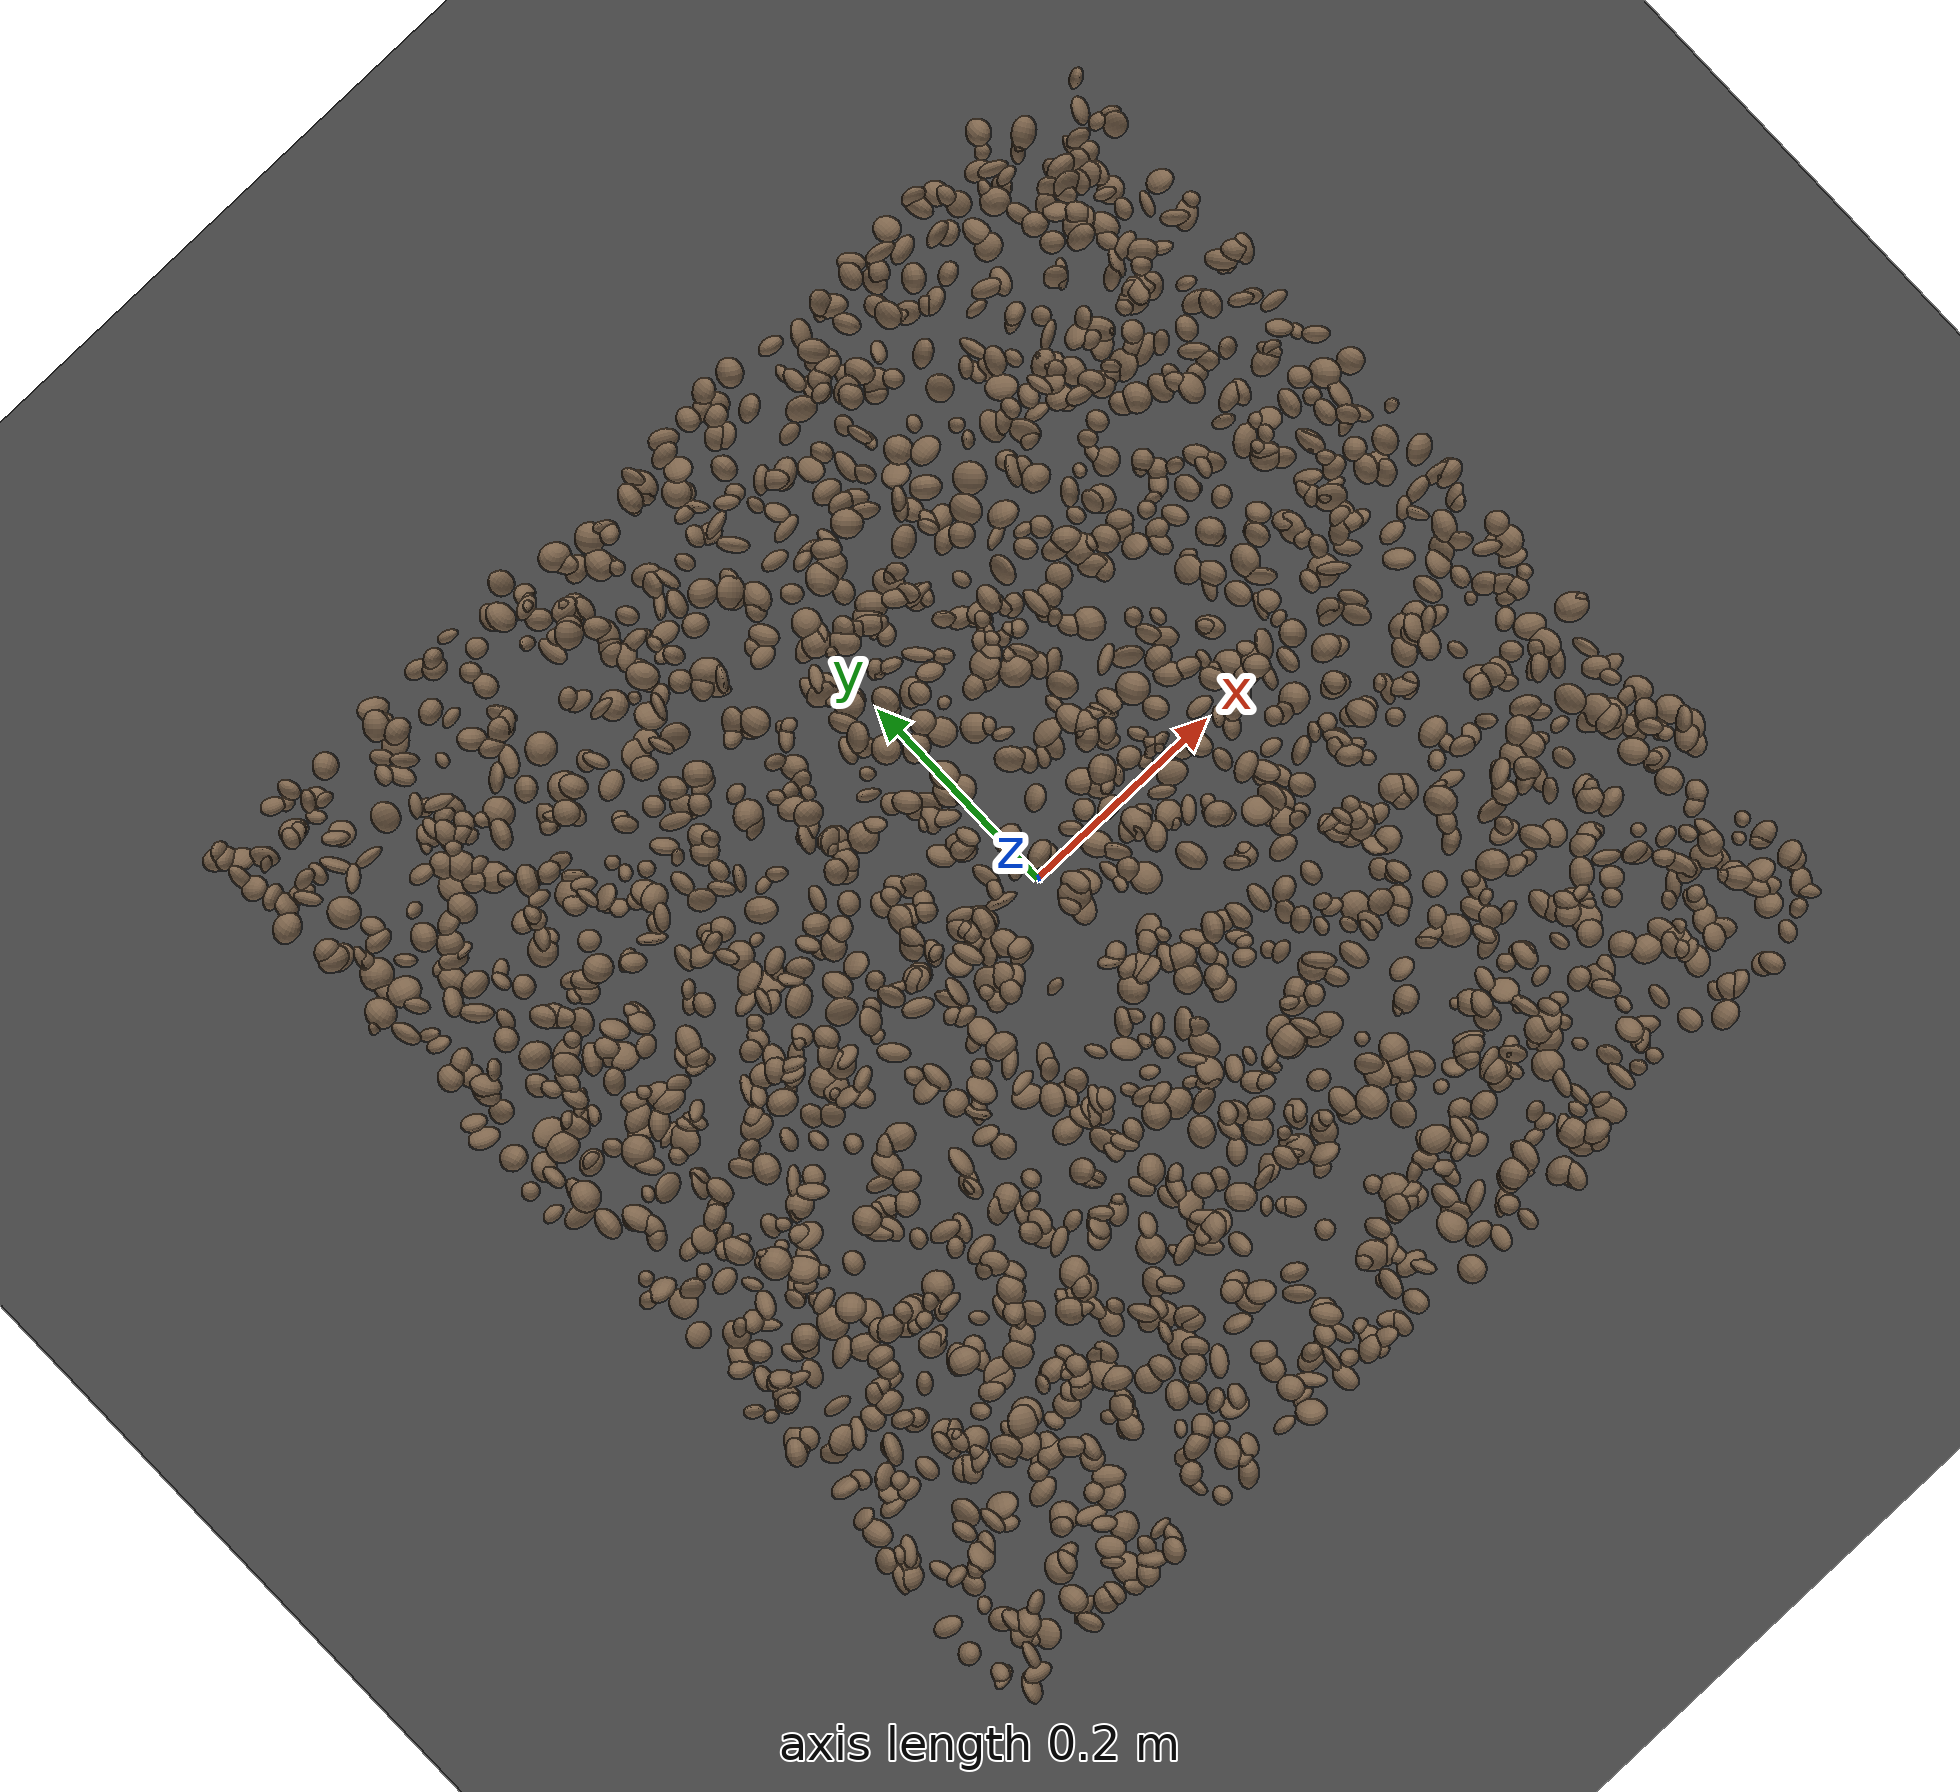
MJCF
<mujoco model="rocky_terrain_scene">
    <compiler angle="radian" inertiafromgeom="true" />
    <option timestep="0.002" gravity="0 0 -9.81" />

    <worldbody>
        <light name="sunlight" pos="5 5 5" dir="-1 -1 -1" diffuse="1 1 1" specular="0.5 0.5 0.5" ambient="0.5 0.5 0.5" />

        <geom name="ground_plane" type="plane" size="50 50 0.1" rgba="0.3 0.3 0.3 1" />

        <body name="rocky_terrain_body">

        <geom name="rock1" type="ellipsoid" size="0.01457702418224336 0.008508565778246399 0.012439404375662681" pos="0.09344185076722467 -0.39505204437071206 0.010070593198241285" quat="0.040011195790379844 0.08908183401125157 0.40912547552118134 0.4617814946771872" rgba="0.5 0.4 0.3 1" /><geom name="rock2" type="ellipsoid" size="0.007967397848233686 0.01121341067757389 0.0062736344510810615" pos="0.19972261532508884 -0.09610650529595399 0.005329566748297475" quat="0.18617165729912363 0.09379766598722106 0.7196613688066156 0.0003693079070397416" rgba="0.5 0.4 0.3 1" /><geom name="rock3" type="ellipsoid" size="0.012053357836482618 0.013807202914583577 0.011570019827956524" pos="-0.41379033331893866 -0.14771321185852837 0.014609625463332635" quat="0.05722284690684789 0.22373757709150405 0.439021777441526 0.28001779856012204" rgba="0.5 0.4 0.3 1" /><geom name="rock4" type="ellipsoid" size="0.013306211946789145 0.009517788033056793 0.010762898853900155" pos="0.3402187972066688 -0.2197873644797812 0.012269104335700956" quat="0.3797312539430367 0.03411110474927298 0.39089657982657394 0.1952610614811164" rgba="0.5 0.4 0.3 1" /><geom name="rock5" type="ellipsoid" size="0.005041900614167998 0.008475971944666101 0.013174427957838415" pos="0.44939717986630623 0.0065478468536259715 0.008370638078804633" quat="0.41323684243912323 0.3903095300170572 0.10353548829459426 0.09291813924922537" rgba="0.5 0.4 0.3 1" /><geom name="rock6" type="ellipsoid" size="0.008280891391181459 0.00850585769309793 0.00831247679629764" pos="0.3454273484991519 -0.34862042521822023 0.010294926455519559" quat="0.04072714965637283 0.11373737188515129 0.3780065690073843 0.4675289094510916" rgba="0.5 0.4 0.3 1" /><geom name="rock7" type="ellipsoid" size="0.009212431897603209 0.005372073796793049 0.013323095692414532" pos="-0.08769594363222888 0.37277344153759906 0.0068996365756606864" quat="0.2095629783434119 0.301517663666879 0.28218812550007444 0.20673123248963463" rgba="0.5 0.4 0.3 1" /><geom name="rock8" type="ellipsoid" size="0.006774223161292233 0.01156651266535008 0.005305278102737994" pos="0.16573400020254336 -0.21054103105055233 0.013555226426895892" quat="0.2245458018176352 0.09279044067130261 0.4507592917766478 0.2319044657344143" rgba="0.5 0.4 0.3 1" /><geom name="rock9" type="ellipsoid" size="0.010088623416164469 0.012320072244060006 0.007666860363076023" pos="0.08208800070393363 -0.1693513769936279 0.009595346818003956" quat="0.20028827375824004 0.04618425115339435 0.33339531199752565 0.42013216309083995" rgba="0.5 0.4 0.3 1" /><geom name="rock10" type="ellipsoid" size="0.008578164363605497 0.008991558000016978 0.008591382409739654" pos="-0.028037191969902175 -0.38613536149445815 0.011548267891290334" quat="0.22967936951731777 0.2171628627587964 0.16540585789213152 0.38775190983175434" rgba="0.5 0.4 0.3 1" /><geom name="rock11" type="ellipsoid" size="0.005476034710835473 0.014768493021930427 0.012959516840183496" pos="0.2254474258964989 0.26854703607292774 0.00575100674470746" quat="0.16963785715058213 0.1289239465394981 0.5795229884040884 0.12191520790583137" rgba="0.5 0.4 0.3 1" /><geom name="rock12" type="ellipsoid" size="0.008510866282109227 0.0076536048822849765 0.014019364487331858" pos="0.2853415398541028 0.47095635948178094 0.010674629250746723" quat="0.05558043050989622 0.3944447928318895 0.17414841116020108 0.3758263654980132" rgba="0.5 0.4 0.3 1" /><geom name="rock13" type="ellipsoid" size="0.011040715914539253 0.009409443281851448 0.014808350109346564" pos="0.02554885153775821 0.2690170339775687 0.014619123501343097" quat="0.44751242001745467 0.018796410755504492 0.1375868607860299 0.3961043084410109" rgba="0.5 0.4 0.3 1" /><geom name="rock14" type="ellipsoid" size="0.007045405128816839 0.009856635399096318 0.007364411057333001" pos="0.253907060344822 0.27872874775646816 0.005551577852090845" quat="0.09123077963986473 0.4118392100705075 0.4921151143164695 0.004814895973158406" rgba="0.5 0.4 0.3 1" /><geom name="rock15" type="ellipsoid" size="0.00912902944074891 0.013904837816413204 0.006654037865129969" pos="-0.1769254283431564 -0.33695249898914414 0.006065939551176011" quat="0.2336303350607587 0.30116623658705693 0.17685158542254 0.28835184292964433" rgba="0.5 0.4 0.3 1" /><geom name="rock16" type="ellipsoid" size="0.008468250544720585 0.011948916787107133 0.006653747673222192" pos="-0.4648627806865421 -0.2693723612847382 0.0027566219047321715" quat="0.18819783453005365 0.47858000902599007 0.19860580583046408 0.13461635061349217" rgba="0.5 0.4 0.3 1" /><geom name="rock17" type="ellipsoid" size="0.006550212707599359 0.007163261592167663 0.013339914118391465" pos="0.023416252419918737 0.35341217606739106 0.005423222898649926" quat="0.3691180855275284 0.08575857711924006 0.530921648149548 0.01420168920368349" rgba="0.5 0.4 0.3 1" /><geom name="rock18" type="ellipsoid" size="0.008488392876552429 0.005192008272190886 0.0066781245431686755" pos="-0.021657129553997567 -0.4542757677006767 0.00018882081843096032" quat="0.30875473594737446 0.0032172835711542025 0.3942470128093102 0.29378096767216116" rgba="0.5 0.4 0.3 1" /><geom name="rock19" type="ellipsoid" size="0.01238831819925106 0.005720499816245514 0.01078635788688528" pos="-0.010309297896585856 0.22051560441524753 0.0034322952950075944" quat="0.33718060412015016 0.4036859238213051 0.20883906146550493 0.05029441059303983" rgba="0.5 0.4 0.3 1" /><geom name="rock20" type="ellipsoid" size="0.014008763910818522 0.01368495629353923 0.0073197607708045806" pos="0.3831057019846502 0.2150066481579609 0.013985075800316308" quat="0.27424001388812763 0.20660666248813722 0.034119284744467765 0.4850340388792674" rgba="0.5 0.4 0.3 1" /><geom name="rock21" type="ellipsoid" size="0.011268735948822665 0.014592554564795461 0.013205402099495552" pos="0.21688245554033903 0.19487056535176206 0.01086342747581727" quat="0.38851894926848535 0.2728803041116398 0.10220791665784866 0.23639282996202615" rgba="0.5 0.4 0.3 1" /><geom name="rock22" type="ellipsoid" size="0.008768068431988806 0.005527414589508003 0.00841784847298654" pos="-0.27790293516430187 0.22896397494683118 0.005999292040339552" quat="0.3730447164722659 0.29646987475375564 0.26151054434236387 0.06897486443161469" rgba="0.5 0.4 0.3 1" /><geom name="rock23" type="ellipsoid" size="0.009239140683258748 0.013427544398290452 0.0057929601216089345" pos="0.13437785790432355 -0.16542413193182115 0.006802336926651821" quat="0.20103811804700308 0.22730869626804856 0.4168630420220363 0.15479014366291205" rgba="0.5 0.4 0.3 1" /><geom name="rock24" type="ellipsoid" size="0.011462069083159485 0.01138960361535451 0.009916172338782565" pos="-0.42008727290347736 -0.23769324526986357 0.009509636900814623" quat="0.28482775173165586 0.10874533546786719 0.5301743834616098 0.07625252933886704" rgba="0.5 0.4 0.3 1" /><geom name="rock25" type="ellipsoid" size="0.009706986337412581 0.012564419334466757 0.012243532383435698" pos="0.09418730185960122 -0.22068574409021569 0.006585493332142096" quat="0.17461375698866743 0.18761868896927128 0.3739862889872704 0.2637812650547909" rgba="0.5 0.4 0.3 1" /><geom name="rock26" type="ellipsoid" size="0.012113143875382173 0.014589824084709404 0.008693501285122057" pos="0.3652053892676763 0.06953514902247793 0.0019019246158435315" quat="0.2241544304854512 0.13564331234364882 0.5729104034436125 0.06729185372728749" rgba="0.5 0.4 0.3 1" /><geom name="rock27" type="ellipsoid" size="0.005578786337844936 0.012087890643714516 0.008430792417464455" pos="-0.001973509713780741 -0.3189805796567663 0.009826958641343598" quat="0.2254199565513136 0.4363934289405769 0.19717220830250526 0.1410144062056042" rgba="0.5 0.4 0.3 1" /><geom name="rock28" type="ellipsoid" size="0.013285785916499423 0.009689812822167788 0.005154642066507189" pos="0.3529873687461904 -0.022104510881086115 0.00892113690141347" quat="0.12979283340253528 0.2657845018747777 0.4793315057928886 0.12509115892979839" rgba="0.5 0.4 0.3 1" /><geom name="rock29" type="ellipsoid" size="0.006711993042164103 0.008616555908997844 0.011600245864175575" pos="-0.10806007867599476 0.14927506751591635 0.0014571582028850966" quat="0.24739074161029226 0.23228078395352425 0.09049846097946378 0.4298300134567198" rgba="0.5 0.4 0.3 1" /><geom name="rock30" type="ellipsoid" size="0.010227353993665127 0.010759953780576951 0.013868487295303992" pos="0.17184252632722585 -0.3963750235236374 0.00018986114448271306" quat="0.0007216602966291214 0.4858172610254369 0.10683131886463076 0.4066297598133031" rgba="0.5 0.4 0.3 1" /><geom name="rock31" type="ellipsoid" size="0.011115390610108859 0.008432351153285963 0.01325707287590858" pos="0.21848191831042385 0.16353256425816842 0.005372886474882059" quat="0.28559291398513686 0.35257230325505184 0.013982471900460716 0.34785231085935053" rgba="0.5 0.4 0.3 1" /><geom name="rock32" type="ellipsoid" size="0.005634355153392375 0.014607227517956806 0.009391792955973116" pos="0.2722367169069798 -0.2966809865907488 0.0053269858631697815" quat="0.17859404415511002 0.2653320631897284 0.3691350305402398 0.1869388621149218" rgba="0.5 0.4 0.3 1" /><geom name="rock33" type="ellipsoid" size="0.012155448605621347 0.00790803465706712 0.005917656408278148" pos="-0.019206066365631047 0.06788310655763474 0.012338945733950375" quat="0.37345159298036673 0.008829633502761496 0.235377839394236 0.3823409341226357" rgba="0.5 0.4 0.3 1" /><geom name="rock34" type="ellipsoid" size="0.006207829843939886 0.009018309661260809 0.008750113643968955" pos="0.40845445277229675 -0.15442560425654972 0.001751838888213723" quat="0.34908948911709325 0.35030446702460477 0.24631172287983555 0.05429432097846644" rgba="0.5 0.4 0.3 1" /><geom name="rock35" type="ellipsoid" size="0.013778660799532608 0.014297962191758742 0.014330861351241522" pos="0.2285085707220199 -0.2765658458346125 0.007724167115612806" quat="0.24946159836465173 0.36597697279485847 0.034065495659477064 0.35049593318101274" rgba="0.5 0.4 0.3 1" /><geom name="rock36" type="ellipsoid" size="0.005296652126417813 0.0077209425674724915 0.013819347244000146" pos="-0.12520541750912573 -0.4721791079111429 0.005162675027733714" quat="0.3341316373912496 0.3750234126486907 0.05023767349771463 0.240607276462345" rgba="0.5 0.4 0.3 1" /><geom name="rock37" type="ellipsoid" size="0.012790471884208916 0.006836930327833109 0.011934013400447727" pos="-0.23371578112223668 0.014538100010840105 0.014476312913542226" quat="0.1273800235763537 0.4896268118140605 0.21444395195714921 0.16854921265243664" rgba="0.5 0.4 0.3 1" /><geom name="rock38" type="ellipsoid" size="0.007828496084161763 0.013159656446920447 0.014394241999547325" pos="-0.3921755973635832 -0.36912486240596754 0.0038937280099234626" quat="0.23521256727606218 0.3461722449706734 0.08379653384934711 0.3348186539039173" rgba="0.5 0.4 0.3 1" /><geom name="rock39" type="ellipsoid" size="0.011967598879909867 0.006991176258760071 0.008393774875376573" pos="0.39609201247594883 -0.3994157983860839 0.007424306286500677" quat="0.3057649726467804 0.20063504763717632 0.2827386178186629 0.2108613618973804" rgba="0.5 0.4 0.3 1" /><geom name="rock40" type="ellipsoid" size="0.010101739044023717 0.01299887236508189 0.006643569511775995" pos="-0.3908623039134964 -0.2933810335263357 0.013832384636795545" quat="0.29018229377506644 0.2266074637003852 0.31408736044870006 0.16912288207584822" rgba="0.5 0.4 0.3 1" /><geom name="rock41" type="ellipsoid" size="0.014699392803194475 0.01484008261131214 0.00836081414422636" pos="0.40726124514033446 -0.36956879303017975 0.006595927368463946" quat="0.17936931644985082 0.2645198144296077 0.29519473004887287 0.2609161390716686" rgba="0.5 0.4 0.3 1" /><geom name="rock42" type="ellipsoid" size="0.006400442326399909 0.006192947604155441 0.014652546469031889" pos="0.47259572007523687 -0.05780937023519117 0.014346639584471197" quat="0.2779733055076881 0.3117823208228732 0.32880359461234315 0.08144077905709547" rgba="0.5 0.4 0.3 1" /><geom name="rock43" type="ellipsoid" size="0.011249669557379893 0.009060284149019833 0.01259823480203318" pos="0.09436486802603383 -0.2606668338099827 0.010512015261659886" quat="0.3273243830175959 0.2885394859199612 0.17352845288462274 0.2106076781778201" rgba="0.5 0.4 0.3 1" /><geom name="rock44" type="ellipsoid" size="0.009551065838760139 0.005248678264841294 0.012118118279954796" pos="0.49547605417216745 -0.14626621797656758 0.008297276574743275" quat="0.13316062920661487 0.3231114192613652 0.15913851584858382 0.384589435683436" rgba="0.5 0.4 0.3 1" /><geom name="rock45" type="ellipsoid" size="0.010341995214304844 0.009392880830038353 0.009997289039914311" pos="0.29878704400491274 -0.0515362419705242 0.012655763176624457" quat="0.24923912595186984 0.06995028293672595 0.36401908282071144 0.3167915082906928" rgba="0.5 0.4 0.3 1" /><geom name="rock46" type="ellipsoid" size="0.014015326757162286 0.009590058070830963 0.006611006851839403" pos="-0.2693992608030501 0.32689207740144743 0.0029283232929222403" quat="0.05939832685186881 0.46784569210369586 0.3340830911782008 0.13867288986623452" rgba="0.5 0.4 0.3 1" /><geom name="rock47" type="ellipsoid" size="0.007905051127325766 0.01274818870842662 0.013458957364555695" pos="-0.45058281394815913 -0.23328672597353406 0.014651813391114188" quat="0.3549100838653154 0.0503881428966899 0.42655123798514666 0.16815053525284795" rgba="0.5 0.4 0.3 1" /><geom name="rock48" type="ellipsoid" size="0.011744685403926284 0.009832022858543357 0.007295761095325299" pos="-0.12869409975985535 0.3369753708093275 0.0009321325287328502" quat="0.2615437100339024 0.5147651765398743 0.07516241913577912 0.1485286942904441" rgba="0.5 0.4 0.3 1" /><geom name="rock49" type="ellipsoid" size="0.00730466498596892 0.011478641275592723 0.011768596780254142" pos="-0.05055182008406334 -0.2048170516665354 0.011650470376630223" quat="0.15363904011826882 0.3079436765042539 0.31985538293841026 0.21856190043906706" rgba="0.5 0.4 0.3 1" /><geom name="rock50" type="ellipsoid" size="0.009626546824745844 0.014747182727319036 0.01136750072176281" pos="0.02963953073508363 -0.32503081078971385 0.0018574326630959792" quat="0.3929897179106441 0.11153324882663405 0.397845613450589 0.09763141981213293" rgba="0.5 0.4 0.3 1" /><geom name="rock51" type="ellipsoid" size="0.012579234523981556 0.005846028644608093 0.01262174950925497" pos="0.0872088177144752 -0.024377626994161572 0.014894792690461461" quat="0.40200241382615115 0.05382526626896323 0.0906534658212812 0.45351885408360443" rgba="0.5 0.4 0.3 1" /><geom name="rock52" type="ellipsoid" size="0.009710734085037137 0.010018559787368618 0.007530682640655073" pos="-0.3158785782563457 0.22602436455886243 0.007052490265765097" quat="0.49678515801071915 0.09760747437270342 0.025180432835713366 0.380426934780864" rgba="0.5 0.4 0.3 1" /><geom name="rock53" type="ellipsoid" size="0.010682206364995495 0.013151139680763278 0.005563484066499619" pos="0.4482068853710456 0.3209508065610327 0.004433377561462711" quat="0.1208073686286849 0.08814487036368375 0.3196848030191995 0.4713629579884318" rgba="0.5 0.4 0.3 1" /><geom name="rock54" type="ellipsoid" size="0.011223751598766051 0.009538199519387783 0.005885691008626939" pos="0.46694776684968253 0.24142142170740266 0.007875542665082162" quat="0.14262551130162696 0.07465611665259803 0.37888067387359287 0.4038376981721822" rgba="0.5 0.4 0.3 1" /><geom name="rock55" type="ellipsoid" size="0.008275330652962156 0.006935891651960637 0.013709591178499837" pos="-0.11060737951254118 -0.3278582288209273 0.006459178393941535" quat="0.36131696213639464 0.3441781693616606 0.024137994216434856 0.27036687428550993" rgba="0.5 0.4 0.3 1" /><geom name="rock56" type="ellipsoid" size="0.0055285749858019605 0.005940109773521128 0.00670400319348668" pos="-0.010703594413460249 0.017373052044553083 0.013723751290440178" quat="0.28647459055640556 0.10666375254582149 0.3588338350245881 0.24802782187318495" rgba="0.5 0.4 0.3 1" /><geom name="rock57" type="ellipsoid" size="0.010117947495675135 0.010048184836628223 0.009633149639788802" pos="0.14338581024576424 -0.10750062299242424 0.003598097251028865" quat="0.40999019667048037 0.04635539197347365 0.484224327135239 0.05943008422080702" rgba="0.5 0.4 0.3 1" /><geom name="rock58" type="ellipsoid" size="0.005086194081980976 0.014793828217313437 0.006213677956323849" pos="-0.0742456512904408 0.39450093999638114 0.001420747620948759" quat="0.2069938957203142 0.08791956813470347 0.09700006778149736 0.608086468363485" rgba="0.5 0.4 0.3 1" /><geom name="rock59" type="ellipsoid" size="0.010406558587495184 0.014725610789085363 0.012126238848977643" pos="0.3035353958896734 0.003440550250859431 0.000608904763201617" quat="0.2579702355517092 0.031776885149164956 0.3874342445740605 0.32281863472506533" rgba="0.5 0.4 0.3 1" /><geom name="rock60" type="ellipsoid" size="0.005937409331373209 0.014600768346210942 0.01252308134144" pos="-0.027543909948258505 -0.31540112008874266 0.00014368399242352948" quat="0.05445086208666704 0.2693399935855894 0.2874448775177194 0.3887642668100241" rgba="0.5 0.4 0.3 1" /><geom name="rock61" type="ellipsoid" size="0.014563616535174052 0.014738234964987981 0.006103639652706519" pos="0.43942388698055446 -0.22808061282643144 0.00186371610159687" quat="0.006243566879129847 0.2530716121513141 0.5021747662030942 0.23851005476646184" rgba="0.5 0.4 0.3 1" /><geom name="rock62" type="ellipsoid" size="0.006163466845741435 0.013794817814482638 0.012486595479784039" pos="0.016493204176989074 0.4658423383431387 0.012623834810445305" quat="0.20589839143509028 0.40697524279193437 0.03159091472453589 0.3555354510484395" rgba="0.5 0.4 0.3 1" /><geom name="rock63" type="ellipsoid" size="0.010244560315373144 0.014117720398394429 0.006612220758450468" pos="0.36506453778769343 0.07908719540643883 0.0005021576581543197" quat="0.053591054488280956 0.04598155703919089 0.29931225345061163 0.6011151350219165" rgba="0.5 0.4 0.3 1" /><geom name="rock64" type="ellipsoid" size="0.012566262054719602 0.014299656940893392 0.011591180842249249" pos="-0.23028342172926142 0.12804496536337184 0.006550677218299681" quat="0.2706665102310961 0.45334007393714537 0.11105594122447529 0.16493747460728325" rgba="0.5 0.4 0.3 1" /><geom name="rock65" type="ellipsoid" size="0.012359660820066964 0.011790627294626942 0.013290200832626116" pos="0.0434526263725582 -0.13243712869469637 0.006161895417015345" quat="0.37172444597414134 0.18545109981377098 0.3497453943221607 0.09307905988992712" rgba="0.5 0.4 0.3 1" /><geom name="rock66" type="ellipsoid" size="0.014579009928235295 0.012114813897799113 0.009303244371773621" pos="-0.029137186275340787 0.21308011313594766 0.0029144527820251834" quat="0.3453621591947198 0.02656355531217268 0.4290288447688838 0.19904544072422373" rgba="0.5 0.4 0.3 1" /><geom name="rock67" type="ellipsoid" size="0.005908665615599313 0.014223921396122208 0.007792897721267516" pos="0.32872690532966364 -0.07928543400165577 0.004235836608662533" quat="0.206467177046761 0.14323424533108825 0.30429510813163596 0.3460034694905147" rgba="0.5 0.4 0.3 1" /><geom name="rock68" type="ellipsoid" size="0.008464577804372436 0.0058239573761032235 0.006677988356241988" pos="0.06503685223693789 -0.15787174150935435 0.0012907380059703898" quat="0.3774288778686607 0.14472506081258063 0.20023197829307937 0.27761408302567936" rgba="0.5 0.4 0.3 1" /><geom name="rock69" type="ellipsoid" size="0.010302214842132725 0.01060512194667565 0.007269565024118961" pos="0.48165915200629317 -0.43130330846763 0.009623640726704788" quat="0.15517844452694074 0.4351976955310407 0.27587081262947527 0.13375304731254317" rgba="0.5 0.4 0.3 1" /><geom name="rock70" type="ellipsoid" size="0.012492763586420923 0.006094941937474327 0.006851500926211082" pos="0.3914974701543722 0.2615220859083843 0.009483244926141778" quat="0.28038323582061614 0.4320049234715803 0.00043349670923435496 0.2871783439985691" rgba="0.5 0.4 0.3 1" /><geom name="rock71" type="ellipsoid" size="0.00791476129892939 0.005959831883365011 0.0064411434745630415" pos="-0.06514500249443933 0.24180513615278476 0.011685322988623511" quat="0.5011736635267402 0.3916972362128897 0.10043191204764236 0.006697188212727708" rgba="0.5 0.4 0.3 1" /><geom name="rock72" type="ellipsoid" size="0.00915859049387077 0.005633066298183994 0.008235902564635307" pos="-0.04460055555032916 -0.18515306320273905 0.012255689816328375" quat="0.20009593846089288 0.16446268779104137 0.5701492753554485 0.06529209839261728" rgba="0.5 0.4 0.3 1" /><geom name="rock73" type="ellipsoid" size="0.010920972972560207 0.012110881054902154 0.007851053769166037" pos="-0.07911287064853245 0.014270646112491847 0.009800526046358504" quat="0.004460896549874845 0.5911047269653497 0.1307039313168033 0.27373044516797224" rgba="0.5 0.4 0.3 1" /><geom name="rock74" type="ellipsoid" size="0.01087956704032559 0.006117179803564106 0.00718903180112905" pos="-0.38398415390397 -0.11558134302046508 0.009514967118135155" quat="0.028345579728501078 0.2383000913996083 0.35770633792330503 0.37564799094858564" rgba="0.5 0.4 0.3 1" /><geom name="rock75" type="ellipsoid" size="0.014584061398563612 0.010379602050976138 0.007489694949611157" pos="-0.08785384951765052 -0.005328896314987008 0.014359585549513922" quat="0.2556123254218337 0.15956324785923767 0.2810860226933021 0.3037384040256266" rgba="0.5 0.4 0.3 1" /><geom name="rock76" type="ellipsoid" size="0.009568942235263053 0.010421243995085271 0.010234318506172659" pos="0.31132604269161446 0.19935892876944972 0.005880109729506186" quat="0.1961193240512752 0.12285624540171355 0.3304056209070329 0.3506188096399783" rgba="0.5 0.4 0.3 1" /><geom name="rock77" type="ellipsoid" size="0.011435772834498554 0.00914317995380368 0.012230982366936503" pos="-0.13408239865715077 0.009926534743589954 0.013176096866764853" quat="0.28477088189052774 0.2141136661466441 0.3243921759407439 0.17672327602208424" rgba="0.5 0.4 0.3 1" /><geom name="rock78" type="ellipsoid" size="0.006537361889492491 0.010421465112736245 0.006197609556716424" pos="-0.2547295623820749 -0.012289560701343127 0.0040958507887598845" quat="0.008243929667413094 0.15728607038331283 0.3995327166545745 0.43493728329469966" rgba="0.5 0.4 0.3 1" /><geom name="rock79" type="ellipsoid" size="0.013467843903740884 0.011391227222341451 0.008319616487698484" pos="-0.11396224720097503 0.03697768998333495 0.014308049951963137" quat="0.17571646517645864 0.326552101703956 0.24567827281680132 0.2520531603027841" rgba="0.5 0.4 0.3 1" /><geom name="rock80" type="ellipsoid" size="0.006257569869851473 0.01308135574871504 0.009135827228261673" pos="0.42916377680044193 0.21875094400702122 0.01297235830606086" quat="0.2643784707106286 0.14553701708803948 0.3230112759977382 0.2670732362035936" rgba="0.5 0.4 0.3 1" /><geom name="rock81" type="ellipsoid" size="0.011606128678252104 0.014242852384014983 0.005615904249727245" pos="-0.46044162239641495 -0.4777610650099505 0.013004961379956482" quat="0.4173728599351193 0.15866640743352678 0.3721473032812441 0.05181342935010975" rgba="0.5 0.4 0.3 1" /><geom name="rock82" type="ellipsoid" size="0.012389506960386059 0.011753684321456737 0.006493835961094407" pos="0.473620037406421 -0.4514876104784582 0.001401735846315764" quat="0.5541130260496168 0.19073316453273648 0.06012193220470423 0.19503187721294252" rgba="0.5 0.4 0.3 1" /><geom name="rock83" type="ellipsoid" size="0.0072877128888480195 0.010692967108052428 0.011117793214517549" pos="-0.12654083607242317 -0.04189352805165203 0.009953202356992603" quat="0.3047400656165221 0.19479596999876894 0.20073298561006378 0.29973097877464516" rgba="0.5 0.4 0.3 1" /><geom name="rock84" type="ellipsoid" size="0.009075795410423105 0.007638245502602445 0.013667480066517895" pos="0.08659961596143129 -0.02132495540828916 0.014935343642776192" quat="0.14968579452964545 0.22115349941849802 0.3173616643562856 0.31179904169557093" rgba="0.5 0.4 0.3 1" /><geom name="rock85" type="ellipsoid" size="0.009280654010178864 0.005488994945385559 0.010760803920658656" pos="-0.19144881454838825 -0.3402905165001293 0.008910327777678997" quat="0.24930035920162374 0.18444394111137788 0.19826449725627138 0.367991202430727" rgba="0.5 0.4 0.3 1" /><geom name="rock86" type="ellipsoid" size="0.005204801418935575 0.012776840781120888 0.01371519156459389" pos="0.22389648196379686 -0.3428483842567762 0.010139197403307987" quat="0.025602392247174102 0.5172785132540133 0.16613290074207568 0.29098619375673695" rgba="0.5 0.4 0.3 1" /><geom name="rock87" type="ellipsoid" size="0.010406106545967752 0.008873861208994964 0.005257340582881876" pos="-0.28141885968554325 0.01336136558663481 0.0010703693322570013" quat="0.39383206647788266 0.40572166436233587 0.14999309412321674 0.05045317503656476" rgba="0.5 0.4 0.3 1" /><geom name="rock88" type="ellipsoid" size="0.013075770604892307 0.010065509887505496 0.007087133073082449" pos="0.09609637693521755 0.2448257162347337 0.0021771448606369257" quat="0.3646333735011819 0.1722322400034516 0.3433432612039725 0.11979112529139384" rgba="0.5 0.4 0.3 1" /><geom name="rock89" type="ellipsoid" size="0.010564373283573736 0.01354860281309963 0.009253580308849145" pos="-0.363133212546895 -0.18797884932342523 0.00734179607509416" quat="0.5732793579122358 0.2845147283438958 0.05530685795076195 0.08689905579310649" rgba="0.5 0.4 0.3 1" /><geom name="rock90" type="ellipsoid" size="0.011692287129850024 0.005354705815869669 0.012156801176921138" pos="0.2745164356256341 0.2918108936685151 0.0007560145538412222" quat="0.2815545142455246 0.09686567107605284 0.5260355528593789 0.09554426181904381" rgba="0.5 0.4 0.3 1" /><geom name="rock91" type="ellipsoid" size="0.00832456374078077 0.01105964755204304 0.007912054433086884" pos="-0.27111212080102076 -0.055717240980949545 0.006636254535274474" quat="0.2532834829626834 0.3308174311212919 0.1607589365676206 0.2551401493484041" rgba="0.5 0.4 0.3 1" /><geom name="rock92" type="ellipsoid" size="0.014553750986401506 0.007179055794962352 0.009472836419551042" pos="0.14900772087514558 0.06949490588619978 0.00958678066416231" quat="0.30768299098885227 0.21349026085447853 0.3550238890302883 0.12380285912638096" rgba="0.5 0.4 0.3 1" /><geom name="rock93" type="ellipsoid" size="0.005757349041609523 0.00998420929061753 0.009641116345698832" pos="0.34094456046676735 0.09322893522196218 0.0014231668229142324" quat="0.06015952308199101 0.3419075052480705 0.3536930753156553 0.24423989635428314" rgba="0.5 0.4 0.3 1" /><geom name="rock94" type="ellipsoid" size="0.008694033178311054 0.0142239757842775 0.013651384463471899" pos="0.4048922532890942 -0.17930381520722205 0.0041059042575084205" quat="0.4157218164854387 0.18893204721062573 0.19347699042860386 0.20186914587533158" rgba="0.5 0.4 0.3 1" /><geom name="rock95" type="ellipsoid" size="0.006010684515727837 0.010549209033896534 0.0058515195093002716" pos="0.09737918978307947 0.017429092318366868 0.011998626794680296" quat="0.32331263424238793 0.29393993382029476 0.08369831025875434 0.29904912167856296" rgba="0.5 0.4 0.3 1" /><geom name="rock96" type="ellipsoid" size="0.011378711392476207 0.00668028215304543 0.0065580602073000635" pos="-0.4668652024138017 -0.37262502562888733 0.010251786049677568" quat="0.2066832684000621 0.2267718928261646 0.30331354449260545 0.26323129428116776" rgba="0.5 0.4 0.3 1" /><geom name="rock97" type="ellipsoid" size="0.007696350033788815 0.0074929397178892035 0.011022407005793126" pos="0.13489251430741478 0.16741594494261725 0.008897617448971024" quat="0.022274376134009146 0.4377310764200054 0.38132469650838785 0.1586698509375977" rgba="0.5 0.4 0.3 1" /><geom name="rock98" type="ellipsoid" size="0.009094650595056344 0.008328043330777798 0.010521875958363031" pos="-0.4827249132806525 -0.349819456855733 0.004493655964882019" quat="0.09115863880648291 0.32494711802837617 0.21917621120868622 0.3647180319564548" rgba="0.5 0.4 0.3 1" /><geom name="rock99" type="ellipsoid" size="0.005031541788796083 0.013479115624722763 0.006240454917344175" pos="-0.17940034421162798 0.44751191711575977 0.006721329476644" quat="0.13622087325757112 0.00977615117462605 0.40608785972088934 0.4479151158469134" rgba="0.5 0.4 0.3 1" /><geom name="rock100" type="ellipsoid" size="0.00809439181617174 0.00835500406614738 0.008631847967491776" pos="0.03847102916048206 0.4192322095398925 0.004460238643944335" quat="0.28045214521456124 0.41316980065804576 0.0535321957104256 0.25284585841696733" rgba="0.5 0.4 0.3 1" /><geom name="rock101" type="ellipsoid" size="0.014163228776364369 0.014061003867801295 0.008819548157046804" pos="0.4459651117267087 -0.2228316174911501 0.010197031382472403" quat="0.13638781383389392 0.524238893494517 0.22456510694068202 0.11480818573090706" rgba="0.5 0.4 0.3 1" /><geom name="rock102" type="ellipsoid" size="0.008184953008259499 0.013788119225292498 0.009988936831356744" pos="-0.44239849443120993 -0.39063215847062605 0.014445099445827829" quat="0.18545690160403266 0.18073503923725873 0.3275935296337133 0.3062145295249953" rgba="0.5 0.4 0.3 1" /><geom name="rock103" type="ellipsoid" size="0.00878743261426632 0.010564237922687288 0.010721475607435482" pos="-0.3005021905693983 0.2918401133987668 0.011012923056356946" quat="0.16119613812464068 0.3155691120939271 0.3843659357775566 0.13886881400387557" rgba="0.5 0.4 0.3 1" /><geom name="rock104" type="ellipsoid" size="0.009985801263201075 0.013060709671150736 0.006035085108763141" pos="-0.011165759738799075 0.4144441005446702 0.00916639581649339" quat="0.3551001053989258 0.22023263624533207 0.15757279661321924 0.2670944617425228" rgba="0.5 0.4 0.3 1" /><geom name="rock105" type="ellipsoid" size="0.008102249853544423 0.014424033824432903 0.014140032131725575" pos="0.3728954623276556 -0.4772452086157052 0.003592123541421625" quat="0.12502877920816943 0.3063934406794789 0.407895691651983 0.16068208846036874" rgba="0.5 0.4 0.3 1" /><geom name="rock106" type="ellipsoid" size="0.014436026344402605 0.01439263714600239 0.0063447755168413765" pos="0.18627065811609533 0.08597155328487949 0.007347755379551306" quat="0.015971863641182138 0.22971873304354043 0.4416091077043598 0.31270029561091767" rgba="0.5 0.4 0.3 1" /><geom name="rock107" type="ellipsoid" size="0.009828308653814469 0.0072723424128022 0.005280692415442601" pos="-0.41601904871592243 -0.0834924191815114 0.011041763870595581" quat="0.23052444166492816 0.14280810938953356 0.37725781822680515 0.2494096307187331" rgba="0.5 0.4 0.3 1" /><geom name="rock108" type="ellipsoid" size="0.008239565625303041 0.014223183579924109 0.008796034385877219" pos="-0.15393283351601617 0.25616003580506375 0.0023681937286534416" quat="0.33377024730202826 0.16162517517241026 0.12678790930098413 0.37781666822457743" rgba="0.5 0.4 0.3 1" /><geom name="rock109" type="ellipsoid" size="0.006046227233299149 0.007266856517714841 0.011104820911663227" pos="-0.1358225584835755 0.4461306764764731 0.012545198798145144" quat="0.4519228747760686 0.005122353280288473 0.12453314391353874 0.4184216280301042" rgba="0.5 0.4 0.3 1" /><geom name="rock110" type="ellipsoid" size="0.006443972346492979 0.00782773651554016 0.009804626824136863" pos="0.15050107207806662 0.42956991402617983 0.013574926698955391" quat="0.17078343405426158 0.29342882092212613 0.1658601351669808 0.36992760985663137" rgba="0.5 0.4 0.3 1" /><geom name="rock111" type="ellipsoid" size="0.011116493643085004 0.011317826934672464 0.008269754598106726" pos="0.2871442042109208 -0.2038106132027393 0.011568201691603991" quat="0.2580471930068271 0.32589409701597993 0.06742852894400805 0.3486301810331849" rgba="0.5 0.4 0.3 1" /><geom name="rock112" type="ellipsoid" size="0.009210121845532597 0.0063727991874791634 0.010946030182807424" pos="0.10306415999208562 -0.406675364850386 0.0016066236121371007" quat="0.36493224994169177 0.11561862569527537 0.29263792425796764 0.22681120010506528" rgba="0.5 0.4 0.3 1" /><geom name="rock113" type="ellipsoid" size="0.00582448316859992 0.009914691062186513 0.012230668935182435" pos="-0.4699607831706101 0.24973557061525864 0.011329808766659491" quat="0.3803535993892926 0.2308289116974672 0.04267636740666317 0.34614112150657694" rgba="0.5 0.4 0.3 1" /><geom name="rock114" type="ellipsoid" size="0.009217249016342419 0.011213318052397229 0.012029751615745692" pos="-0.310497662016994 -0.4963379467061043 0.012136038699781687" quat="0.08528009162842598 0.1839343047543701 0.1943490238936185 0.5364365797235855" rgba="0.5 0.4 0.3 1" /><geom name="rock115" type="ellipsoid" size="0.012187132895336732 0.010157125038204276 0.012080278504956871" pos="0.49883603103560537 0.13889390653522582 0.00815206442914714" quat="0.2473056390883705 0.1770769806853051 0.16904822248428553 0.4065691577420388" rgba="0.5 0.4 0.3 1" /><geom name="rock116" type="ellipsoid" size="0.005494229664778979 0.014263019769555223 0.011607081642356807" pos="-0.02759080271396519 -0.2347826827262951 0.01076070271939152" quat="0.26252494369178814 0.25246604557626945 0.3817411246428091 0.10326788608913336" rgba="0.5 0.4 0.3 1" /><geom name="rock117" type="ellipsoid" size="0.007887247538779237 0.007636988298141557 0.008571953257704658" pos="-0.4993987628524932 0.10446105040744602 0.010561148308702223" quat="0.1463118901169915 0.15750781977753897 0.15465297034053468 0.5415273197649348" rgba="0.5 0.4 0.3 1" /><geom name="rock118" type="ellipsoid" size="0.01026370728425651 0.010795412615688539 0.012044236038065334" pos="-0.4249981823383735 0.21315038803965125 0.011540151971986498" quat="0.05345469532082143 0.07977448192042219 0.6906195067624613 0.17615131599629505" rgba="0.5 0.4 0.3 1" /><geom name="rock119" type="ellipsoid" size="0.013714789132389195 0.006578385767772722 0.007961703887852658" pos="0.2604135835153374 0.4778405088225587 0.0023194313467697404" quat="0.0074166220063103866 0.39549007453110596 0.24652516472236982 0.3505681387402139" rgba="0.5 0.4 0.3 1" /><geom name="rock120" type="ellipsoid" size="0.007444640341197589 0.012341064422736372 0.005405660235840409" pos="0.4772525893505003 0.23751192021059842 0.0017559289102003712" quat="0.12314800857363668 0.3505227691233424 0.26094521557320216 0.2653840067298187" rgba="0.5 0.4 0.3 1" /><geom name="rock121" type="ellipsoid" size="0.014809269779031638 0.011879810503348555 0.011351643260373717" pos="-0.19048233036706175 0.1435862631905559 0.013236249931719362" quat="0.22394189067956397 0.027200354177173224 0.330856054059317 0.41800170108394574" rgba="0.5 0.4 0.3 1" /><geom name="rock122" type="ellipsoid" size="0.008920618737174344 0.012109980534801402 0.012180437756963187" pos="0.4514266709965252 0.38715711350415505 0.001880288265575819" quat="0.041927746364699994 0.37393947405222466 0.09590797212581151 0.4882248074572638" rgba="0.5 0.4 0.3 1" /><geom name="rock123" type="ellipsoid" size="0.01166805246287286 0.014008793787360304 0.006700412097695638" pos="-0.16028375747918266 0.01350284216994857 0.014191258300324703" quat="0.2031593706022967 0.11807229815154191 0.4815196039567092 0.19724872728945214" rgba="0.5 0.4 0.3 1" /><geom name="rock124" type="ellipsoid" size="0.009667557675254394 0.008453554978602652 0.005699599665955452" pos="-0.015946229371509024 0.3680197751281724 0.011400957406559286" quat="0.1501913190633271 0.3789913122741192 0.3543309545059015 0.11648641415665208" rgba="0.5 0.4 0.3 1" /><geom name="rock125" type="ellipsoid" size="0.011049320708534585 0.00857368065822297 0.01175878526938923" pos="-0.27889793873005275 -0.27422542112455084 0.007060729025688036" quat="0.016996732297452646 0.004924718820386738 0.5749581599348745 0.403120388947286" rgba="0.5 0.4 0.3 1" /><geom name="rock126" type="ellipsoid" size="0.013686983041995792 0.005976089865517422 0.0127223488254182" pos="-0.2775792938760231 0.38203210787353636 0.007018464055590712" quat="0.6072245276487136 0.1262170321164097 0.03889321803841888 0.22766522219645793" rgba="0.5 0.4 0.3 1" /><geom name="rock127" type="ellipsoid" size="0.012472650905632491 0.0071824471300693075 0.01205393594914046" pos="0.28904912976604724 0.49482350647480333 0.0005930307296859355" quat="0.23675659080051528 0.24835975148796427 0.3165079401472672 0.19837571756425326" rgba="0.5 0.4 0.3 1" /><geom name="rock128" type="ellipsoid" size="0.010347206674829124 0.007906992215471429 0.014679359840434426" pos="0.4037384188713875 0.18729299125060106 0.005530707892474322" quat="0.4270567357462403 0.01181602132824739 0.4169977154305015 0.14412952749501087" rgba="0.5 0.4 0.3 1" /><geom name="rock129" type="ellipsoid" size="0.011947486508752218 0.007041081837061737 0.013072714167713766" pos="-0.10454723184287407 -0.38657348091191535 0.01433397488447287" quat="0.4484779899870181 0.23521583537498947 0.291617115615611 0.024689059022381502" rgba="0.5 0.4 0.3 1" /><geom name="rock130" type="ellipsoid" size="0.010381484465718151 0.0075762730831393735 0.010667303369887459" pos="0.4568855717903749 0.15841410332618577 0.013325158211150689" quat="0.28725081102352173 0.30086108417046187 0.2824004199536276 0.12948768485238882" rgba="0.5 0.4 0.3 1" /><geom name="rock131" type="ellipsoid" size="0.005048071962977795 0.013034408533087492 0.01036595515353086" pos="-0.30723515645832655 -0.4772861600379248 5.660656885066284e-05" quat="0.3203785193910795 0.13261577688199996 0.24876352530292906 0.2982421784239914" rgba="0.5 0.4 0.3 1" /><geom name="rock132" type="ellipsoid" size="0.01442154917912443 0.005222919628341307 0.011036877429483087" pos="-0.12701807688223365 0.36338428480795004 0.0073060686748039365" quat="0.3222653724152113 0.15853709586215797 0.2976633686302275 0.22153416309240326" rgba="0.5 0.4 0.3 1" /><geom name="rock133" type="ellipsoid" size="0.012013309541526835 0.007802742778315993 0.008601413938025649" pos="-0.03468814565140499 -0.3533523212618349 0.008030333374094149" quat="0.1664242299518269 0.21393164121922456 0.23075802456992076 0.38888610425902775" rgba="0.5 0.4 0.3 1" /><geom name="rock134" type="ellipsoid" size="0.01343161938203476 0.011429232183146152 0.014310486149945532" pos="-0.08487876231414937 0.12909795183673156 0.0021755542345474332" quat="0.01417345013775703 0.023478914960008968 0.3295819434608581 0.6327656914413758" rgba="0.5 0.4 0.3 1" /><geom name="rock135" type="ellipsoid" size="0.005051576333436891 0.01001405826321772 0.006284050671627404" pos="0.11172075626057121 0.17815047534871487 0.012377931194856688" quat="0.07827591905717406 0.3756928694498979 0.16883869700062634 0.3771925144923016" rgba="0.5 0.4 0.3 1" /><geom name="rock136" type="ellipsoid" size="0.013649939529967809 0.014944740861560356 0.0068004049627141605" pos="-0.4806594965707065 -0.4998783422530082 0.002703376702485559" quat="0.25103032068782954 0.3058335041725188 0.11019410031604523 0.33294207482360644" rgba="0.5 0.4 0.3 1" /><geom name="rock137" type="ellipsoid" size="0.0117570661051269 0.010965315901804412 0.014249550556486901" pos="-0.3214479195878951 0.48430104561275056 0.012327892679662918" quat="0.3089423763901269 0.015227206566451558 0.31720255591971036 0.35862786112371126" rgba="0.5 0.4 0.3 1" /><geom name="rock138" type="ellipsoid" size="0.007698690116521849 0.00716513861377167 0.0055608708823038176" pos="-0.3600484992452907 0.05358469291782575 0.0033301284186398866" quat="0.013756750473508715 0.11592409281129985 0.16623479319116005 0.7040843635240314" rgba="0.5 0.4 0.3 1" /><geom name="rock139" type="ellipsoid" size="0.014032973429003857 0.010530325335584265 0.011548339306700246" pos="0.3839502919560598 -0.2056470924457916 0.01004875427046159" quat="0.32315830731771966 0.06074340026865875 0.3771054189324445 0.23899287348117718" rgba="0.5 0.4 0.3 1" /><geom name="rock140" type="ellipsoid" size="0.014690400088706038 0.014439566682762861 0.013607976525468333" pos="0.10801891420810417 0.14306158733984242 0.007124232209732655" quat="0.09645284933114287 0.022312601021003766 0.3011944857552773 0.580040063892576" rgba="0.5 0.4 0.3 1" /><geom name="rock141" type="ellipsoid" size="0.008056397289952104 0.011505679992454446 0.014385043457664951" pos="0.388021987241705 -0.14013027377315146 0.011988984945078805" quat="0.2095214941864444 0.2503924688680645 0.5341302853815332 0.005955751563958042" rgba="0.5 0.4 0.3 1" /><geom name="rock142" type="ellipsoid" size="0.01390449801167138 0.006355083382188876 0.007372217818034374" pos="-0.47575413819528556 -0.34117385596876115 0.012284693535298095" quat="0.40711740076361785 0.2290834579778571 0.1818253933422419 0.18197374791628312" rgba="0.5 0.4 0.3 1" /><geom name="rock143" type="ellipsoid" size="0.007043587032144487 0.014525201149100091 0.010658857731221029" pos="0.35282991083870596 0.15816378464174674 0.0040334616278152975" quat="0.47241562789279334 0.11500890705913475 0.21775049758643628 0.1948249674616357" rgba="0.5 0.4 0.3 1" /><geom name="rock144" type="ellipsoid" size="0.011141636234259188 0.006319259170613441 0.013709139759108771" pos="0.14579823913533263 -0.01252175138902023 0.001629597226417454" quat="0.3007043335638371 0.30818997512164537 0.14686919677081584 0.2442364945437017" rgba="0.5 0.4 0.3 1" /><geom name="rock145" type="ellipsoid" size="0.006918044896579437 0.013458048556300048 0.013392143968034224" pos="0.49902697073657 0.2714608537060521 0.00638485609524299" quat="0.1826713464824777 0.15813924879153926 0.6062087407714973 0.052980663954485745" rgba="0.5 0.4 0.3 1" /><geom name="rock146" type="ellipsoid" size="0.00952035068454117 0.0071616074582642845 0.014151578808267468" pos="-0.11230036240360852 -0.4589926041813933 0.008816360065986477" quat="0.3079123209957159 0.2004087713255807 0.2469938074374753 0.2446851002412281" rgba="0.5 0.4 0.3 1" /><geom name="rock147" type="ellipsoid" size="0.012042893738074795 0.008092007029216822 0.008960204094964494" pos="-0.10515974864992239 -0.27534677935845064 0.0025742733378502367" quat="0.34425311121441454 0.02462663421562606 0.2820581489809792 0.3490621055889801" rgba="0.5 0.4 0.3 1" /><geom name="rock148" type="ellipsoid" size="0.011547786270997246 0.013167951029692756 0.005175804021325567" pos="-0.1858752155254807 0.17697029834362965 0.001550993128432296" quat="0.35471189168366296 0.28610989630785716 0.2749925395734169 0.08418567243506288" rgba="0.5 0.4 0.3 1" /><geom name="rock149" type="ellipsoid" size="0.011351472108481446 0.007914029342045178 0.005156583331704656" pos="-0.43516645600892445 0.46427270935003717 0.010434920116172312" quat="0.06280522835743045 0.7450352125497847 0.13079718390131528 0.0613623751914696" rgba="0.5 0.4 0.3 1" /><geom name="rock150" type="ellipsoid" size="0.006616900000796755 0.009891695492283139 0.01388285436074389" pos="0.40204089666000065 -0.0702275201150151 0.0074971081956358805" quat="0.32196119666933537 0.1555659141215176 0.05540341989796568 0.4670694693111813" rgba="0.5 0.4 0.3 1" /><geom name="rock151" type="ellipsoid" size="0.010837134700328505 0.011040163062564555 0.008512583420336475" pos="-0.13202411769403077 0.09624771489269635 0.013030152687853186" quat="0.30931591930792257 0.26922987945094734 0.001358982329459307 0.4200952189116709" rgba="0.5 0.4 0.3 1" /><geom name="rock152" type="ellipsoid" size="0.008603047905057918 0.010229317032006106 0.005061457950963867" pos="-0.4897933812811639 -0.1637024702831147 0.011360295464953823" quat="0.1500899180047852 0.00047377962729990654 0.5567157359430152 0.29272056642489974" rgba="0.5 0.4 0.3 1" /><geom name="rock153" type="ellipsoid" size="0.012903504416699248 0.010986512016010775 0.007871431112741708" pos="0.12740778453559665 -0.23523591532955057 0.008230373812992617" quat="0.36398832987898705 0.015029750399819845 0.4726265419197141 0.14835537780147898" rgba="0.5 0.4 0.3 1" /><geom name="rock154" type="ellipsoid" size="0.00700639458719441 0.012973029293443381 0.007798353902258279" pos="-0.18016705225877083 0.21782485161019272 0.010894483163426057" quat="0.3763503896823031 0.36146304129474677 0.17420938791707294 0.08797718110587724" rgba="0.5 0.4 0.3 1" /><geom name="rock155" type="ellipsoid" size="0.006329573595889998 0.011825101349587593 0.007323955712524638" pos="0.37352852346238485 -0.2992168320767322 0.0035388369077354797" quat="0.33896137683871885 0.3395139695928547 0.2542826573635258 0.06724199620490055" rgba="0.5 0.4 0.3 1" /><geom name="rock156" type="ellipsoid" size="0.011685772278115077 0.0109856942267696 0.012886247686548342" pos="0.2887694158000085 0.22046152805182628 0.0011352418794656632" quat="0.28391823610180345 0.13526880393800375 0.29223843262156607 0.2885745273386268" rgba="0.5 0.4 0.3 1" /><geom name="rock157" type="ellipsoid" size="0.013007302890062297 0.01116854206400631 0.007310958573461116" pos="0.275174962922758 0.42092106123241857 0.007933155133349292" quat="0.3038658543741104 0.5265801697288071 0.08337314787636127 0.08618082802072118" rgba="0.5 0.4 0.3 1" /><geom name="rock158" type="ellipsoid" size="0.006630233220076057 0.011808058150334193 0.005526798487926524" pos="0.42681191024902143 0.10580944501248457 0.007168375607864494" quat="0.36319743964087037 0.1513772276084571 0.22980842939115143 0.2556169033595212" rgba="0.5 0.4 0.3 1" /><geom name="rock159" type="ellipsoid" size="0.005616696903314565 0.008826742115947446 0.008608657627777886" pos="0.37194602071950333 0.46019329106382434 0.009139926753728803" quat="0.14205401508431195 0.0444343239828838 0.030880112128415384 0.7826315488043888" rgba="0.5 0.4 0.3 1" /><geom name="rock160" type="ellipsoid" size="0.007427767812964508 0.01250246362629944 0.006084710929895005" pos="0.3116329949733764 0.10782737194403547 0.011097069464810561" quat="0.11901459534463665 0.10245913639249715 0.4780822701279614 0.30044399813490474" rgba="0.5 0.4 0.3 1" /><geom name="rock161" type="ellipsoid" size="0.005392177715288519 0.00837632131650213 0.011279520335652191" pos="0.33847251148728763 -0.002021129367424379 0.014275149648812366" quat="0.6224665189064328 0.0034903200148966988 0.33063729822343785 0.043405862855232666" rgba="0.5 0.4 0.3 1" /><geom name="rock162" type="ellipsoid" size="0.011584676456886865 0.005129155517851205 0.011163825517376559" pos="-0.14572584413177936 0.19910948864163414 0.007377147004388349" quat="0.09714854043176172 0.6573978745668833 0.14302298577869443 0.10243059922266062" rgba="0.5 0.4 0.3 1" /><geom name="rock163" type="ellipsoid" size="0.012226254586230001 0.0051366846206159 0.01009008813381593" pos="-0.3038718880735761 0.19160584190483032 0.004013691494227629" quat="0.052323553513635 0.527720997279148 0.13825699964882748 0.28169844955838946" rgba="0.5 0.4 0.3 1" /><geom name="rock164" type="ellipsoid" size="0.010957744302660574 0.012763294772071193 0.007475723217350122" pos="-0.3724092043126619 -0.4882830790156063 0.009660257765176998" quat="0.3041757620341864 0.17355745578104553 0.3545192195831257 0.16774756260164245" rgba="0.5 0.4 0.3 1" /><geom name="rock165" type="ellipsoid" size="0.010429376459467142 0.012404795680331968 0.007353908177179893" pos="-0.3594588474383731 -0.3396282310385932 0.008249693018341508" quat="0.3874500749271667 0.17222561210808443 0.2615317781102867 0.17879253485446217" rgba="0.5 0.4 0.3 1" /><geom name="rock166" type="ellipsoid" size="0.013714017902259928 0.0068119837396114725 0.006075177285475667" pos="-0.09420198466211138 -0.17083668288956178 0.012523973563996569" quat="0.3377564799962296 0.27446918927117075 0.2064714049389962 0.18130292579360346" rgba="0.5 0.4 0.3 1" /><geom name="rock167" type="ellipsoid" size="0.014391056407781929 0.009087589380122073 0.0066217289989325065" pos="-0.02272115507846295 0.09327344009803329 0.0032573524726487537" quat="0.0978755615442343 0.13796304093828815 0.25458996007561174 0.5095714374418658" rgba="0.5 0.4 0.3 1" /><geom name="rock168" type="ellipsoid" size="0.014316485618812894 0.007379936794436148 0.009299982135598376" pos="-0.2806028291861222 -0.014313161172100686 0.0031676460863084375" quat="0.19892348674485577 0.3635431014823364 0.08574252560935319 0.3517908861634547" rgba="0.5 0.4 0.3 1" /><geom name="rock169" type="ellipsoid" size="0.008588898335681928 0.011498764849300881 0.007836411203629755" pos="0.2368951224742435 -0.13865543111725742 0.008818367212840844" quat="0.31418058437907764 0.2628205159311043 0.2753263807031085 0.14767251898670963" rgba="0.5 0.4 0.3 1" /><geom name="rock170" type="ellipsoid" size="0.013931090237854781 0.007150843172484109 0.013434714428962078" pos="-0.33032846385543624 -0.4910260831604345 0.002094084375052146" quat="0.018839378123243374 0.25100467503671986 0.7225311314378053 0.007624815402231417" rgba="0.5 0.4 0.3 1" /><geom name="rock171" type="ellipsoid" size="0.005262441266178104 0.014922360662216829 0.014666666085579441" pos="-0.03649319035874021 0.008148275309883823 0.009106260627333189" quat="0.44715789455821725 0.13345478279395107 0.07547757237228299 0.3439097502755487" rgba="0.5 0.4 0.3 1" /><geom name="rock172" type="ellipsoid" size="0.007552334927653778 0.00867993526153898 0.011663859340525683" pos="0.08606358042355366 0.0032862169040699385 0.002243039092185753" quat="0.009489133842912268 0.43988226382228823 0.13947998434459793 0.4111486179902015" rgba="0.5 0.4 0.3 1" /><geom name="rock173" type="ellipsoid" size="0.01323095731141239 0.009941295916836273 0.013118359834298324" pos="0.049708388409970494 0.13162848031977725 0.004043355411477721" quat="0.17766808635620823 0.1071012084633934 0.3721408358842494 0.3430898692961489" rgba="0.5 0.4 0.3 1" /><geom name="rock174" type="ellipsoid" size="0.010552704206167926 0.012312967551021476 0.013215322086621597" pos="0.14964316255229282 -0.06467904763543086 0.013415923825752112" quat="0.15962148275541924 0.44492555840019027 0.3523831061837828 0.043069852660607685" rgba="0.5 0.4 0.3 1" /><geom name="rock175" type="ellipsoid" size="0.012708693869865692 0.009315216022902775 0.008686383332082314" pos="-0.010170736069594288 -0.3175117992316835 0.014985034435455758" quat="0.11845102791922994 0.32245735205778553 0.28575999297789445 0.27333162704509006" rgba="0.5 0.4 0.3 1" /><geom name="rock176" type="ellipsoid" size="0.005991363505055098 0.00630520628794401 0.01431001015395195" pos="-0.3486088420667768 0.057036677521070556 0.012647690334123624" quat="0.1285060189749611 0.07761747924337367 0.6537893080594378 0.1400871937222274" rgba="0.5 0.4 0.3 1" /><geom name="rock177" type="ellipsoid" size="0.014265354894738288 0.009508537169113363 0.012850034153532908" pos="0.49416227527987144 0.011016145981793346 0.006678743446674336" quat="0.02702015197653264 0.6150510915296227 0.05820742378569114 0.29972133270815354" rgba="0.5 0.4 0.3 1" /><geom name="rock178" type="ellipsoid" size="0.014021621188899873 0.01268989657995703 0.010385265616100283" pos="-0.18736191082737108 0.0522927634057303 0.009369681640350905" quat="0.2811519521931313 0.15938693424959982 0.2493870583876291 0.3100740551696397" rgba="0.5 0.4 0.3 1" /><geom name="rock179" type="ellipsoid" size="0.014270253904230423 0.006090429135251891 0.00665128775955744" pos="0.3920060078675308 -0.37789274721572597 0.004011902337897161" quat="0.27313764026131393 0.3834575184477698 0.13374743548412624 0.20965740580679" rgba="0.5 0.4 0.3 1" /><geom name="rock180" type="ellipsoid" size="0.014424060274066175 0.006570975763627762 0.009109764748449024" pos="-0.10543849185456966 -0.12532068982682132 0.002301618289420535" quat="0.09874762270014803 0.47066924207892646 0.12273390335209299 0.30784923186883245" rgba="0.5 0.4 0.3 1" /><geom name="rock181" type="ellipsoid" size="0.011162958756589335 0.00852467866081032 0.007399306182940541" pos="0.11131459245852571 0.34562791488719247 0.002977465060143069" quat="0.12353295065060446 0.16979539957996978 0.2796807011863571 0.4269909485830686" rgba="0.5 0.4 0.3 1" /><geom name="rock182" type="ellipsoid" size="0.013991363558703517 0.005176134876168998 0.005406677758082992" pos="0.4559073553776323 0.42032575755373514 0.003196641122838744" quat="0.2747765749266889 0.25291352062151684 0.2788586580046989 0.19345124644709535" rgba="0.5 0.4 0.3 1" /><geom name="rock183" type="ellipsoid" size="0.0067152198648859985 0.010874597180126087 0.011456813733117462" pos="-0.43521156867413835 -0.02520654925270971 0.002742172340166632" quat="0.28518120952182935 0.2221550235883226 0.09510962077092923 0.39755414611891887" rgba="0.5 0.4 0.3 1" /><geom name="rock184" type="ellipsoid" size="0.011350025878227104 0.009686801430914957 0.005775346733630269" pos="-0.30926719458538987 -0.015404630091228166 0.00195027520531715" quat="0.27155572408325346 0.29781959916272327 0.07957845022448966 0.3510462265295336" rgba="0.5 0.4 0.3 1" /><geom name="rock185" type="ellipsoid" size="0.010811021556103575 0.007021967286638522 0.007569742673700852" pos="-0.34519263647258125 0.44885253903950695 0.013858588477745813" quat="0.3993179208985176 0.08596268130939068 0.2671597469413632 0.2475596508507286" rgba="0.5 0.4 0.3 1" /><geom name="rock186" type="ellipsoid" size="0.005832047987903739 0.007422271143823678 0.01101403553779402" pos="0.10760281363005242 0.42464713655106423 0.0008280733756544378" quat="0.40165473777401617 0.08839745189475805 0.3556937570055553 0.15425405332567055" rgba="0.5 0.4 0.3 1" /><geom name="rock187" type="ellipsoid" size="0.011000336064193917 0.008390371284061181 0.011255263761169275" pos="-0.17963663844788624 -0.14628156908937795 0.0014812111713911834" quat="0.29681842102420936 0.17151395021236004 0.20326322794709545 0.3284044008163352" rgba="0.5 0.4 0.3 1" /><geom name="rock188" type="ellipsoid" size="0.008730935953347079 0.010686201215470198 0.013692272558321544" pos="-0.07448828452296297 -0.04794434026905836 0.006253610614685707" quat="0.07191933146376366 0.2770207792922778 0.2758451751471663 0.37521471409679236" rgba="0.5 0.4 0.3 1" /><geom name="rock189" type="ellipsoid" size="0.011536646931546737 0.011313610227297 0.014752447768527854" pos="-0.10299761506451277 0.14472570309313482 0.0015239508374588406" quat="0.34165387452300133 0.011323158273787005 0.1148032905970934 0.5322196766061184" rgba="0.5 0.4 0.3 1" /><geom name="rock190" type="ellipsoid" size="0.011927516321473024 0.011143691978903282 0.005674719442618188" pos="-0.08834893541657485 0.3076925108709264 0.0011271644571579208" quat="0.0835268515093989 0.20706528834233096 0.39275167474909484 0.3166561853991753" rgba="0.5 0.4 0.3 1" /><geom name="rock191" type="ellipsoid" size="0.008880753277995581 0.013358809297941105 0.01406384406022915" pos="-0.34373876256675917 0.3715169495101712 0.002039504339515059" quat="0.07947302891967271 0.04198174635276801 0.2245905532905163 0.6539546714370431" rgba="0.5 0.4 0.3 1" /><geom name="rock192" type="ellipsoid" size="0.011322436979681291 0.009251892691886775 0.013450224837718357" pos="0.4151086112939112 0.3899721841962932 0.012527557589224612" quat="0.1822878369445445 0.39874018321904425 0.34639404135432916 0.07257793848208206" rgba="0.5 0.4 0.3 1" /><geom name="rock193" type="ellipsoid" size="0.008744159782560698 0.007896581253578753 0.010695611361773298" pos="-0.09262345023861229 0.079448053259912 0.0072436290619933485" quat="0.3835221949749768 0.38300101096926353 0.04779260621096534 0.18568418784479437" rgba="0.5 0.4 0.3 1" /><geom name="rock194" type="ellipsoid" size="0.007076312163989673 0.0089066473372806 0.006230988543492255" pos="0.19974183377191768 -0.46058688101074485 0.005773335779909131" quat="0.4003555289521735 0.055317405717152726 0.3841765949466563 0.16015047038401745" rgba="0.5 0.4 0.3 1" /><geom name="rock195" type="ellipsoid" size="0.009654317271208477 0.008452793376660534 0.012481754740397893" pos="-0.25942740049069146 -0.11012118328350151 0.00944748196019372" quat="0.37306588909931676 0.26540437413351387 0.17543739083262425 0.18609234593454527" rgba="0.5 0.4 0.3 1" /><geom name="rock196" type="ellipsoid" size="0.010610558394215932 0.009402835707158132 0.010751210042212255" pos="-0.12986246917203514 0.010243369192260099 0.008459765172853493" quat="0.05317107783999942 0.27687024481513617 0.4029514697891395 0.267007207555725" rgba="0.5 0.4 0.3 1" /><geom name="rock197" type="ellipsoid" size="0.014701272771918596 0.01408889976898578 0.010108917033973874" pos="0.10912759849872278 -0.07538295810436924 0.0011224695483915714" quat="0.15824850392632245 0.3056653539556116 0.24962435508432285 0.2864617870337431" rgba="0.5 0.4 0.3 1" /><geom name="rock198" type="ellipsoid" size="0.009353314898683619 0.009046039804855402 0.009607347808239755" pos="-0.19702032366337174 0.2721734817261635 0.002482898557124142" quat="0.32213687905604244 0.3894870088389004 0.10660478031732792 0.18177133178772933" rgba="0.5 0.4 0.3 1" /><geom name="rock199" type="ellipsoid" size="0.01105989074532379 0.012917684089451535 0.009158112568698938" pos="-0.45827698085891744 -0.44028604489797873 0.0030246236276827657" quat="0.01657068563941818 0.4579225464697402 0.3390703604301654 0.18643640746067625" rgba="0.5 0.4 0.3 1" /><geom name="rock200" type="ellipsoid" size="0.0054660249437664685 0.011686846223591608 0.007831433881881438" pos="0.11372752686166898 0.20038920853018172 0.0020389464999810087" quat="0.45189005931050646 0.03430234588629904 0.307675414458676 0.20613218034451844" rgba="0.5 0.4 0.3 1" /><geom name="rock201" type="ellipsoid" size="0.012505444117601128 0.005324684167892751 0.011100854622137613" pos="-0.24659723487132912 -0.023381609653882918 0.012689330797985628" quat="0.1049558128110936 0.05356278661207089 0.6677821577369202 0.1736992428399154" rgba="0.5 0.4 0.3 1" /><geom name="rock202" type="ellipsoid" size="0.009113939861583018 0.007101498626567424 0.010261853906727812" pos="-0.2860901025686601 -0.15276871997236985 0.010330047864472492" quat="0.4884518507555696 0.06226523292052207 0.10959629361891754 0.33968662270499084" rgba="0.5 0.4 0.3 1" /><geom name="rock203" type="ellipsoid" size="0.005153661222660421 0.00772122485219745 0.006964450459764297" pos="-0.32829544769394314 0.360712536586561 0.0065463537039881755" quat="0.3015208911623109 0.050662847434070624 0.27114577974168197 0.37667048166193656" rgba="0.5 0.4 0.3 1" /><geom name="rock204" type="ellipsoid" size="0.010718345872651096 0.005467205840081472 0.008319427243468049" pos="0.4434960524353396 -0.35946487175938846 0.014893255015203418" quat="0.1573297792730916 0.3560766842417926 0.42096759397870614 0.06562594250640952" rgba="0.5 0.4 0.3 1" /><geom name="rock205" type="ellipsoid" size="0.007622058111598514 0.006190007932901292 0.012288487741434567" pos="-0.05477829382003252 -0.03686181216767448 0.0018869682953407856" quat="0.2999076531205701 0.1745970809786735 0.2927105381254095 0.23278472777534692" rgba="0.5 0.4 0.3 1" /><geom name="rock206" type="ellipsoid" size="0.01141285179547066 0.014725490007250399 0.008997759753448485" pos="0.3421280691856502 0.43825395523908606 0.010433894500190378" quat="0.05488699967549358 0.21555612969465346 0.10760918724050152 0.6219476833893515" rgba="0.5 0.4 0.3 1" /><geom name="rock207" type="ellipsoid" size="0.005296798543853731 0.01378142735473407 0.007921139457483874" pos="-0.05638401815162564 0.1522448415660318 0.008830928278161185" quat="0.41111191259668456 0.18264281794236006 0.14835991739075932 0.2578853520701961" rgba="0.5 0.4 0.3 1" /><geom name="rock208" type="ellipsoid" size="0.006971142696262457 0.01273177110852591 0.008102371648963774" pos="-0.49129720321206205 -0.032735430276335964 0.0015018333568153296" quat="0.3002001046536976 0.3309646636873236 0.27501960124749564 0.0938156304114832" rgba="0.5 0.4 0.3 1" /><geom name="rock209" type="ellipsoid" size="0.011386342721832237 0.008110558784851469 0.013124936599846437" pos="0.35314206099352397 0.09878737038211727 0.0018713746746008202" quat="0.09167608681956452 0.2707893310005064 0.4884212218190535 0.14911336036087564" rgba="0.5 0.4 0.3 1" /><geom name="rock210" type="ellipsoid" size="0.014039573244663307 0.01371764346584482 0.011767256980043023" pos="0.0027929261653479864 0.11973844148291712 0.011592955663986104" quat="0.40961780151263383 0.08130986636986506 0.30910953087321225 0.1999628012442888" rgba="0.5 0.4 0.3 1" /><geom name="rock211" type="ellipsoid" size="0.007023112573549062 0.01076698104211635 0.01104520509345852" pos="-0.23812767286795422 0.08098319647853514 0.012764607460207593" quat="0.021689079979879327 0.3303900846463133 0.367491831343328 0.28042900403047943" rgba="0.5 0.4 0.3 1" /><geom name="rock212" type="ellipsoid" size="0.0054519659143131205 0.009506864810334758 0.012340489976402646" pos="-0.2615504014262897 0.029362308561982742 0.014459329183208693" quat="0.31302671934015674 0.28659054929604477 0.12934065318568086 0.27104207817811765" rgba="0.5 0.4 0.3 1" /><geom name="rock213" type="ellipsoid" size="0.008832525863772037 0.010652759126238986 0.013293824876809607" pos="0.14191730039811223 0.2666622192790642 0.0018944302280439434" quat="0.16772572974383979 0.21135008015945309 0.2944980825157757 0.32642610758093143" rgba="0.5 0.4 0.3 1" /><geom name="rock214" type="ellipsoid" size="0.007743253964594521 0.01496998780760142 0.011242104037955255" pos="-0.4765208813658579 -0.03427541899368891 0.0030480860503832347" quat="0.36124779894782555 0.29016841521740866 0.04127853708622864 0.3073052487485371" rgba="0.5 0.4 0.3 1" /><geom name="rock215" type="ellipsoid" size="0.006282630252126954 0.013006397377601099 0.012873391046592048" pos="0.31617779453120654 0.46024980382119973 0.01008582056083596" quat="0.08262656869318127 0.38437095669549926 0.4639745063640513 0.06902796824726823" rgba="0.5 0.4 0.3 1" /><geom name="rock216" type="ellipsoid" size="0.012143549587474597 0.009542799246587597 0.012041272169152293" pos="-0.4910465973364705 -0.3584854528415715 0.005561324255725598" quat="0.2427019744260133 0.3869572491200729 0.21360311813646407 0.15673765831744982" rgba="0.5 0.4 0.3 1" /><geom name="rock217" type="ellipsoid" size="0.006306768044538433 0.008630738936670494 0.006769388931826377" pos="0.10172148863567354 -0.1795508039700393 0.0015013917986361324" quat="0.30067267323966773 0.23348115821498577 0.36621315111460195 0.09963301743074453" rgba="0.5 0.4 0.3 1" /><geom name="rock218" type="ellipsoid" size="0.010318908862129002 0.011787175191545037 0.007637011832138334" pos="-0.4545665188743828 -0.39946262267769195 0.014071057078187059" quat="0.16519019690368758 0.33870165572776445 0.3449477077964697 0.15116043957207823" rgba="0.5 0.4 0.3 1" /><geom name="rock219" type="ellipsoid" size="0.01101582821228395 0.011963968038129082 0.010671612265371349" pos="-0.226727709205515 0.15482718176295285 0.004363893424022731" quat="0.16491112944136865 0.23940614390593243 0.30892137828446853 0.28676134836823036" rgba="0.5 0.4 0.3 1" /><geom name="rock220" type="ellipsoid" size="0.012760864744918419 0.012925504951280357 0.00591195683856503" pos="-0.1877247365099861 0.010635123281625858 0.014356232538080927" quat="0.4213656642962267 0.22391969805896217 0.08537243518669471 0.26934220245811646" rgba="0.5 0.4 0.3 1" /><geom name="rock221" type="ellipsoid" size="0.008501093805028115 0.01332112874207442 0.012920840991959743" pos="0.28290053784132063 -0.1601301335527049 0.007134189181676383" quat="0.09510484922729187 0.05892812672453917 0.26861999367851386 0.5773470303696552" rgba="0.5 0.4 0.3 1" /><geom name="rock222" type="ellipsoid" size="0.014835232068566843 0.010557401731678908 0.006963695594877143" pos="0.43654741341925474 -0.15940078630420318 0.005963887979140769" quat="0.41792978913348894 0.4093785065655519 0.03849751189179627 0.13419419240916278" rgba="0.5 0.4 0.3 1" /><geom name="rock223" type="ellipsoid" size="0.013949661651177232 0.014941653746092451 0.010758070710975965" pos="-0.10128377417689227 -0.2476231870913721 0.007572187739726385" quat="0.3277216577186514 0.2784800303003029 0.05893946616202008 0.3348588458190257" rgba="0.5 0.4 0.3 1" /><geom name="rock224" type="ellipsoid" size="0.011236509774476804 0.014175438330147526 0.013281982541930984" pos="-0.3684560482264003 -0.15583340314673455 0.013644847390988061" quat="0.31195304819680103 0.3792317054912733 0.013020697574824016 0.2957945487371016" rgba="0.5 0.4 0.3 1" /><geom name="rock225" type="ellipsoid" size="0.010350927071389189 0.009664080929802744 0.006449760259892429" pos="0.1042364271512427 -0.4986237369918295 0.011199353648094294" quat="0.2328992047863867 0.2873028185860609 0.23801162296536488 0.24178635366218756" rgba="0.5 0.4 0.3 1" /><geom name="rock226" type="ellipsoid" size="0.008065717313747424 0.008073609829641252 0.014899047054371263" pos="0.3782850846709189 0.26705454464409284 0.005171593698738266" quat="0.3719445366512538 0.048587611105771575 0.35090354658591805 0.22856430565705665" rgba="0.5 0.4 0.3 1" /><geom name="rock227" type="ellipsoid" size="0.013621194498110615 0.01412112860142727 0.008587212650444112" pos="-0.35412411425456536 -0.33421221021753167 0.012426546418944341" quat="0.061192747098430644 0.3503476257796769 0.38216969979507914 0.20628992732681334" rgba="0.5 0.4 0.3 1" /><geom name="rock228" type="ellipsoid" size="0.009585305222377268 0.011308655913628018 0.011544393250267904" pos="-0.3933891397883833 -0.3241831858740478 0.002678929284133717" quat="0.3475218985979634 0.03224975588569499 0.3893739856026737 0.23085435991366787" rgba="0.5 0.4 0.3 1" /><geom name="rock229" type="ellipsoid" size="0.011927367675780575 0.009540438110829422 0.011416012350373969" pos="-0.127025422411422 0.41533296330483127 0.01219692772864005" quat="0.2256461506027307 0.2089429474173696 0.014770023411089097 0.5506408785688105" rgba="0.5 0.4 0.3 1" /><geom name="rock230" type="ellipsoid" size="0.013044896546224819 0.008684964085093609 0.007550987490072191" pos="-0.41115313749000304 0.15125312621138542 0.012562730882736838" quat="0.18433912536078984 0.3086193127851275 0.39591200216457595 0.11112955968950666" rgba="0.5 0.4 0.3 1" /><geom name="rock231" type="ellipsoid" size="0.00958502744436443 0.005594834554625968 0.014402964489696968" pos="-0.2497202472037634 -0.4475938865011926 0.0015896249635152537" quat="0.17699617737713927 0.05913715331050267 0.1971569743514647 0.5667096949608933" rgba="0.5 0.4 0.3 1" /><geom name="rock232" type="ellipsoid" size="0.010692676049422497 0.007857706700275443 0.00629226712701085" pos="0.47329626016738546 -0.20951081821523132 0.013307921052648742" quat="0.32452588280913586 0.07748384784753415 0.3283519456347174 0.2696383237086126" rgba="0.5 0.4 0.3 1" /><geom name="rock233" type="ellipsoid" size="0.008517872577209599 0.014351030937540983 0.014707761453289218" pos="-0.022847667333971478 0.35896704487105 0.01314801344040394" quat="0.3141181203603862 0.012418881071507713 0.36816483535541744 0.3052981632126886" rgba="0.5 0.4 0.3 1" /><geom name="rock234" type="ellipsoid" size="0.010204035161077435 0.009018214178787256 0.01395045362928106" pos="0.1708125272465959 -0.12480970460703567 0.0014336362717511403" quat="0.07991246651299362 0.3328622760475728 0.058664153443808036 0.5285611039956255" rgba="0.5 0.4 0.3 1" /><geom name="rock235" type="ellipsoid" size="0.014131556333153772 0.00675262823740833 0.013956446587443425" pos="0.3558392816608016 0.27047863110168413 0.0028597638138566565" quat="0.4118868929225538 0.21006557575223722 0.12524892972535595 0.252798601599853" rgba="0.5 0.4 0.3 1" /><geom name="rock236" type="ellipsoid" size="0.005688024267010391 0.009279123793937645 0.009689193682363295" pos="0.49519074924928397 0.4344052766503743 0.00539208412758597" quat="0.2659953078530979 0.32810131316308805 0.24809208781982933 0.1578112911639847" rgba="0.5 0.4 0.3 1" /><geom name="rock237" type="ellipsoid" size="0.01161424038353994 0.010818793803140186 0.005655763326202096" pos="0.05330733147941413 0.3828775607190277 0.0011011659077395201" quat="0.3810529012463192 0.05674313361862739 0.22019193172907392 0.3420120334059795" rgba="0.5 0.4 0.3 1" /><geom name="rock238" type="ellipsoid" size="0.013354872880014676 0.007063862294164473 0.008546412077294667" pos="0.4542776046476118 -0.4637993848699641 0.014939113904603807" quat="0.01404649928337528 0.4412052871483128 0.11739434496893394 0.427353868599378" rgba="0.5 0.4 0.3 1" /><geom name="rock239" type="ellipsoid" size="0.010960567874126175 0.00791788910848235 0.007592432092272587" pos="0.004034027184889988 -0.034177979030044825 0.013887091493322262" quat="0.30504550638685113 0.15733947798513 0.2873161284515048 0.2502988871765141" rgba="0.5 0.4 0.3 1" /><geom name="rock240" type="ellipsoid" size="0.007331495866308565 0.005413870526221617 0.013279326952589585" pos="0.2814067361198115 -0.4539595080944826 0.01145855805742786" quat="0.06668146637311079 0.3593937431567545 0.302617892256568 0.27130689821356674" rgba="0.5 0.4 0.3 1" /><geom name="rock241" type="ellipsoid" size="0.00946208730408957 0.009264872070407035 0.006052721818738449" pos="0.18246567804501712 -0.39860284410132574 0.007469936466278986" quat="0.23502018049208084 0.19787955978510166 0.28767684833647333 0.27942341138634424" rgba="0.5 0.4 0.3 1" /><geom name="rock242" type="ellipsoid" size="0.014655833331900934 0.014871374105180427 0.011970375938398455" pos="0.29509695053595975 -0.18753258964006858 0.01457482699175604" quat="0.1906206417518158 0.24754279791520115 0.36388546039264874 0.19795109994033439" rgba="0.5 0.4 0.3 1" /><geom name="rock243" type="ellipsoid" size="0.008619279753127417 0.0053748537068663395 0.01184319608965521" pos="0.48568414031272045 -0.006096815351213869 0.0008870124695728931" quat="0.4733462561710622 0.014196467874651685 0.32054383105146267 0.1919134449028235" rgba="0.5 0.4 0.3 1" /><geom name="rock244" type="ellipsoid" size="0.01128721084905465 0.00923798219835282 0.01426335171933282" pos="-0.12087417053526306 -0.1450439194615305 0.01107288217748798" quat="0.1631353751800156 0.056288199180460304 0.41602817081056204 0.3645482548289621" rgba="0.5 0.4 0.3 1" /><geom name="rock245" type="ellipsoid" size="0.0072793768414348425 0.009783706857824839 0.010451581983697777" pos="0.34068565147261465 0.27029158656718977 0.0036358976924089816" quat="0.16515911198131206 0.3767826853210949 0.42066652294066326 0.03739167975692982" rgba="0.5 0.4 0.3 1" /><geom name="rock246" type="ellipsoid" size="0.009160206467449692 0.007309071512084309 0.012110435797530683" pos="-0.4224551659318737 0.0832494610864547 0.010342000642345707" quat="0.30728252461016486 0.07077055498983824 0.09194234414654215 0.5300045762534548" rgba="0.5 0.4 0.3 1" /><geom name="rock247" type="ellipsoid" size="0.005687350572202505 0.01442634285415044 0.009992941131944665" pos="0.09371893083977623 0.21681627929971692 0.012050936434246174" quat="0.38005237504245676 0.2827013946222205 0.19456938959168213 0.1426768407436407" rgba="0.5 0.4 0.3 1" /><geom name="rock248" type="ellipsoid" size="0.009488630189064784 0.012185036310698349 0.01358919839802461" pos="0.4400573303682481 -0.4463136348258223 0.002730713231032407" quat="0.003911425564029049 0.47927027141287815 0.3006932121744247 0.21612509084866802" rgba="0.5 0.4 0.3 1" /><geom name="rock249" type="ellipsoid" size="0.0098193335257028 0.014950683741477448 0.00988431058795867" pos="-0.2695974576920491 -0.2545274624638779 0.014983240120223486" quat="0.3901784256614204 0.467810608461661 0.010892513613683572 0.13111845226323504" rgba="0.5 0.4 0.3 1" /><geom name="rock250" type="ellipsoid" size="0.005363733845149518 0.007092393885284029 0.00863548784235494" pos="0.48316865599229775 -0.056562275609765233 0.00011179861697417748" quat="0.2198184036773208 0.2653302819222926 0.27302832544688616 0.24182298895350038" rgba="0.5 0.4 0.3 1" /><geom name="rock251" type="ellipsoid" size="0.010261938265842544 0.010444451488975333 0.012731876715443806" pos="-0.1326892400351456 0.3920324006656083 0.0019900632831306095" quat="0.3309399790449365 0.06178192203869411 0.16656606101766597 0.44071203789870345" rgba="0.5 0.4 0.3 1" /><geom name="rock252" type="ellipsoid" size="0.0115702133018236 0.012772057911027779 0.008032978756083744" pos="-0.20197850922221694 -0.21466968724951863 0.004418527378761546" quat="0.13659227349665004 0.6167342073477671 0.06792183762354571 0.1787516815320372" rgba="0.5 0.4 0.3 1" /><geom name="rock253" type="ellipsoid" size="0.014984645597668628 0.012383850576415445 0.01300536778442156" pos="-0.11134068058082325 0.48373937351000396 0.014579423343979268" quat="0.06917544503006541 0.21182421861953424 0.032524455041018085 0.6864758813093823" rgba="0.5 0.4 0.3 1" /><geom name="rock254" type="ellipsoid" size="0.009530409888896193 0.011516938946598422 0.01230618785754846" pos="0.08420250303778509 0.1549920018368256 0.0056306897394742565" quat="0.36199470399779743 0.26075297503387906 0.08267891921839993 0.2945734017499237" rgba="0.5 0.4 0.3 1" /><geom name="rock255" type="ellipsoid" size="0.00992296069344712 0.010868282010081104 0.012081839394576866" pos="0.3320578976881202 0.24651558299545662 0.007635008655654513" quat="0.23732278072731333 0.5383671234486577 0.10668127753489727 0.1176288182891318" rgba="0.5 0.4 0.3 1" /><geom name="rock256" type="ellipsoid" size="0.0066503364800843045 0.013363791924737297 0.010200483531361215" pos="-0.4760032703403778 0.09961191920928814 0.012111524286950642" quat="0.2875239302334739 0.6564931494959702 0.045034760788546284 0.010948159482009754" rgba="0.5 0.4 0.3 1" /><geom name="rock257" type="ellipsoid" size="0.013095167340829762 0.005491770897247677 0.005085259265405223" pos="0.12748661375845594 -0.46541810655288895 0.0025848272678543616" quat="0.14190176684220418 0.1925072566939042 0.41322132391132727 0.2523696525525644" rgba="0.5 0.4 0.3 1" /><geom name="rock258" type="ellipsoid" size="0.013170105168454464 0.008755483240006124 0.008881437820635916" pos="0.1155525800890963 0.06009875814603305 0.011356857267272253" quat="0.11799472935157393 0.3103197797194488 0.1744010770029654 0.3972844139260118" rgba="0.5 0.4 0.3 1" /><geom name="rock259" type="ellipsoid" size="0.009572808537381268 0.007475441850817645 0.014962009459279224" pos="0.1707039568402876 0.45164611780886654 0.002187605384572269" quat="0.2952598826701762 0.32137953743306724 0.18614922155146738 0.19721135834528916" rgba="0.5 0.4 0.3 1" /><geom name="rock260" type="ellipsoid" size="0.010070075899303182 0.00676512213876029 0.008065777787068847" pos="0.22484244263210718 -0.25714627123230815 0.013877884229716067" quat="0.454270996043319 0.26474117879639913 0.1074500529064383 0.17353777225384348" rgba="0.5 0.4 0.3 1" /><geom name="rock261" type="ellipsoid" size="0.00807912515783071 0.012755024971743308 0.010151651063814889" pos="0.2922680441951394 -0.4486889195880025 0.0028244560270421853" quat="0.5905669469991824 0.039710232130387706 0.06697321743805276 0.30274960343237706" rgba="0.5 0.4 0.3 1" /><geom name="rock262" type="ellipsoid" size="0.011225668328592456 0.009860032916311826 0.010113179975611713" pos="0.44991395951513014 0.08155653870068502 0.0068700199052036766" quat="0.4566670242479279 0.2798098028969434 0.24237670039031278 0.021146472464815866" rgba="0.5 0.4 0.3 1" /><geom name="rock263" type="ellipsoid" size="0.006861694953681116 0.01480500903746432 0.012127845194588897" pos="0.25544103974041177 0.1498409404354617 0.013556301279233697" quat="0.16921225573683235 0.3338750629915324 0.14706106480514342 0.3498516164664917" rgba="0.5 0.4 0.3 1" /><geom name="rock264" type="ellipsoid" size="0.010419654374586869 0.009366430717282 0.00693826758521849" pos="-0.08858636037161605 -0.17456959637242775 0.01329628410687574" quat="0.48039178096707563 0.016188430777772177 0.13984626280094453 0.3635735254542077" rgba="0.5 0.4 0.3 1" /><geom name="rock265" type="ellipsoid" size="0.010991554692686895 0.008225627457480896 0.009602827279231327" pos="-0.34119576970723897 -0.1300165699262309 0.005771037116096035" quat="0.0980649248763697 0.4153670244400736 0.28323914583812065 0.20332890484543606" rgba="0.5 0.4 0.3 1" /><geom name="rock266" type="ellipsoid" size="0.01345893743259 0.010042109446402762 0.011257170262664564" pos="0.30903453480261367 -0.3305474765420203 0.013616854885297673" quat="0.38112991480960595 0.3350756377190284 0.23748335363998752 0.0463110938313782" rgba="0.5 0.4 0.3 1" /><geom name="rock267" type="ellipsoid" size="0.005303106857892599 0.00715963978368336 0.005851103497032894" pos="-0.13968652209353427 -0.24656421271665352 0.005097171459851252" quat="0.3021275786392267 0.3134265367527879 0.2554790460934598 0.12896683851452562" rgba="0.5 0.4 0.3 1" /><geom name="rock268" type="ellipsoid" size="0.005881647347596072 0.010457859349566868 0.012982784134375258" pos="-0.3791094542551189 -0.3259339595288764 0.01152054040128191" quat="0.24273966496220162 0.2319002699221678 0.09559008940999748 0.429769975705633" rgba="0.5 0.4 0.3 1" /><geom name="rock269" type="ellipsoid" size="0.012212299675250712 0.013963312517728924 0.00575180402159725" pos="-0.23789474319328685 0.4185555842122105 0.003957562119941043" quat="0.271322371355719 0.016545949256341633 0.5197868807535436 0.19234479863439566" rgba="0.5 0.4 0.3 1" /><geom name="rock270" type="ellipsoid" size="0.011251995048551632 0.007864656650768952 0.00566778775032146" pos="-0.4541984913089715 -0.29600908498983425 0.010277783916714786" quat="0.30352889598128596 0.08573504498007142 0.1411750803209075 0.46956097871773517" rgba="0.5 0.4 0.3 1" /><geom name="rock271" type="ellipsoid" size="0.011878994803675514 0.014980439598321904 0.009237316926551043" pos="0.3138105219113443 -0.32456143673875437 0.011055817262272267" quat="0.2890330895386332 0.16327298752189653 0.30633463259780186 0.2413592903416685" rgba="0.5 0.4 0.3 1" /><geom name="rock272" type="ellipsoid" size="0.006437018778537555 0.014138985729750642 0.010068340445309108" pos="-0.32127263962204 0.08601226967346687 0.0032951116987485723" quat="0.3525743185579321 0.32604748284378754 0.007843209364521951 0.31353498923375844" rgba="0.5 0.4 0.3 1" /><geom name="rock273" type="ellipsoid" size="0.01262519629641233 0.006201632788607768 0.009756765011860317" pos="0.06286267921356758 -0.40410616977810787 0.00045367632258823507" quat="0.03666456447847331 0.6305443859368123 0.15844079938888145 0.17435025019583303" rgba="0.5 0.4 0.3 1" /><geom name="rock274" type="ellipsoid" size="0.012855844371734433 0.010051114317041055 0.009722389072956278" pos="0.015386079955544973 -0.2536896683117268 0.005984418912520559" quat="0.09928015766839146 0.18385807527768408 0.3758726990806608 0.34098906797326356" rgba="0.5 0.4 0.3 1" /><geom name="rock275" type="ellipsoid" size="0.011900776196651648 0.013728327998498307 0.0078425420132408" pos="0.27848487444773184 -0.44000748134109335 0.014997720442096275" quat="0.21687571849800763 0.12709055311730594 0.20043504757574074 0.4555986808089457" rgba="0.5 0.4 0.3 1" /><geom name="rock276" type="ellipsoid" size="0.01481497398147557 0.014494359148909373 0.01457780060671874" pos="-0.468901129856906 0.3309118645867497 0.0002682427603566989" quat="0.4291452326157843 0.229342941600739 0.03765748512641873 0.303854340657058" rgba="0.5 0.4 0.3 1" /><geom name="rock277" type="ellipsoid" size="0.011176979332766686 0.005273439388238324 0.005873661269688656" pos="0.1811835807857486 -0.4629618687125556 0.007555231857336241" quat="0.28105989604841247 0.4393704905865162 0.2086113631049977 0.07095825026007371" rgba="0.5 0.4 0.3 1" /><geom name="rock278" type="ellipsoid" size="0.00801180249226581 0.009297553759429842 0.013808192223039296" pos="-0.3360245207457593 -0.20318988828287154 0.007703065842550845" quat="0.021541127065463583 0.3990465867454482 0.4064151445597789 0.17299714162930926" rgba="0.5 0.4 0.3 1" /><geom name="rock279" type="ellipsoid" size="0.005918907586317896 0.010075998297761964 0.014297773088753973" pos="0.002643100833709333 -0.3129549818440124 0.0029647438658314115" quat="0.5808431621270899 0.06129213807036654 0.13118733581462333 0.2266773639879203" rgba="0.5 0.4 0.3 1" /><geom name="rock280" type="ellipsoid" size="0.014697085877972811 0.007462653825130746 0.012589377775146496" pos="0.4359673106668681 -0.20058081803103822 0.011924717919611574" quat="0.3135603750097877 0.20888749462995343 0.14100688571353237 0.33654524464672647" rgba="0.5 0.4 0.3 1" /><geom name="rock281" type="ellipsoid" size="0.010368324708799274 0.009581954430977861 0.014072053505717379" pos="0.3415496697701538 -0.31592862036207126 0.006708900120302952" quat="0.16222405546669028 0.07782389131823307 0.3769443467694583 0.3830077064456184" rgba="0.5 0.4 0.3 1" /><geom name="rock282" type="ellipsoid" size="0.012618270709669782 0.01369969773744235 0.0074590245859078004" pos="-0.03137752033280716 -0.13914495807741067 0.006467770345018732" quat="0.39132725893021003 0.23335558236780868 0.3740812529482849 0.0012359057536963825" rgba="0.5 0.4 0.3 1" /><geom name="rock283" type="ellipsoid" size="0.007794503079044841 0.012022357959899747 0.009209035948942443" pos="-0.45584502029340035 -0.12710871782772903 0.0022138049650530967" quat="0.19728188647809644 0.5562512817769348 0.09230348639143181 0.15416334535353693" rgba="0.5 0.4 0.3 1" /><geom name="rock284" type="ellipsoid" size="0.007258797245504228 0.010418819891939192 0.014621806552068847" pos="-0.17252706968541476 -0.25799258064828323 0.006208595799347312" quat="0.2586495881239478 0.027019833946506915 0.6672640053219177 0.04706657260762766" rgba="0.5 0.4 0.3 1" /><geom name="rock285" type="ellipsoid" size="0.006335311273612227 0.005384995827436144 0.007414081098191437" pos="0.19777187489302883 0.48166047749476926 7.891410260660481e-05" quat="0.33525970228263086 0.034665553749603055 0.2930730912921832 0.33700165267558285" rgba="0.5 0.4 0.3 1" /><geom name="rock286" type="ellipsoid" size="0.012837909161916641 0.005768593676624273 0.009283802940543848" pos="0.25198796936725143 -0.4467297531002793 0.0014078657561631997" quat="0.27897904297787385 0.22647645667838598 0.09464525548075743 0.39989924486298284" rgba="0.5 0.4 0.3 1" /><geom name="rock287" type="ellipsoid" size="0.008363585050874582 0.008755146619505234 0.013332985344711237" pos="0.24611257790960694 0.3054552597639928 0.007161599503896461" quat="0.4673368070914988 0.0301002513149861 0.30636824251608086 0.19619469907743436" rgba="0.5 0.4 0.3 1" /><geom name="rock288" type="ellipsoid" size="0.005033031003690375 0.010141376108323535 0.006300642856125015" pos="0.3706911953747283 -0.40611283709762314 0.007309430231375786" quat="0.11674161711666792 0.1883805626227998 0.32775532162031984 0.3671224986402125" rgba="0.5 0.4 0.3 1" /><geom name="rock289" type="ellipsoid" size="0.006334126211271187 0.009223152009421039 0.013511160991689062" pos="0.13311372202593696 0.3129137548098221 0.009557045136150256" quat="0.05061501461364905 0.1894824323394827 0.3970537080827334 0.3628488449641349" rgba="0.5 0.4 0.3 1" /><geom name="rock290" type="ellipsoid" size="0.012584179278813248 0.00793753105242389 0.012094055934688586" pos="-0.22564982186316362 -0.3755781710632502 0.009848758321152291" quat="0.28642647031449486 0.3102658970671279 0.16134524852662846 0.24196238409174883" rgba="0.5 0.4 0.3 1" /><geom name="rock291" type="ellipsoid" size="0.01473483477260101 0.013254290899533852 0.014362154845439276" pos="0.18247902075052802 0.1296990965421697 0.0010197841882859282" quat="0.2054548748217591 0.38803317942901194 0.29458132088861755 0.1119306248606115" rgba="0.5 0.4 0.3 1" /><geom name="rock292" type="ellipsoid" size="0.013340646556114732 0.011787704110460099 0.013879845099661583" pos="-0.23874843373712007 -0.07882124104566901 0.001953368847877281" quat="0.177710020428519 0.3848162286829266 0.0656264351266267 0.3718473157619277" rgba="0.5 0.4 0.3 1" /><geom name="rock293" type="ellipsoid" size="0.013308427109394592 0.009895532738701186 0.010203624839478153" pos="-0.3871944039351828 -0.3004023190717242 0.002971974581534172" quat="0.3009861512922087 0.34236040899212883 0.3006816177375703 0.055971821978092216" rgba="0.5 0.4 0.3 1" /><geom name="rock294" type="ellipsoid" size="0.005673449895727427 0.013217252454250466 0.006705672928680737" pos="-0.07893384096311462 -0.46163560504480927 0.0017825128463743861" quat="0.5068963213828136 0.04596843969322786 0.33973102678835126 0.10740421213560732" rgba="0.5 0.4 0.3 1" /><geom name="rock295" type="ellipsoid" size="0.013277956892500619 0.006371822181034473 0.006950312288288936" pos="0.3264057334856364 -0.32764241775264613 0.006886386856663909" quat="0.029375261902984867 0.29327182377915223 0.6181131034108119 0.05923981090705104" rgba="0.5 0.4 0.3 1" /><geom name="rock296" type="ellipsoid" size="0.0065080458413870465 0.010665917434782174 0.011522661649057537" pos="-0.4951556916529175 0.18058415032038588 0.006121695160414217" quat="0.21787444675930756 0.40788095062412755 0.14050795584536277 0.23373664677120212" rgba="0.5 0.4 0.3 1" /><geom name="rock297" type="ellipsoid" size="0.013769740276792439 0.011183017039108584 0.006318002050617999" pos="0.19229773079624335 -0.38768049681838523 0.007562576443282605" quat="0.01133339425510298 0.3539148297389485 0.34377813312168043 0.2909736428842682" rgba="0.5 0.4 0.3 1" /><geom name="rock298" type="ellipsoid" size="0.007902418563084539 0.005924885493712763 0.009811485738510177" pos="0.4512917984225129 -0.4350781369483201 0.004838873058034868" quat="0.40371924066916975 0.2044517715183785 0.14233800503535915 0.24949098277709258" rgba="0.5 0.4 0.3 1" /><geom name="rock299" type="ellipsoid" size="0.008103744373876148 0.00699836966584306 0.009605841643531659" pos="0.2720650216147613 -0.07277976340907655 0.0037397510388481187" quat="0.11732319724907019 0.30937858008144054 0.3769158452906049 0.1963823773788844" rgba="0.5 0.4 0.3 1" /><geom name="rock300" type="ellipsoid" size="0.014689732601969749 0.00558483189609723 0.012846704625999194" pos="-0.21938722742269345 -0.18368753555701256 0.00029570756855072823" quat="0.0940154259116055 0.38030777156038936 0.20710562905234392 0.3185711734756612" rgba="0.5 0.4 0.3 1" /><geom name="rock301" type="ellipsoid" size="0.00769802986130118 0.00692841812085445 0.013542829821050487" pos="0.24068796906239276 -0.30486651055977787 0.011136168592763281" quat="0.35088212547765113 0.08845343864802331 0.29432754041810727 0.2663368954562183" rgba="0.5 0.4 0.3 1" /><geom name="rock302" type="ellipsoid" size="0.00604029813213418 0.013073998176324833 0.005859169910798439" pos="-0.06260940842291396 -0.4682812959252193 0.0026579252299160807" quat="0.29299213682522995 0.17662036041745344 0.23666229253503812 0.2937252102222785" rgba="0.5 0.4 0.3 1" /><geom name="rock303" type="ellipsoid" size="0.007611468364652325 0.011443006777277897 0.011759561788086126" pos="-0.07954005942368592 -0.03829075238168822 0.00926680862797051" quat="0.0587010872321863 0.3403270111587819 0.13259224900599378 0.46837965260303804" rgba="0.5 0.4 0.3 1" /><geom name="rock304" type="ellipsoid" size="0.011660145453287075 0.013572636106133604 0.009868879154545561" pos="-0.2697728367219805 0.41964523508878604 0.012774694211329022" quat="0.3137296079519222 0.03016875469793566 0.3245012241325738 0.33160041321756833" rgba="0.5 0.4 0.3 1" /><geom name="rock305" type="ellipsoid" size="0.009404898525795579 0.014559641499451492 0.011546983630489092" pos="0.2664354644781429 -0.09094538190606782 0.005958778034213039" quat="0.2153416463755127 0.09774880836298426 0.2540236765195657 0.43288586874193735" rgba="0.5 0.4 0.3 1" /><geom name="rock306" type="ellipsoid" size="0.014447969732851635 0.006186541449781298 0.011905910901132036" pos="0.2662390897067056 0.32750773114124865 0.008826705599100424" quat="0.1005330984072295 0.13520038341168367 0.4311334363331454 0.3331330818479414" rgba="0.5 0.4 0.3 1" /><geom name="rock307" type="ellipsoid" size="0.008688228463757944 0.008525368820462675 0.010319786248856799" pos="0.10077035727417871 -0.4784552991955565 0.012001757269710707" quat="0.21609036670629395 0.380803182105185 0.3901645170505487 0.01294193413797234" rgba="0.5 0.4 0.3 1" /><geom name="rock308" type="ellipsoid" size="0.009764650931710622 0.012006939988110595 0.011511865888666185" pos="0.3249003014346793 0.2778874755899243 0.012365449619394817" quat="0.2643783579778586 0.4893960313036417 0.17072755866672515 0.07549805205177465" rgba="0.5 0.4 0.3 1" /><geom name="rock309" type="ellipsoid" size="0.01126641563440669 0.013356067133471036 0.007414931688402338" pos="-0.31799066584105984 -0.28814151364126805 0.005859202384884951" quat="0.4737309580202702 0.06579686676787994 0.05401136585309606 0.40646080935875384" rgba="0.5 0.4 0.3 1" /><geom name="rock310" type="ellipsoid" size="0.011678452856233177 0.013503033986826667 0.008075858791584838" pos="-0.07251193344278206 -0.3947514421493804 0.009480330802697355" quat="0.1466419504096784 0.009863858006093802 0.4781481535521296 0.36534603803209814" rgba="0.5 0.4 0.3 1" /><geom name="rock311" type="ellipsoid" size="0.008512438658028544 0.014009873478961165 0.009876345698121645" pos="-0.2674742098633953 -0.3346580434490778 0.012040917813123444" quat="0.30295908491574 0.38636245072097425 0.013491790247724641 0.29718667411556127" rgba="0.5 0.4 0.3 1" /><geom name="rock312" type="ellipsoid" size="0.009831783170516476 0.005886647568013754 0.012750340269143866" pos="0.4733181558456835 0.20090451449728608 0.012040247038880115" quat="0.3035080320691949 0.3079068816962425 0.3456482079821439 0.04293687825241866" rgba="0.5 0.4 0.3 1" /><geom name="rock313" type="ellipsoid" size="0.01321778192231748 0.005571638301785246 0.012940761214332755" pos="-0.47106590239018853 -0.05505677488278493 0.005667443617522626" quat="0.31387745311706544 0.24226447606030038 0.21009430578074967 0.23376376504188448" rgba="0.5 0.4 0.3 1" /><geom name="rock314" type="ellipsoid" size="0.010893150995568295 0.013648086501758038 0.007198956999813249" pos="-0.25857411136868336 -0.3760871837513844 0.01458363141395311" quat="0.23587493080547547 0.48381577710071744 0.18997800062096198 0.09033129147284506" rgba="0.5 0.4 0.3 1" /><geom name="rock315" type="ellipsoid" size="0.010033970589259717 0.010704764665364894 0.0051489414188456385" pos="-0.18762278141754574 -0.35587736166076545 0.01374693492436484" quat="0.24526073585663577 0.3411939701621288 0.13048542159590276 0.28305987238533264" rgba="0.5 0.4 0.3 1" /><geom name="rock316" type="ellipsoid" size="0.010141257984390264 0.01494322296193137 0.009089362490731253" pos="-0.10964471998149494 0.4759850794013346 0.010862101489892934" quat="0.036857588277894655 0.4514059794981832 0.18047687967830597 0.33125955254561623" rgba="0.5 0.4 0.3 1" /><geom name="rock317" type="ellipsoid" size="0.011437839898986588 0.010135890243233999 0.01114766131846173" pos="-0.18573858647444164 0.2259533140616058 0.004671650640316789" quat="0.35619409489473114 0.05863662925589785 0.27592972609779276 0.30923954975157814" rgba="0.5 0.4 0.3 1" /><geom name="rock318" type="ellipsoid" size="0.005302820191516502 0.007356675383610194 0.010585045149355083" pos="-0.3436959345151084 -0.36147438540554544 0.0035351647129779756" quat="0.2384546060877612 0.014739593424745246 0.29955466115355306 0.44725113933394056" rgba="0.5 0.4 0.3 1" /><geom name="rock319" type="ellipsoid" size="0.0125110020301347 0.01427632836658408 0.014064970618924255" pos="0.24620816674105617 0.02096091032078784 0.00011272748161099411" quat="0.3262451668416103 0.44405157103510473 0.13197570723721114 0.0977275548860738" rgba="0.5 0.4 0.3 1" /><geom name="rock320" type="ellipsoid" size="0.014227497404077954 0.006535574998374534 0.013008809700768644" pos="-0.4817931204428393 -0.20877994317516047 0.010759774623578576" quat="0.3705222825430432 0.1849467284004274 0.1922329342495991 0.2522980548069303" rgba="0.5 0.4 0.3 1" /><geom name="rock321" type="ellipsoid" size="0.012759020563301237 0.010025445229146453 0.010522008917135025" pos="0.2874148819302871 0.08829766783014359 0.010682919555515463" quat="0.2703234264179526 0.1368681731764119 0.29031176524324437 0.3024966351623911" rgba="0.5 0.4 0.3 1" /><geom name="rock322" type="ellipsoid" size="0.009220959459322681 0.012352307011463958 0.009660414662819573" pos="0.4138794809249522 0.39152216773263104 0.004777615131255013" quat="0.2591362518728679 0.37529303264229985 0.2637829500233961 0.10178776546143617" rgba="0.5 0.4 0.3 1" /><geom name="rock323" type="ellipsoid" size="0.005282731778396529 0.010583573613103768 0.009743858870228755" pos="0.011746487300727138 -0.18484251067212276 0.011676248278852967" quat="0.4098372283815098 0.2470865106588097 0.30338424743554604 0.03969201352413434" rgba="0.5 0.4 0.3 1" /><geom name="rock324" type="ellipsoid" size="0.011515655640443398 0.013803218765049238 0.013045561674758004" pos="0.10589912586433436 0.49755306646987685 0.0031873261151626996" quat="0.0694320872226203 0.15264155496862458 0.27565388894874365 0.5022724688600114" rgba="0.5 0.4 0.3 1" /><geom name="rock325" type="ellipsoid" size="0.009656109049557146 0.012128614031097659 0.010123097357325226" pos="0.0523780027862647 0.49124645256006616 0.01210631114217231" quat="0.17016741089870577 0.49652800265463654 0.04335256938087275 0.2899520170657849" rgba="0.5 0.4 0.3 1" /><geom name="rock326" type="ellipsoid" size="0.006313440062715174 0.010648939884471768 0.007508276531265637" pos="-0.33728539285184733 0.46211220815879395 0.0055641211243339225" quat="0.5258111689000677 2.009955734964502e-05 0.275344100933254 0.1988246306093287" rgba="0.5 0.4 0.3 1" /><geom name="rock327" type="ellipsoid" size="0.01163362061771155 0.0053317201064963975 0.007452304659875163" pos="-0.20431179063863603 -0.4144688485360384 0.0011388342904976078" quat="0.2421625322637446 0.31571907780974173 0.15569555906094437 0.2864228308655692" rgba="0.5 0.4 0.3 1" /><geom name="rock328" type="ellipsoid" size="0.01031566105103483 0.009656059797901944 0.014300598070574468" pos="-0.3126697997619057 0.10502256331832238 0.013189911182288433" quat="0.036220193142618554 0.10861506884476393 0.44978814146832646 0.40537659654429103" rgba="0.5 0.4 0.3 1" /><geom name="rock329" type="ellipsoid" size="0.005115787756372472 0.008634921469872398 0.00546703540883361" pos="0.047808733367526335 -0.05090309699435036 0.014322566654324936" quat="0.15838792240414543 0.4203486655415084 0.055024580696314315 0.36623883135803176" rgba="0.5 0.4 0.3 1" /><geom name="rock330" type="ellipsoid" size="0.006613543139852899 0.00793150829189498 0.007591905994271367" pos="0.11760919216806864 0.19445644208786905 0.013445859679366578" quat="0.22096558657437407 0.14496617939468912 0.5343926112882503 0.09967562274268643" rgba="0.5 0.4 0.3 1" /><geom name="rock331" type="ellipsoid" size="0.014970566261006176 0.006946230695784757 0.006598526061251788" pos="-0.3283306222317627 0.14893396955489302 0.004594056023798229" quat="0.2773842708850272 0.24282747848111108 0.22323175179961638 0.25655649883424525" rgba="0.5 0.4 0.3 1" /><geom name="rock332" type="ellipsoid" size="0.00899109233210829 0.009766361085748883 0.006823247336600789" pos="-0.4257600873731091 0.15547707146499457 0.012410112082145963" quat="0.05337187364292901 0.3096669981300473 0.19894884104294455 0.43801228718407925" rgba="0.5 0.4 0.3 1" /><geom name="rock333" type="ellipsoid" size="0.006245219763256465 0.009060210280212555 0.010618338321255487" pos="-0.13535449968370006 -0.06367053629015018 0.0004780090934765041" quat="0.1452225703740977 0.26441484177034436 0.20327533619767257 0.3870872516578853" rgba="0.5 0.4 0.3 1" /><geom name="rock334" type="ellipsoid" size="0.0060730134487665555 0.006123648683350727 0.009706995618952979" pos="-0.2423535253875292 0.040454038114429824 0.01404280011833268" quat="0.16047476414839662 0.11507297187903244 0.5058894683375917 0.21856279563497927" rgba="0.5 0.4 0.3 1" /><geom name="rock335" type="ellipsoid" size="0.0096620283850787 0.007953307177889005 0.011314946270767672" pos="-0.12975645974447036 0.01110063994394539 0.0059812571163848655" quat="0.45438553383425007 0.12484955474077891 0.06075707271595083 0.36000783870902026" rgba="0.5 0.4 0.3 1" /><geom name="rock336" type="ellipsoid" size="0.007557077084361602 0.013344518422947715 0.007819557008355918" pos="0.24164284571990136 -0.3796939806057088 0.011129900701564445" quat="0.19566407570930988 0.34421714587459135 0.19082506543112157 0.2692937129849771" rgba="0.5 0.4 0.3 1" /><geom name="rock337" type="ellipsoid" size="0.0055057818460191145 0.010085202609481585 0.006206236173344997" pos="0.003248966356642069 -0.30215315356368455 0.013068724117631787" quat="0.3052433332897632 0.20374557785227712 0.29334627650929795 0.19766481234866162" rgba="0.5 0.4 0.3 1" /><geom name="rock338" type="ellipsoid" size="0.011181087930930478 0.01305757504181439 0.006808887885220131" pos="-0.2746212331709159 -0.24578246603017695 0.0066889040954375145" quat="0.3779730626442803 0.17113455994739957 0.3537132706189927 0.0971791067893274" rgba="0.5 0.4 0.3 1" /><geom name="rock339" type="ellipsoid" size="0.008873976639109944 0.005840245813713365 0.012190537744404657" pos="0.4375689973571697 0.4085970702107591 0.009553077997576261" quat="0.32303619315711274 0.002956629849504382 0.34408926025409703 0.3299179167392858" rgba="0.5 0.4 0.3 1" /><geom name="rock340" type="ellipsoid" size="0.012944199583282578 0.014986080923851008 0.00770888232508748" pos="-0.06663548465200608 0.4106181676117897 0.014487498979790424" quat="0.18124890664852664 0.4299350102440068 0.14676432453137106 0.2420517585760955" rgba="0.5 0.4 0.3 1" /><geom name="rock341" type="ellipsoid" size="0.006706372456638913 0.007451335474130625 0.013551150609280724" pos="0.48779356132342 0.016492133208889537 0.0036629050360515664" quat="0.044179372215976905 0.5906565446811755 0.27997731332034287 0.08518676978250479" rgba="0.5 0.4 0.3 1" /><geom name="rock342" type="ellipsoid" size="0.007610036531011855 0.009279998180351747 0.007687928959273866" pos="-0.4392102016555154 -0.29164528803744605 0.013928696539900958" quat="0.2743122775968667 0.23985215430710355 0.2013240054736221 0.2845115626224076" rgba="0.5 0.4 0.3 1" /><geom name="rock343" type="ellipsoid" size="0.008179713497434973 0.011255376229835122 0.01044155232919693" pos="-0.3167976007898302 0.09001346306313462 0.011637609025837815" quat="0.31410516139398165 0.2760865551864593 0.25215520260640695 0.15765308081315219" rgba="0.5 0.4 0.3 1" /><geom name="rock344" type="ellipsoid" size="0.012246295591556964 0.008793491819233897 0.012088619766032446" pos="0.22198492730900654 -0.38702074032241385 0.013115411755159768" quat="0.06739052721737637 0.0004110227196232056 0.4862056263701273 0.4459928236928731" rgba="0.5 0.4 0.3 1" /><geom name="rock345" type="ellipsoid" size="0.008542904209249361 0.008570148303179056 0.010964724626885653" pos="0.18494976783403538 0.3983482515947476 0.0012120444469424796" quat="0.506995976158763 0.1892943830932394 0.15834239890215435 0.14536724184584326" rgba="0.5 0.4 0.3 1" /><geom name="rock346" type="ellipsoid" size="0.010041661496738536 0.014514809122253204 0.009331024135409002" pos="0.3780168199913585 -0.06924708091097653 0.00815326610175907" quat="0.380375096440211 0.024554626782541493 0.34426893392552865 0.25080134285171884" rgba="0.5 0.4 0.3 1" /><geom name="rock347" type="ellipsoid" size="0.013577478373010834 0.00977349419533262 0.011868149481849753" pos="0.2172484542467723 -0.1449456654240424 0.005121322957792148" quat="0.4646868890585043 0.07924644402387487 0.44454248108993966 0.011524185827681267" rgba="0.5 0.4 0.3 1" /><geom name="rock348" type="ellipsoid" size="0.005159198058201712 0.011851762897229726 0.007329475961404958" pos="-0.4697690951718897 0.4670116107119703 0.0017451201022309797" quat="0.016014685476044167 0.30305938932499354 0.5440054206938023 0.13692050450515994" rgba="0.5 0.4 0.3 1" /><geom name="rock349" type="ellipsoid" size="0.007246643251923214 0.009728203201821564 0.01034459273908465" pos="-0.12200364366967276 -0.36986218771429347 0.012790999413201713" quat="0.010894153836100843 0.5139137827506679 0.01367727213411008 0.46151479127912126" rgba="0.5 0.4 0.3 1" /><geom name="rock350" type="ellipsoid" size="0.009601164534044075 0.01079017253561399 0.014578472346823197" pos="0.09630480554893228 0.3659700018870218 0.0028180668076511054" quat="0.20642506213935868 0.288215630009657 0.34924532589107055 0.15611398195991388" rgba="0.5 0.4 0.3 1" /><geom name="rock351" type="ellipsoid" size="0.01149323756439167 0.009230048555687109 0.013180071934162606" pos="0.3062391349284892 0.3182227755996737 0.008716844711054052" quat="0.46947676488000334 0.02458359096556428 0.31582182817873383 0.19011781597569855" rgba="0.5 0.4 0.3 1" /><geom name="rock352" type="ellipsoid" size="0.005808599501548729 0.007792636873535572 0.00845220758730694" pos="-0.39923688637254273 -0.050980304129751075 0.002346899138849265" quat="0.2815970188321994 0.24785191120839506 0.25373173233677976 0.2168193376226258" rgba="0.5 0.4 0.3 1" /><geom name="rock353" type="ellipsoid" size="0.0129416771662588 0.01324937952409086 0.010967015803289237" pos="-0.33406699834943643 -0.19381001677901377 0.006146157046227428" quat="0.2871110287438297 0.4282934114819111 0.14160088952468336 0.14299467024957582" rgba="0.5 0.4 0.3 1" /><geom name="rock354" type="ellipsoid" size="0.011324147914350411 0.007825781374611075 0.013469987503019566" pos="0.2979146360408833 -0.05450681084170739 0.009680638837346895" quat="0.22083913733882612 0.35667664769517743 0.11033149152968375 0.3121527234363128" rgba="0.5 0.4 0.3 1" /><geom name="rock355" type="ellipsoid" size="0.013751560583023782 0.013067721544047041 0.005723805254679743" pos="-0.12009524098943025 0.16146989646440335 0.00965605250925033" quat="0.32380936092174706 0.29004036202254685 0.11888578126443378 0.2672644957912724" rgba="0.5 0.4 0.3 1" /><geom name="rock356" type="ellipsoid" size="0.011733432882232959 0.00570849779117053 0.00985018626458643" pos="0.2682537613713927 -0.2617598527976778 0.008490126145415578" quat="0.22006014089399262 0.4037133403554492 0.24500940804628152 0.13121711070427658" rgba="0.5 0.4 0.3 1" /><geom name="rock357" type="ellipsoid" size="0.013692028822296025 0.011440307716795446 0.008625932880720662" pos="0.40018769056728765 0.30431892832436247 0.0015855747203992198" quat="0.03679424360756825 0.1809393790118816 0.6299369700306652 0.15232940734988504" rgba="0.5 0.4 0.3 1" /><geom name="rock358" type="ellipsoid" size="0.006231341593448173 0.007761373673466455 0.00985992660277784" pos="0.02151287937436175 -0.2584274834306737 0.01284365254716687" quat="0.3383710966577346 0.25112648137533733 0.047216381224498 0.3632860407424301" rgba="0.5 0.4 0.3 1" /><geom name="rock359" type="ellipsoid" size="0.0148938501756312 0.008496534109457214 0.008446013246694686" pos="-0.4209207286780904 -0.10439778562921742 0.006597466917892824" quat="0.35388707982079326 0.2668059122827077 0.33232724017915233 0.046979767717346584" rgba="0.5 0.4 0.3 1" /><geom name="rock360" type="ellipsoid" size="0.007279803612211972 0.007043884433194806 0.013585677914833828" pos="0.49638889871794356 0.015507710692122534 0.0008327634248853549" quat="0.6670473523673963 0.022261554069484202 0.19289917972252552 0.11779191384059397" rgba="0.5 0.4 0.3 1" /><geom name="rock361" type="ellipsoid" size="0.012350052491294755 0.0140893212552162 0.0061850381348951735" pos="0.1356400053313348 0.31713048329617854 0.010446044804903947" quat="0.348332302179054 0.30882522328505996 0.23535518195796962 0.10748729257791642" rgba="0.5 0.4 0.3 1" /><geom name="rock362" type="ellipsoid" size="0.012584716814154285 0.010682257453304339 0.009099971891393402" pos="-0.265282398643232 -0.39464932634397343 0.008653864909317353" quat="0.19997277309837394 0.3288563582456492 0.4158466386521524 0.055324230003824554" rgba="0.5 0.4 0.3 1" /><geom name="rock363" type="ellipsoid" size="0.012684946142770215 0.012924316665931291 0.009592989625212843" pos="-0.4862458683883851 -0.2132577257208419 0.014874473992012959" quat="0.390394096861826 0.2664701208413847 0.2915622003756834 0.05157358192110588" rgba="0.5 0.4 0.3 1" /><geom name="rock364" type="ellipsoid" size="0.011547088279603338 0.014844711923650753 0.011677006706692368" pos="-0.04719623949012952 -0.25335623570956467 0.005355151244201557" quat="0.2974657039715918 0.18099229020043608 0.46711057620879315 0.05443142961917902" rgba="0.5 0.4 0.3 1" /><geom name="rock365" type="ellipsoid" size="0.008827774011317128 0.012047762610931961 0.005635171054282453" pos="0.08693840284603471 0.25427267025320976 0.01307632459543802" quat="0.11794125446343184 0.4720532856672157 0.20521902029202335 0.20478643957732912" rgba="0.5 0.4 0.3 1" /><geom name="rock366" type="ellipsoid" size="0.013621363320535748 0.009935756634816974 0.010034249924166221" pos="-0.2155007757095796 -0.3182438897596608 0.005541716992734528" quat="0.2356553694048436 0.3239532436962105 0.19910632612003382 0.24128506077891218" rgba="0.5 0.4 0.3 1" /><geom name="rock367" type="ellipsoid" size="0.005034607854100708 0.011191921086545063 0.009081698728939564" pos="-0.1061714407837322 -0.31709203925125873 0.014989888775492892" quat="0.24063169416962799 0.28905942949365965 0.10156111019422458 0.36874776614248783" rgba="0.5 0.4 0.3 1" /><geom name="rock368" type="ellipsoid" size="0.009297221596329914 0.013335694440349117 0.005832318574219556" pos="-0.3862267586663459 0.014048829978210553 0.007221625543769006" quat="0.21585026067968274 0.2145286348213218 0.3524097868488915 0.21721131765010396" rgba="0.5 0.4 0.3 1" /><geom name="rock369" type="ellipsoid" size="0.010185794202996375 0.007174032486927679 0.01262090648997418" pos="0.3582609191068147 -0.33733253178879197 0.0011946794239134516" quat="0.24434929584320828 0.4051832586283247 0.23927832060002607 0.11118912492844095" rgba="0.5 0.4 0.3 1" /><geom name="rock370" type="ellipsoid" size="0.00633643298341082 0.013096180696705418 0.010950765569892117" pos="-0.16016288269073276 0.49966820251177246 0.010455035536794614" quat="0.33336780048635256 0.10581697770303945 0.3766844522662085 0.18413076954439944" rgba="0.5 0.4 0.3 1" /><geom name="rock371" type="ellipsoid" size="0.010187488389088735 0.014178343746159679 0.011614356131757986" pos="-0.48441874937257956 0.37311900037093804 0.012023098518175495" quat="0.21218967567584504 0.27294176191404723 0.2824425758607237 0.23242598654938393" rgba="0.5 0.4 0.3 1" /><geom name="rock372" type="ellipsoid" size="0.011295304239004919 0.006866966174482635 0.01397832392976995" pos="-0.35320808880157306 -0.08643409743866814 0.007346633759316671" quat="0.19301308334419345 0.282053433457123 0.34600692385110765 0.17892655934757584" rgba="0.5 0.4 0.3 1" /><geom name="rock373" type="ellipsoid" size="0.012083090996265127 0.009574503362222087 0.013669445555095638" pos="0.03097885760193586 0.19080737400749703 0.0026463463750767175" quat="0.3301121955479666 0.010745635017835901 0.3853702124187597 0.27377195701543783" rgba="0.5 0.4 0.3 1" /><geom name="rock374" type="ellipsoid" size="0.005172010334817384 0.011267381897026325 0.009607864677120402" pos="0.2971722216310164 0.16965520256070066 0.0019140546272535897" quat="0.28022455169487215 0.2606331554787356 0.2197481109422158 0.23939418188417647" rgba="0.5 0.4 0.3 1" /><geom name="rock375" type="ellipsoid" size="0.013871365105204224 0.013072366145788123 0.0050222175199106465" pos="-0.05449593915439166 0.4056264879657123 0.013472791684024876" quat="0.20857944595873706 0.23543370824358645 0.2121576000873314 0.34382924571034507" rgba="0.5 0.4 0.3 1" /><geom name="rock376" type="ellipsoid" size="0.010663702924515864 0.005498485290645254 0.01467591477860727" pos="0.09181736282832498 0.08577605582934777 0.007867891837627964" quat="0.3379055879298639 0.17910252547311753 0.26393199917000243 0.21905988742701615" rgba="0.5 0.4 0.3 1" /><geom name="rock377" type="ellipsoid" size="0.014599933117836299 0.006714685508624749 0.005477654060582332" pos="-0.09535249925219191 -0.3078392975014286 0.01226141071312752" quat="0.2667146998118449 0.03482529918036963 0.03996452998224657 0.658495471025539" rgba="0.5 0.4 0.3 1" /><geom name="rock378" type="ellipsoid" size="0.008455558202496922 0.009295203795221954 0.01312955556298485" pos="0.37356641800876356 0.2752534743424109 0.005298400343467615" quat="0.31353082959075923 0.13176715476629208 0.34518792440856105 0.2095140912343876" rgba="0.5 0.4 0.3 1" /><geom name="rock379" type="ellipsoid" size="0.014227161111470859 0.009047357864533378 0.008422349325188594" pos="0.005808573564367703 -0.41586343804884063 0.014250271977919405" quat="0.34571980173836603 0.05994527758593172 0.42759981707246175 0.16673510360324062" rgba="0.5 0.4 0.3 1" /><geom name="rock380" type="ellipsoid" size="0.011146693321660128 0.011515174534387395 0.005986270763299164" pos="-0.10168529025296624 -0.30824183809755124 0.002792138202836359" quat="0.0005090821276358874 0.3287167869142687 0.496611783822927 0.17416234713516843" rgba="0.5 0.4 0.3 1" /><geom name="rock381" type="ellipsoid" size="0.013395320742566292 0.009601996329824372 0.014196774831722655" pos="0.09915220656172508 0.1671920309226752 0.00859569223106268" quat="0.43593128362378225 0.0693508602739319 0.3178595904828428 0.17685826561944304" rgba="0.5 0.4 0.3 1" /><geom name="rock382" type="ellipsoid" size="0.00781487977891694 0.009853019383642286 0.010965204685837681" pos="-0.16443623635115234 -0.3652918258049598 0.011876926591615765" quat="0.3294568690152715 0.2802660967712061 0.3435442218934133 0.04673281232010909" rgba="0.5 0.4 0.3 1" /><geom name="rock383" type="ellipsoid" size="0.011119142472462458 0.013616254048683104 0.011286248349444807" pos="-0.29222583512154376 -0.3442374368779171 0.005269484794167544" quat="0.17624376375915027 0.38007455160040177 0.24401827727078834 0.19966340736965968" rgba="0.5 0.4 0.3 1" /><geom name="rock384" type="ellipsoid" size="0.00842779786612094 0.00945451515011226 0.012935564333793535" pos="0.15899438537992194 -0.4997833601952699 0.013272196100462907" quat="0.026401727945860688 0.10971422774464094 0.41844467096061166 0.4454393733488868" rgba="0.5 0.4 0.3 1" /><geom name="rock385" type="ellipsoid" size="0.005653165133810141 0.008377204196139635 0.010978540458623585" pos="-0.20700963809587103 -0.19836833545383203 0.0015352995275418934" quat="0.19317280489832434 0.027180797393321864 0.4220547431185461 0.35759165458980763" rgba="0.5 0.4 0.3 1" /><geom name="rock386" type="ellipsoid" size="0.006976292795039888 0.012536708548306574 0.005979211841916375" pos="0.3276896584779031 0.1768451073693602 0.010650070412110605" quat="0.06667690060574281 0.20206382566425793 0.38231760745422494 0.3489416662757742" rgba="0.5 0.4 0.3 1" /><geom name="rock387" type="ellipsoid" size="0.008110317141955033 0.008100513013551367 0.007206146609448514" pos="-0.02212261999577647 -0.4285491517423248 0.012153931625411896" quat="0.3042316449227071 0.35259174727480974 0.2830815867670861 0.06009502103539704" rgba="0.5 0.4 0.3 1" /><geom name="rock388" type="ellipsoid" size="0.006933666961434064 0.006114890872979884 0.012706927905915738" pos="0.3799095429348637 0.23731582106416638 0.00879241802969747" quat="0.13534270268131407 0.5591799594651727 0.2702510300915226 0.035226307761990525" rgba="0.5 0.4 0.3 1" /><geom name="rock389" type="ellipsoid" size="0.011518762281790563 0.00624958936056152 0.0073522826091827545" pos="0.2597776248051693 0.35241392728781507 0.005070144212688849" quat="0.2743182394791366 0.2993426077239698 0.31735319754705377 0.10898595524983991" rgba="0.5 0.4 0.3 1" /><geom name="rock390" type="ellipsoid" size="0.009597034536548645 0.012404293435532602 0.014213140315924709" pos="0.11912286239023562 -0.03659744533820419 0.004069418525191898" quat="0.2810867655230037 0.05450675460156219 0.591777736949693 0.07262874292574105" rgba="0.5 0.4 0.3 1" /><geom name="rock391" type="ellipsoid" size="0.008383886948355778 0.007893838368821317 0.013881771053547945" pos="0.08064647103549638 -0.2631191257157376 0.0037907665654937106" quat="0.2763121918434796 0.25482042938352845 0.03016891920290731 0.4386984595700847" rgba="0.5 0.4 0.3 1" /><geom name="rock392" type="ellipsoid" size="0.011637158318474627 0.01072764877351493 0.0066145996044820275" pos="0.46278041531705405 -0.08950135599214393 0.005168806058999834" quat="0.007848093576459641 0.25715717453636655 0.4695434523573651 0.26545127952980874" rgba="0.5 0.4 0.3 1" /><geom name="rock393" type="ellipsoid" size="0.005163303062992738 0.009635200361855426 0.006675419606425927" pos="-0.09905288553657288 -0.4561293990825871 0.002930610921581232" quat="0.1617980578413827 0.1331783838285706 0.4490747978348758 0.25594876049517085" rgba="0.5 0.4 0.3 1" /><geom name="rock394" type="ellipsoid" size="0.009886394351066361 0.00580205519750968 0.00952273708057096" pos="-0.0471478201393285 0.13310318883825034 0.003939949028132645" quat="0.2451555348913342 0.21922899320607014 0.2634698567010166 0.2721456152015791" rgba="0.5 0.4 0.3 1" /><geom name="rock395" type="ellipsoid" size="0.007386710541189478 0.00949747647492179 0.005491558357101195" pos="0.26294420029632526 -0.4712841821257987 0.0009398692396380365" quat="0.16005793153850761 0.2285712732864098 0.3953859489924473 0.21598484618263528" rgba="0.5 0.4 0.3 1" /><geom name="rock396" type="ellipsoid" size="0.008319346172982495 0.009846443897825932 0.013730199742886535" pos="-0.3822667432035355 0.12333097108323976 0.013259404716523508" quat="0.3326076880351332 9.372499206939026e-05 0.23749163175848906 0.4298069552143084" rgba="0.5 0.4 0.3 1" /><geom name="rock397" type="ellipsoid" size="0.01403636732754569 0.008544423269629658 0.010338357708534092" pos="-0.35341816439162543 0.33212600609463794 0.006572525364505864" quat="0.26878819359234957 0.051387092609973775 0.3841717730055934 0.2956529407920832" rgba="0.5 0.4 0.3 1" /><geom name="rock398" type="ellipsoid" size="0.005636622083637062 0.011858861755248792 0.00560936291556236" pos="0.46019464169139934 -0.38724193950078134 0.005087543508449982" quat="0.27295559676476244 0.25134212402416917 0.19918003949735835 0.2765222397137101" rgba="0.5 0.4 0.3 1" /><geom name="rock399" type="ellipsoid" size="0.0063592714588172495 0.0069252098034697195 0.00869571527114858" pos="0.1632402906884266 -0.1809587027371311 0.009438082334794854" quat="0.23534781497491492 0.25242162457871326 0.0715690855749736 0.4406614748713982" rgba="0.5 0.4 0.3 1" /><geom name="rock400" type="ellipsoid" size="0.014175159411310732 0.010193388484035209 0.007375642436128122" pos="0.43682991471848964 -0.16218842450325222 0.009444743742242008" quat="0.4644855044398747 0.26041657073469243 0.09208810475632775 0.18300982006910516" rgba="0.5 0.4 0.3 1" /><geom name="rock401" type="ellipsoid" size="0.010206656344457648 0.014316878975161363 0.011815296699850087" pos="0.04625228212011956 0.44144838400225817 0.002169246995399141" quat="0.4853548123610258 0.45642326156789775 0.05743782724817308 0.0007840988229033884" rgba="0.5 0.4 0.3 1" /><geom name="rock402" type="ellipsoid" size="0.005611902969805033 0.011310413469478593 0.010578506542637655" pos="-0.3889832793024135 -0.07601429670927307 0.011510170861333598" quat="0.29236207599898867 0.49039144763336895 0.16612389046571832 0.05112258590192415" rgba="0.5 0.4 0.3 1" /><geom name="rock403" type="ellipsoid" size="0.00604190689158697 0.008029741142741902 0.010054688344043144" pos="0.25545030072505237 -0.35560244088666904 0.00885707339414386" quat="0.24248244994084941 0.2121638972635963 0.3236918707548294 0.22166178204072487" rgba="0.5 0.4 0.3 1" /><geom name="rock404" type="ellipsoid" size="0.013143090694225389 0.010318180674030978 0.008644286570558843" pos="0.32283544264800335 0.15584147371842993 0.0071931018604248316" quat="0.2339865718929673 0.3110046060070054 0.3909034975780776 0.06410532452194975" rgba="0.5 0.4 0.3 1" /><geom name="rock405" type="ellipsoid" size="0.00837511834651882 0.01347940617013535 0.01174520196334461" pos="-0.3444187400682389 0.2763000515310984 0.0037672795898495335" quat="0.3101782875972111 0.3244085400121766 0.042247899674794344 0.32316527271581796" rgba="0.5 0.4 0.3 1" /><geom name="rock406" type="ellipsoid" size="0.010320222765717847 0.013625324728115843 0.010074273848483585" pos="0.16183382908783395 -0.3636703406512375 0.007391410846097078" quat="0.2698336533241884 0.3566796043768984 0.1882275379366791 0.18525920436223406" rgba="0.5 0.4 0.3 1" /><geom name="rock407" type="ellipsoid" size="0.008840190253706848 0.011051599727437128 0.013908384560240478" pos="0.005964044345265207 -0.10895727479509154 0.0036415062576025045" quat="0.16595219888949916 0.3339558536676304 0.34046544916582966 0.15962649827704076" rgba="0.5 0.4 0.3 1" /><geom name="rock408" type="ellipsoid" size="0.012532037621962908 0.01201285292854408 0.012113545141874724" pos="0.04026242548250647 -0.49895256102078234 0.0014667361830690456" quat="0.3070144135492534 0.21048905941175405 0.3317192334703012 0.15077729356869132" rgba="0.5 0.4 0.3 1" /><geom name="rock409" type="ellipsoid" size="0.011958158977588791 0.012128112535221752 0.011549044472277533" pos="0.11967677245570274 0.06920965017191327 0.012360975458587897" quat="0.3093888222441914 0.31951250733600267 0.13490730867478234 0.23619136174502356" rgba="0.5 0.4 0.3 1" /><geom name="rock410" type="ellipsoid" size="0.007993782189221522 0.014618326931213732 0.006762990220782143" pos="-0.1716651364543329 -0.40644273621138016 0.006019386894471988" quat="0.23412437247303228 0.07743626696148465 0.019735741177118602 0.6687036193883646" rgba="0.5 0.4 0.3 1" /><geom name="rock411" type="ellipsoid" size="0.007022353116895907 0.006901083961329409 0.014240195225244567" pos="-0.3933212222726491 -0.11457408100628252 0.0056230913195042765" quat="0.02169845923949168 0.16121037046604045 0.4852469351481184 0.3318442351463495" rgba="0.5 0.4 0.3 1" /><geom name="rock412" type="ellipsoid" size="0.005067995914517996 0.00632514179944384 0.012794286571367448" pos="0.14958654480483913 -0.291461208461407 0.0012560157196813547" quat="0.04814235307528416 0.29549544620773494 0.4956663304910438 0.16069587022593712" rgba="0.5 0.4 0.3 1" /><geom name="rock413" type="ellipsoid" size="0.007816317392650287 0.0067297278043962705 0.01309345908682942" pos="-0.09021316552500103 0.20120375056071316 0.0037226296036262005" quat="0.22597543355246139 0.1702239522349494 0.11200328007415213 0.49179733413843707" rgba="0.5 0.4 0.3 1" /><geom name="rock414" type="ellipsoid" size="0.010468125663448544 0.0072295525778746355 0.012090438011857142" pos="-0.23890064820273094 0.041644833585644525 0.00916409161880143" quat="0.06612944497907343 0.40200970262116675 0.4036232081004761 0.12823764429928378" rgba="0.5 0.4 0.3 1" /><geom name="rock415" type="ellipsoid" size="0.012329424599342461 0.011921096908134823 0.012508634150957213" pos="-0.34009093465893636 -0.3461489685067124 0.005272780333314222" quat="0.3338980729173777 0.16813562698518417 0.19457164073361208 0.3033946593638261" rgba="0.5 0.4 0.3 1" /><geom name="rock416" type="ellipsoid" size="0.005196963145823279 0.005773774425983282 0.01009781634070286" pos="-0.05290968002070917 -0.07652762967154458 0.009316118677668874" quat="0.3663077256628894 0.12253574559308711 0.19873332004452013 0.3124232086995033" rgba="0.5 0.4 0.3 1" /><geom name="rock417" type="ellipsoid" size="0.01203183625573238 0.009687662447299631 0.010995706486486546" pos="-0.0961770916513669 0.31715020401482674 0.00972527926012382" quat="0.5008208471497565 0.11478367934546124 0.09237133198257746 0.2920241415222048" rgba="0.5 0.4 0.3 1" /><geom name="rock418" type="ellipsoid" size="0.01148115000305424 0.005585110300283112 0.010330741645551433" pos="0.0691845574652098 0.3354567247294835 0.005446169703570769" quat="0.08710302655911685 0.42084652759297453 0.4571545065603385 0.034895939287570045" rgba="0.5 0.4 0.3 1" /><geom name="rock419" type="ellipsoid" size="0.008560878553947682 0.007350534117415259 0.011602056713783048" pos="-0.27369041201189404 0.3222105842539329 0.0013122507558966155" quat="0.7844607611460938 0.1378630635233564 0.01936196724624379 0.058314208084306034" rgba="0.5 0.4 0.3 1" /><geom name="rock420" type="ellipsoid" size="0.012921525688950122 0.013689557814399296 0.006695309127375822" pos="-0.35158766602252833 0.15562082308201852 0.012258144488508592" quat="0.3827430446008742 0.05891829243463183 0.29343518187360323 0.26490348109089074" rgba="0.5 0.4 0.3 1" /><geom name="rock421" type="ellipsoid" size="0.008782364444184025 0.01479650933386105 0.012933280678340594" pos="-0.34732132682057093 -0.20056262238597244 0.0009971640105839723" quat="0.41850101580781934 0.30323800839783277 0.1674535580715115 0.11080741772283641" rgba="0.5 0.4 0.3 1" /><geom name="rock422" type="ellipsoid" size="0.011427422615138946 0.013699267704944475 0.014407380430206642" pos="-0.48523852119567 0.36509587201434357 0.008561929761628244" quat="0.11764725294079369 0.41543121600538113 0.35804573832505504 0.1088757927287701" rgba="0.5 0.4 0.3 1" /><geom name="rock423" type="ellipsoid" size="0.005171587485484038 0.01138416920810264 0.007888351660736086" pos="0.02083054194841294 0.22380981014831824 0.00403404299118957" quat="0.3486646083806817 0.40496773942944403 0.09141246900903584 0.15495518318083837" rgba="0.5 0.4 0.3 1" /><geom name="rock424" type="ellipsoid" size="0.009937044406340117 0.01194342857995158 0.01017961870681925" pos="-0.10635926694083486 0.33326543515196105 0.010595243892660556" quat="0.2750435731278893 0.165692366438892 0.273987385844948 0.2852766745882707" rgba="0.5 0.4 0.3 1" /><geom name="rock425" type="ellipsoid" size="0.006170550835996449 0.007682286760787194 0.009795136672566328" pos="0.25572966234376526 0.360581548353169 0.009824945242156952" quat="0.1553021570048636 0.10741096894827429 0.3335083219325411 0.403778552114321" rgba="0.5 0.4 0.3 1" /><geom name="rock426" type="ellipsoid" size="0.012684979095858398 0.009310761486918326 0.00957315853181209" pos="0.22390117512758279 0.15623406903234383 0.0025168807925837824" quat="0.13266421473121373 0.48351744480544434 0.33246244133954556 0.05135589912379636" rgba="0.5 0.4 0.3 1" /><geom name="rock427" type="ellipsoid" size="0.011474708915973783 0.008898474372433272 0.009165091821733778" pos="-0.38345674106024197 0.0991258877914657 0.004249953679419928" quat="0.17046911146366425 0.15015762946372677 0.17105429225342877 0.5083189668191802" rgba="0.5 0.4 0.3 1" /><geom name="rock428" type="ellipsoid" size="0.012696588792257815 0.008918347800264672 0.009064760344915903" pos="0.14847945319440936 -0.06351583259539839 0.0032690674995687007" quat="0.21553238917289533 0.2901239787536574 0.42003383933846966 0.07430979273497765" rgba="0.5 0.4 0.3 1" /><geom name="rock429" type="ellipsoid" size="0.006637426363786128 0.014414066737179331 0.008424155558353685" pos="0.1360175140546389 0.12610688392732672 0.002216009745413652" quat="0.16922256931488389 0.2948176211502194 0.5090038133798359 0.026955996155060755" rgba="0.5 0.4 0.3 1" /><geom name="rock430" type="ellipsoid" size="0.007550673747240132 0.014897944421804282 0.006334488147360829" pos="-0.4496108525103678 -0.10334543351987469 0.011838610056345112" quat="0.36746181453344295 0.35605393921539774 0.26038386983310796 0.016100376418051326" rgba="0.5 0.4 0.3 1" /><geom name="rock431" type="ellipsoid" size="0.00529145214042426 0.01228118484421781 0.005602858306084634" pos="0.1528085317346849 0.37224432678670527 0.007637865158736373" quat="0.07656955895287314 0.05641387767153362 0.2470923230356231 0.6199242403399702" rgba="0.5 0.4 0.3 1" /><geom name="rock432" type="ellipsoid" size="0.013082481940435261 0.007739369376993198 0.006320748618845723" pos="-0.0697699014061588 0.02246186784613946 0.009537514739861941" quat="0.071817712490426 0.10746323919956961 0.5706007947858638 0.25011825352414074" rgba="0.5 0.4 0.3 1" /><geom name="rock433" type="ellipsoid" size="0.014434732053870542 0.006441635189650825 0.008031590034860755" pos="-0.437586367305272 -0.23771333005907258 0.014349895400479498" quat="0.4757446321340048 0.12889929302425016 0.18029514635797803 0.21506092848376698" rgba="0.5 0.4 0.3 1" /><geom name="rock434" type="ellipsoid" size="0.00744432666640186 0.005558404986399748 0.005954971406170541" pos="-0.36206597318244804 -0.06457012516581262 0.009268410997290293" quat="0.15093826656746567 0.1838336228682548 0.2509127474791609 0.4143153630851187" rgba="0.5 0.4 0.3 1" /><geom name="rock435" type="ellipsoid" size="0.010072477157177906 0.012414847759396053 0.009059007868176521" pos="0.232844003056069 -0.1497666022387959 0.008192560534617229" quat="0.288662073049693 0.3056252612262251 0.27558019272662077 0.13013247299746117" rgba="0.5 0.4 0.3 1" /><geom name="rock436" type="ellipsoid" size="0.010987460203683845 0.013846956146757083 0.013621472441473537" pos="0.0012056747639447307 0.15309887390255816 0.010684357228743386" quat="0.30703959163186656 0.07536421373201517 0.2834585351981737 0.3341376594379446" rgba="0.5 0.4 0.3 1" /><geom name="rock437" type="ellipsoid" size="0.005808353256678741 0.010203906339569378 0.01127830918093961" pos="-0.014250156592512941 -0.22602429730344553 0.013513170672488124" quat="0.3589212345662476 0.2991590346416268 0.19169778581712646 0.15022194497499913" rgba="0.5 0.4 0.3 1" /><geom name="rock438" type="ellipsoid" size="0.0081357335398577 0.01275663769826368 0.014367801809016603" pos="0.454390514750147 -0.4202797471475208 0.0017204151100349196" quat="0.12292242230913311 0.4005315270382985 0.21271916926867213 0.2638268813838962" rgba="0.5 0.4 0.3 1" /><geom name="rock439" type="ellipsoid" size="0.010562005785700504 0.011385256386876784 0.012650238414240768" pos="-0.362316990478173 0.3588289417594386 0.010855335780369003" quat="0.012496942682287486 0.10994086329437978 0.15518817075604122 0.7223740232672915" rgba="0.5 0.4 0.3 1" /><geom name="rock440" type="ellipsoid" size="0.01358698155941445 0.012236586840610573 0.006214983609897311" pos="0.12379658567656282 0.15000404104493958 0.006603179524727008" quat="0.10484699807524121 0.26796221683271476 0.29626504804873527 0.3309257370433087" rgba="0.5 0.4 0.3 1" /><geom name="rock441" type="ellipsoid" size="0.014771857232137427 0.011171607587092847 0.008108175367221061" pos="-0.17977791083747474 -0.06333780106869236 0.013457928508222593" quat="0.2338550427764733 0.2589222851312524 0.22318370159851803 0.2840389704937562" rgba="0.5 0.4 0.3 1" /><geom name="rock442" type="ellipsoid" size="0.006192072045906747 0.013090172843474128 0.012557630817047078" pos="0.27547155684763647 0.1044685482144645 0.006113912219500708" quat="0.08872885215057641 0.3346135414672616 0.07404119383150455 0.5026164125506576" rgba="0.5 0.4 0.3 1" /><geom name="rock443" type="ellipsoid" size="0.009117488415526741 0.005590573376383445 0.012118129846963255" pos="0.39083576902506567 0.038559851652275046 0.010362787100002125" quat="0.3224140039968333 0.08734876558526683 0.24280848956907808 0.34742874084882175" rgba="0.5 0.4 0.3 1" /><geom name="rock444" type="ellipsoid" size="0.010412262561055924 0.00655423408700447 0.005088808639899888" pos="0.04571321367098746 -0.17564166952208238 0.005545024389468082" quat="0.20978555998551698 0.27713133471379087 0.16151736680582315 0.351565738494869" rgba="0.5 0.4 0.3 1" /><geom name="rock445" type="ellipsoid" size="0.01199107510905692 0.01327321542939915 0.007881511908604425" pos="0.4131778367511886 0.18426137198128045 0.0028443099936615833" quat="0.2697801527404727 0.3151733443862078 0.14648659018816376 0.2685599126851557" rgba="0.5 0.4 0.3 1" /><geom name="rock446" type="ellipsoid" size="0.012301562360898789 0.0109734258270387 0.008951175645886829" pos="-0.21107616381732897 -0.28231964031443524 0.009109934936524818" quat="0.5335328676560924 0.19532709170354093 0.1200614104658747 0.1510786301744919" rgba="0.5 0.4 0.3 1" /><geom name="rock447" type="ellipsoid" size="0.0057217095769045885 0.012796719120240867 0.009531798559724629" pos="0.19651668016250579 0.2256912885324882 0.008208286073703728" quat="0.3060245467650361 0.25933179661075695 0.1524806296662783 0.28216302695792866" rgba="0.5 0.4 0.3 1" /><geom name="rock448" type="ellipsoid" size="0.012368521764412489 0.01405115273018872 0.012779858363753348" pos="-0.3259862147809992 0.2030542158344676 0.014536913618947385" quat="0.33655434227513875 0.10520670108081688 0.2553815212427195 0.3028574354013249" rgba="0.5 0.4 0.3 1" /><geom name="rock449" type="ellipsoid" size="0.008274345453515576 0.011226509721349875 0.010211970376762233" pos="0.17320923893142404 -0.15653129280509726 0.006400057786934339" quat="0.07539511051037355 0.05474626036070956 0.6731018460279813 0.19675678310093572" rgba="0.5 0.4 0.3 1" /><geom name="rock450" type="ellipsoid" size="0.007589038366537978 0.0070810869838432685 0.005449831651505553" pos="-0.4614599342774943 -0.42028631000184546 0.005321970162464619" quat="0.4882661192187034 0.18692329837496155 0.21186866183583672 0.11294192057049832" rgba="0.5 0.4 0.3 1" /><geom name="rock451" type="ellipsoid" size="0.007936938702651263 0.014431999819381501 0.008488778228107905" pos="0.08822132858718668 0.07501869292415198 0.0022048737949786484" quat="0.4575801186577956 0.16370066310371637 0.35749479839384635 0.021224419844641768" rgba="0.5 0.4 0.3 1" /><geom name="rock452" type="ellipsoid" size="0.009171521588760664 0.010602606466418994 0.014864681926968045" pos="0.20600138400127277 -0.23086970638678994 0.003423109895999931" quat="0.03269278416761871 0.26013670254725263 0.4267132146111467 0.28045729867398195" rgba="0.5 0.4 0.3 1" /><geom name="rock453" type="ellipsoid" size="0.006679774135442542 0.011253523106389867 0.013904460311870225" pos="-0.4816756388572663 0.36281627940258265 0.004192165847840702" quat="0.4819549980775438 0.03425232753690587 0.44801682385674163 0.035775850528808634" rgba="0.5 0.4 0.3 1" /><geom name="rock454" type="ellipsoid" size="0.011796560830058422 0.013736175293731487 0.006130828009342008" pos="0.3942477193994085 -0.1306178746585005 0.0030257629366730993" quat="0.14114961432426162 0.03397484493861335 0.3390142361650454 0.4858613045720796" rgba="0.5 0.4 0.3 1" /><geom name="rock455" type="ellipsoid" size="0.011365026986872126 0.009627535060240517 0.009282157991479675" pos="0.03519911254307728 0.18563656987348776 0.009739627537616456" quat="0.33914814868500315 0.15727698120270267 0.3179739039345167 0.1856009661777775" rgba="0.5 0.4 0.3 1" /><geom name="rock456" type="ellipsoid" size="0.007936723281512757 0.00858221558773924 0.008562105219428259" pos="0.24192412831191135 -0.03703152928078379 0.012301283140422517" quat="0.1922021318266693 0.19314684996323905 0.06437455954520781 0.5502764586648837" rgba="0.5 0.4 0.3 1" /><geom name="rock457" type="ellipsoid" size="0.008685062711123364 0.011884651034859165 0.008806125546942174" pos="0.349539592795472 -0.20646335099075686 0.0015776288678001154" quat="0.4945926799952244 0.3388926370352671 0.14096603907171762 0.025548643897790806" rgba="0.5 0.4 0.3 1" /><geom name="rock458" type="ellipsoid" size="0.011059530380922337 0.006565109380497749 0.006531200906577356" pos="-0.41439984784007566 0.2258983026432202 0.00741113114576765" quat="0.36690931970833407 0.25750505421505987 0.025245959075250676 0.3503396670013554" rgba="0.5 0.4 0.3 1" /><geom name="rock459" type="ellipsoid" size="0.011445876500951711 0.013935574401768017 0.012027497764368174" pos="0.23395752418755078 0.2508335131593422 0.011141708487790619" quat="0.39931771797717297 0.1286132433868548 0.06368408786969845 0.4083849507662738" rgba="0.5 0.4 0.3 1" /><geom name="rock460" type="ellipsoid" size="0.013007398366783378 0.013133832365239791 0.007186399081724993" pos="-0.06315178096830154 0.38421668225672956 0.005841277886163408" quat="0.2458633139167599 0.32079507575733096 0.06977056492756803 0.3635710453983411" rgba="0.5 0.4 0.3 1" /><geom name="rock461" type="ellipsoid" size="0.01125891671276618 0.0072267426974434576 0.012707794151249202" pos="-0.25885119831414194 -0.26588351755920614 0.013759277521971383" quat="0.2942182482913625 0.08778663736291464 0.23346905063104983 0.3845260637146731" rgba="0.5 0.4 0.3 1" /><geom name="rock462" type="ellipsoid" size="0.007898797696734048 0.0059004960398201835 0.0050830422067877435" pos="-0.23466574561890574 -0.4250390512105858 0.010971473477768034" quat="0.3100344465204661 0.4020088198791067 0.27223509473796154 0.015721638862465758" rgba="0.5 0.4 0.3 1" /><geom name="rock463" type="ellipsoid" size="0.0056242771693723525 0.010503849987422435 0.006983729076528092" pos="-0.42774240571991284 0.033860233531764705 0.010371004704077947" quat="0.07918815431342181 0.11890273121677133 0.3384546507669959 0.46345446370281107" rgba="0.5 0.4 0.3 1" /><geom name="rock464" type="ellipsoid" size="0.011833251089542517 0.007738326993999651 0.011865013344059894" pos="0.3308414690254451 0.2706559283591634 0.004989312643309474" quat="0.4087534938522427 0.34882738695332616 0.031475695009280984 0.21094342418515022" rgba="0.5 0.4 0.3 1" /><geom name="rock465" type="ellipsoid" size="0.0055089888355474214 0.0065597603819873875 0.012854117030986684" pos="-0.40720541370792673 0.3488844043427609 0.000853172963924449" quat="0.11052779167558677 0.18510488865270516 0.6277753051180729 0.07659201455363522" rgba="0.5 0.4 0.3 1" /><geom name="rock466" type="ellipsoid" size="0.00920599394780816 0.00676791299179329 0.01331735785073341" pos="-0.13600737316362188 -0.2799510971249175 0.0055151418630225765" quat="8.61435154074493e-05 0.3766690826446476 0.4099339564076783 0.21331081743226657" rgba="0.5 0.4 0.3 1" /><geom name="rock467" type="ellipsoid" size="0.005663855663913998 0.012829966229139692 0.008069688932311433" pos="0.242988456722235 -0.1527389025457857 0.0031029946922280774" quat="0.37875611360428174 0.001446472553371152 0.5373838262903577 0.08241358755198933" rgba="0.5 0.4 0.3 1" /><geom name="rock468" type="ellipsoid" size="0.006634688371297758 0.006568768714715664 0.014279656124953181" pos="0.049420549485680754 0.367306048175302 0.0012252543479271249" quat="0.41318602652825676 0.029607926239612763 0.46720187693263526 0.09000417029949526" rgba="0.5 0.4 0.3 1" /><geom name="rock469" type="ellipsoid" size="0.01309206894945587 0.007046467824398854 0.013207717194945054" pos="-0.292220888959732 -0.2832677833950388 0.008949915706189835" quat="0.2744736573563006 0.2919498627506115 0.1582201723580142 0.2753563075350737" rgba="0.5 0.4 0.3 1" /><geom name="rock470" type="ellipsoid" size="0.010128592953878357 0.011521866030452407 0.006597736684692652" pos="0.37955223021504736 0.28425768137890395 0.014678189511393396" quat="0.4325928754248636 0.15661233500533245 0.0766132895566449 0.3341815000131591" rgba="0.5 0.4 0.3 1" /><geom name="rock471" type="ellipsoid" size="0.014783483559831202 0.007651109847788466 0.013198511454801623" pos="-0.058982718693332825 0.0072942778510951545 0.0056489292718995094" quat="0.2988151538408126 0.24815000543563784 0.1003245611895763 0.35271027953397327" rgba="0.5 0.4 0.3 1" /><geom name="rock472" type="ellipsoid" size="0.012445933896956196 0.0059557934591417 0.012265182583457119" pos="0.38055663488248737 -0.06428455867176941 0.014554256183669536" quat="0.1977057906171054 0.44715289081291304 0.25727516984067533 0.09786614872930634" rgba="0.5 0.4 0.3 1" /><geom name="rock473" type="ellipsoid" size="0.011455512855314123 0.013308069523568267 0.014152126188568329" pos="-0.12155354399221585 -0.08167750671393903 0.013254067070536566" quat="0.1974958240820459 0.34865400069227537 0.24223863252755076 0.211611542698128" rgba="0.5 0.4 0.3 1" /><geom name="rock474" type="ellipsoid" size="0.011514966436062077 0.005848200479778195 0.014772069423980246" pos="-0.3204345829936498 0.4639592991674987 0.0033674022751623667" quat="0.18386589649535393 0.1851354517878398 0.2942641625348523 0.3367344891819539" rgba="0.5 0.4 0.3 1" /><geom name="rock475" type="ellipsoid" size="0.014463867556674406 0.014683730415257577 0.011838235342691059" pos="-0.32311416858311803 -0.32687671638835614 0.0004027101782264386" quat="0.18300769408329992 0.3342014200912955 0.47226888477003476 0.010522001055369766" rgba="0.5 0.4 0.3 1" /><geom name="rock476" type="ellipsoid" size="0.006796656172834692 0.005920358421110581 0.010074777386667046" pos="0.20497157433445146 -0.2670135533725779 0.00892484895469669" quat="0.32453608150462765 0.28203436580189445 0.0127646843618003 0.3806648683316777" rgba="0.5 0.4 0.3 1" /><geom name="rock477" type="ellipsoid" size="0.01065883810106288 0.006140471060273855 0.011830170351222814" pos="0.36405735441964326 0.36388058033865855 0.012888752080868" quat="0.17089013798950708 0.11947795326098415 0.1486224605635183 0.5610094481859905" rgba="0.5 0.4 0.3 1" /><geom name="rock478" type="ellipsoid" size="0.009872163405576097 0.007494909922704457 0.009154455705442727" pos="-0.33611359612154845 0.2701758436290733 0.01145239144074006" quat="0.2661091610907184 0.09865553915353192 0.3259739048237942 0.3092613949319554" rgba="0.5 0.4 0.3 1" /><geom name="rock479" type="ellipsoid" size="0.005207169795200295 0.00945326235143332 0.008516809020076208" pos="-0.3979168575336469 0.4695828646801692 0.008591261032499267" quat="0.26689655204370033 0.22360496897529367 0.2656974137669024 0.24380106521410358" rgba="0.5 0.4 0.3 1" /><geom name="rock480" type="ellipsoid" size="0.013249681856428962 0.005059742123883666 0.006658443308341716" pos="-0.007294381936587047 0.11198723595491034 0.004190114819227125" quat="0.32055187702058346 0.2671925599246607 0.3480567215998579 0.06419884145489796" rgba="0.5 0.4 0.3 1" /><geom name="rock481" type="ellipsoid" size="0.013137744060136663 0.007350658991179338 0.008705040956223608" pos="0.07037996177412975 0.4029405578254436 0.012116412918765886" quat="0.21249567394398075 0.05327906657253746 0.3661746234471456 0.3680506360363362" rgba="0.5 0.4 0.3 1" /><geom name="rock482" type="ellipsoid" size="0.0086846703342099 0.009421726392054266 0.009977729676749677" pos="0.31606184051507014 0.18505969493074115 0.001910729030370638" quat="0.027588867186794215 0.3254604305446824 0.3485423577387882 0.29840834452973514" rgba="0.5 0.4 0.3 1" /><geom name="rock483" type="ellipsoid" size="0.012695855064405123 0.013581342683276505 0.010762586592612136" pos="-0.41595607902276166 0.32518840121252646 0.011459645784803787" quat="0.19493888299109458 0.4864891059274463 0.14486572962530692 0.1737062814561522" rgba="0.5 0.4 0.3 1" /><geom name="rock484" type="ellipsoid" size="0.009096640255583578 0.013993307016129337 0.008959840454538053" pos="-0.3382527497738489 -0.19037449408911844 0.012493019490200237" quat="0.09100224869420254 0.0770532803336326 0.49527010961152707 0.33667436136063783" rgba="0.5 0.4 0.3 1" /><geom name="rock485" type="ellipsoid" size="0.007005940715520906 0.007561366166189824 0.013377455172151352" pos="0.03697346945811941 -0.316295723480423 0.00923963293765706" quat="0.5408796068666443 0.08337500261319385 0.0046122525822732486 0.37113313793788855" rgba="0.5 0.4 0.3 1" /><geom name="rock486" type="ellipsoid" size="0.009597338763311484 0.010515627794114697 0.005808481414235507" pos="0.3855526631028604 0.4534021372758923 0.0011841599682037727" quat="0.14926233407950595 0.41862398425538333 0.27059908454972303 0.16151459711538774" rgba="0.5 0.4 0.3 1" /><geom name="rock487" type="ellipsoid" size="0.007268273848040437 0.00854262460399454 0.013740004217399033" pos="0.3096559437648261 0.2760277770218871 0.01476086349784653" quat="0.25315790647355385 0.290489952683491 0.32215785103092576 0.13419428981202938" rgba="0.5 0.4 0.3 1" /><geom name="rock488" type="ellipsoid" size="0.012637075786854484 0.00576363930282359 0.009489416394164691" pos="0.25523630870506264 0.16917642496607288 0.004513613520042409" quat="0.12109641734955308 0.017184118779013085 0.40182273281216996 0.4598967310592639" rgba="0.5 0.4 0.3 1" /><geom name="rock489" type="ellipsoid" size="0.009803422059858052 0.007911201492498104 0.009926795141923607" pos="0.10454566280682054 -0.34821335657753094 0.00021423614584105798" quat="0.48946745212683335 0.0034975026002962706 0.31670877312274737 0.19032627215012304" rgba="0.5 0.4 0.3 1" /><geom name="rock490" type="ellipsoid" size="0.01494458727274562 0.00845910177250056 0.01424536186317947" pos="0.4433644086950739 -0.42570614184321454 0.0023950319117915617" quat="0.23454227366102595 0.3223972481431998 0.43113800331643953 0.011922474879334665" rgba="0.5 0.4 0.3 1" /><geom name="rock491" type="ellipsoid" size="0.01458416950281929 0.005323305524418066 0.0111782009292678" pos="0.21962194837045423 -0.4805973271527857 0.002900977374248854" quat="0.2376184492627582 0.15066619283592086 0.2908718204742865 0.3208435374270344" rgba="0.5 0.4 0.3 1" /><geom name="rock492" type="ellipsoid" size="0.009017794839707202 0.008921361027599807 0.008632237333097627" pos="-0.14736585879519315 -0.08446745854934523 0.0028634010997762287" quat="0.14695423261366367 0.2716174692183204 0.3662000568133608 0.2152282413546552" rgba="0.5 0.4 0.3 1" /><geom name="rock493" type="ellipsoid" size="0.009836006482828164 0.005586778304582927 0.013925497330550818" pos="0.41412140649690143 0.381498174539908 0.010377510415226577" quat="0.30791463418635084 0.08398674149230297 0.3265385744034493 0.2815600499178969" rgba="0.5 0.4 0.3 1" /><geom name="rock494" type="ellipsoid" size="0.00900023284968262 0.01103440269231611 0.011276636148512445" pos="-0.11271179487431338 0.07613633486952343 0.007381427382572933" quat="0.13248028717097537 0.03986465571861311 0.5542528687600639 0.27340218835034763" rgba="0.5 0.4 0.3 1" /><geom name="rock495" type="ellipsoid" size="0.007388018766467589 0.009730988649902536 0.011267127002845975" pos="0.04709558055198404 -0.41905373521798794 0.00920769722826644" quat="0.10772536827255387 0.39832967067348807 0.0537284954326488 0.44021646562130917" rgba="0.5 0.4 0.3 1" /><geom name="rock496" type="ellipsoid" size="0.00926556276003063 0.010237590503569108 0.008243663360703087" pos="-0.01786558437711283 0.3331920776472316 0.0054581271660272684" quat="0.5256742768285574 0.18164443633093347 0.23392374008708613 0.05875754675342299" rgba="0.5 0.4 0.3 1" /><geom name="rock497" type="ellipsoid" size="0.009863210361752221 0.0097261913359203 0.0057819168356442185" pos="0.1298404556240489 0.3545122700375972 0.006682582961515022" quat="0.06867189363131342 0.3335029563880309 0.33986816519375507 0.2579569847869006" rgba="0.5 0.4 0.3 1" /><geom name="rock498" type="ellipsoid" size="0.006677924907022234 0.006431186676703535 0.0057427850055693855" pos="-0.3699623197661288 0.09929889893680532 0.0148066900751371" quat="0.2504546200817521 0.1095723173530402 0.2865299591281349 0.35344310343707286" rgba="0.5 0.4 0.3 1" /><geom name="rock499" type="ellipsoid" size="0.007903876167177231 0.01189606691062986 0.011648050359506232" pos="0.4005432010365899 0.11903255760626197 0.0019510019931167548" quat="0.41038448775842506 0.26067905799472996 0.21122994238387816 0.11770651186296677" rgba="0.5 0.4 0.3 1" /><geom name="rock500" type="ellipsoid" size="0.007282170631017947 0.008278373207326493 0.009580338212416908" pos="-0.26789817793843484 -0.17998563775397047 0.013949161692587317" quat="0.26303612987663694 0.03775595095578866 0.28140307934442677 0.4178048398231477" rgba="0.5 0.4 0.3 1" /><geom name="rock501" type="ellipsoid" size="0.013406583915388987 0.011135541371327478 0.006368501547998915" pos="0.10877753935484025 0.33141398083488594 0.0060666256605575826" quat="0.005257124487468142 0.21306770210795112 0.40589568157636224 0.37577949182821846" rgba="0.5 0.4 0.3 1" /><geom name="rock502" type="ellipsoid" size="0.012852586962696685 0.014249727816399296 0.010042040233908287" pos="-0.17994677379809665 0.47822998759824065 0.01359914252575398" quat="0.5695329822666613 0.08513071118782883 0.25700855234618125 0.08832775419932869" rgba="0.5 0.4 0.3 1" /><geom name="rock503" type="ellipsoid" size="0.01312963114953912 0.013836244484145555 0.009742311096711507" pos="-0.015430663883662654 0.21955002892869302 0.0073371677639746495" quat="0.056301832235872165 0.40546998756618574 0.4359358757062225 0.10229230449171964" rgba="0.5 0.4 0.3 1" /><geom name="rock504" type="ellipsoid" size="0.014624464543698732 0.007091773274430202 0.007580407919274688" pos="0.12350888607482247 0.3695886525596178 0.005802266680401677" quat="0.2773087778173021 0.2597671656201228 0.1914565370878402 0.2714675194747349" rgba="0.5 0.4 0.3 1" /><geom name="rock505" type="ellipsoid" size="0.012073470080110484 0.00896712683948838 0.006623703402467287" pos="-0.46110322352767796 0.28729845515069796 0.00828798616430387" quat="0.06051367232356929 0.2915341274548661 0.30492268451092996 0.34302951571063467" rgba="0.5 0.4 0.3 1" /><geom name="rock506" type="ellipsoid" size="0.011926396429959237 0.009023281173082914 0.012902639102049519" pos="0.005236387232530726 0.10035936870726803 0.009767407848386235" quat="0.22125464890293747 0.1555824346962204 0.29300525605511163 0.3301576603457304" rgba="0.5 0.4 0.3 1" /><geom name="rock507" type="ellipsoid" size="0.006399024810368319 0.01170543157346447 0.007124550394648694" pos="0.21857631978873127 -0.3249408161746311 0.00814297577053812" quat="0.12291633744007012 0.39952860992668954 0.009381132826019737 0.4681739198072207" rgba="0.5 0.4 0.3 1" /><geom name="rock508" type="ellipsoid" size="0.010706916476618084 0.014841914713272113 0.011770039025585387" pos="-0.4911868292628079 0.13554452919656446 0.005670182472260536" quat="0.10446386493515578 0.336982825134869 0.271222206245686 0.28733110368428916" rgba="0.5 0.4 0.3 1" /><geom name="rock509" type="ellipsoid" size="0.010788825674048479 0.005980841659236352 0.011560159515438848" pos="-0.48459334177937596 0.4819406812714613 0.00344274302042408" quat="0.17689487627197847 0.26328036354206147 0.38488315392847217 0.17494160625748792" rgba="0.5 0.4 0.3 1" /><geom name="rock510" type="ellipsoid" size="0.014777426331317386 0.013191409212048467 0.005601526550727847" pos="-0.42952770609460644 0.4227505497045665 0.0008961783347817497" quat="0.19655216334515832 0.1723794762153141 0.2906945119383856 0.34037384850114194" rgba="0.5 0.4 0.3 1" /><geom name="rock511" type="ellipsoid" size="0.007597139772632308 0.005482579743844287 0.013297767257582211" pos="-0.25552488671940754 0.03297737496390074 0.005869954010881647" quat="0.29583518941456355 0.05501066214434245 0.31892405154464804 0.330230096896446" rgba="0.5 0.4 0.3 1" /><geom name="rock512" type="ellipsoid" size="0.005286308042737673 0.010417381283136965 0.005806547577629795" pos="0.3287872808556578 -0.32677809830483984 0.012725916103237426" quat="0.3706210477531073 0.04389954393531097 0.1814079017207353 0.40407150659084656" rgba="0.5 0.4 0.3 1" /><geom name="rock513" type="ellipsoid" size="0.009134242843249213 0.014087686529837495 0.005556222863924357" pos="-0.14501083310755347 -0.21688914864344555 0.009093211142368515" quat="0.4155487130816382 0.034175573914852014 0.3326253023655727 0.217650410637937" rgba="0.5 0.4 0.3 1" /><geom name="rock514" type="ellipsoid" size="0.012435585826442178 0.014252557681142728 0.009988094388119399" pos="0.11382588164801444 0.059868255761331035 0.01048133765495995" quat="0.34584691249394944 0.3408249238844744 0.2712917166224498 0.04203644699912632" rgba="0.5 0.4 0.3 1" /><geom name="rock515" type="ellipsoid" size="0.008497918634591137 0.01395621245765935 0.009477268797039515" pos="-0.2124112735645377 -0.2149307226342565 0.013325294185965847" quat="0.23053401258516298 0.062770855753953 0.438539752864158 0.268155378796726" rgba="0.5 0.4 0.3 1" /><geom name="rock516" type="ellipsoid" size="0.014505279245826234 0.011863463405755729 0.014116382618071667" pos="0.49164131855895554 -0.06557133392877379 0.001383912979022307" quat="0.35321405366260245 0.1445775878015213 0.25036434934493296 0.25184400919094324" rgba="0.5 0.4 0.3 1" /><geom name="rock517" type="ellipsoid" size="0.005229982565201754 0.011131030104061733 0.005484747456928158" pos="0.42760030868365617 -0.40170180793983734 0.009823934384900871" quat="0.24517949071703948 0.09905279687228644 0.4068403493248532 0.2489273630858208" rgba="0.5 0.4 0.3 1" /><geom name="rock518" type="ellipsoid" size="0.011892130229291788 0.006068070474009559 0.009759178244748404" pos="0.06660526704269187 0.4601722882916762 0.006251140986323706" quat="0.49381685188824387 0.27952240782937754 0.05498954733250503 0.17167119294987365" rgba="0.5 0.4 0.3 1" /><geom name="rock519" type="ellipsoid" size="0.010352846458653708 0.012277986686408084 0.008844200333376866" pos="0.20161874675465574 -0.33701946534093563 0.014757346265210832" quat="0.1781137286027994 0.2510620269022084 0.08152770330875007 0.4892965411862422" rgba="0.5 0.4 0.3 1" /><geom name="rock520" type="ellipsoid" size="0.00978133633841333 0.00798656714632602 0.006476934122025706" pos="-0.13827930369213126 0.2315384780791454 0.004100734804190256" quat="0.23254802916905365 0.6517209656572089 0.0010581274065486394 0.11467287776718864" rgba="0.5 0.4 0.3 1" /><geom name="rock521" type="ellipsoid" size="0.00808648196818237 0.013182928616697114 0.008224877801000735" pos="-0.40400097216211583 -0.22352597461715595 0.013316162657705978" quat="0.2671221082919742 0.23479569843415957 0.37635688138269363 0.12172531189117258" rgba="0.5 0.4 0.3 1" /><geom name="rock522" type="ellipsoid" size="0.008408851342620451 0.009509517369207215 0.0053133186023706916" pos="0.3459993957976757 0.2758515455061329 0.01029763189792612" quat="0.12085418533215106 0.19511837396288503 0.3735391292637705 0.3104883114411934" rgba="0.5 0.4 0.3 1" /><geom name="rock523" type="ellipsoid" size="0.00866303869617252 0.00512028188440014 0.010978401529160348" pos="0.31176954725101835 0.36137580913534006 0.009801191734392702" quat="0.29213436440247414 0.0016787851048638011 0.4984212795106768 0.20776557098198528" rgba="0.5 0.4 0.3 1" /><geom name="rock524" type="ellipsoid" size="0.006636430368742832 0.014224761787697337 0.009683976595541563" pos="0.4120431943384635 0.42359213435632803 0.012330827635067617" quat="0.3440340171492306 0.257922302524282 0.23598037675414044 0.16206330357234697" rgba="0.5 0.4 0.3 1" /><geom name="rock525" type="ellipsoid" size="0.005941545046125234 0.006364749825629049 0.008675789513482954" pos="-0.04463139077545997 0.16627499332511142 0.005056462887621644" quat="0.15793399488292492 0.5301935375583838 0.3033773355611815 0.008495131997509746" rgba="0.5 0.4 0.3 1" /><geom name="rock526" type="ellipsoid" size="0.010952069836268598 0.010213344424704097 0.01297406460559912" pos="-0.286250638443447 0.039323978104106816 0.006853822642588845" quat="0.20991035994620627 0.4178049669397796 0.17769261768932454 0.1945920554246897" rgba="0.5 0.4 0.3 1" /><geom name="rock527" type="ellipsoid" size="0.006052179908291934 0.008259057101988092 0.014697979193232118" pos="0.17058934045061902 0.09687720383085763 0.014196387029741244" quat="0.14211959668543156 0.2343954798891808 0.34704344656709485 0.2764414768582928" rgba="0.5 0.4 0.3 1" /><geom name="rock528" type="ellipsoid" size="0.008348189526130239 0.009234389571791683 0.01285132180274183" pos="-0.022029244390448843 0.35318123489270226 0.004533014497076196" quat="0.2249819457372646 0.16555078255816646 0.4848864255725812 0.12458084613198767" rgba="0.5 0.4 0.3 1" /><geom name="rock529" type="ellipsoid" size="0.012597762249455951 0.012776118940137804 0.01437111130539441" pos="-0.2094063855330892 -0.2656762945338548 0.0058079655120696645" quat="0.18414727310448975 0.2056331955034495 0.4090240864065093 0.20119544498555153" rgba="0.5 0.4 0.3 1" /><geom name="rock530" type="ellipsoid" size="0.010953309927008286 0.010203266935597737 0.00740927495648387" pos="-0.3189127446547111 -0.2650480107792922 0.0022551808296684354" quat="0.35557963789164454 0.2365030071719011 0.30210251491491397 0.10581484002154037" rgba="0.5 0.4 0.3 1" /><geom name="rock531" type="ellipsoid" size="0.006721596279322346 0.011294835059840427 0.014506599354580568" pos="0.005186645281508251 -0.1754020671238128 0.007467602077619832" quat="0.05774731215016791 0.23065281245671293 0.31386386190903703 0.39773601348408216" rgba="0.5 0.4 0.3 1" /><geom name="rock532" type="ellipsoid" size="0.005117881318701476 0.008680601578950458 0.00968589902645816" pos="0.4574693522781518 0.19353094677389637 0.007236614112661817" quat="0.1528949561267491 0.42426623349132364 0.39997647993465785 0.022862330447269402" rgba="0.5 0.4 0.3 1" /><geom name="rock533" type="ellipsoid" size="0.005334601562025643 0.013768994538612658 0.008064767687809237" pos="-0.41762413334645665 0.130616605066046 0.0032786204103084477" quat="0.2501308669287701 0.17363480294643552 0.08518575228518742 0.491048577839607" rgba="0.5 0.4 0.3 1" /><geom name="rock534" type="ellipsoid" size="0.008183043361530267 0.008041314326042564 0.00796421823300271" pos="0.31791983326877826 -0.10917299720331819 0.0017687034846394882" quat="0.2813113792644334 0.022508326981530758 0.48435899799936394 0.2118212957546719" rgba="0.5 0.4 0.3 1" /><geom name="rock535" type="ellipsoid" size="0.011207433415748824 0.011944980451073284 0.006655853312783253" pos="-0.30384269552483534 -0.48870816148378726 0.0013265098390635942" quat="0.07420414194677456 0.47851342719768836 0.017619043699852326 0.42966338715568475" rgba="0.5 0.4 0.3 1" /><geom name="rock536" type="ellipsoid" size="0.00850921915645014 0.013502055358204895 0.013234589062822894" pos="-0.3009201247524358 0.2689474968643908 0.0029410900064380566" quat="0.03924019600402988 0.36410166490058465 0.2581321209374895 0.33852601815789585" rgba="0.5 0.4 0.3 1" /><geom name="rock537" type="ellipsoid" size="0.009384849812658205 0.006865208624265297 0.012459143346586779" pos="0.4229305028191017 0.007435190701454264 0.01336168025643832" quat="0.33364902505077976 0.1334426572720941 0.40027637848147823 0.13263193919564792" rgba="0.5 0.4 0.3 1" /><geom name="rock538" type="ellipsoid" size="0.01190256931360387 0.009928657782030077 0.011427205373479306" pos="-0.1423391102963928 -0.4638083497989943 0.013509886471598185" quat="0.14541200215131286 0.1885819216745494 0.47716365837803865 0.188842417796099" rgba="0.5 0.4 0.3 1" /><geom name="rock539" type="ellipsoid" size="0.013824162101261424 0.012958428078943252 0.009194921440970276" pos="-0.46516115352287246 0.19641027329859384 0.011173197598445291" quat="0.12443837842967942 0.2387258660585121 0.22039469856505928 0.4164410569467491" rgba="0.5 0.4 0.3 1" /><geom name="rock540" type="ellipsoid" size="0.012261056635539459 0.006795767146376615 0.010585555180802059" pos="0.1733924194461226 -0.27032825431994945 0.0025456080413160313" quat="0.6165842328348541 0.20087227779431857 0.1627974296673076 0.019746059703519784" rgba="0.5 0.4 0.3 1" /><geom name="rock541" type="ellipsoid" size="0.0051477560550356885 0.00986979150645652 0.01201801668584418" pos="0.21443881291601452 -0.136823587987145 0.008917107897591665" quat="0.2965524859889712 0.24962627000954737 0.15353934215819345 0.30028190184328796" rgba="0.5 0.4 0.3 1" /><geom name="rock542" type="ellipsoid" size="0.010232431458503692 0.009734566898921666 0.012864563450860182" pos="0.07457947990572888 0.15717324672288013 0.008952997936869978" quat="0.42239556994349503 0.011638049929695886 0.46996657887684384 0.09599980124996534" rgba="0.5 0.4 0.3 1" /><geom name="rock543" type="ellipsoid" size="0.008369079987485092 0.006585783965322054 0.010368839503087717" pos="0.005844379221793705 -0.34840048214502384 0.0002908584479660553" quat="0.03541363771648611 0.009819451526156334 0.11521446754002053 0.8395524432173371" rgba="0.5 0.4 0.3 1" /><geom name="rock544" type="ellipsoid" size="0.010695584107058552 0.005918943343646164 0.011643835793005599" pos="-0.47976576502839063 -0.08345105278617759 0.008653155484798244" quat="0.15411048811147532 0.26886363192198226 0.2678200035890839 0.30920587637745844" rgba="0.5 0.4 0.3 1" /><geom name="rock545" type="ellipsoid" size="0.010386173729372186 0.012203925554367674 0.005490015017531996" pos="0.40162483768115165 -0.13985378855788566 0.01454682360586741" quat="0.1416598528019917 0.5223976021829473 0.18542988597864254 0.15051265903641864" rgba="0.5 0.4 0.3 1" /><geom name="rock546" type="ellipsoid" size="0.008845409399303707 0.013519498638780852 0.012949028324519322" pos="0.2338097456283711 -0.3864983116140047 0.01131223737286831" quat="0.17192734584681318 0.36117080072953056 0.14789060666706938 0.3190112467565868" rgba="0.5 0.4 0.3 1" /><geom name="rock547" type="ellipsoid" size="0.014546535374412563 0.011806047085204214 0.013079907483652588" pos="-0.12659987287979302 0.35860448185522786 0.013994487657827202" quat="0.2556995875304769 0.1252221227560823 0.06624870746447102 0.5528295822489697" rgba="0.5 0.4 0.3 1" /><geom name="rock548" type="ellipsoid" size="0.012271886752098123 0.005630088014738732 0.008429942657775552" pos="-0.3446029166123238 0.08430943851645945 0.008422648355428606" quat="0.0404983557234886 0.2712325892778098 0.2172493401672205 0.4710197148314812" rgba="0.5 0.4 0.3 1" /><geom name="rock549" type="ellipsoid" size="0.007115870466018268 0.007409820680076621 0.009966718705630888" pos="0.08931883973532884 0.27561446027777814 0.009247778161015524" quat="0.3074163957536594 0.17257965581951382 0.26174366465365384 0.2582602837731729" rgba="0.5 0.4 0.3 1" /><geom name="rock550" type="ellipsoid" size="0.01459985285792604 0.014012065914813767 0.010513373804434907" pos="0.3602896760516827 0.3063025231025147 0.004846333653422643" quat="0.15254269872238246 0.1506986531834641 0.42875941820249136 0.2679992298916621" rgba="0.5 0.4 0.3 1" /><geom name="rock551" type="ellipsoid" size="0.013307504078901848 0.01110452880675862 0.014292583966169031" pos="0.12192636856595529 -0.31511659074668985 0.00028026013140941054" quat="0.16940779609177972 0.36711299353973 0.32088248026693816 0.14259673010155208" rgba="0.5 0.4 0.3 1" /><geom name="rock552" type="ellipsoid" size="0.011996601163075913 0.014377052879691082 0.01196081666578903" pos="-0.25901102543609456 -0.23926881597457172 0.011912655744592285" quat="0.3109022555090147 0.1370670213383671 0.47516012243476163 0.07687060071785662" rgba="0.5 0.4 0.3 1" /><geom name="rock553" type="ellipsoid" size="0.010597216454329067 0.012273952568109148 0.010080708668917922" pos="-0.3485478031152004 0.19579472813697785 0.001630566294071531" quat="0.30130810801308 0.1123647999873093 0.28955074700844974 0.296776344991161" rgba="0.5 0.4 0.3 1" /><geom name="rock554" type="ellipsoid" size="0.007163017171395088 0.014498731795146196 0.012784272454998951" pos="-0.4595251199225553 -0.3047720903255938 0.007483683756069021" quat="0.2254495298638798 0.29903681496284656 0.25096662148754445 0.22454703368572923" rgba="0.5 0.4 0.3 1" /><geom name="rock555" type="ellipsoid" size="0.009392462137964644 0.008403904771835906 0.012333971570034763" pos="0.03183687451570083 -0.10274368756915431 0.006426197063071568" quat="0.24288127728761796 0.10701481485581574 0.40471834538294504 0.24538556247362117" rgba="0.5 0.4 0.3 1" /><geom name="rock556" type="ellipsoid" size="0.006880066441182994 0.0126246454053606 0.013685629631864447" pos="0.1772701159027571 -0.2236781113675701 0.007743082788010183" quat="0.10893175844153268 0.10721931060200733 0.7646073929172088 0.019241538039251223" rgba="0.5 0.4 0.3 1" /><geom name="rock557" type="ellipsoid" size="0.014518344128407242 0.010627634636445905 0.006504186319991882" pos="0.39477589942755376 -0.4323537165207959 0.004891347771063596" quat="0.19157825071997087 0.13068483019523386 0.5981913115407815 0.0795456075440138" rgba="0.5 0.4 0.3 1" /><geom name="rock558" type="ellipsoid" size="0.009536073901978335 0.012485138677899008 0.009996275023365236" pos="-0.1058636679170184 0.1385477158301872 0.004496486152110038" quat="0.08335672653029298 0.4502390003229481 0.12743968327227898 0.33896458987448" rgba="0.5 0.4 0.3 1" /><geom name="rock559" type="ellipsoid" size="0.012166250306211211 0.008864856871618865 0.010357407767594312" pos="-0.17994637495440957 0.3005699603035471 0.011719158949409732" quat="0.12622269353864732 0.059387193014421746 0.419611137954493 0.39477897549243784" rgba="0.5 0.4 0.3 1" /><geom name="rock560" type="ellipsoid" size="0.013607238713775772 0.010052772101160961 0.009361180396519453" pos="0.004981688448881028 0.04352548375897425 0.009022580456781932" quat="0.7861199726990318 0.10118442755141761 0.04027532539711648 0.07242027435243421" rgba="0.5 0.4 0.3 1" /><geom name="rock561" type="ellipsoid" size="0.014785989940700708 0.008623392479415725 0.006058133535608624" pos="0.40048344104836675 0.3313778108400369 0.005224160672513837" quat="0.15148255781419456 0.5336594509443793 0.009748339745185193 0.3051096514962409" rgba="0.5 0.4 0.3 1" /><geom name="rock562" type="ellipsoid" size="0.009795035961120097 0.005381332994667435 0.0068541798166688195" pos="0.30798779562561673 0.3175027629287337 0.01367523794085461" quat="0.2207914700627632 0.31313368933195856 0.31816444521323684 0.14791039539204148" rgba="0.5 0.4 0.3 1" /><geom name="rock563" type="ellipsoid" size="0.0112227101989377 0.009801758476849358 0.008194453693883861" pos="0.04789607131290052 0.2940975417800128 0.00046629568497978945" quat="0.4531451959671561 0.17869546761408844 0.023241580272627634 0.3449177561461278" rgba="0.5 0.4 0.3 1" /><geom name="rock564" type="ellipsoid" size="0.011905092682473 0.007980470179740757 0.012586695802131533" pos="-0.2555447406927872 0.15072666911090815 0.008046580149348628" quat="0.002090386476059147 0.09172444479311015 0.6948628839487628 0.21132228478206797" rgba="0.5 0.4 0.3 1" /><geom name="rock565" type="ellipsoid" size="0.006844505769322598 0.013004482273358871 0.0055566276941406804" pos="-0.06732527958293089 -0.18550559663245003 0.0006248760793274194" quat="0.2683493515215792 0.10215307626640822 0.35376507127542306 0.2757325009365896" rgba="0.5 0.4 0.3 1" /><geom name="rock566" type="ellipsoid" size="0.007882910476798087 0.007363119150654091 0.013796673249898996" pos="0.04472910181887357 0.3146988402666949 0.003058718829809544" quat="0.33063872903211605 0.15882998670660448 0.3222124337920814 0.18831885046919805" rgba="0.5 0.4 0.3 1" /><geom name="rock567" type="ellipsoid" size="0.006523090766751689 0.006758597797604465 0.01252745117001521" pos="0.4730923631088587 -0.37668862750880017 0.00838038816693258" quat="0.06356219464096151 0.26929508559464005 0.6346763662309408 0.0324663535334576" rgba="0.5 0.4 0.3 1" /><geom name="rock568" type="ellipsoid" size="0.0075916703779607235 0.014440164944762059 0.013544542445146815" pos="-0.47818785015836063 -0.26573043031595533 0.0026676856790861622" quat="0.4522228801228831 0.1391941747344101 0.04600178098730288 0.3625811641554039" rgba="0.5 0.4 0.3 1" /><geom name="rock569" type="ellipsoid" size="0.007781781637835957 0.007744881984362682 0.010387677985503406" pos="0.2839153052514183 0.16579306856199238 0.014690957562718106" quat="0.10206031468878757 0.21490443672814166 0.6297902844621165 0.05324496412095431" rgba="0.5 0.4 0.3 1" /><geom name="rock570" type="ellipsoid" size="0.010894092125599025 0.009052646642880302 0.005347374086021156" pos="0.4596358642913402 0.10192657189887055 0.003927772029253092" quat="0.4540200882890273 0.39100810546079834 0.049326338387840604 0.10564546786233382" rgba="0.5 0.4 0.3 1" /><geom name="rock571" type="ellipsoid" size="0.011854198608241924 0.013234108023198719 0.007281451064988685" pos="-0.3314371870662344 0.14441121787123856 0.012873913905820591" quat="0.36252481035924966 0.1331752411140513 0.2468035778658397 0.25749637066085934" rgba="0.5 0.4 0.3 1" /><geom name="rock572" type="ellipsoid" size="0.006295442018203063 0.01455330629617083 0.010488605650976628" pos="-0.45634565023796136 -0.05145672877547691 0.0103465842188585" quat="0.3139598209248332 0.3397956812149476 0.32525553566596566 0.02098896219425345" rgba="0.5 0.4 0.3 1" /><geom name="rock573" type="ellipsoid" size="0.013417463247347394 0.008740478283923426 0.009620910422299048" pos="0.2772065142596166 0.3471286472500712 0.013002564673345146" quat="0.386728167621692 0.27224011819407745 0.0350761660074501 0.3059555481767805" rgba="0.5 0.4 0.3 1" /><geom name="rock574" type="ellipsoid" size="0.014805122192091826 0.006976390880655926 0.010820281084853809" pos="-0.17724679774395113 0.252687738417011 0.003679395465786504" quat="0.1974251201380093 0.24754326903877655 0.17211318196350997 0.38291842885970423" rgba="0.5 0.4 0.3 1" /><geom name="rock575" type="ellipsoid" size="0.012003214791193251 0.014522093413107551 0.013626329047899878" pos="-0.08453551228009426 0.3243404654381761 0.009763499753922432" quat="0.05356424313288269 0.5292469356860351 0.3334742918957863 0.08371452928529602" rgba="0.5 0.4 0.3 1" /><geom name="rock576" type="ellipsoid" size="0.00934411002195791 0.01311951195030853 0.013426164893221359" pos="0.015413712595666818 0.014610676814415968 0.006312610393309331" quat="0.1438286475149933 0.27686824194892623 0.3867697891281713 0.19253332140790927" rgba="0.5 0.4 0.3 1" /><geom name="rock577" type="ellipsoid" size="0.012751828929302069 0.013668994906487205 0.007506300610018558" pos="-0.301807353837489 -0.3839364885090737 0.011363134580541868" quat="0.26803751326966313 0.27905619704725687 0.22163624468910506 0.2312700449939749" rgba="0.5 0.4 0.3 1" /><geom name="rock578" type="ellipsoid" size="0.009743762968974584 0.009172758771666872 0.01034361656813338" pos="-0.4691338662257073 0.21164006459153129 0.006839856428530498" quat="0.2812060747465767 0.249900961222763 0.2845780042221397 0.18431495980852067" rgba="0.5 0.4 0.3 1" /><geom name="rock579" type="ellipsoid" size="0.007905372594455323 0.013767247173993927 0.014536690777614148" pos="-0.14526890011112514 0.32886833712692043 0.013205029452724719" quat="0.11881972495114856 0.5846399904999968 0.008317422109206182 0.28822286243964845" rgba="0.5 0.4 0.3 1" /><geom name="rock580" type="ellipsoid" size="0.009600531668438005 0.01096485851710481 0.012276906569746449" pos="-0.40083034377547067 -0.23747401894253706 0.00953525285845348" quat="0.3083529815826803 0.22438916358589356 0.36814591593824736 0.09911193889317865" rgba="0.5 0.4 0.3 1" /><geom name="rock581" type="ellipsoid" size="0.006246861900728282 0.009835317794811303 0.005438848839524102" pos="0.16371987090476903 0.15308702523876438 0.011957121812069357" quat="0.21226251303789898 0.29105978917823505 0.34680815155837447 0.14986954622549156" rgba="0.5 0.4 0.3 1" /><geom name="rock582" type="ellipsoid" size="0.006758333041605016 0.00674869767861851 0.0076750103893898185" pos="0.3929164694154563 0.4852422006401502 0.007344465782871399" quat="0.3685327853806782 0.15530306934106486 0.16897698947691964 0.30718715580133743" rgba="0.5 0.4 0.3 1" /><geom name="rock583" type="ellipsoid" size="0.008262238480054578 0.014191133792585141 0.007863377803270184" pos="0.25103535845186054 -0.04064019665366325 0.007867982287895299" quat="0.14468704753208472 0.28375825263513355 0.38864592355631106 0.18290877627647067" rgba="0.5 0.4 0.3 1" /><geom name="rock584" type="ellipsoid" size="0.006971146896650627 0.009932029492330468 0.008972358340553235" pos="0.07203198978320557 0.19476771680275506 0.004447167537127661" quat="0.20685840463098382 0.4681800909596059 0.20711569075128258 0.11784581365812767" rgba="0.5 0.4 0.3 1" /><geom name="rock585" type="ellipsoid" size="0.006242040921487866 0.0062459855373423745 0.01427327151456494" pos="-0.2391253395148829 0.13470471306541765 0.014883665421835847" quat="0.5582210006269467 0.23153914778332507 0.0717604901000415 0.1384793614896867" rgba="0.5 0.4 0.3 1" /><geom name="rock586" type="ellipsoid" size="0.007576560896884318 0.009667295908841016 0.007921252341457838" pos="0.2127537668911399 0.10695383417785498 0.012479585451997337" quat="0.18921105706768807 0.16946932692638972 0.4161793710042894 0.22514024500163277" rgba="0.5 0.4 0.3 1" /><geom name="rock587" type="ellipsoid" size="0.012040047648165415 0.00571340102357951 0.013416263217290992" pos="-0.4386064255620489 -0.4747018276387913 0.008654366740129362" quat="0.22249509753507227 0.09610211129760128 0.3405381311055876 0.3408646600617388" rgba="0.5 0.4 0.3 1" /><geom name="rock588" type="ellipsoid" size="0.01282828201986063 0.013980780326182145 0.007733053397810476" pos="-0.48377395760773145 0.4265517025931689 0.008605032316453836" quat="0.30726120373166754 0.23605084275466334 0.2044367027129705 0.2522512508006986" rgba="0.5 0.4 0.3 1" /><geom name="rock589" type="ellipsoid" size="0.008055169584791615 0.009534983263583863 0.008075997795927797" pos="0.19467948369583854 -0.49248801991816904 0.007262829363126162" quat="0.024390653566721928 0.35523738592037685 0.5054973747707897 0.1148745857421115" rgba="0.5 0.4 0.3 1" /><geom name="rock590" type="ellipsoid" size="0.012627456842191548 0.01043667382620942 0.0068998931202135915" pos="0.062168762382240894 -0.12913552460921884 0.0017959044224151537" quat="0.20567425431831432 0.11640667810964377 0.24335418618342478 0.43456488138861715" rgba="0.5 0.4 0.3 1" /><geom name="rock591" type="ellipsoid" size="0.0068232322530583246 0.0142008009939407 0.012957860639903448" pos="-0.06072930277766797 -0.198716849368617 0.003391097101981788" quat="0.3135863250480295 0.2807431949334478 0.28080967010509433 0.12486080991342831" rgba="0.5 0.4 0.3 1" /><geom name="rock592" type="ellipsoid" size="0.014869945224546367 0.01447122811851281 0.007554628052286764" pos="-0.4253621875718927 -0.2683760554284954 0.013271166789849782" quat="0.3010178847370025 0.30626822160607253 0.19319398878950733 0.1995199048674176" rgba="0.5 0.4 0.3 1" /><geom name="rock593" type="ellipsoid" size="0.011761031197971394 0.010399581353714443 0.01478942864390357" pos="0.454874728646505 -0.1317055769776867 0.005200039897992451" quat="0.30466372215705506 0.2876242926886837 0.30136187609134 0.10635010906292115" rgba="0.5 0.4 0.3 1" /><geom name="rock594" type="ellipsoid" size="0.012492590853215356 0.006445293969130259 0.012247023312998727" pos="-0.3453998784376999 0.2543209948548891 0.006586084892874441" quat="0.5214494296508184 0.09042415890894799 0.13045479931827506 0.2576716121219585" rgba="0.5 0.4 0.3 1" /><geom name="rock595" type="ellipsoid" size="0.006778001068675235 0.008536687878802116 0.013225332690060633" pos="-0.074442568646792 0.23523716980428622 0.010879416537793332" quat="0.08505986882035368 0.17557605292062503 0.48502386485336707 0.25434021340565416" rgba="0.5 0.4 0.3 1" /><geom name="rock596" type="ellipsoid" size="0.014821554477474286 0.01155277920245628 0.0066749969165949" pos="0.4512523952605936 -0.17040927322335042 0.0018077361378962575" quat="0.301856754932162 0.35702155047000145 0.0693089375158569 0.27181275708197966" rgba="0.5 0.4 0.3 1" /><geom name="rock597" type="ellipsoid" size="0.010198377242696996 0.005000879798263762 0.009251313875191236" pos="0.22599894931552922 -0.2048884228616321 0.003169778583755903" quat="0.23274445007813743 0.28783311408460843 0.22915967010387392 0.2502627657333802" rgba="0.5 0.4 0.3 1" /><geom name="rock598" type="ellipsoid" size="0.009514656806449216 0.009039026108623206 0.006409673565077557" pos="-0.2910628388244946 0.12786600880999077 0.00027999233580030923" quat="0.3055626219811511 0.4048381295093734 0.1309808369475046 0.15861841156197093" rgba="0.5 0.4 0.3 1" /><geom name="rock599" type="ellipsoid" size="0.014235022380200395 0.006158539087985329 0.0093380805771432" pos="-0.2546222819003223 0.09514560780088877 0.000495283144854225" quat="0.6161085652206748 0.18307500658093126 0.16102387364859164 0.03979255454980232" rgba="0.5 0.4 0.3 1" /><geom name="rock600" type="ellipsoid" size="0.010402249774413307 0.010982250745965203 0.012410011561874743" pos="0.20434091685553557 0.06707816854668514 0.009765586623474038" quat="0.23105340297009783 0.2576810690102959 0.1637374168396607 0.34752811117994553" rgba="0.5 0.4 0.3 1" /><geom name="rock601" type="ellipsoid" size="0.014639544524398182 0.011643482886779393 0.009136705458447362" pos="-0.007249718936750527 0.2796124025932375 0.005160250647539293" quat="0.41279719413160576 0.4878235446348787 0.07569884733509591 0.023680413898419538" rgba="0.5 0.4 0.3 1" /><geom name="rock602" type="ellipsoid" size="0.014578720267936059 0.013580423254735536 0.008963040655696617" pos="-0.23466449642094056 -0.445088797621928 0.008113812057397135" quat="0.5516907377328755 0.3711201360759294 0.0770962260938092 9.290009738594888e-05" rgba="0.5 0.4 0.3 1" /><geom name="rock603" type="ellipsoid" size="0.005382168477795273 0.009709407794972917 0.005711918817015226" pos="0.43190632440836463 0.4707602988969508 0.014025061937136526" quat="0.2185614605733189 0.2611231218530652 0.207375381243383 0.3129400363302329" rgba="0.5 0.4 0.3 1" /><geom name="rock604" type="ellipsoid" size="0.012638530277730308 0.01481683487599213 0.005078544315802129" pos="0.15005837136857592 0.3806972879777757 0.011266971247697256" quat="0.19413469728764315 0.24003994990217176 0.2717533579218786 0.2940719948883066" rgba="0.5 0.4 0.3 1" /><geom name="rock605" type="ellipsoid" size="0.01009668296856128 0.009077334677362537 0.014829575204988964" pos="0.16957691097270466 0.44305482112928896 0.003185968995841508" quat="0.3801270515282173 0.01836612412843303 0.5550856063470312 0.04642121799631842" rgba="0.5 0.4 0.3 1" /><geom name="rock606" type="ellipsoid" size="0.011791506962172776 0.010633384430498426 0.01103843569765221" pos="0.16703256525169163 0.409849305840271 0.013802242889261717" quat="0.048659150026927264 0.44352361581800825 0.3001472845031499 0.20766994965191446" rgba="0.5 0.4 0.3 1" /><geom name="rock607" type="ellipsoid" size="0.007847135524254631 0.010367790953588772 0.010070550763441623" pos="-0.1008388004812707 0.40548292894572857 0.009817299541155315" quat="0.36134773604855275 0.41851142479295605 0.17272230031879235 0.04741853883969884" rgba="0.5 0.4 0.3 1" /><geom name="rock608" type="ellipsoid" size="0.00540284619273517 0.007095447506431989 0.012736609561472965" pos="0.17484986328596264 0.23796693253798618 0.005955715903107023" quat="0.1905196516261923 0.21480796975761324 0.36209549436402183 0.2325768842521726" rgba="0.5 0.4 0.3 1" /><geom name="rock609" type="ellipsoid" size="0.014939171637966719 0.013562289656765696 0.00853294613014654" pos="-0.3073891842829707 0.34403682967119453 0.010356199426832488" quat="0.3270191822400613 0.24950112712445133 0.3516890527571941 0.07179063787829323" rgba="0.5 0.4 0.3 1" /><geom name="rock610" type="ellipsoid" size="0.011763112814369238 0.005672173661189583 0.005082092543007412" pos="0.4661961051857457 0.3570080122593414 0.0006896397453924502" quat="0.3481031119200422 0.244276124639002 0.1323930695788709 0.275227693862085" rgba="0.5 0.4 0.3 1" /><geom name="rock611" type="ellipsoid" size="0.0065048252574298054 0.010110145861640704 0.005851335817314506" pos="0.3942838287159378 -0.10346634380584718 0.014117046495220827" quat="0.26663812171127593 0.020568262323629453 0.5345200208506096 0.17827359511448498" rgba="0.5 0.4 0.3 1" /><geom name="rock612" type="ellipsoid" size="0.009230926332199163 0.0054426275691378334 0.005630949327974351" pos="0.03516856088792342 -0.2534332264779341 0.0069656374979860936" quat="0.30802529932284756 0.11366695042281182 0.09867647076031262 0.47963127949402795" rgba="0.5 0.4 0.3 1" /><geom name="rock613" type="ellipsoid" size="0.010409134062178957 0.008495311842066212 0.01243211982548073" pos="0.22711707160497596 0.02193933523552749 0.0036943983067689616" quat="0.3619607793888032 0.44928195666816223 0.00943242139446414 0.17932484254857026" rgba="0.5 0.4 0.3 1" /><geom name="rock614" type="ellipsoid" size="0.013577637830811302 0.013458574430049036 0.010009583122708953" pos="0.21205551205183137 -0.22577972426147974 0.0017545046762041288" quat="0.2965606835443209 0.3610421855542462 0.2771103481192126 0.06528678278222032" rgba="0.5 0.4 0.3 1" /><geom name="rock615" type="ellipsoid" size="0.01244118149844195 0.010901367660223446 0.007444809870458771" pos="0.28452998942138275 -0.010255346047742697 0.005729206153361267" quat="0.328200815366883 0.20360674784702396 0.2984044303969019 0.1697880063891912" rgba="0.5 0.4 0.3 1" /><geom name="rock616" type="ellipsoid" size="0.013712877385069638 0.007820408273851647 0.006025741985887433" pos="0.4740704712577294 0.10222926978615066 0.002013278726870617" quat="0.20352275356636604 0.17695366380967906 0.21255933206008948 0.4069642505638655" rgba="0.5 0.4 0.3 1" /><geom name="rock617" type="ellipsoid" size="0.007715233326919103 0.011961644001843269 0.00700292815320908" pos="0.14120299747350373 0.45260244520632 0.014878207251959475" quat="0.014979052598256777 0.10190672404782107 0.030751303273612796 0.8523629200803093" rgba="0.5 0.4 0.3 1" /><geom name="rock618" type="ellipsoid" size="0.00645696273275829 0.013763503903013112 0.010183426671896955" pos="0.40337341633835744 0.09092120633024581 0.010468385613362299" quat="0.07984183982091624 0.45316729653727034 0.26636444134670784 0.20062642229510566" rgba="0.5 0.4 0.3 1" /><geom name="rock619" type="ellipsoid" size="0.013004137353673378 0.01395816828222432 0.011968493121580038" pos="-0.15056606888358193 0.2656826734748645 0.007241585120673045" quat="0.17842484612282006 0.04911106716823942 0.452647157980954 0.31981692872798656" rgba="0.5 0.4 0.3 1" /><geom name="rock620" type="ellipsoid" size="0.011460083506675954 0.011393851767057978 0.006055621731942773" pos="-0.016259062924738443 0.48693418238290265 0.012311817499716517" quat="0.289411122096316 0.11278934159396647 0.44060674068925193 0.15719279562046573" rgba="0.5 0.4 0.3 1" /><geom name="rock621" type="ellipsoid" size="0.01124901301558606 0.009446810045864085 0.008660598912413199" pos="0.16927850401437028 0.14005218050786983 0.0023361681478376445" quat="0.28700632591156805 0.07219330824657569 0.2581895886007202 0.3826107772411361" rgba="0.5 0.4 0.3 1" /><geom name="rock622" type="ellipsoid" size="0.012249728749424297 0.01162262868447488 0.0065200537508487595" pos="0.24509111572803632 -0.2964076472281342 0.012294209164382253" quat="0.1595242817859299 0.23171501749786655 0.19890185518313436 0.40985884553306934" rgba="0.5 0.4 0.3 1" /><geom name="rock623" type="ellipsoid" size="0.012346257880549508 0.014999717568665645 0.009216716330004988" pos="0.29961164105159677 -0.31303643482367216 4.7839508777562934e-05" quat="0.4294685467387629 0.09336824090218487 0.4032507717948766 0.0739124405641756" rgba="0.5 0.4 0.3 1" /><geom name="rock624" type="ellipsoid" size="0.007240669616338058 0.006425320570139258 0.010023329906315472" pos="-0.03767501153868302 -0.34848393943326517 0.008617775421159974" quat="0.2800133439459566 0.38803573752627646 0.23159583448282497 0.10035508404494208" rgba="0.5 0.4 0.3 1" /><geom name="rock625" type="ellipsoid" size="0.012605851134301446 0.013311998178776163 0.01242368958754056" pos="-0.30677811839472835 -0.11117381298467688 0.01416146668365198" quat="0.5611044488742591 0.26191881863608546 0.1622401457092312 0.014736586780424209" rgba="0.5 0.4 0.3 1" /><geom name="rock626" type="ellipsoid" size="0.0105886832585537 0.00914564580159384 0.0130030221025772" pos="0.19136585469546985 0.40523527664016834 0.004475594776940168" quat="0.25307289916322395 0.14996447381721645 0.24672136708671047 0.3502412599328492" rgba="0.5 0.4 0.3 1" /><geom name="rock627" type="ellipsoid" size="0.00983278994052917 0.010022511294882692 0.009857516711312905" pos="-0.1669303275728048 0.24603090000826788 0.008588056822995535" quat="0.1402703986118112 0.1941069380456237 0.6380739879850343 0.02754867535753078" rgba="0.5 0.4 0.3 1" /><geom name="rock628" type="ellipsoid" size="0.014830615672737326 0.010738927197839006 0.00827818011819422" pos="0.2344035858019593 -0.14850975463562077 0.004776933596967478" quat="0.3988943054957971 0.1050884080115475 0.189371473037075 0.30664581345558045" rgba="0.5 0.4 0.3 1" /><geom name="rock629" type="ellipsoid" size="0.013943382752606572 0.010791065717424832 0.01277868491987721" pos="-0.23226532008409084 0.0002833392055906492 0.006346028438559773" quat="0.2616504153134837 0.45853327255000104 0.022057009258425506 0.25775930287808985" rgba="0.5 0.4 0.3 1" /><geom name="rock630" type="ellipsoid" size="0.005254287161427944 0.0076436587551359245 0.010025417488907066" pos="0.4438022388937771 0.38646351555458225 0.011803833923468093" quat="0.2602773208787967 0.3309524816976829 0.17774652697582538 0.2310236704476951" rgba="0.5 0.4 0.3 1" /><geom name="rock631" type="ellipsoid" size="0.007844989856346948 0.012476462173895213 0.008288775119313483" pos="-0.2967181650680343 -0.13119433834569116 0.012153447393871728" quat="0.6423453968170876 0.031063688604382026 0.30618290910974666 0.02040800546878378" rgba="0.5 0.4 0.3 1" /><geom name="rock632" type="ellipsoid" size="0.005716492307987231 0.005543107064624931 0.009179721382497126" pos="-0.32528902491860645 -0.3315518207622228 0.008751863970403208" quat="0.11856915237548968 0.31657682526559294 0.281164624718946 0.2836893976399714" rgba="0.5 0.4 0.3 1" /><geom name="rock633" type="ellipsoid" size="0.012225507615185312 0.006597703718774011 0.011920482515040628" pos="-0.09974894561065373 -0.006629071198192893 0.01162121185867938" quat="0.21336283007187143 0.27563515097813873 0.36574744718383434 0.14525457176615547" rgba="0.5 0.4 0.3 1" /><geom name="rock634" type="ellipsoid" size="0.005113147970145323 0.011274355620117908 0.012095124046508737" pos="-0.2669135006319986 0.025316744080501663 0.01202095058331128" quat="0.08945429291365337 0.4766003690642929 0.16696866241769057 0.2669766756043632" rgba="0.5 0.4 0.3 1" /><geom name="rock635" type="ellipsoid" size="0.011308919603605146 0.00860423747467135 0.010842041844398674" pos="0.12675490198462191 -0.39311644877786756 0.00022101881856138316" quat="0.1298732381202829 0.2976779436042484 0.17919969869412072 0.3932491195813479" rgba="0.5 0.4 0.3 1" /><geom name="rock636" type="ellipsoid" size="0.00991337133573197 0.012132867896241534 0.014952058091420917" pos="0.20857728632519124 0.4796467950220745 0.0009807656099644364" quat="0.34036480831651 0.30582161630947985 0.059174815919452464 0.29463875945455775" rgba="0.5 0.4 0.3 1" /><geom name="rock637" type="ellipsoid" size="0.010649783791608454 0.009335235459169349 0.00743509651660007" pos="-0.4413734713239461 0.3616721884827717 0.011656847654450067" quat="0.27067970288326504 0.12190405353810287 0.2377042919071925 0.3697119516714396" rgba="0.5 0.4 0.3 1" /><geom name="rock638" type="ellipsoid" size="0.012581957233531529 0.012162577882900556 0.012730228454248677" pos="0.16547165866767188 0.349752957542814 0.005571256808149272" quat="0.30661591931243815 0.4910944778119834 0.16937717344755926 0.032912429428019245" rgba="0.5 0.4 0.3 1" /><geom name="rock639" type="ellipsoid" size="0.010112623626045486 0.008525846472681889 0.01314576005710457" pos="-0.09561499547122854 -0.14754415563002943 0.008762728098525059" quat="0.19834417594268122 0.0990359595095052 0.2137253445367669 0.4888945200110467" rgba="0.5 0.4 0.3 1" /><geom name="rock640" type="ellipsoid" size="0.013462861501553135 0.0073222865692337945 0.014191360163912883" pos="0.12912195946041138 0.43236770745291686 0.00408895296405959" quat="0.17932802013148672 0.28024976599039647 0.09233416369805067 0.44808805018006614" rgba="0.5 0.4 0.3 1" /><geom name="rock641" type="ellipsoid" size="0.009208800973737535 0.013847502560057564 0.01177760131126121" pos="0.061500052759520196 0.3291338175087729 0.013365185989552256" quat="0.08559317801592349 0.5160609352835948 0.2433202088319032 0.15502567786857852" rgba="0.5 0.4 0.3 1" /><geom name="rock642" type="ellipsoid" size="0.006396762232715629 0.010294247324007764 0.01301377991689303" pos="-0.45993579647031 -0.38454544545321145 0.013741121783615641" quat="0.04982142631035116 0.45905331514681263 0.43596637688538953 0.05515888165744652" rgba="0.5 0.4 0.3 1" /><geom name="rock643" type="ellipsoid" size="0.006629417331256919 0.01289511926095829 0.010497476428747397" pos="0.4733633449257836 0.330855095996878 0.010732296047089397" quat="0.6286714583134119 0.024148822589903765 0.03710681253327565 0.3100729065634088" rgba="0.5 0.4 0.3 1" /><geom name="rock644" type="ellipsoid" size="0.006881970807668686 0.011718089109372186 0.014257450682746205" pos="-0.1731805317660089 -0.1082708723184449 0.00393044193739144" quat="0.1910046892069187 0.08149519720509624 0.25827349491113916 0.46922661867684595" rgba="0.5 0.4 0.3 1" /><geom name="rock645" type="ellipsoid" size="0.012823423430516009 0.014938164419371448 0.007672330501238509" pos="-0.43309438874114803 -0.38676643668408495 0.01462132645039241" quat="0.25196835327360123 0.19033961857845086 0.18147854170423847 0.3762134864437095" rgba="0.5 0.4 0.3 1" /><geom name="rock646" type="ellipsoid" size="0.009245353211100798 0.005406760181879047 0.006328741646942475" pos="-0.29476641993855335 -0.2373167548280768 0.013772460169946746" quat="0.1821709913819208 0.21439698282664962 0.15657477962220845 0.4468572461692212" rgba="0.5 0.4 0.3 1" /><geom name="rock647" type="ellipsoid" size="0.01048662246912085 0.008225692333884187 0.010138334307722579" pos="0.39691336039297886 0.22141702269135055 0.0003353721043390062" quat="0.02681737059408064 0.0470215734250305 0.16013013372069385 0.766030922260195" rgba="0.5 0.4 0.3 1" /><geom name="rock648" type="ellipsoid" size="0.007799652810343357 0.010934148978023518 0.010043606820927435" pos="-0.39759600798206374 -0.22244875811051457 0.011164354863521344" quat="0.2697036486725797 0.24599528105491958 0.23910034718111803 0.24520072309138272" rgba="0.5 0.4 0.3 1" /><geom name="rock649" type="ellipsoid" size="0.006738586694367353 0.01479204068496965 0.005041322960447767" pos="0.3887901657348518 0.02391476818451721 0.0006298831743531374" quat="0.5608540439336427 0.11844762692892437 0.0721909297862358 0.24850739935119717" rgba="0.5 0.4 0.3 1" /><geom name="rock650" type="ellipsoid" size="0.010117206929310108 0.014602771401155921 0.014719573905734005" pos="0.16856346999919858 -0.35839062391087895 0.005325733341955129" quat="0.39936419996808065 0.12038547269545276 0.16476456303508388 0.31548576430138275" rgba="0.5 0.4 0.3 1" /><geom name="rock651" type="ellipsoid" size="0.007912796627500003 0.011154835200854432 0.008120943991218472" pos="-0.38652934621899215 0.039731756417891506 0.009632710548587208" quat="0.3924447016161777 0.3528696220216246 0.12673646403360544 0.12794921232859224" rgba="0.5 0.4 0.3 1" /><geom name="rock652" type="ellipsoid" size="0.005200154757000473 0.012638905022314621 0.008029878850584237" pos="0.29841161263449856 -0.17829043891767837 0.011123454253081198" quat="0.11063492508195255 0.40009317148417123 0.4092603490335867 0.08001155440028945" rgba="0.5 0.4 0.3 1" /><geom name="rock653" type="ellipsoid" size="0.010389547546988558 0.008643611514288958 0.013808476368157817" pos="0.455875881747579 0.04914714122447672 0.000704805610972844" quat="0.3606420857445956 0.007273946543534195 0.21337205766292774 0.4187119100489425" rgba="0.5 0.4 0.3 1" /><geom name="rock654" type="ellipsoid" size="0.006551897691103532 0.011116026999999914 0.006283367354753136" pos="0.24220532842686815 -0.39795914268914545 0.011614942770992285" quat="0.1758336342545092 0.11693471284489144 0.4148207127811662 0.2924109401194332" rgba="0.5 0.4 0.3 1" /><geom name="rock655" type="ellipsoid" size="0.010337212759437699 0.005399947403267245 0.006459832950853306" pos="-0.375170390984104 -0.322059160699654 0.012919256744102086" quat="0.2895336968093349 0.24919173185265456 0.11961513177867776 0.3416594395593327" rgba="0.5 0.4 0.3 1" /><geom name="rock656" type="ellipsoid" size="0.008301158346543417 0.01133585764703714 0.009742325968160659" pos="0.3763374872074985 0.22880575079602739 0.013957137153852536" quat="0.31398413468294784 0.4263313893046078 0.1426446947638818 0.11703978124856255" rgba="0.5 0.4 0.3 1" /><geom name="rock657" type="ellipsoid" size="0.013489119259583411 0.009518778384195067 0.006756689773646697" pos="0.05415856907167371 0.1920523135000587 0.014267503835490148" quat="0.045158064213780186 0.1810482300920234 0.1668689113105002 0.6069247943836962" rgba="0.5 0.4 0.3 1" /><geom name="rock658" type="ellipsoid" size="0.01142905763396251 0.005769777831583731 0.014266138257073128" pos="0.0924858160412303 0.24765912613156038 0.004646052369268826" quat="0.4924335527270308 0.010757989505608368 0.45940062163481843 0.03740783613254243" rgba="0.5 0.4 0.3 1" /><geom name="rock659" type="ellipsoid" size="0.012079700983164687 0.011901342727678062 0.010449017087875441" pos="-0.34044791348441217 -0.4964341352242909 0.0035558650194139445" quat="0.3199534151155336 0.3412444105232642 0.17348530360804593 0.1653168707531563" rgba="0.5 0.4 0.3 1" /><geom name="rock660" type="ellipsoid" size="0.013416563419965027 0.009121889237226214 0.011952018266700197" pos="0.2578446877894033 -0.33376507270092504 0.004890294533551594" quat="0.07121814993776228 0.4156011045095716 0.40449226151766876 0.10868848403499734" rgba="0.5 0.4 0.3 1" /><geom name="rock661" type="ellipsoid" size="0.014245466570920039 0.011095693730780651 0.00900919526036702" pos="-0.46750185909352904 0.22522248862548966 0.008694475135876359" quat="0.33792569532112515 0.4663181829230459 0.026739293742474347 0.1690168280133547" rgba="0.5 0.4 0.3 1" /><geom name="rock662" type="ellipsoid" size="0.013131395467850634 0.0097347826794114 0.00826321445567423" pos="0.2996144457894091 0.14652156002747163 0.0019198340488347386" quat="0.34945749580327545 0.032847714326602974 0.2870512395313304 0.3306435503387913" rgba="0.5 0.4 0.3 1" /><geom name="rock663" type="ellipsoid" size="0.005823428508757868 0.014544295193265121 0.008990689266278055" pos="0.08360137435573645 -0.2244228170519047 0.013823847748175303" quat="0.3833724974665205 0.257839797622037 0.14935745390662353 0.20943025100481896" rgba="0.5 0.4 0.3 1" /><geom name="rock664" type="ellipsoid" size="0.006064522622558767 0.010609619905991529 0.006143558872589839" pos="-0.2536636743433093 0.24729515297723503 0.005427880108278501" quat="0.18636073072701623 0.23832258139654108 0.18833737892894137 0.3869793089475014" rgba="0.5 0.4 0.3 1" /><geom name="rock665" type="ellipsoid" size="0.006755098919145091 0.008056153997625683 0.010041538265663888" pos="0.16623081451386923 -0.19032448378311662 0.0028164481211993674" quat="0.23486964764112336 0.3140858018664691 0.09755210064889759 0.35349244984350997" rgba="0.5 0.4 0.3 1" /><geom name="rock666" type="ellipsoid" size="0.009383428991294289 0.008646363457701003 0.012901618377962418" pos="-0.35658380757060304 -0.08251977740152106 0.0073175540299738285" quat="0.22131971427738617 0.48183792459826014 0.21587412271894213 0.08096823840541155" rgba="0.5 0.4 0.3 1" /><geom name="rock667" type="ellipsoid" size="0.012647743684089049 0.011858392784261155 0.014133680255363226" pos="0.0005748388294712914 0.27636948858200094 0.01130042885321039" quat="0.4509613758400538 0.14298720754259622 0.36184614974243723 0.044205266874912746" rgba="0.5 0.4 0.3 1" /><geom name="rock668" type="ellipsoid" size="0.012478598633493519 0.010258579092635767 0.005892261740177146" pos="-0.18619072504232725 0.4840187281060352 0.010745801880481161" quat="0.048103737731312095 0.4963214610397076 0.4105104420239994 0.04506435920498081" rgba="0.5 0.4 0.3 1" /><geom name="rock669" type="ellipsoid" size="0.013954272688017456 0.012593970351255741 0.013484573270251321" pos="-0.3383822035751909 0.3220954791053736 0.0028165186510276385" quat="0.1842594808366822 0.06813715690962284 0.3905171582428447 0.3570862040108502" rgba="0.5 0.4 0.3 1" /><geom name="rock670" type="ellipsoid" size="0.009724027356837453 0.006854356487572957 0.01165125929780051" pos="0.22138663679047277 0.07599322685700716 0.002905119533059958" quat="0.31119626862169986 0.42465732990793864 0.0734754857368028 0.19067091573355874" rgba="0.5 0.4 0.3 1" /><geom name="rock671" type="ellipsoid" size="0.008160367943211795 0.00768978387155819 0.00795253337747569" pos="0.02821808810386006 -0.3863578060825874 0.010611177941996331" quat="0.027737178970953312 0.30043959515569596 0.23587013391192052 0.4359530919614303" rgba="0.5 0.4 0.3 1" /><geom name="rock672" type="ellipsoid" size="0.01446649487787317 0.014070609906141177 0.008877404527083653" pos="0.412137002286342 -0.04879985373480389 0.011844843365653427" quat="0.4420456155211716 0.03588469240064942 0.4527438638817287 0.06932582819645025" rgba="0.5 0.4 0.3 1" /><geom name="rock673" type="ellipsoid" size="0.011121449497788666 0.009046293851558595 0.007936713614885378" pos="0.25916060718069467 0.30857862748615106 0.013230063113155048" quat="0.36157213929278054 0.18565051012673936 0.3906830402518194 0.06209431032866068" rgba="0.5 0.4 0.3 1" /><geom name="rock674" type="ellipsoid" size="0.008314400657161526 0.009364915168319277 0.014978791220416864" pos="-0.2650251012531758 -0.1641184406312527 0.011396261380622245" quat="0.3344274950707914 0.2201950672355504 0.20366080993613164 0.24171662775752661" rgba="0.5 0.4 0.3 1" /><geom name="rock675" type="ellipsoid" size="0.013755177660399943 0.014421015108275453 0.007132067827183373" pos="0.07816012936327077 -0.24893718227860173 0.010937431962105407" quat="0.2062363413577875 0.18693231058743026 0.3390663213322641 0.267765026722518" rgba="0.5 0.4 0.3 1" /><geom name="rock676" type="ellipsoid" size="0.012859458845854928 0.010339887817426167 0.0119334894458491" pos="0.3687612529448884 -0.20271681816713272 0.007012791826939618" quat="0.29131649413797334 0.129473623074757 0.3554898172498639 0.22372006553740584" rgba="0.5 0.4 0.3 1" /><geom name="rock677" type="ellipsoid" size="0.005497551535022006 0.014797850092354008 0.01434958936747516" pos="0.15216809983224344 0.013814265469740072 0.006650103969736797" quat="0.28480140070261617 0.18285538364898488 0.25034410019277886 0.28199911545562" rgba="0.5 0.4 0.3 1" /><geom name="rock678" type="ellipsoid" size="0.007922828196794634 0.011186166760122894 0.010426017621643401" pos="-0.21338571867011613 -0.2784544125429502 0.011504597649631963" quat="0.03235708851121703 0.23469963751738082 0.3642303058917486 0.3687129680796535" rgba="0.5 0.4 0.3 1" /><geom name="rock679" type="ellipsoid" size="0.01431228882744031 0.013256469265799032 0.005807324962924156" pos="-0.029535802638804953 0.0652627093599738 0.0030736317874004403" quat="0.08251528178536108 0.326143187856892 0.4737854940911507 0.11755603626659622" rgba="0.5 0.4 0.3 1" /><geom name="rock680" type="ellipsoid" size="0.005285125666268555 0.01083703590881838 0.014784418312738318" pos="-0.4829420760645311 0.060310949390554036 0.008317662161100033" quat="0.3583143137237431 0.15239916392127575 0.39337848321156066 0.09590803914342043" rgba="0.5 0.4 0.3 1" /><geom name="rock681" type="ellipsoid" size="0.007862363223325456 0.006095060827487513 0.009049310830325653" pos="0.04386472289527088 -0.10718073124385996 0.006929509277568" quat="0.4262393311618198 0.0097059264204066 0.01378711336451266 0.550267629053261" rgba="0.5 0.4 0.3 1" /><geom name="rock682" type="ellipsoid" size="0.009716411390284136 0.008294039019216642 0.01013035274354242" pos="0.09051867670933367 -0.13515977032591175 0.001679891008560811" quat="0.20212656341165863 0.16260479990717824 0.22825223152474944 0.4070164051564136" rgba="0.5 0.4 0.3 1" /><geom name="rock683" type="ellipsoid" size="0.014363943413527255 0.013224140752418175 0.014625624334480229" pos="-0.24132566072855288 0.3368496279715679 0.000719321358715319" quat="0.32699221277684315 0.36094981912362356 0.27784909681538783 0.03420887128414548" rgba="0.5 0.4 0.3 1" /><geom name="rock684" type="ellipsoid" size="0.009493709626580932 0.009429084149543087 0.0065604044179473475" pos="-0.06284897536280543 -0.4791006734780727 0.00764179660171371" quat="0.32908617997690714 0.07623861589541987 0.15107328272998352 0.4436019213976896" rgba="0.5 0.4 0.3 1" /><geom name="rock685" type="ellipsoid" size="0.006349610563186793 0.00751276607219085 0.012734047600186846" pos="-0.2561347317741334 0.19732552671060832 0.014968326211636341" quat="0.25180858413680607 0.016512832451393972 0.3641725403148145 0.36750604309698554" rgba="0.5 0.4 0.3 1" /><geom name="rock686" type="ellipsoid" size="0.014881250088207891 0.011384449547946218 0.0059228222818784974" pos="0.2913211131635034 0.30627283016155504 0.01182371891337269" quat="0.3957645924347211 0.06574955540655796 0.341418884369281 0.19706696778943994" rgba="0.5 0.4 0.3 1" /><geom name="rock687" type="ellipsoid" size="0.013295411214267888 0.00890134621290521 0.0067017171461629796" pos="0.4366436258751525 -0.3888268171799888 0.002172777557490963" quat="0.13010757264407932 0.38913321649111876 0.2388472873913565 0.2419119234734454" rgba="0.5 0.4 0.3 1" /><geom name="rock688" type="ellipsoid" size="0.006755232799640186 0.010212153402587763 0.00621599855264437" pos="-0.4456831601737572 0.02511109317094662 0.00786485639588911" quat="0.05586363909530573 0.1543402833209836 0.19850348873398044 0.5912925888497302" rgba="0.5 0.4 0.3 1" /><geom name="rock689" type="ellipsoid" size="0.009848861693841304 0.007194693358022306 0.01287982734736048" pos="0.4557160021933869 0.05971053245612612 0.0019819625968326613" quat="0.209867154834717 0.29662646939017595 0.2756890242463732 0.2178173515287339" rgba="0.5 0.4 0.3 1" /><geom name="rock690" type="ellipsoid" size="0.010400885393483928 0.007928760115511805 0.007852723267938073" pos="-0.49051263874751583 -0.47104078760288315 0.011072181008237713" quat="0.40667916073275706 0.09506258702741703 0.3733507319661405 0.12490752027368542" rgba="0.5 0.4 0.3 1" /><geom name="rock691" type="ellipsoid" size="0.005025280793288579 0.0054268412959649305 0.01439121668101256" pos="-0.153849784997792 0.4724593305972675 0.01142775647366147" quat="0.13591143539762868 0.03150256602898487 0.6511190656167472 0.18146693295663924" rgba="0.5 0.4 0.3 1" /><geom name="rock692" type="ellipsoid" size="0.0051965200051865435 0.012477409566274062 0.014041477220164834" pos="-0.17695701805889663 0.3149351464333381 0.004095218600372196" quat="0.341002162910741 0.08829991528479122 0.505990914660933 0.06470700714353476" rgba="0.5 0.4 0.3 1" /><geom name="rock693" type="ellipsoid" size="0.010846223146418206 0.008217071348425689 0.00941462657566361" pos="0.38228380524983296 0.38683050819903086 0.014870373511404557" quat="0.13127576623032478 0.10858072166089203 0.34481945604714587 0.4153240560616374" rgba="0.5 0.4 0.3 1" /><geom name="rock694" type="ellipsoid" size="0.007311935567421686 0.013065642898555118 0.012586316576119708" pos="0.061478717329475074 -0.23457012527437182 0.007622445122952755" quat="0.33574056101106625 0.10671116730355751 0.3594507744651248 0.19809749722025147" rgba="0.5 0.4 0.3 1" /><geom name="rock695" type="ellipsoid" size="0.01026449830043114 0.013094985646505544 0.0050179427011224145" pos="-0.21268192449642476 0.08282726625563286 0.013810999730219433" quat="0.31835126113415135 0.05990309413008807 0.3121686885601461 0.30957695617561454" rgba="0.5 0.4 0.3 1" /><geom name="rock696" type="ellipsoid" size="0.010735259741984167 0.012725247187982396 0.01100031753899364" pos="-0.08630904102760895 0.21397024947502874 0.00021292933708322192" quat="0.18776403646633688 0.4716840456290428 0.18917838285282298 0.15137353505179724" rgba="0.5 0.4 0.3 1" /><geom name="rock697" type="ellipsoid" size="0.013060305497579031 0.006395182139704453 0.010916050010279734" pos="0.46809807294908523 -0.25366041056722866 0.0018810421530116672" quat="0.5552477953350475 0.05131771251485856 0.30673602311127973 0.08669846903881416" rgba="0.5 0.4 0.3 1" /><geom name="rock698" type="ellipsoid" size="0.009771935350923532 0.014767897881070954 0.005740299573976233" pos="-0.442004714056198 0.3221241411366449 0.005335109226798819" quat="0.08933591772786272 0.21550125154748104 0.3275569332351696 0.36760589748948663" rgba="0.5 0.4 0.3 1" /><geom name="rock699" type="ellipsoid" size="0.01287687623048786 0.010467779041051239 0.013819472569502951" pos="-0.17929559126916506 -0.34595103437900376 0.0005153436046867582" quat="0.2011135384226383 0.09080681618334846 0.23950256547695084 0.46857707991706243" rgba="0.5 0.4 0.3 1" /><geom name="rock700" type="ellipsoid" size="0.006728594894622223 0.00772099974488754 0.010905582702811837" pos="0.31743383431828964 -0.16038478209511486 0.009128395560466762" quat="0.02147139528157135 0.3833035287745217 0.3862909083510914 0.20893416759281563" rgba="0.5 0.4 0.3 1" /><geom name="rock701" type="ellipsoid" size="0.010576694535393949 0.011928612221987234 0.007974213113755773" pos="-0.4166291891924294 -0.3016784667760186 0.002537959863152518" quat="0.41041276755776296 0.07016957180916757 0.43809313133275324 0.08132452930031633" rgba="0.5 0.4 0.3 1" /><geom name="rock702" type="ellipsoid" size="0.007388907696378662 0.0057288418770827295 0.011895033375902931" pos="-0.15876022105007936 0.46913745580827637 0.014008033089929746" quat="0.10606319546457305 0.3306631953857341 0.23460229688342704 0.3286713122662658" rgba="0.5 0.4 0.3 1" /><geom name="rock703" type="ellipsoid" size="0.006079245682583214 0.012256863927107047 0.010441854014616302" pos="0.0338178963560436 0.2196230484547278 0.010166313025797407" quat="0.30725632702871014 0.28892253391412626 0.15657692053642952 0.24724421852073417" rgba="0.5 0.4 0.3 1" /><geom name="rock704" type="ellipsoid" size="0.013294642537689905 0.014093142530960792 0.011819547501127367" pos="-0.0058117887781136135 0.10693670063572192 0.003938762020459525" quat="0.3372667841811555 0.09865729559182274 0.3347755484404231 0.2293003717865987" rgba="0.5 0.4 0.3 1" /><geom name="rock705" type="ellipsoid" size="0.006513656973922014 0.007196085329205475 0.0106474252200715" pos="-0.43182818725993144 -0.15041346818031953 0.004285515724493435" quat="0.4524632404915478 0.40347586233746313 0.12768405522891374 0.016376841942075438" rgba="0.5 0.4 0.3 1" /><geom name="rock706" type="ellipsoid" size="0.006428551414930489 0.013260182169024328 0.012995505637411905" pos="-0.09070727876560769 -0.32110167550267443 0.004485524397131046" quat="0.05873279311837068 0.3237027794087318 0.26504731319542546 0.35251711427747207" rgba="0.5 0.4 0.3 1" /><geom name="rock707" type="ellipsoid" size="0.009139501973711661 0.010612743605880827 0.014909546883734762" pos="-0.3584101223678464 -0.38429950112034916 0.0026355968918089757" quat="0.22616283960634173 0.22347987550099685 0.2142406024320993 0.3361166824605621" rgba="0.5 0.4 0.3 1" /><geom name="rock708" type="ellipsoid" size="0.007726941956907763 0.008746784878599864 0.011303608654724299" pos="-0.26392148641443347 0.49731549363517835 0.0003028297018321874" quat="0.3014183718689937 0.24403820576035212 0.30267226867626146 0.15187115369439277" rgba="0.5 0.4 0.3 1" /><geom name="rock709" type="ellipsoid" size="0.009376125542450368 0.011824047740797344 0.014354284984059891" pos="-0.43601969034519084 0.46901868805882607 0.001041326439217934" quat="0.17823763037218393 0.38036919840465044 0.4273240567253167 0.014069114497848865" rgba="0.5 0.4 0.3 1" /><geom name="rock710" type="ellipsoid" size="0.013329180824145859 0.012699984731423107 0.006477055787606331" pos="-0.024897294776933365 0.11256853192979377 0.0011274064669080858" quat="0.11536029873591266 0.2038936631603318 0.47405664577267836 0.20668939233107725" rgba="0.5 0.4 0.3 1" /><geom name="rock711" type="ellipsoid" size="0.010724662940847614 0.014132510418447743 0.007050986816156105" pos="0.4689911274803852 -0.2644168854825478 0.012700024790303313" quat="0.14120940442938856 0.21685826318608145 0.3141692954247929 0.327763036959737" rgba="0.5 0.4 0.3 1" /><geom name="rock712" type="ellipsoid" size="0.013143565217018968 0.011416811414010995 0.01119123415642919" pos="-0.40126298752794753 -0.46742422452697197 0.012980415327017847" quat="0.2235836657250556 0.24925607647224052 0.3977860069610738 0.12937425084163007" rgba="0.5 0.4 0.3 1" /><geom name="rock713" type="ellipsoid" size="0.010846528552381515 0.01064317247816916 0.011176044053001195" pos="-0.07737798528971629 -0.28852341348017496 0.003190334237876351" quat="0.6438151841754339 0.11900951422488754 0.04896663046545786 0.18820867113422057" rgba="0.5 0.4 0.3 1" /><geom name="rock714" type="ellipsoid" size="0.010097934595125518 0.014101718461487656 0.01324986111851214" pos="0.086489022435566 -0.22872300831103565 0.005990594105989361" quat="0.35217597624137503 0.23846672767618196 0.16716507925587823 0.24219221682656472" rgba="0.5 0.4 0.3 1" /><geom name="rock715" type="ellipsoid" size="0.014583190027164766 0.009069642066021386 0.006537089805542835" pos="0.08489701135360062 -0.45380279137128354 0.010523447586943855" quat="0.3646906435224481 0.43838647817178783 0.09902641339324189 0.09789646491252216" rgba="0.5 0.4 0.3 1" /><geom name="rock716" type="ellipsoid" size="0.00869294237319343 0.01303713888075229 0.008277985297603372" pos="-0.0638644784680138 -0.29372902636907383 0.0023156285548117704" quat="0.38590047890798623 0.27199715515058576 0.2936084672366076 0.04849389870482037" rgba="0.5 0.4 0.3 1" /><geom name="rock717" type="ellipsoid" size="0.014032677398084649 0.01424957724316241 0.012146402482164236" pos="-0.4675827203397449 0.06905076794151743 0.014067134741649483" quat="0.4043015629308385 0.17147673886209364 0.22225823926396926 0.2019634589430987" rgba="0.5 0.4 0.3 1" /><geom name="rock718" type="ellipsoid" size="0.006978445776245097 0.008703468613314572 0.008016408157198575" pos="-0.13383364292054467 -0.034435553844802014 0.0111683642008666" quat="0.016296921179621865 0.46577195370350843 0.4512148212283583 0.0667163038885114" rgba="0.5 0.4 0.3 1" /><geom name="rock719" type="ellipsoid" size="0.013199295649710507 0.009259772779869127 0.007954974943306317" pos="0.23195444518684516 0.2638918144989748 0.0018945864433064057" quat="0.195119499851949 0.42832035748597624 0.10696740284379914 0.2695927398182756" rgba="0.5 0.4 0.3 1" /><geom name="rock720" type="ellipsoid" size="0.011122647786329449 0.009371467381789842 0.010945631878673296" pos="-0.23087321364733326 0.4462957803971226 0.002231464078732623" quat="0.012396943417620442 0.31446822671605523 0.4054912727183799 0.2676435571479444" rgba="0.5 0.4 0.3 1" /><geom name="rock721" type="ellipsoid" size="0.01089923520820996 0.014661572898479174 0.00989487452550056" pos="0.05801653731790524 -0.3175525618638615 0.006606885837540389" quat="0.6433892718853277 0.03959580667313369 0.31536556571134056 0.0016493557301980142" rgba="0.5 0.4 0.3 1" /><geom name="rock722" type="ellipsoid" size="0.005250466681024702 0.008188981161577367 0.013289740333100753" pos="0.21473751412513986 0.3147104787755787 0.007746486913441281" quat="0.041633178227672464 0.24901995677122538 0.6616293724490266 0.04771749255207547" rgba="0.5 0.4 0.3 1" /><geom name="rock723" type="ellipsoid" size="0.011626258134583676 0.005093022359242881 0.01422224220840344" pos="0.2301646603623776 -0.1771827193173281 0.0024351227034068315" quat="0.06591227476710433 0.2508404642414065 0.5167087170566933 0.1665385439347959" rgba="0.5 0.4 0.3 1" /><geom name="rock724" type="ellipsoid" size="0.010239749047075308 0.010555272367295388 0.0056226353749766434" pos="0.22513441112335697 -0.13969878946297098 0.013037360408688773" quat="0.32378535537765296 0.13678484742132802 0.33923963641618154 0.20019016078483753" rgba="0.5 0.4 0.3 1" /><geom name="rock725" type="ellipsoid" size="0.01271280582958978 0.005053809344966729 0.011400618385644861" pos="-0.4671652627947217 -0.23775488569303072 0.0003040744897950953" quat="0.2919052123286775 0.3909224465787612 0.028314975403436294 0.28885736568912496" rgba="0.5 0.4 0.3 1" /><geom name="rock726" type="ellipsoid" size="0.011924255586209088 0.009097140090222331 0.005115103676764353" pos="0.1798981481828762 -0.22133586840610397 0.013678812082143442" quat="0.07659263606073845 0.3956658149014543 0.39502362007694397 0.13271792896086335" rgba="0.5 0.4 0.3 1" /><geom name="rock727" type="ellipsoid" size="0.0068134236087723 0.006117672045532424 0.01237392481195103" pos="0.39239439496965123 0.13342259280604396 0.012143169519560777" quat="0.3443761351811369 0.32025001564795785 0.23915224999577886 0.09622159917512635" rgba="0.5 0.4 0.3 1" /><geom name="rock728" type="ellipsoid" size="0.00994023059383972 0.013069509900869167 0.00539903384984915" pos="0.20986599075203038 -0.4527562887941392 0.006462558655943707" quat="0.18324357990607623 0.30867339346893696 0.1748752270771236 0.33320779954786317" rgba="0.5 0.4 0.3 1" /><geom name="rock729" type="ellipsoid" size="0.006935483273691548 0.006634641576550296 0.010510852905938829" pos="0.22273272948589562 -0.05506153955828452 0.0012270125764642498" quat="0.24106392970582996 0.28787349017974284 0.2655235466930707 0.20553903342135643" rgba="0.5 0.4 0.3 1" /><geom name="rock730" type="ellipsoid" size="0.0054934683218599446 0.014584723494657736 0.012425010357772317" pos="-0.17552993868049027 -0.10924107790579451 0.004494528218621884" quat="0.4030252474196718 0.3809051907609574 0.10211268403836048 0.1139568777810103" rgba="0.5 0.4 0.3 1" /><geom name="rock731" type="ellipsoid" size="0.010598376016833722 0.011630360278577046 0.009517215233408307" pos="0.46048337574311327 -0.25460806653219026 0.0012086973789800636" quat="0.2906479791366682 0.12032709692409022 0.2778527698478788 0.3111721540913628" rgba="0.5 0.4 0.3 1" /><geom name="rock732" type="ellipsoid" size="0.013638005393900192 0.014387426663443836 0.009785047837845843" pos="-0.4345972032724502 0.11967192456400955 0.00030200665453374405" quat="0.1150881881272698 0.35462710416647797 0.3063297597202713 0.2239549479859808" rgba="0.5 0.4 0.3 1" /><geom name="rock733" type="ellipsoid" size="0.013276751254667169 0.00535299424795543 0.014831600812087998" pos="0.3240668404242607 -0.22464596567512496 0.00200603188300894" quat="0.14284664996729818 0.39837513561878823 0.09724676442706844 0.36153144998684505" rgba="0.5 0.4 0.3 1" /><geom name="rock734" type="ellipsoid" size="0.011398444617954012 0.01430817174854376 0.010557235660388888" pos="0.18678750727211946 0.4202898396394362 0.014504176385027795" quat="0.04077503535247869 0.4781124449694991 0.15129520927901685 0.32981731039900525" rgba="0.5 0.4 0.3 1" /><geom name="rock735" type="ellipsoid" size="0.00733625010724082 0.007024016063854179 0.010353364204011742" pos="0.14015517805796274 0.1877783590203057 0.004253402244260753" quat="0.7612292567082977 0.10078499406424357 0.09861220349708391 0.03937354573037484" rgba="0.5 0.4 0.3 1" /><geom name="rock736" type="ellipsoid" size="0.011111190379031622 0.014109140929003245 0.009853507873374415" pos="-0.16542388847296174 0.10263926558206371 0.0034605059917516665" quat="0.24146426729965503 0.04090285344714208 0.35156289224562876 0.3660699870075742" rgba="0.5 0.4 0.3 1" /><geom name="rock737" type="ellipsoid" size="0.009260595377665852 0.00593022202023543 0.010331772168294198" pos="0.35313513882167613 -0.16414655085709762 0.01473938162346746" quat="0.04068877466924166 0.25636393749196457 0.3980202980974644 0.3049269897413295" rgba="0.5 0.4 0.3 1" /><geom name="rock738" type="ellipsoid" size="0.012630610986093879 0.012757742220640064 0.0056072811172148814" pos="-0.27940566351597684 0.24257209792670742 0.014130378477451857" quat="0.2879102579394533 0.579535196074449 0.06819813982375658 0.06435640616234105" rgba="0.5 0.4 0.3 1" /><geom name="rock739" type="ellipsoid" size="0.008438306573657607 0.009093057965858997 0.014284564249010909" pos="0.21692583229048545 0.04392578209181308 0.008403332845791332" quat="0.243280013825905 0.2889749609565397 0.38949275221615254 0.0782522730014028" rgba="0.5 0.4 0.3 1" /><geom name="rock740" type="ellipsoid" size="0.008766985404064866 0.013085919244871777 0.008331362403383384" pos="0.267780590239302 0.34868848768247773 0.002435318687310982" quat="0.3178609928340404 0.29553782912345455 0.2713154159803921 0.11528576206211287" rgba="0.5 0.4 0.3 1" /><geom name="rock741" type="ellipsoid" size="0.011525090469991306 0.013634503259682417 0.007227627637136747" pos="-0.48621206856223975 0.4385090450271619 0.012448072250826425" quat="0.38060267109946433 0.4257838969653599 0.016350407523631212 0.17726302441154446" rgba="0.5 0.4 0.3 1" /><geom name="rock742" type="ellipsoid" size="0.009739369631987372 0.01113358345168694 0.011595990058903792" pos="0.01992661503395421 0.16509141486368284 0.013416249448771178" quat="0.05141261577950488 0.4315303855232783 0.06947421946636569 0.4475827792308512" rgba="0.5 0.4 0.3 1" /><geom name="rock743" type="ellipsoid" size="0.01322799294304005 0.012880254997440301 0.012585396427278524" pos="-0.018499923671895124 0.169807424451755 0.013760362642290566" quat="0.4178418665333706 0.06730157245861385 0.025556913781438605 0.489299647226577" rgba="0.5 0.4 0.3 1" /><geom name="rock744" type="ellipsoid" size="0.006625304142381712 0.0072845783642682535 0.008627179103332817" pos="-0.33015614099070567 0.31278105171377113 0.014479429550047659" quat="0.5765654318681438 0.13139983351768764 0.18415811735657753 0.10787661725759101" rgba="0.5 0.4 0.3 1" /><geom name="rock745" type="ellipsoid" size="0.009569989349714578 0.007976833016921507 0.011401478268646171" pos="-0.3036594841910043 0.2561015006126447 0.011201226891151116" quat="0.214319010609401 0.3607012196422129 0.4109438045998042 0.014035965148581938" rgba="0.5 0.4 0.3 1" /><geom name="rock746" type="ellipsoid" size="0.008693101400717622 0.012355234459668518 0.012167133743385187" pos="0.10022571890739385 -0.02083789289091842 0.008327268286121911" quat="0.29511377438057457 0.16721834709050581 0.28959520804240324 0.2480726704865163" rgba="0.5 0.4 0.3 1" /><geom name="rock747" type="ellipsoid" size="0.005065339623113122 0.012120870156921187 0.008292818749684659" pos="0.1107451834586769 0.01763862102576752 0.0006919344002756928" quat="0.06438359593092043 0.1604217607501678 0.473290460321179 0.3019041829977327" rgba="0.5 0.4 0.3 1" /><geom name="rock748" type="ellipsoid" size="0.007016175199696924 0.01337098627840964 0.006899094296782144" pos="0.48368100395808566 -0.09518905610398065 0.003527529969440615" quat="0.24712373808429872 0.21335885230722665 0.23348513945721872 0.30603227015125595" rgba="0.5 0.4 0.3 1" /><geom name="rock749" type="ellipsoid" size="0.009449233574949846 0.0056122713074127865 0.011497940576282454" pos="0.4115325753256349 0.03572120687751856 0.0010944681321635513" quat="0.43314867367480786 0.14955982519700586 0.29645006436699894 0.12084143676118735" rgba="0.5 0.4 0.3 1" /><geom name="rock750" type="ellipsoid" size="0.014165774459703715 0.00737189133766436 0.012411145753899466" pos="0.41323302510293414 -0.012678927516905136 0.003416022032905695" quat="0.07037346181665775 0.1805234184790501 0.5536638087892801 0.19543931091501204" rgba="0.5 0.4 0.3 1" /><geom name="rock751" type="ellipsoid" size="0.011210487729592062 0.00863530962278871 0.013286534862193385" pos="0.3910920484905066 -0.4165754673793035 0.007516256804430511" quat="0.09113149920918316 0.35035677459622805 0.2914988455965213 0.2670128805980675" rgba="0.5 0.4 0.3 1" /><geom name="rock752" type="ellipsoid" size="0.013042823920095332 0.007308315673691319 0.005619783253980212" pos="-0.03950164814581836 -0.48188764420367514 0.005009125747287204" quat="0.20941879159145443 0.08511139598910882 0.024067399075048925 0.6814024133443879" rgba="0.5 0.4 0.3 1" /><geom name="rock753" type="ellipsoid" size="0.005011511843108566 0.014194628032370548 0.005829898200107767" pos="0.4251066127513117 0.46629487075942744 0.007392647231390729" quat="0.3840507711881545 0.21097112553731864 0.04953842122824668 0.3554396820462801" rgba="0.5 0.4 0.3 1" /><geom name="rock754" type="ellipsoid" size="0.006264702389182547 0.009278083448762776 0.009556397621594059" pos="0.40536903193210383 0.31296575709485297 0.006471661702315831" quat="0.22193964565045154 0.32330177399567195 0.3455240173548997 0.10923456299897688" rgba="0.5 0.4 0.3 1" /><geom name="rock755" type="ellipsoid" size="0.008075133187792726 0.01251137848880092 0.005049809258953878" pos="-0.3551967079002305 -0.46758765040155936 0.012582517580583968" quat="0.02058851598260832 0.29844014916094264 0.3341454309192782 0.34682590393717083" rgba="0.5 0.4 0.3 1" /><geom name="rock756" type="ellipsoid" size="0.010837260439164598 0.013183776745466575 0.007537647661956795" pos="-0.4953778782782017 -0.33470092454186606 0.009377706583742698" quat="0.23573724653065128 0.35747069636398776 0.348755322598459 0.05803673450690203" rgba="0.5 0.4 0.3 1" /><geom name="rock757" type="ellipsoid" size="0.010293235517016943 0.010479430890760503 0.005679327089249899" pos="0.35723109388215657 0.3219921552843059 0.011769160771374807" quat="0.2899801565659499 0.31884673533697305 0.3774406688100594 0.013732439287017664" rgba="0.5 0.4 0.3 1" /><geom name="rock758" type="ellipsoid" size="0.01066746014859048 0.005422665925573257 0.011638875940423522" pos="0.4153709368785653 0.15047639915104105 0.005691792531998436" quat="0.1452455155716622 0.23089292886503446 0.38579737189927543 0.2380641836640278" rgba="0.5 0.4 0.3 1" /><geom name="rock759" type="ellipsoid" size="0.005552606514128132 0.01077409255653587 0.013603369943349791" pos="-0.38101242165951144 0.05827361045462265 0.0007784776820356027" quat="0.10436688449295693 0.32163920509571226 0.41836369542564766 0.15563021498568308" rgba="0.5 0.4 0.3 1" /><geom name="rock760" type="ellipsoid" size="0.008702627601837085 0.008001708228058829 0.009250518272795442" pos="0.20345016064425037 0.3956446333898742 0.014814919872309169" quat="0.2925376446879309 0.3563446043202152 0.2960872855586688 0.0550304654331851" rgba="0.5 0.4 0.3 1" /><geom name="rock761" type="ellipsoid" size="0.01494317202888024 0.005602206355213301 0.0107319124340749" pos="0.42896573785096814 -0.3788362768357657 0.0061021149314403654" quat="0.27624437363747717 0.060780421335807605 0.38506598698264244 0.2779092180440727" rgba="0.5 0.4 0.3 1" /><geom name="rock762" type="ellipsoid" size="0.012059956593039517 0.007955602373791268 0.008798199233189299" pos="0.07556848624431867 -0.4025892519868435 0.004628728720600919" quat="0.1801184250051544 0.19409730010664678 0.19564279396727588 0.43014148092092297" rgba="0.5 0.4 0.3 1" /><geom name="rock763" type="ellipsoid" size="0.014772686085657637 0.006330043827108461 0.006528286860738801" pos="0.3293332409139309 -0.0870027720165778 0.0044536273444665975" quat="0.29185876057906623 0.3299623056895241 0.09640506544620202 0.28177386828520756" rgba="0.5 0.4 0.3 1" /><geom name="rock764" type="ellipsoid" size="0.00928918914394194 0.01480473849042423 0.006091545451169018" pos="-0.4080492096400299 0.47752418278669795 0.011489950735089682" quat="0.28152162594013613 0.32954672960177234 0.27461193751703405 0.11431970694105753" rgba="0.5 0.4 0.3 1" /><geom name="rock765" type="ellipsoid" size="0.009537597917005794 0.007900527901802082 0.009376237355416213" pos="-0.28134013437365446 -0.33765364437430256 0.01008553164147884" quat="0.11902964963128335 0.31628672421653464 0.3248217132798404 0.2398619128723417" rgba="0.5 0.4 0.3 1" /><geom name="rock766" type="ellipsoid" size="0.01379532812880667 0.00787676117448258 0.009696666692364787" pos="0.4198198560170636 0.4134011982008212 0.0089962403354167" quat="0.3844603860476989 0.03167604668787064 0.12200003996631723 0.46186352729811314" rgba="0.5 0.4 0.3 1" /><geom name="rock767" type="ellipsoid" size="0.009731000782183726 0.00807395019620252 0.010512543303090906" pos="-0.31605524036599464 -0.052910108364994546 0.0012380395489773799" quat="0.01361148622011016 0.184633214582035 0.4179635271219356 0.38379177207591936" rgba="0.5 0.4 0.3 1" /><geom name="rock768" type="ellipsoid" size="0.014802895875756485 0.008479515372690994 0.00829529755286022" pos="-0.08955931566311648 -0.346307346528003 0.0035998634488061906" quat="0.39021328734996313 0.06894402579316192 0.36287738980638706 0.1779652970504878" rgba="0.5 0.4 0.3 1" /><geom name="rock769" type="ellipsoid" size="0.009266310168748257 0.008884584377803522 0.006208453580118152" pos="0.1043924941080655 0.181518243194131 0.009447478142211696" quat="0.5793034984074076 0.1721237794172841 0.09900254782568323 0.1495701743496251" rgba="0.5 0.4 0.3 1" /><geom name="rock770" type="ellipsoid" size="0.013427537538168503 0.012729136805697861 0.00955195316131506" pos="0.13353417099505283 0.20276147360280083 0.013825301616363512" quat="0.25266499628151207 0.2831800501439499 0.18309550063022959 0.28105945294430845" rgba="0.5 0.4 0.3 1" /><geom name="rock771" type="ellipsoid" size="0.006114437036096454 0.00925184263424092 0.014667853190783686" pos="0.34591437488735266 0.16213975987590712 0.011348720503832784" quat="0.14032123875981528 0.001207960772474904 0.5225672905772816 0.3359035098904283" rgba="0.5 0.4 0.3 1" /><geom name="rock772" type="ellipsoid" size="0.007850428235891698 0.011785188700683298 0.005093992128309029" pos="-0.28802777522703027 0.2930679770858966 0.00129068245697895" quat="0.016264681882080086 0.39925519447053726 0.3985045132850908 0.1859756103622918" rgba="0.5 0.4 0.3 1" /><geom name="rock773" type="ellipsoid" size="0.012399640674993741 0.007935395006725372 0.007237315658725537" pos="0.27736064063940336 -0.455871383229716 0.008906331091183231" quat="0.14300532339987662 0.34887579591952156 0.11288861274032609 0.39523026794027577" rgba="0.5 0.4 0.3 1" /><geom name="rock774" type="ellipsoid" size="0.011002471963296083 0.011271425976352606 0.014594693067355693" pos="-0.4839571128979788 -0.31123455832851865 0.01442867363066653" quat="0.5605071186261473 0.28615036180603737 0.07375713339984893 0.07958538616796634" rgba="0.5 0.4 0.3 1" /><geom name="rock775" type="ellipsoid" size="0.012057845125213247 0.01455627119988278 0.008299357803480588" pos="-0.02923551499832766 0.19420847034570965 0.011784373656664598" quat="0.2863641554040235 0.29228319200866487 0.3945610677789511 0.026791584808360587" rgba="0.5 0.4 0.3 1" /><geom name="rock776" type="ellipsoid" size="0.006355045688862594 0.011094616346599188 0.012825226315098085" pos="-0.4288800107517525 -0.4494099497311611 0.0065178467818230185" quat="0.265027558164827 0.10001913838228361 0.26057040339392296 0.3743829000589665" rgba="0.5 0.4 0.3 1" /><geom name="rock777" type="ellipsoid" size="0.005842290777947585 0.011575708207823986 0.0053959440022513724" pos="0.11515274621686977 0.1565601375335477 0.009421228987821821" quat="0.2887949842299915 0.1255940301486269 0.2113518675685425 0.374259118052839" rgba="0.5 0.4 0.3 1" /><geom name="rock778" type="ellipsoid" size="0.01001263373430013 0.013723277556850405 0.008001839326533998" pos="0.3599067287602994 -0.42206615086473764 0.003911973812854903" quat="0.26325863906133273 0.2269173710347971 0.23991160250039728 0.26991238740347295" rgba="0.5 0.4 0.3 1" /><geom name="rock779" type="ellipsoid" size="0.006664520439165136 0.014754615283764032 0.010050429117460891" pos="0.34877872691026457 -0.2054573163150304 0.013418956303739809" quat="0.3015545387157221 0.15587772165418617 0.04863548895251517 0.4939322506775766" rgba="0.5 0.4 0.3 1" /><geom name="rock780" type="ellipsoid" size="0.014146337228432008 0.009829908465486913 0.010779442358765021" pos="-0.3819402595320508 -0.487998256961896 0.009422245762725536" quat="0.22435199733560302 0.3968239067971291 0.06945772123900437 0.3093663746282634" rgba="0.5 0.4 0.3 1" /><geom name="rock781" type="ellipsoid" size="0.013841504209932465 0.0050768230409796375 0.005736462691475677" pos="0.369910091511348 0.3627487711780524 0.009967518871828658" quat="0.18672562091762557 0.4745785547387388 0.21084819007380187 0.1278476342698337" rgba="0.5 0.4 0.3 1" /><geom name="rock782" type="ellipsoid" size="0.011965366680098795 0.008699262066007709 0.0060895001262482075" pos="0.31743974244757345 -0.43913166632861167 0.0024533868839796023" quat="0.20848300653389673 0.3170811533327457 0.21677627179450656 0.257659568338851" rgba="0.5 0.4 0.3 1" /><geom name="rock783" type="ellipsoid" size="0.006996993949066492 0.011490250483168561 0.011063296372424146" pos="-0.31373624092051433 -0.19837586526167728 0.0078025772327700105" quat="0.13257727869538005 0.2509118957133666 0.4493923831617367 0.16711844242951676" rgba="0.5 0.4 0.3 1" /><geom name="rock784" type="ellipsoid" size="0.006664504507672196 0.008995318232925476 0.00829001635961296" pos="-0.4140461575063067 -0.04630302811955578 0.008360414836823388" quat="0.2424526992910701 0.010264421786289826 0.49614872390006665 0.2511341550225734" rgba="0.5 0.4 0.3 1" /><geom name="rock785" type="ellipsoid" size="0.008791671811470687 0.008677446000000236 0.005471366569720074" pos="-0.28275298683321515 0.13738323828834376 0.007232632246810187" quat="0.41382981572294125 0.31787744829020576 0.2067389273538959 0.061553808632957153" rgba="0.5 0.4 0.3 1" /><geom name="rock786" type="ellipsoid" size="0.008818177491247053 0.0134805677333831 0.009018000055957539" pos="-0.2323878068025822 0.4637988477552989 0.0016968721152746317" quat="0.2637444793986737 0.42472486394103826 0.1742988057587033 0.13723185090158482" rgba="0.5 0.4 0.3 1" /><geom name="rock787" type="ellipsoid" size="0.014822550904413902 0.00809024602258836 0.007100193186744511" pos="0.1605186363421991 0.17246625571568408 0.014782412341726463" quat="0.28358937639343984 0.21822239588150075 0.1842011735504116 0.3139870541746479" rgba="0.5 0.4 0.3 1" /><geom name="rock788" type="ellipsoid" size="0.012328895195285669 0.009132917940408113 0.005646402153104725" pos="-0.36007984945030314 0.05259969104720996 0.013386458614928695" quat="0.12764726013249492 0.2059495634808291 0.2575617268733224 0.4088414495133535" rgba="0.5 0.4 0.3 1" /><geom name="rock789" type="ellipsoid" size="0.013920293014250282 0.006981575683505995 0.00874773527168262" pos="-0.40998391590311156 0.051582669185397 0.014849647429990395" quat="0.03702611915703817 0.29851918491983986 0.49607122940766096 0.1683834665154611" rgba="0.5 0.4 0.3 1" /><geom name="rock790" type="ellipsoid" size="0.013560197011673752 0.0077196884574686426 0.013793779332568576" pos="0.31728432810484264 -0.3462849930481855 0.0074263032295441905" quat="0.3959919366218552 0.3715087971218762 0.13397290782051294 0.09852635843575569" rgba="0.5 0.4 0.3 1" /><geom name="rock791" type="ellipsoid" size="0.01289016249545092 0.013135113032601238 0.011249030159634969" pos="0.3208310721545108 0.29655891690265446 0.0013615035881673232" quat="0.3606951754619655 0.1976425098275679 0.3441020104276942 0.09756030428277236" rgba="0.5 0.4 0.3 1" /><geom name="rock792" type="ellipsoid" size="0.008619672114392561 0.009740521060624015 0.014828371423448047" pos="0.005398756368730884 -0.4583394179982603 0.007874326281833054" quat="0.3029102914508569 0.21446926746758535 0.3272435431670682 0.15537689791448958" rgba="0.5 0.4 0.3 1" /><geom name="rock793" type="ellipsoid" size="0.005466047890900272 0.00853708023402909 0.012110210986860694" pos="0.38580397726216387 -0.3333990327061591 0.014331747432811917" quat="0.4218595492977326 0.11595410863477995 0.35021995533138106 0.11196638673610636" rgba="0.5 0.4 0.3 1" /><geom name="rock794" type="ellipsoid" size="0.014219195299454469 0.007989087404102297 0.00994538950488923" pos="0.3559522875581651 -0.413531885615984 0.005262506727747224" quat="0.1254854481555813 0.3971382789824773 0.20299565126231384 0.2743806215996276" rgba="0.5 0.4 0.3 1" /><geom name="rock795" type="ellipsoid" size="0.007639975086937698 0.012356738822142697 0.00954518450560977" pos="-0.4621420373546038 -0.17697269930294912 0.009474963194998822" quat="0.19058618181739403 0.3787562836107853 0.20757064637066097 0.2230868882011597" rgba="0.5 0.4 0.3 1" /><geom name="rock796" type="ellipsoid" size="0.012185344293531217 0.012961428324010406 0.007373428291260288" pos="0.2501069281553856 0.46905926303846746 0.00288093348181395" quat="0.11082655451851055 0.4612051500625599 0.17068078434861883 0.2572875110703107" rgba="0.5 0.4 0.3 1" /><geom name="rock797" type="ellipsoid" size="0.006862001751440396 0.0076458983207872665 0.007863538223350798" pos="0.4524605535398687 -0.22017967662051463 0.00910979104343551" quat="0.3272149115637602 0.22024356142566426 0.40241374743597846 0.05012777957459713" rgba="0.5 0.4 0.3 1" /><geom name="rock798" type="ellipsoid" size="0.006175756798072097 0.014000789458955689 0.013562898717553423" pos="0.06437620141697387 -0.02853203029270479 0.0049403114037662585" quat="0.4864119459564 0.24130283629536142 0.1551856846052889 0.1170995331429497" rgba="0.5 0.4 0.3 1" /><geom name="rock799" type="ellipsoid" size="0.009287893043073255 0.011029270957304722 0.007451089230763843" pos="0.3429987698872011 0.02558057844704087 0.014525802050940019" quat="0.15511495371177042 0.3737253583891608 0.07499854158767902 0.39616114631138977" rgba="0.5 0.4 0.3 1" /><geom name="rock800" type="ellipsoid" size="0.013913547774365882 0.013681729143931502 0.008710956924962161" pos="0.2901994767093211 -0.392661076530497 0.003343316859629869" quat="0.22058230149010624 0.29620173608018974 0.38846248710645137 0.09475347532325268" rgba="0.5 0.4 0.3 1" /><geom name="rock801" type="ellipsoid" size="0.009906113031062994 0.010306598592115475 0.005423142953895014" pos="0.06328078889923838 0.11110841360140533 0.012808280586184728" quat="0.11412421036858376 0.05346069965900047 0.3913794863872081 0.44103560358520766" rgba="0.5 0.4 0.3 1" /><geom name="rock802" type="ellipsoid" size="0.009706597166320828 0.007551733044763245 0.012035886667065034" pos="-0.4916639689048704 -0.35823889727513913 0.0012455343475767937" quat="0.11792658836814707 0.44585743206151096 0.19717689434192884 0.23903908522841308" rgba="0.5 0.4 0.3 1" /><geom name="rock803" type="ellipsoid" size="0.011239560503860584 0.013526855132629807 0.009242376762019788" pos="0.25584696668058393 0.05592107902597565 0.0003970707764750919" quat="0.011869100847486642 0.4601343234901645 0.20160290003167863 0.3263936756306702" rgba="0.5 0.4 0.3 1" /><geom name="rock804" type="ellipsoid" size="0.0057207703053670485 0.012399908551058048 0.010335365375741038" pos="0.19631719173500517 -0.11488161319743606 0.008663164461644094" quat="0.2573808584523588 0.2684447233193842 0.3339836867997992 0.14019073142845778" rgba="0.5 0.4 0.3 1" /><geom name="rock805" type="ellipsoid" size="0.011477070563597702 0.0077860182929553705 0.008486356736842185" pos="0.21225273865355543 -0.07868951624680565 0.000458122530823139" quat="0.07472049859742673 0.4206382689575133 0.4656100990827999 0.03903113336226014" rgba="0.5 0.4 0.3 1" /><geom name="rock806" type="ellipsoid" size="0.012962025276253362 0.011062827674746449 0.013496932940194623" pos="0.3141633873727855 -0.02537422753771945 0.01108030607310131" quat="0.5437449503860635 0.057046137908587674 0.34929458302192906 0.04991432868341981" rgba="0.5 0.4 0.3 1" /><geom name="rock807" type="ellipsoid" size="0.012821626661054492 0.011297085669935467 0.009777179609886538" pos="-0.10891143447678198 0.12472031531158945 0.006953624795118691" quat="0.2011558138670975 0.3074407979354212 0.23463130776159502 0.2567720804358864" rgba="0.5 0.4 0.3 1" /><geom name="rock808" type="ellipsoid" size="0.014762639227409793 0.014147010214952363 0.006148406416403193" pos="-0.0911002395131445 -0.035637022891499504 0.0046953150479623375" quat="0.010490159451837023 0.742879104407405 0.07144594899692536 0.17518478714383254" rgba="0.5 0.4 0.3 1" /><geom name="rock809" type="ellipsoid" size="0.010558767876345895 0.012027432118506081 0.014015158590167411" pos="-0.3291878343986365 -0.3273732575837962 0.0018043330815151236" quat="0.044925332757186284 0.543209302487201 0.08511293507887668 0.326752429676736" rgba="0.5 0.4 0.3 1" /><geom name="rock810" type="ellipsoid" size="0.006379927274424378 0.008991850691208905 0.006934247185908612" pos="0.27562942657710987 -0.11804875469496345 0.010895651678537349" quat="0.3687020087137408 0.37707246087556856 0.08061136033590699 0.17361417007478358" rgba="0.5 0.4 0.3 1" /><geom name="rock811" type="ellipsoid" size="0.013207760952951824 0.010865353317539312 0.013720849629670042" pos="0.3907461050306915 0.12995698725014138 0.004493062698223352" quat="0.3641097349944888 0.2931890036844922 0.10485407005646392 0.23784719126455517" rgba="0.5 0.4 0.3 1" /><geom name="rock812" type="ellipsoid" size="0.006549282572875635 0.006050636815271924 0.011154108207313957" pos="0.12874374720697768 0.1726845650703448 0.0071954994913505255" quat="0.00404475082357817 0.5214952488713521 0.3676464707927266 0.10681352951234305" rgba="0.5 0.4 0.3 1" /><geom name="rock813" type="ellipsoid" size="0.014236401359814362 0.010645968564351526 0.007858063987995502" pos="-0.09664531192316916 -0.273460588043409 0.005646105779950773" quat="0.3470559925335212 0.25097116692484434 0.3071801416180351 0.0947926989235994" rgba="0.5 0.4 0.3 1" /><geom name="rock814" type="ellipsoid" size="0.011340850780766519 0.0085367759142409 0.014120489396808957" pos="-0.4561959800037113 -0.10589059835806403 0.0065574928157734035" quat="0.09119336339794025 0.03817774474262171 0.33438726224236487 0.5362416296170732" rgba="0.5 0.4 0.3 1" /><geom name="rock815" type="ellipsoid" size="0.009812254998353573 0.014953078694852726 0.006653696705087266" pos="-0.08231550498531148 -0.41163952083833943 0.004775122090242598" quat="0.0023034051310453444 0.42797628875414717 0.2915766347647619 0.27814367135004564" rgba="0.5 0.4 0.3 1" /><geom name="rock816" type="ellipsoid" size="0.005748255616403404 0.007487287238246846 0.008769884137184878" pos="0.47912745222111575 0.2732596874633094 0.0011543981628674876" quat="0.07073201100227297 0.36174278686604133 0.16784221158476742 0.3996829905469183" rgba="0.5 0.4 0.3 1" /><geom name="rock817" type="ellipsoid" size="0.014223680004101305 0.005651944186014553 0.0075188608490724725" pos="0.17771213416176124 -0.0060913982669461575 0.003957790082799317" quat="0.5140218704081643 0.0004916214775464121 0.2897009738890397 0.19578553422524955" rgba="0.5 0.4 0.3 1" /><geom name="rock818" type="ellipsoid" size="0.008633667078643183 0.011080371870323201 0.00843978315099102" pos="-0.07303148750602462 0.00626675027137602 0.013028803717271937" quat="0.23352230671751997 0.2522824885037315 0.18260620326451604 0.3315890015142325" rgba="0.5 0.4 0.3 1" /><geom name="rock819" type="ellipsoid" size="0.008496444266706203 0.012920212626609761 0.008078551602433945" pos="-0.09500230113606734 0.35287302578672053 0.014555002366903718" quat="0.25252838465460875 0.14857532471221127 0.3287689372717757 0.27012735336140425" rgba="0.5 0.4 0.3 1" /><geom name="rock820" type="ellipsoid" size="0.014925993769013008 0.012628539234481305 0.008847875476135608" pos="-0.12483414606377163 0.40574491975754523 0.0031110162803495304" quat="0.314371415040784 0.2943221178762085 0.056402050452174425 0.33490441663083315" rgba="0.5 0.4 0.3 1" /><geom name="rock821" type="ellipsoid" size="0.012021010678484082 0.011176581770212527 0.014821370568629647" pos="-0.36003323481312766 0.08037068702034367 0.007927935315361628" quat="0.40371865251941375 0.15612732795463746 0.3941658698745264 0.04598814965142241" rgba="0.5 0.4 0.3 1" /><geom name="rock822" type="ellipsoid" size="0.012396718094508824 0.005673318948903535 0.013139814366538632" pos="-0.22705169717437268 0.09255703546605099 0.004718039748865089" quat="0.24042304731687364 0.29388155160608675 0.33622431845651096 0.12947108262052862" rgba="0.5 0.4 0.3 1" /><geom name="rock823" type="ellipsoid" size="0.01070887026550868 0.007211900843575175 0.010413998816809896" pos="-0.41293659711361685 0.495501351490088 0.012863389929445817" quat="0.3491235657559024 0.04035903904904463 0.13707614357450415 0.4734412516205488" rgba="0.5 0.4 0.3 1" /><geom name="rock824" type="ellipsoid" size="0.012681704962267823 0.009573904223655984 0.006860880509236279" pos="0.0003404615826756441 -0.4419435261456208 0.006590683164109939" quat="0.29175808346551274 0.09789143906993888 0.26677545064032127 0.34357502682422714" rgba="0.5 0.4 0.3 1" /><geom name="rock825" type="ellipsoid" size="0.01321543932765664 0.005504254777720687 0.00579402810629619" pos="0.23581524223310268 -0.0064618111127446864 0.013475591345932202" quat="0.23861238438998134 0.4080167380051694 0.07391137905996505 0.2794594985448842" rgba="0.5 0.4 0.3 1" /><geom name="rock826" type="ellipsoid" size="0.009174841225770624 0.005681672820365469 0.009656853262055" pos="0.21866402328424284 -0.19469755095602592 0.0010026948239309458" quat="0.2962682055823396 0.10533034667253915 0.28486638055288976 0.31353506719223145" rgba="0.5 0.4 0.3 1" /><geom name="rock827" type="ellipsoid" size="0.011755028693955996 0.014659550959071808 0.005637669145222664" pos="-0.45473159203777624 0.13097168760629274 0.0037343776237177906" quat="0.425936898293221 0.07736125512250369 0.06629412190243719 0.430407724681838" rgba="0.5 0.4 0.3 1" /><geom name="rock828" type="ellipsoid" size="0.006830065758954693 0.01234487670456831 0.008054813003707749" pos="-0.028044759857041024 -0.26810970546856805 0.009168987622307202" quat="0.15479264410994734 0.7239860128619429 0.06858119281931793 0.05264015020879184" rgba="0.5 0.4 0.3 1" /><geom name="rock829" type="ellipsoid" size="0.005565039013003682 0.010066773706026296 0.005292662613470306" pos="-0.14517281426943995 0.3509300851797308 0.004360438239189347" quat="0.23299446859443954 0.3180599669309663 0.24774612949630076 0.20119943497829348" rgba="0.5 0.4 0.3 1" /><geom name="rock830" type="ellipsoid" size="0.006090777036299285 0.008661080514861176 0.010926077688115928" pos="-0.4333103818794537 0.4957161870529342 0.008514190862019252" quat="0.1845499808663773 0.44920558515039366 0.03296670092410428 0.33327773305912467" rgba="0.5 0.4 0.3 1" /><geom name="rock831" type="ellipsoid" size="0.00950761183969325 0.010249944282475127 0.012993618817001215" pos="0.05065422652336671 -0.1773093177416143 0.009203250091436866" quat="0.20822029576109063 0.2201435676464776 0.44765563248392365 0.12398050410850804" rgba="0.5 0.4 0.3 1" /><geom name="rock832" type="ellipsoid" size="0.005095262925750682 0.009969605613465896 0.013465925485693139" pos="-0.2759110893319602 0.1905300281823772 0.004476941233508555" quat="0.2660618552982905 0.4031780124069907 0.15245918288538218 0.1783009494093367" rgba="0.5 0.4 0.3 1" /><geom name="rock833" type="ellipsoid" size="0.008386068378940344 0.005059928653178137 0.011063489795754985" pos="0.3853349280062579 0.1761012824140391 0.0006103682326203868" quat="0.20348434219432568 0.2726440498987349 0.015065419846271614 0.5088061880606678" rgba="0.5 0.4 0.3 1" /><geom name="rock834" type="ellipsoid" size="0.011204083059987342 0.005523222774074097 0.014179054511797396" pos="0.007287193475812637 0.41001544529876677 0.007194831608163402" quat="0.38533414590519627 0.0006403997050784428 0.49478836313772157 0.11923709125200362" rgba="0.5 0.4 0.3 1" /><geom name="rock835" type="ellipsoid" size="0.009495036655191507 0.011368522174835305 0.006597602003617685" pos="-0.3980990075890152 -0.38283185433099876 0.006920165056277884" quat="0.05950736582977302 0.17009096084409234 0.3483251902239133 0.4220764831022213" rgba="0.5 0.4 0.3 1" /><geom name="rock836" type="ellipsoid" size="0.009226271366386514 0.007233665451925036 0.009827425662902201" pos="0.23699021573500711 0.45242973084295823 0.0020062202360508234" quat="0.30420315202010734 0.2862573523749311 0.14872612110820774 0.2608133744967539" rgba="0.5 0.4 0.3 1" /><geom name="rock837" type="ellipsoid" size="0.009403842459994417 0.01469296409579383 0.01108698385808278" pos="-0.14447964274549985 -0.20675131850047668 0.014341275493023838" quat="0.07814710399449787 0.2672017585177812 0.3299042880146662 0.3247468494730547" rgba="0.5 0.4 0.3 1" /><geom name="rock838" type="ellipsoid" size="0.012477572620968061 0.005779666268954935 0.014708420154849907" pos="0.14923980863644803 0.3354532601955549 0.005447945511213738" quat="0.15160179917023459 0.16826321316226145 0.46321805216455203 0.216916935502952" rgba="0.5 0.4 0.3 1" /><geom name="rock839" type="ellipsoid" size="0.012631119524859326 0.012197014894225863 0.006944448181450742" pos="-0.21339779452094276 0.24055791413489036 0.008038675407426867" quat="0.07578103909034695 0.2212534605820257 0.2532889315794711 0.4496765687481563" rgba="0.5 0.4 0.3 1" /><geom name="rock840" type="ellipsoid" size="0.01471144030218452 0.00550395338090611 0.005428468418614236" pos="0.36502714399108205 0.019788092292939874 0.014364004003320281" quat="0.09506397667969405 0.16677598061678955 0.5133834455956845 0.22477659710783193" rgba="0.5 0.4 0.3 1" /><geom name="rock841" type="ellipsoid" size="0.005192488869702659 0.006200429663173371 0.0051596733214680736" pos="0.434387418876358 -0.07995886169496746 0.0065124005917113125" quat="0.3822154966434765 0.22155072124085115 0.3602213840790006 0.03601239803667176" rgba="0.5 0.4 0.3 1" /><geom name="rock842" type="ellipsoid" size="0.011365984691300155 0.012958279810663945 0.006839739089742544" pos="-0.465509875519423 -0.1494435574872044 0.0041821073185479936" quat="0.32105660035315153 0.2458270175951955 0.2109068415533714 0.2222095404982815" rgba="0.5 0.4 0.3 1" /><geom name="rock843" type="ellipsoid" size="0.009582544811061603 0.006520308484009987 0.009028246459643955" pos="-0.2136113446225727 0.47427702931260163 0.008008058570670754" quat="0.02145626119895927 0.05947360140940857 0.4282354458373445 0.4908346915542877" rgba="0.5 0.4 0.3 1" /><geom name="rock844" type="ellipsoid" size="0.006628610059046433 0.014625779940360087 0.009585350091851082" pos="0.006717592853973886 0.3884479205798753 0.0036031843259928136" quat="0.6360667423006067 0.08001386639619927 0.049913407132503466 0.2340059841706907" rgba="0.5 0.4 0.3 1" /><geom name="rock845" type="ellipsoid" size="0.005280186295282506 0.00884368797511538 0.01459507133952765" pos="0.004659224161971176 0.43579909139247375 0.0023151330011058602" quat="0.41412203741549125 0.3239851195116515 0.09304737717639479 0.16884546589646246" rgba="0.5 0.4 0.3 1" /><geom name="rock846" type="ellipsoid" size="0.008807930104363485 0.00501219287693246 0.012482653269362019" pos="0.36409509548836017 -0.4172256187382676 0.006122991202149435" quat="0.07035897699016089 0.09593680423710986 0.5008072231621743 0.332896995610555" rgba="0.5 0.4 0.3 1" /><geom name="rock847" type="ellipsoid" size="0.009388697256520185 0.014973095958272217 0.0055648549044503715" pos="0.1682383869696621 0.41693566922781944 0.012632706112608461" quat="0.08268160000474055 0.3738874887943649 0.4145703212072125 0.12886058999368213" rgba="0.5 0.4 0.3 1" /><geom name="rock848" type="ellipsoid" size="0.009043029384196842 0.007624248051879575 0.01253371631012282" pos="-0.05231365681899125 -0.03119725358398262 0.013744373250138112" quat="0.20064127070078003 0.29668486930713944 0.3808312745053189 0.1218425854867615" rgba="0.5 0.4 0.3 1" /><geom name="rock849" type="ellipsoid" size="0.007471121809549267 0.007995218466315663 0.00974770768586564" pos="0.44730819965006297 0.3670463873082669 0.007747399180298785" quat="0.05359514337615372 0.10030452923470974 0.4267746615709822 0.4193256658181544" rgba="0.5 0.4 0.3 1" /><geom name="rock850" type="ellipsoid" size="0.007280465372259336 0.00844886119254039 0.0073064604330972" pos="-0.38320471400627176 0.17400908225981337 0.01499791137806697" quat="0.22410050678665935 0.12625740447834038 0.37091839359055734 0.2787236951444429" rgba="0.5 0.4 0.3 1" /><geom name="rock851" type="ellipsoid" size="0.011890885502142155 0.012218922856106464 0.007806981264472784" pos="-0.4168194906224004 0.13627398019038206 0.009735451566287303" quat="0.44623201030482684 0.016656070664821505 0.4087435787025158 0.12836834032783576" rgba="0.5 0.4 0.3 1" /><geom name="rock852" type="ellipsoid" size="0.014124102478103816 0.006042492763024526 0.010492859250124236" pos="-0.11342000845588862 -0.20048133279561886 0.011168226921766378" quat="0.30283966587285427 0.23859214915079052 0.10581429366294877 0.3527538913134065" rgba="0.5 0.4 0.3 1" /><geom name="rock853" type="ellipsoid" size="0.009612106710397078 0.011704432487973447 0.007530838875928228" pos="0.4011308040461913 -0.35441537462986095 0.011781498305065804" quat="0.31525860155389623 0.0019808873928194412 0.35884619794813527 0.3239143131051491" rgba="0.5 0.4 0.3 1" /><geom name="rock854" type="ellipsoid" size="0.013400578989270728 0.009525623022600849 0.005353586390646513" pos="-0.4324415178180382 -0.1748974347732739 0.003237408580451568" quat="0.4012214419502542 0.21268639775971068 0.04694290974854347 0.33914925054149175" rgba="0.5 0.4 0.3 1" /><geom name="rock855" type="ellipsoid" size="0.011754402637657629 0.014698141489731718 0.009814039545569385" pos="-0.25031901676843593 0.21454174131258164 0.008915382084526208" quat="0.3724732066486715 0.2466999715006278 0.057341207589525794 0.323485614261175" rgba="0.5 0.4 0.3 1" /><geom name="rock856" type="ellipsoid" size="0.00971816800423471 0.00919016411716883 0.010773319637638595" pos="-0.31675616689885777 -0.2541330441726062 0.002194022505761784" quat="0.2172624790470739 0.09131549916610249 0.34531038198018493 0.3461116398066386" rgba="0.5 0.4 0.3 1" /><geom name="rock857" type="ellipsoid" size="0.009785643074836916 0.013613320775289952 0.006804100182952807" pos="-0.4678310474316888 -0.17887398487936434 0.00022909159414671198" quat="0.17886463842368938 0.1556648476986271 0.4311711846282851 0.23429932924939853" rgba="0.5 0.4 0.3 1" /><geom name="rock858" type="ellipsoid" size="0.00635024927718283 0.006819611997802548 0.006964840180889633" pos="-0.06370070581318898 -0.4939333113822515 0.010928347173158872" quat="0.2062668840850114 0.29340627483427334 0.24728444148116732 0.253042399599548" rgba="0.5 0.4 0.3 1" /><geom name="rock859" type="ellipsoid" size="0.005762908589681275 0.01029586311027779 0.014956486400051847" pos="0.17176813048270123 -0.3785072952492772 0.013747339704883493" quat="0.29963094919583516 0.10104420822016409 0.327353739139633 0.27197110344436776" rgba="0.5 0.4 0.3 1" /><geom name="rock860" type="ellipsoid" size="0.013293657795807788 0.006467792287682487 0.009043268596393834" pos="0.20109277427924244 -0.06807316875988767 0.0019889322207572056" quat="0.20534248165425634 0.3570144608385852 0.06891437768328765 0.3687286798238708" rgba="0.5 0.4 0.3 1" /><geom name="rock861" type="ellipsoid" size="0.008539348241515048 0.006306073793484719 0.005058478367585888" pos="0.027107116809620968 -0.23376412588847828 0.01131286293744175" quat="0.3159005211153822 0.2687491368681151 0.1469764526902978 0.268373889326205" rgba="0.5 0.4 0.3 1" /><geom name="rock862" type="ellipsoid" size="0.0060337996984525565 0.007632206144033526 0.011383939137138298" pos="-0.3169772085385424 0.29571820920587844 0.008880398363809869" quat="0.44809851592406724 0.04608866839397437 0.2853422672571778 0.22047054842478064" rgba="0.5 0.4 0.3 1" /><geom name="rock863" type="ellipsoid" size="0.010104792529728917 0.010611048729085856 0.01330038182433958" pos="-0.31139277028652534 0.4682005922567397 0.014272892852795043" quat="0.2868450181051966 0.1900003234808453 0.20102410433669238 0.3221305540772657" rgba="0.5 0.4 0.3 1" /><geom name="rock864" type="ellipsoid" size="0.013006669671238657 0.014561561517774529 0.011666527860030897" pos="0.2979454295695505 -0.0863107182797227 0.009623784441598554" quat="0.15119938220227927 0.2351046573888915 0.21971096516792374 0.3939849952409056" rgba="0.5 0.4 0.3 1" /><geom name="rock865" type="ellipsoid" size="0.00793595617034372 0.012990558695384881 0.008641404028671869" pos="-0.37085754775930546 -0.05840138353451074 0.00559976152907161" quat="0.09384491621408193 0.0998674299817683 0.5816441088625097 0.22464354494164007" rgba="0.5 0.4 0.3 1" /><geom name="rock866" type="ellipsoid" size="0.0081756856667281 0.00807563591456671 0.0142828613812053" pos="0.2988714648751304 -0.3908607068410026 0.005776208266940717" quat="0.037071415195175664 0.20338387020892895 0.29802117383025495 0.46152354076564034" rgba="0.5 0.4 0.3 1" /><geom name="rock867" type="ellipsoid" size="0.006022217162527915 0.013211228063451198 0.007268422795024676" pos="0.41637094371859296 0.4658231194795963 0.001094943810647555" quat="0.07241655348208356 0.1989379913074086 0.5119122931178419 0.21673316209266585" rgba="0.5 0.4 0.3 1" /><geom name="rock868" type="ellipsoid" size="0.007335893212894596 0.007447678608595711 0.005619214726716445" pos="0.47503720185850973 -0.27799082576231526 0.010578033166102879" quat="0.3223013932382609 0.0010941225183951524 0.2533193349682155 0.42328514927512845" rgba="0.5 0.4 0.3 1" /><geom name="rock869" type="ellipsoid" size="0.010148464826881521 0.005209221031278977 0.011916213899091747" pos="0.4032569297808851 -0.48133691153803415 0.0022413585425317853" quat="0.3501303036500288 0.22288672909082716 0.2294208320595528 0.19756213519959126" rgba="0.5 0.4 0.3 1" /><geom name="rock870" type="ellipsoid" size="0.008771964582551047 0.011939579076479082 0.008810516862359464" pos="0.004517845402632559 -0.09171234229586678 0.0039259074012207495" quat="0.3003682646602311 0.30244266596549113 0.04591833048853455 0.35127073888574323" rgba="0.5 0.4 0.3 1" /><geom name="rock871" type="ellipsoid" size="0.013708606727782801 0.005936474511675128 0.006647935050270915" pos="-0.19999994529705167 -0.2370418345388654 0.013995623064246959" quat="0.3429185861329078 0.45857586549975 0.10566022367359913 0.09284532469374303" rgba="0.5 0.4 0.3 1" /><geom name="rock872" type="ellipsoid" size="0.007138863263506346 0.006152784255279556 0.009418181263622021" pos="0.34912836960203086 0.3038295520855909 0.013854013137493498" quat="0.22870760347389163 0.23455115079274869 0.23567397710942548 0.3010672686239341" rgba="0.5 0.4 0.3 1" /><geom name="rock873" type="ellipsoid" size="0.005595649162399421 0.014120694861188863 0.005928721499745104" pos="-0.0293901855074169 -0.16348486549810748 0.007626417332300662" quat="0.31939421389386985 0.4100036153916625 0.11275033577235018 0.1578518349421174" rgba="0.5 0.4 0.3 1" /><geom name="rock874" type="ellipsoid" size="0.013220255382610752 0.01022950962741876 0.013839238911834816" pos="-0.18405137927910054 -0.37499724208681184 0.00213165318081339" quat="0.3903033767049164 0.24463870130502346 0.15434926720740338 0.21070865478265668" rgba="0.5 0.4 0.3 1" /><geom name="rock875" type="ellipsoid" size="0.00799316196903931 0.012369389038702432 0.008502534967706806" pos="0.020020358928557136 -0.2995658360984691 0.0028064302311906156" quat="0.3018858623735895 0.050054820310668026 0.5589146762156461 0.08914464110009639" rgba="0.5 0.4 0.3 1" /><geom name="rock876" type="ellipsoid" size="0.009778574876466085 0.007520321983439746 0.014239784586296784" pos="-0.21108260156331293 0.3104228584339178 0.002477645850179712" quat="0.1482771722901981 0.24713684857797913 0.32404981927457055 0.28053615985725217" rgba="0.5 0.4 0.3 1" /><geom name="rock877" type="ellipsoid" size="0.011713486376613272 0.005327925952975823 0.005971825859051857" pos="0.2852970562212124 0.23274086179223075 0.0011323740576123047" quat="0.3460276294719534 0.1558942443080831 0.2655043948943901 0.23257373132557332" rgba="0.5 0.4 0.3 1" /><geom name="rock878" type="ellipsoid" size="0.00643836129659219 0.013054596752619226 0.009534501993448557" pos="0.4013723675046855 0.41435959284918167 0.00611266407352764" quat="0.3435395674742277 0.20147986749104563 0.3519304153164795 0.10305014971824723" rgba="0.5 0.4 0.3 1" /><geom name="rock879" type="ellipsoid" size="0.012760544994423896 0.013331332347900182 0.009006276313417438" pos="-0.016754559825612025 0.47456746441398756 0.0021440039439982583" quat="0.3035188611673422 0.30556561095304213 0.13864342589529874 0.252272101984317" rgba="0.5 0.4 0.3 1" /><geom name="rock880" type="ellipsoid" size="0.013843053865931734 0.006395379171913022 0.007099050998947908" pos="-0.4738682899164971 0.3158942016095454 0.0020106922466171274" quat="0.24488969572286023 0.2701787055555892 0.21422667345379737 0.2707049252677532" rgba="0.5 0.4 0.3 1" /><geom name="rock881" type="ellipsoid" size="0.005412488717126634 0.008552735535488765 0.007159003656260238" pos="0.09455326890827997 -0.046905687990695166 0.00613599515054213" quat="0.17214845225256 0.45953121865295216 0.04228988030627982 0.3260304487882079" rgba="0.5 0.4 0.3 1" /><geom name="rock882" type="ellipsoid" size="0.005387250641743623 0.013025760031822202 0.013726842121913399" pos="0.049415721720427186 0.3396015773571669 0.0011380343896149453" quat="0.4135009972455746 0.0504058262532997 0.13453102623638588 0.4015621502647397" rgba="0.5 0.4 0.3 1" /><geom name="rock883" type="ellipsoid" size="0.007237551130439241 0.005504025384450712 0.006265999144798724" pos="-0.09269350418867461 0.18910157353711654 0.009824486100406154" quat="0.09844446425394626 0.3747447675185513 0.31098734219575724 0.2158234260317453" rgba="0.5 0.4 0.3 1" /><geom name="rock884" type="ellipsoid" size="0.012941419337403604 0.012324790122731768 0.012368411980048385" pos="0.24208584516804033 0.17253371409442364 0.004577725447466744" quat="0.31799984171093015 0.021231018512603173 0.46463359735434157 0.19613554242212514" rgba="0.5 0.4 0.3 1" /><geom name="rock885" type="ellipsoid" size="0.011469128476966472 0.008291515294516497 0.007922594913289577" pos="0.443666244020437 -0.1130094419140023 0.005287387395454742" quat="0.6511970093815438 0.037088461461810086 0.17136411770099733 0.14035041145564875" rgba="0.5 0.4 0.3 1" /><geom name="rock886" type="ellipsoid" size="0.010994642948538047 0.011888449338950027 0.009915795709843613" pos="-0.38150621600683754 0.2000176183092086 0.010319495176646761" quat="0.1037958919601921 0.44438544189749934 0.2746178301515559 0.1772008359907526" rgba="0.5 0.4 0.3 1" /><geom name="rock887" type="ellipsoid" size="0.008033203275363218 0.012053575031845277 0.006806629880002782" pos="-0.34888408077543553 -0.29672484587141135 0.009707995663498649" quat="0.024101551890201075 0.18752912554417786 0.3355045065727133 0.45286481599290773" rgba="0.5 0.4 0.3 1" /><geom name="rock888" type="ellipsoid" size="0.012272778012407263 0.012065890295602922 0.012197556370634226" pos="-0.3401418244444464 -0.062198510905380644 0.009462431586637522" quat="0.14739467573456294 0.19757928390683357 0.38521288311781526 0.26981315724078825" rgba="0.5 0.4 0.3 1" /><geom name="rock889" type="ellipsoid" size="0.011537816855927753 0.014204060658296255 0.011113690811543543" pos="0.23367482196160227 -0.3883137053164588 0.0018366177315268033" quat="0.32413374678755846 0.2719069734308173 0.3074132521458535 0.09654602763577057" rgba="0.5 0.4 0.3 1" /><geom name="rock890" type="ellipsoid" size="0.0066564130338791355 0.006593977902152541 0.009653091256619426" pos="-0.4507297206275406 -0.4700702951249536 0.005033355743396317" quat="0.3226634317943823 0.2702607229394141 0.21434289139399418 0.19273295387220934" rgba="0.5 0.4 0.3 1" /><geom name="rock891" type="ellipsoid" size="0.013703068247293872 0.011718651490412386 0.006786104048280263" pos="0.17259604239802617 0.47842762030617225 0.007877392935510243" quat="0.4133079880613935 0.2422742146542494 0.08970682586162074 0.2547109714227363" rgba="0.5 0.4 0.3 1" /><geom name="rock892" type="ellipsoid" size="0.0075888151464793795 0.01067827590701155 0.012754472857843462" pos="0.4809966410974543 -0.4253782356951463 0.013012162923027613" quat="0.12389616269615547 0.3028488613449735 0.2407176908747795 0.33253728508409147" rgba="0.5 0.4 0.3 1" /><geom name="rock893" type="ellipsoid" size="0.006636049163351528 0.009284221482765807 0.009229658365740506" pos="0.2545520226409336 0.0018806857542963407 0.001267187669770138" quat="0.21212052936989187 0.15774713255638728 0.4909707814367615 0.13916155663695945" rgba="0.5 0.4 0.3 1" /><geom name="rock894" type="ellipsoid" size="0.014470623604448916 0.01258456900235317 0.01372293685218863" pos="0.47575887874911926 0.1463114078546487 0.008167542378111481" quat="0.3054947946272628 0.30424354178445323 0.3844955021475196 0.005766161440764308" rgba="0.5 0.4 0.3 1" /><geom name="rock895" type="ellipsoid" size="0.007514915349839883 0.010499855415166476 0.010730477938296009" pos="0.21261445736198137 -0.14698734174898664 0.007882300604563108" quat="0.45302743474185986 0.3401361374955725 0.02966927773953102 0.17716715002303662" rgba="0.5 0.4 0.3 1" /><geom name="rock896" type="ellipsoid" size="0.010911761130026842 0.008484912552689418 0.007829087550564124" pos="-0.26913119629062465 0.06580772581935768 0.0008538384287499301" quat="0.3779106353836816 0.1275489425055659 0.13234797929209968 0.3621924428186528" rgba="0.5 0.4 0.3 1" /><geom name="rock897" type="ellipsoid" size="0.006514104526314698 0.01423859417710004 0.010032823130159154" pos="-0.41211764418752894 0.2933786191319636 0.007583796940781128" quat="0.38836194783271016 0.10116936734564826 0.23937730890751277 0.27109137591412885" rgba="0.5 0.4 0.3 1" /><geom name="rock898" type="ellipsoid" size="0.012250544100004531 0.013867657207591633 0.007685868610666361" pos="0.27967839804900496 -0.21938170418042613 0.0022602187081696905" quat="0.4034736998391156 0.3601246574925734 0.1671256482002371 0.069275994468074" rgba="0.5 0.4 0.3 1" /><geom name="rock899" type="ellipsoid" size="0.011973460370341497 0.012601670291832515 0.010441630210967445" pos="-0.36967510973558904 -0.3119351639889407 0.004686788800393556" quat="0.48824546531784424 0.21146051794214907 0.00863023050432239 0.29166378623568434" rgba="0.5 0.4 0.3 1" /><geom name="rock900" type="ellipsoid" size="0.008435397416981275 0.014549836322024452 0.010772149821503691" pos="0.02337108986391545 -0.2960725189851491 8.826359515801297e-05" quat="0.16180803079563708 0.2510257693371507 0.24065761000315905 0.34650858986405325" rgba="0.5 0.4 0.3 1" /><geom name="rock901" type="ellipsoid" size="0.0119415519729246 0.01286358458601669 0.008247834128142232" pos="0.3402086782953172 0.4222117044108077 0.011633826319969589" quat="0.06364528124169061 0.4624855260338326 0.4389931057577204 0.03487608696675649" rgba="0.5 0.4 0.3 1" /><geom name="rock902" type="ellipsoid" size="0.012635387918411404 0.006936127516316278 0.011577313770957677" pos="-0.3799709882206671 0.3651239655595303 0.013660790663602014" quat="0.30064132053292175 0.10549632398833358 0.511384306164572 0.08247804931417278" rgba="0.5 0.4 0.3 1" /><geom name="rock903" type="ellipsoid" size="0.009347979895574954 0.007069348824233383 0.005484448062734491" pos="-0.4135248803076469 0.46434318688089704 0.0033899682603648544" quat="0.25199765463790263 0.054102055901864975 0.28100474780463747 0.41289554165559506" rgba="0.5 0.4 0.3 1" /><geom name="rock904" type="ellipsoid" size="0.011580792176071879 0.014580411989450884 0.009497594239666118" pos="0.4733100713124829 0.06897740477914238 0.010670680013144845" quat="0.6264634446242394 0.24064454336663696 0.09191337673373505 0.04097863527538846" rgba="0.5 0.4 0.3 1" /><geom name="rock905" type="ellipsoid" size="0.007828312822651019 0.008426745771787729 0.00814186472939387" pos="0.24194892952854796 -0.3273954016243794 0.005613137432109802" quat="0.39070501245402117 0.35266664537732956 0.04730394845168254 0.2093243937169667" rgba="0.5 0.4 0.3 1" /><geom name="rock906" type="ellipsoid" size="0.008420904378255316 0.011962790012749074 0.010630285988661283" pos="-0.0891892628612384 -0.21169213450979285 0.012855506405551284" quat="0.1244340145516931 0.09900257824329345 0.5314190326786489 0.2451443745263647" rgba="0.5 0.4 0.3 1" /><geom name="rock907" type="ellipsoid" size="0.007548953999393969 0.009815903338367482 0.01260151794134186" pos="0.31688356668460504 0.364760441268129 0.014992790647715264" quat="0.03537491273162157 0.35915990263396685 0.39648978405518914 0.2089754005792224" rgba="0.5 0.4 0.3 1" /><geom name="rock908" type="ellipsoid" size="0.012371421258149079 0.006072104687047502 0.012372279417885382" pos="-0.16381948821524872 0.05395392298878021 0.013886395420373784" quat="0.23460930766171478 0.07833351008734736 0.463161896307421 0.22389528594351693" rgba="0.5 0.4 0.3 1" /><geom name="rock909" type="ellipsoid" size="0.012527985006688863 0.014832227413103704 0.008787927098301524" pos="-0.4703111595538976 0.19073140836401947 0.006161204512487384" quat="0.1414974078265809 0.28451253939491383 0.30183359180751224 0.27215646097099305" rgba="0.5 0.4 0.3 1" /><geom name="rock910" type="ellipsoid" size="0.013126213929988983 0.01166401400722646 0.01274046283554622" pos="0.4933199008461444 -0.26616856944499345 0.0038018437572103062" quat="0.3131199408750169 0.31713048589210235 0.29204065412502944 0.07770891910785133" rgba="0.5 0.4 0.3 1" /><geom name="rock911" type="ellipsoid" size="0.0059869523695410265 0.01466409579998025 0.007385215717422167" pos="0.36498094841021167 -0.32004619996841266 0.014338710747636998" quat="0.4618699640425434 0.006422341894517421 0.23006383818500278 0.3016438558779364" rgba="0.5 0.4 0.3 1" /><geom name="rock912" type="ellipsoid" size="0.010861362463436813 0.007122957525391233 0.01395303691342846" pos="-0.49711109457345426 0.16497887162741853 0.009557536154545063" quat="0.33247307965860606 0.2433885809288038 0.35669106347848545 0.06744727593410474" rgba="0.5 0.4 0.3 1" /><geom name="rock913" type="ellipsoid" size="0.010309185542582984 0.008356614822166455 0.007325920080021429" pos="0.06201252181286376 -0.14625235531633585 0.004779454758888788" quat="0.3491807794455418 0.24361120306875597 0.04778364720876312 0.3594243702769391" rgba="0.5 0.4 0.3 1" /><geom name="rock914" type="ellipsoid" size="0.013619910315095834 0.011940554965456882 0.012139545442070118" pos="-0.3750052133741111 0.3204478825659285 0.01266548028362796" quat="0.16516416156445995 0.36831901996936534 0.2283833874037607 0.238133431062414" rgba="0.5 0.4 0.3 1" /><geom name="rock915" type="ellipsoid" size="0.006422212763510465 0.012128356921052446 0.01425831419324751" pos="0.2693520326840547 0.48169124774004246 0.01406358427369497" quat="0.29689211870555204 0.25649693345581087 0.2034597726772436 0.24315117516139345" rgba="0.5 0.4 0.3 1" /><geom name="rock916" type="ellipsoid" size="0.00911547533590945 0.014565746688808393 0.013925261382073208" pos="-0.3328250310241265 -0.1928149098839329 0.0003132027271794058" quat="0.05059325134803155 0.40825425190928627 0.2886950593656315 0.2524574373770506" rgba="0.5 0.4 0.3 1" /><geom name="rock917" type="ellipsoid" size="0.01458059927086645 0.00807834845533306 0.014798621283025636" pos="-0.013561717845474663 -0.4306293755742595 0.009794773040917937" quat="0.3649877880339993 0.5211314772375988 0.015949579566888705 0.09793115516151317" rgba="0.5 0.4 0.3 1" /><geom name="rock918" type="ellipsoid" size="0.005034415647158713 0.007682153968287861 0.005426460010966109" pos="0.17214474438296523 -0.44395533149895006 0.000839536975759192" quat="0.08137696578621731 0.5769619906004687 0.20646371683598724 0.13519732677732674" rgba="0.5 0.4 0.3 1" /><geom name="rock919" type="ellipsoid" size="0.006183405191997721 0.009912111850287427 0.007966503006350737" pos="-0.4830987202641569 -0.3385924369104861 0.011444032778065067" quat="0.1287059874859907 0.14261712617594433 0.3949617968627944 0.3337150894752707" rgba="0.5 0.4 0.3 1" /><geom name="rock920" type="ellipsoid" size="0.009001882115012756 0.00988850047846079 0.012521835065763464" pos="-0.39970612189712584 -0.019412359046938943 0.010848495292550797" quat="0.2354142936321488 0.16313891905535857 0.29735671858545243 0.3040900687270402" rgba="0.5 0.4 0.3 1" /><geom name="rock921" type="ellipsoid" size="0.01229619120793547 0.013495118192153401 0.006609823708599592" pos="-0.22390771100426987 -0.15178086372993638 0.0039059925560702233" quat="0.1426262132252039 0.38980228137030426 0.21726974465982665 0.2503017607446652" rgba="0.5 0.4 0.3 1" /><geom name="rock922" type="ellipsoid" size="0.006480962503601527 0.007184904966754413 0.011197642752004881" pos="0.4553026421638523 0.19332516003329336 0.006197848577203109" quat="0.42108358348868713 0.39215470037570277 0.09163350630316126 0.09512820983244892" rgba="0.5 0.4 0.3 1" /><geom name="rock923" type="ellipsoid" size="0.013375297273199919 0.01067569241663064 0.01359586137024378" pos="0.18473365479238335 -0.48414645125360856 8.120747787119797e-06" quat="0.20959823747370296 0.09882405191915877 0.3335956960529311 0.35798201455420725" rgba="0.5 0.4 0.3 1" /><geom name="rock924" type="ellipsoid" size="0.008535886214922338 0.006430869053160053 0.014431137157482218" pos="0.1252461503974951 0.04512905199613182 0.0010439525898412977" quat="0.1789112878024955 0.29559722090326646 0.4582341501329394 0.06725734116129867" rgba="0.5 0.4 0.3 1" /><geom name="rock925" type="ellipsoid" size="0.005590322615831534 0.013315728834992328 0.008148011190138124" pos="-0.30465927486661004 -0.21117958152619565 0.01229065922523657" quat="0.35596899054053965 0.13999740614497094 0.1461901943248362 0.35784340898965317" rgba="0.5 0.4 0.3 1" /><geom name="rock926" type="ellipsoid" size="0.010874711617619106 0.006212100785587161 0.011302103717652105" pos="-0.16340305611324035 0.3176753356012607 0.0009749392011901258" quat="0.2908729093506746 0.27374759356799183 0.24961709668483814 0.1857624003964955" rgba="0.5 0.4 0.3 1" /><geom name="rock927" type="ellipsoid" size="0.009287910013505835 0.007697540529059776 0.0055533832951507245" pos="0.1486394871484371 -0.1960671842621653 0.0014850539632189146" quat="0.3239327493902091 0.25557561759793335 0.36982618089630237 0.050665452115555114" rgba="0.5 0.4 0.3 1" /><geom name="rock928" type="ellipsoid" size="0.005835208598412355 0.011041757336347387 0.006633443011991695" pos="0.275356739079482 -0.10332340431123133 0.005505031433036213" quat="0.008439951284192218 0.32698392132247023 0.3335023394315136 0.33107378796182396" rgba="0.5 0.4 0.3 1" /><geom name="rock929" type="ellipsoid" size="0.012516447173576048 0.011514183160178713 0.005546444859992559" pos="-0.24252996914216762 0.08548979986924521 0.014492283063180457" quat="0.31984533300935597 0.23937130257805822 0.3123683541917099 0.12841501022087587" rgba="0.5 0.4 0.3 1" /><geom name="rock930" type="ellipsoid" size="0.009140073123211804 0.012358362200023638 0.01159659926695815" pos="0.1464796373376872 -0.15077848577785657 0.009216461959166722" quat="0.03714790622748294 0.3470976943578689 0.5147503174519059 0.10100408196274227" rgba="0.5 0.4 0.3 1" /><geom name="rock931" type="ellipsoid" size="0.013165140241487419 0.011850049429072376 0.014196838906436325" pos="0.2200567259911136 0.1814957929902391 0.00683903174627969" quat="0.18138779170997785 0.0020327476479830393 0.4653121463501348 0.35126731429190433" rgba="0.5 0.4 0.3 1" /><geom name="rock932" type="ellipsoid" size="0.011987658107079828 0.00838601517840127 0.01437028952457355" pos="-0.16554854523705664 -0.32009214114848794 0.0003369314042031984" quat="0.33294631713769157 0.02816228241706165 0.28361933280371127 0.3552720676415356" rgba="0.5 0.4 0.3 1" /><geom name="rock933" type="ellipsoid" size="0.014752771640982279 0.011898926737612404 0.014963042825667246" pos="-0.4615269208272288 0.3036495851313702 0.00452362710377778" quat="0.3440582955193404 0.20711265478732566 0.3617398855141947 0.08708916417913917" rgba="0.5 0.4 0.3 1" /><geom name="rock934" type="ellipsoid" size="0.009930725963038012 0.008139390711513308 0.005384186087280413" pos="-0.06581926986525244 -0.1410740550269839 0.004461957681767936" quat="0.18999068094788665 0.18700548213776316 0.3018513934619154 0.3211524434524349" rgba="0.5 0.4 0.3 1" /><geom name="rock935" type="ellipsoid" size="0.011255592998293297 0.011696634119017679 0.008629163947038642" pos="0.32465525179954213 0.4564958428690795 0.00016431864475873912" quat="0.2667801977058211 0.5142743059020112 0.16756402722265026 0.05138146916951747" rgba="0.5 0.4 0.3 1" /><geom name="rock936" type="ellipsoid" size="0.008811664274091989 0.01467466679599122 0.007605656562304368" pos="-0.18089648885232334 -0.18189714476941365 0.009602114298846892" quat="0.2032748905771112 0.20072285186323616 0.27197564639244937 0.32402661116720327" rgba="0.5 0.4 0.3 1" /><geom name="rock937" type="ellipsoid" size="0.0077668660895025225 0.00772170247899643 0.01286983659387406" pos="-0.21192503586428302 0.10409394245571346 0.013811895675794873" quat="0.08633861734730289 0.3229836875406356 0.25317488857661025 0.3375028065354512" rgba="0.5 0.4 0.3 1" /><geom name="rock938" type="ellipsoid" size="0.007156753381356562 0.00856657583181021 0.0069540260494098645" pos="-0.344781727492269 0.3626084494256976 0.014765469365113418" quat="0.2997077454868588 0.20649232013838653 0.19479973426018768 0.2990002001145669" rgba="0.5 0.4 0.3 1" /><geom name="rock939" type="ellipsoid" size="0.005398022760645945 0.008361319919208797 0.014558831958706601" pos="-0.24103302733265675 -0.3304715080624552 0.010930783060636558" quat="0.49581264932656743 0.09906612825828778 0.2267472994416864 0.17837392297345847" rgba="0.5 0.4 0.3 1" /><geom name="rock940" type="ellipsoid" size="0.014751113129495598 0.01198037711430499 0.014264658780875277" pos="0.3167686053619697 0.07659398258782557 0.004552766563495482" quat="0.5325483376320643 0.09401674693521887 0.024706909514288684 0.34872800591842823" rgba="0.5 0.4 0.3 1" /><geom name="rock941" type="ellipsoid" size="0.014713592680625637 0.009759781725955501 0.014607924017689285" pos="0.1778859208457546 -0.008850576734801052 0.009848729082958547" quat="0.01577768090020735 0.34491413412680083 0.5109119218965231 0.12839626307646862" rgba="0.5 0.4 0.3 1" /><geom name="rock942" type="ellipsoid" size="0.0066002085116628586 0.010714466090882007 0.014822913229872624" pos="-0.396208200049178 0.17041921360654244 0.0015582558776253562" quat="0.05796676795188811 0.39506272306242807 0.05789822806397476 0.4890722809217091" rgba="0.5 0.4 0.3 1" /><geom name="rock943" type="ellipsoid" size="0.007428175917493072 0.01232469280444522 0.009098782887529147" pos="-0.08327613000095357 0.4518929032205614 0.0033014697653506652" quat="0.5392462993053019 0.15731411826593397 0.1211983448889442 0.18224123753981997" rgba="0.5 0.4 0.3 1" /><geom name="rock944" type="ellipsoid" size="0.010372076400523532 0.014297906278001773 0.006739341619516972" pos="-0.10989661707976317 -0.21012489698309134 0.010432680413944585" quat="0.18194249929377 0.20559985585833931 0.04106047414102525 0.5713971707068655" rgba="0.5 0.4 0.3 1" /><geom name="rock945" type="ellipsoid" size="0.007327823201023327 0.00947594678933339 0.006870946240559229" pos="-0.1108313123715966 0.14210864849928084 0.012640196027944273" quat="0.24744211673015645 0.2947809985769352 0.1909427826077431 0.2668341020851652" rgba="0.5 0.4 0.3 1" /><geom name="rock946" type="ellipsoid" size="0.014217651969712832 0.013495212096688195 0.012737517844437125" pos="-0.48823208495422155 0.3034718205544962 0.007948440832160545" quat="0.2909372722186267 0.19856106656035669 0.22463297698869258 0.28586868423232403" rgba="0.5 0.4 0.3 1" /><geom name="rock947" type="ellipsoid" size="0.006283070819008058 0.00532102002399445 0.0070369182967674904" pos="0.13575110092430265 0.010044285392158403 0.0050019114783734575" quat="0.046220316683544156 0.5523777350192974 0.060042486286030525 0.341359462011128" rgba="0.5 0.4 0.3 1" /><geom name="rock948" type="ellipsoid" size="0.014065487708591642 0.0134192244791883 0.0070977113574110925" pos="-0.006664379808268173 -0.21973317178560825 0.014347541262855444" quat="0.7100106154487896 0.018797745171858726 0.2688391996896657 0.002352439689686084" rgba="0.5 0.4 0.3 1" /><geom name="rock949" type="ellipsoid" size="0.010794173254807185 0.011045117590974731 0.012872756632837327" pos="-0.19089036791086977 -0.39376087007805216 0.01378789211503443" quat="0.30153890568164887 0.13911739980041377 0.30594805605102443 0.2533956384669129" rgba="0.5 0.4 0.3 1" /><geom name="rock950" type="ellipsoid" size="0.010846550344763482 0.010941329032785262 0.01455487253884781" pos="0.33190961140301944 -0.14047880172198568 0.0077567276117382535" quat="0.13287664306711627 0.32105714282876974 0.21955260855357822 0.32651360555053577" rgba="0.5 0.4 0.3 1" /><geom name="rock951" type="ellipsoid" size="0.005449391890761084 0.006694118434906162 0.006987144363024564" pos="0.44811411621037556 -0.24200248435136296 0.00025983181196944705" quat="0.28211540180800737 0.3349648111402479 0.2348518164723163 0.14806797057942853" rgba="0.5 0.4 0.3 1" /><geom name="rock952" type="ellipsoid" size="0.013508776491285152 0.013124742807407504 0.00891853121638549" pos="0.10292008013288645 -0.1406348631664318 0.002541499690828225" quat="0.2227081848532225 0.25490319130420946 0.29494589791260434 0.22744272592996373" rgba="0.5 0.4 0.3 1" /><geom name="rock953" type="ellipsoid" size="0.006335789533204038 0.005293765219994785 0.006956948255752257" pos="0.11719767237475542 -0.04477203774621341 0.006697517808072871" quat="0.4010708381731631 0.02952735120185686 0.16232177805093276 0.4070800325740474" rgba="0.5 0.4 0.3 1" /><geom name="rock954" type="ellipsoid" size="0.005719752204240513 0.012823915210698776 0.01357613992847849" pos="-0.19337102662076255 -0.06534848774221391 0.012893121398611665" quat="0.15394194006197207 0.3388163932378318 0.165746890343772 0.3414947763564241" rgba="0.5 0.4 0.3 1" /><geom name="rock955" type="ellipsoid" size="0.013933791426901255 0.01326266656800323 0.008967427899750796" pos="0.06895383686575196 0.4910750801351148 0.003429570489459145" quat="0.3995626442300877 0.45893849583698904 0.1400011051822603 0.001497754750662928" rgba="0.5 0.4 0.3 1" /><geom name="rock956" type="ellipsoid" size="0.014838007762062136 0.007146830390264549 0.010661030675455785" pos="-0.13046822359352062 0.39630822741038174 0.0003129700317976075" quat="0.1124487237648769 0.4198699812127069 0.0655802437860319 0.40210105123638423" rgba="0.5 0.4 0.3 1" /><geom name="rock957" type="ellipsoid" size="0.014540029793214067 0.01083231265353006 0.008702832625206977" pos="0.3217723966558935 0.49047904821583577 0.0030557598983733257" quat="0.22344220887174587 0.21765575518732874 0.2672517674945095 0.2916502684464159" rgba="0.5 0.4 0.3 1" /><geom name="rock958" type="ellipsoid" size="0.009280078394794944 0.012353629779206574 0.005771298426063127" pos="-0.49302945678789534 0.4983689669298965 0.00992304211769843" quat="0.38714116738211285 0.33877771926572403 0.11149622315840357 0.1625848901937596" rgba="0.5 0.4 0.3 1" /><geom name="rock959" type="ellipsoid" size="0.00957508016161238 0.011789844124015028 0.006501417907126807" pos="-0.42833294482295314 -0.2675316061733045 0.005156974025060676" quat="0.2453201024621223 0.2317125831618912 0.3976369855388008 0.12533032883718578" rgba="0.5 0.4 0.3 1" /><geom name="rock960" type="ellipsoid" size="0.014753059312455418 0.011037231586989014 0.014139357438592987" pos="-0.38959218682662655 -0.15534244526286423 0.0050994513902957225" quat="0.31565426464069013 0.2920708950431188 0.15888486402188814 0.23338997629430297" rgba="0.5 0.4 0.3 1" /><geom name="rock961" type="ellipsoid" size="0.011372160534920496 0.014058206266446268 0.013101778730479643" pos="0.018480491606597815 0.26030703344843453 0.01476612943677426" quat="0.7265971183609179 0.010464126852740101 0.016933954862571623 0.2460047999237704" rgba="0.5 0.4 0.3 1" /><geom name="rock962" type="ellipsoid" size="0.008596837356336633 0.00561164345137408 0.01077248286739219" pos="0.3633143191261359 -0.40766860548127826 0.006824870412911311" quat="0.2769156232412114 0.3274873459274061 0.3275162565851459 0.06808077424623661" rgba="0.5 0.4 0.3 1" /><geom name="rock963" type="ellipsoid" size="0.011377110556516825 0.012559454333995142 0.014112027351079089" pos="0.05669267745671769 -0.012040149339734851 0.0033567718723127157" quat="0.3774140878632102 0.39819559512803027 0.03583284777236684 0.18855746923639274" rgba="0.5 0.4 0.3 1" /><geom name="rock964" type="ellipsoid" size="0.01196480205995917 0.014237937933382155 0.00613109143103883" pos="-0.1259333936487349 -0.022708953053098613 0.00765842305247964" quat="0.2919777897721601 0.0348118083167063 0.4751226319326237 0.19808776997850996" rgba="0.5 0.4 0.3 1" /><geom name="rock965" type="ellipsoid" size="0.00954371650788131 0.012878826595915042 0.008575219119992483" pos="-0.43704754628700737 -0.10729146118408817 0.012227412387239062" quat="0.2958097987208781 0.2660136199951926 0.15005818804234156 0.2881183932415879" rgba="0.5 0.4 0.3 1" /><geom name="rock966" type="ellipsoid" size="0.006173819841074116 0.01488626275033264 0.01074153029656488" pos="0.2378332031572833 0.3087522743187494 0.007553651407991706" quat="0.3728970656688659 0.1115369281201385 0.46194470625451145 0.0536212999564841" rgba="0.5 0.4 0.3 1" /><geom name="rock967" type="ellipsoid" size="0.0051653932518499965 0.006413695554317585 0.014876578989852507" pos="-0.4714229694832991 0.26187413998434994 0.003942732515868671" quat="0.37447551373175686 0.19610172519326516 0.03969637154595403 0.3897263895290239" rgba="0.5 0.4 0.3 1" /><geom name="rock968" type="ellipsoid" size="0.010179277237676046 0.010317223788829702 0.008518265948577979" pos="0.45859075364005664 0.42261742672887603 0.008066072193209785" quat="0.4374552461159407 0.4529197569883473 0.020272216277963592 0.08935278061774836" rgba="0.5 0.4 0.3 1" /><geom name="rock969" type="ellipsoid" size="0.009627841399435795 0.011969853057066444 0.012791271767954152" pos="-0.2799396678540971 -0.31432468421726845 0.007064230898866093" quat="0.2203294631846267 0.2715567387786675 0.26472708943484136 0.2433867086018644" rgba="0.5 0.4 0.3 1" /><geom name="rock970" type="ellipsoid" size="0.007693665870549365 0.010736594189954988 0.00594510451874116" pos="0.32646885831516426 0.15076034620437473 0.000815232764100211" quat="0.4176480671860741 0.4836204515409507 0.03935006614822127 0.05938141512475395" rgba="0.5 0.4 0.3 1" /><geom name="rock971" type="ellipsoid" size="0.01427238305385074 0.013498700093962812 0.007512163977877522" pos="-0.36275932401547406 0.13443082709169196 0.00755719380279082" quat="0.18991687635124913 0.14592581311371103 0.10431743336797536 0.5598398771670646" rgba="0.5 0.4 0.3 1" /><geom name="rock972" type="ellipsoid" size="0.00894067307491499 0.007428906512392268 0.011370129320227977" pos="-0.1524285040069867 0.4805371267927643 0.0029881233078776007" quat="0.109689035677285 0.3044749117587024 0.41844182317074813 0.1673942293932645" rgba="0.5 0.4 0.3 1" /><geom name="rock973" type="ellipsoid" size="0.011447057603317845 0.01171268731576771 0.011347423532382968" pos="0.15464144542627667 0.2594635506849181 0.008008469667553761" quat="0.4887576794109014 0.2927023644448164 0.16338383238293666 0.05515612376134558" rgba="0.5 0.4 0.3 1" /><geom name="rock974" type="ellipsoid" size="0.013914626084586067 0.013274519938505407 0.0053687594578115" pos="0.41133344166760055 0.33733472087311467 0.007334882296320401" quat="0.38250272854069556 0.23866013722236137 0.19379553957724166 0.1850415946597014" rgba="0.5 0.4 0.3 1" /><geom name="rock975" type="ellipsoid" size="0.014140657530805834 0.010484569837210196 0.006764662963274478" pos="-0.40097099897296107 -0.17896487804150418 0.003386361315831954" quat="0.28158153064509944 0.5071980363438211 0.14618931879542102 0.06503111421565848" rgba="0.5 0.4 0.3 1" /><geom name="rock976" type="ellipsoid" size="0.01198771561600782 0.005412925301282492 0.012490907324802123" pos="-0.0827635616394321 0.07001387682765126 0.007480145795082737" quat="0.16300855926839658 0.194847173312438 0.1795962259675183 0.4625480414516472" rgba="0.5 0.4 0.3 1" /><geom name="rock977" type="ellipsoid" size="0.013841078962194445 0.007439342702792026 0.014124531812256414" pos="0.01625509478552878 -0.3387420658105176 0.008395441337774564" quat="0.025331288059180897 0.08767690933512831 0.7572998607739918 0.12969194183169896" rgba="0.5 0.4 0.3 1" /><geom name="rock978" type="ellipsoid" size="0.00892520106673442 0.013976827652322263 0.014415938738118243" pos="0.4007740744232918 -0.28788023045536115 0.012293508060758001" quat="0.35659211450327455 0.06258587937548149 0.12844541420450553 0.4523765919167385" rgba="0.5 0.4 0.3 1" /><geom name="rock979" type="ellipsoid" size="0.009654263875123187 0.008866947551349175 0.014411700796894435" pos="0.19499534931698848 -0.05232719655633955 0.009330208436369829" quat="0.06705515397934526 0.3388789319656118 0.20161904328373836 0.3924468707713045" rgba="0.5 0.4 0.3 1" /><geom name="rock980" type="ellipsoid" size="0.013746764001411883 0.011831042354873405 0.01135324657038571" pos="0.3852723814831155 -0.19013002806702173 0.011801233802568603" quat="0.32075454426318817 0.4418525570335825 0.07408451802895395 0.16330838067427528" rgba="0.5 0.4 0.3 1" /><geom name="rock981" type="ellipsoid" size="0.010451556144373873 0.006925031939422177 0.010322950861506516" pos="-0.034499382728339856 0.11602568908691935 0.000316091033475821" quat="0.07961346349704612 0.26846021462421593 0.24593822405285756 0.40598809782588036" rgba="0.5 0.4 0.3 1" /><geom name="rock982" type="ellipsoid" size="0.009413617174753492 0.00901246511018159 0.013690982671405887" pos="-0.1353974979014545 0.44555244659598825 0.012585322976299659" quat="0.046206563169433626 0.5156722647302013 0.05008737282654382 0.3880337992738212" rgba="0.5 0.4 0.3 1" /><geom name="rock983" type="ellipsoid" size="0.012998582350911975 0.014113173680060227 0.005469381102656723" pos="-0.1355862464326676 0.32950682635052253 0.010189136297026549" quat="0.3534650724638786 0.23453446094276653 0.3449034282127558 0.06709703838059915" rgba="0.5 0.4 0.3 1" /><geom name="rock984" type="ellipsoid" size="0.006775720426314116 0.012576931503869699 0.0082241925814443" pos="0.39413324836427 -0.26915306027758124 0.0120837723357005" quat="0.18572500183839738 0.24434352716988353 0.438228341356082 0.13170312963563713" rgba="0.5 0.4 0.3 1" /><geom name="rock985" type="ellipsoid" size="0.005834571163782793 0.00920153641488664 0.008385934901565728" pos="0.15351330498221805 -0.07186960766158235 0.006262479661463216" quat="0.19691394689973016 0.31698818982945454 0.17402258406459434 0.3120752792062209" rgba="0.5 0.4 0.3 1" /><geom name="rock986" type="ellipsoid" size="0.006404315902890473 0.009950978677416712 0.009877367774891838" pos="-0.3409532065938504 0.3368164428176845 0.007658694057641677" quat="0.32420403470943304 0.047221759604698293 0.21622181858586495 0.41235238710000377" rgba="0.5 0.4 0.3 1" /><geom name="rock987" type="ellipsoid" size="0.006647826906235713 0.005802748844649089 0.012716285396882267" pos="-0.4830175824311249 -0.3469737910542481 0.00820507159116686" quat="0.3867295235954322 0.042989556784398454 0.4111566493654086 0.15912427025476072" rgba="0.5 0.4 0.3 1" /><geom name="rock988" type="ellipsoid" size="0.014103449814087187 0.01007477488671832 0.0071885790725194545" pos="-0.01898590279742529 -0.4581453841283406 0.011912034919164798" quat="0.2368629621750272 0.3357723445010912 0.3167313966797156 0.11063329664416607" rgba="0.5 0.4 0.3 1" /><geom name="rock989" type="ellipsoid" size="0.008643655424788382 0.00957203188333614 0.011712318508882227" pos="0.14551533669524597 0.18519951694269454 0.004711754515556462" quat="0.2797010868766464 0.07550908430465274 0.21420458442125775 0.4305852443974431" rgba="0.5 0.4 0.3 1" /><geom name="rock990" type="ellipsoid" size="0.011232854183828866 0.013257666006972462 0.005370373873030178" pos="-0.3445033012444384 -0.06373981038705445 0.006267455386360127" quat="0.4070375224777536 0.27674662908272873 0.12688357111851317 0.18933227732100452" rgba="0.5 0.4 0.3 1" /><geom name="rock991" type="ellipsoid" size="0.014972668453450879 0.009963156647817047 0.008234215943957486" pos="0.20455566340269615 -0.0658225498271876 0.007492090704850731" quat="0.35323083709337605 0.005509399703129238 0.2856267227245273 0.3556330404789675" rgba="0.5 0.4 0.3 1" /><geom name="rock992" type="ellipsoid" size="0.013368078504995523 0.0061374214440904325 0.009811202229050912" pos="0.3574812803123798 -0.39906445928882717 0.0060218710160802645" quat="0.2514413916464892 0.21417728110087614 0.21526035494155335 0.3191209723110814" rgba="0.5 0.4 0.3 1" /><geom name="rock993" type="ellipsoid" size="0.010545662936105517 0.008385326013577742 0.0055545446250527585" pos="0.39171455514180664 -0.14198508282326805 0.005294319827211759" quat="0.23054503671159068 0.31908492325282073 0.150100853284606 0.3002691867509826" rgba="0.5 0.4 0.3 1" /><geom name="rock994" type="ellipsoid" size="0.009522408402996608 0.011372309253049447 0.008035033210827174" pos="-0.062038862814629336 -0.21263451016026236 0.00047751792832955163" quat="0.11206717126363763 0.401213162375835 0.21521921057059382 0.2715004557899336" rgba="0.5 0.4 0.3 1" /><geom name="rock995" type="ellipsoid" size="0.01044352115741844 0.006510585659577613 0.005355314034854317" pos="-0.03372618159376073 0.47018839328892004 0.001331378687331241" quat="0.3851948560063982 0.11081854165821348 0.38238511322854346 0.1216014891068449" rgba="0.5 0.4 0.3 1" /><geom name="rock996" type="ellipsoid" size="0.007084106470161451 0.006408109727226992 0.014783428634212156" pos="-0.25309303156166574 -0.3751963939932942 0.007082984810228379" quat="0.04394568816769196 0.05533760947059737 0.3303108507857754 0.5704058515759353" rgba="0.5 0.4 0.3 1" /><geom name="rock997" type="ellipsoid" size="0.012221430669216153 0.007366757924892919 0.0060778120801050885" pos="0.48016173013741603 -0.4358156616827842 6.243308109605327e-05" quat="0.32854384462790276 0.1954760554819443 0.06610351642487029 0.4098765834652827" rgba="0.5 0.4 0.3 1" /><geom name="rock998" type="ellipsoid" size="0.00753849464975564 0.011873930228579428 0.007534066863701688" pos="0.05466009779472203 -0.3296044689439276 0.005817042211018195" quat="0.009263619705229601 0.32136531742909324 0.2513841951497338 0.4179868677159433" rgba="0.5 0.4 0.3 1" /><geom name="rock999" type="ellipsoid" size="0.010104978129680801 0.013983568133209646 0.00920714633478939" pos="0.4448838911861206 0.25634891358120904 0.011097500538837166" quat="0.3677294784062 0.19000167589912673 0.31882608260962475 0.1234427630850485" rgba="0.5 0.4 0.3 1" /><geom name="rock1000" type="ellipsoid" size="0.012157284383412265 0.005998789688612968 0.011679052392371821" pos="-0.4071878837327222 0.4390769776984832 0.0034406199571585653" quat="0.3711756711617666 0.3822045916954781 0.2186336595967386 0.027986077546016726" rgba="0.5 0.4 0.3 1" /><geom name="rock1001" type="ellipsoid" size="0.009206282248309404 0.011824590373115111 0.007923806336684816" pos="0.2276616454163679 -0.2066881962458904 0.011151790978777457" quat="0.045423104373889654 0.3413611276748958 0.11924094961470799 0.49397481833650664" rgba="0.5 0.4 0.3 1" /><geom name="rock1002" type="ellipsoid" size="0.011399056256650051 0.014127883724134913 0.013505748589459115" pos="-0.29050314037957925 0.01178265575188897 0.011543390341614569" quat="0.33985800631278834 0.22593994690745287 0.19384458635867974 0.24035746042107894" rgba="0.5 0.4 0.3 1" /><geom name="rock1003" type="ellipsoid" size="0.005493675814350547 0.010349943358837817 0.013973108876998208" pos="-0.31635926136370784 -0.28195976640189313 0.008056135402017968" quat="0.4334635580403068 0.002943075050881421 0.4661816750738139 0.09741169183499786" rgba="0.5 0.4 0.3 1" /><geom name="rock1004" type="ellipsoid" size="0.007148270810009443 0.008269773105852085 0.012088343172778862" pos="-0.2874245030677193 0.26437770069888533 0.006558181344312017" quat="0.2720166037400984 0.34754548870924595 0.19189239334421188 0.1885455142064438" rgba="0.5 0.4 0.3 1" /><geom name="rock1005" type="ellipsoid" size="0.013383651022929377 0.009699935245368366 0.010108004447148884" pos="0.292751694714086 0.06011336628277919 0.004559139936807201" quat="0.3209851776180908 0.1385793140907072 0.32019903425476115 0.22023647403644087" rgba="0.5 0.4 0.3 1" /><geom name="rock1006" type="ellipsoid" size="0.010000851917648896 0.008154533465169861 0.0053560946853676294" pos="0.23241259741643772 0.03955264346656495 0.0014963080832313947" quat="0.18173116791199695 0.37857913411153193 0.09625707194714923 0.34343262602932195" rgba="0.5 0.4 0.3 1" /><geom name="rock1007" type="ellipsoid" size="0.006770541950332103 0.013847704164037994 0.01311247927102669" pos="-0.142698806082032 0.3029902963070753 0.005518577881897438" quat="0.305216312698793 0.3121790203810195 0.3767331343857651 0.0058715325344224426" rgba="0.5 0.4 0.3 1" /><geom name="rock1008" type="ellipsoid" size="0.010220508747438559 0.010117088012550107 0.014699429881662042" pos="-0.3905684087162541 0.08692370843362462 0.003725262543495555" quat="0.10583752588021617 0.30480698141762813 0.21725781940300623 0.3720976732991495" rgba="0.5 0.4 0.3 1" /><geom name="rock1009" type="ellipsoid" size="0.014079562164350627 0.012626391073590443 0.012260029756051893" pos="-0.06140331415315925 -0.3174978993335542 0.0014897672549854613" quat="0.07412961407840213 0.23852389320571407 0.4036324575526902 0.28371403516319366" rgba="0.5 0.4 0.3 1" /><geom name="rock1010" type="ellipsoid" size="0.010642599470921377 0.014018734233651107 0.00786859863443483" pos="0.23721413626687837 0.3945137692062908 0.010044585580051326" quat="0.2991706119972371 0.3410647025305312 0.34506755109411813 0.014697134378113551" rgba="0.5 0.4 0.3 1" /><geom name="rock1011" type="ellipsoid" size="0.008930045028862521 0.006534289915314474 0.009336810964306178" pos="0.3063756903427448 -0.08576591332250916 0.0060361753522413" quat="0.3248080320861156 0.3961959836677487 0.258411139653796 0.020584844592339682" rgba="0.5 0.4 0.3 1" /><geom name="rock1012" type="ellipsoid" size="0.006836143846387147 0.01298186770604063 0.010326178136749794" pos="-0.07593528450650688 -0.43654199576744124 0.0010508486198358552" quat="0.356938838774804 0.007075266765351119 0.3925633093234371 0.24342258513640785" rgba="0.5 0.4 0.3 1" /><geom name="rock1013" type="ellipsoid" size="0.006439830598514567 0.01252692879059132 0.00903572230884894" pos="-0.44320150821201276 0.08638217934920722 0.014310816170160586" quat="0.24139330007696685 0.21403668914850063 0.35257605488066124 0.1919939558938713" rgba="0.5 0.4 0.3 1" /><geom name="rock1014" type="ellipsoid" size="0.0053623457159824705 0.0065166177517540225 0.005458850582951483" pos="0.17813313369754358 -0.39103080819552294 0.012178597152812812" quat="0.020479797979755472 0.36678934333283764 0.21640003579750894 0.3963308228898979" rgba="0.5 0.4 0.3 1" /><geom name="rock1015" type="ellipsoid" size="0.009106977871183473 0.010290647431903515 0.01026752338690061" pos="0.05614296155403087 -0.2901757124335894 0.004339863330587141" quat="0.27224298674888636 0.30490073100685805 0.29652678641861935 0.1263294958256362" rgba="0.5 0.4 0.3 1" /><geom name="rock1016" type="ellipsoid" size="0.0051583888013174185 0.00689923392038133 0.012551363272372875" pos="-0.3672652341292926 -0.15885509174916246 0.0031546942144132753" quat="0.21024651765438898 0.15823717233874876 0.5185984894650819 0.11291782054178029" rgba="0.5 0.4 0.3 1" /><geom name="rock1017" type="ellipsoid" size="0.007115172944775151 0.009211214628844177 0.012573808592966548" pos="-0.19419701989801152 -0.19525815467123153 0.011692111320997975" quat="0.37852660626754175 0.09047555455853919 0.05690099027976921 0.4740968488941498" rgba="0.5 0.4 0.3 1" /><geom name="rock1018" type="ellipsoid" size="0.012018783742211853 0.007678641003960886 0.0074662306058048515" pos="0.08584620699324597 -0.3919880036368023 0.007019968619088643" quat="0.2994943054868058 0.2900494081582244 0.24108501751044772 0.1693712688445222" rgba="0.5 0.4 0.3 1" /><geom name="rock1019" type="ellipsoid" size="0.006757635546847005 0.013699094033136884 0.011974251177185355" pos="0.19871350315798686 -0.21512075903126027 0.014513720373098343" quat="0.3530478336117845 0.10716647054569875 0.36796989647071693 0.17181579937179975" rgba="0.5 0.4 0.3 1" /><geom name="rock1020" type="ellipsoid" size="0.0067174808302045775 0.01108661773437716 0.012898514921634217" pos="0.26267770775071075 0.011057224243800512 0.005097215495746505" quat="0.2298247200132563 0.3101105313300951 0.41124316525724 0.0488215833994086" rgba="0.5 0.4 0.3 1" /><geom name="rock1021" type="ellipsoid" size="0.012292110859963646 0.007226721898376165 0.007516790816518072" pos="-0.1164668043036049 -0.25144321392330615 0.013404668999441137" quat="0.17689832156901325 0.22087516479545016 0.310888731818134 0.29133778181740266" rgba="0.5 0.4 0.3 1" /><geom name="rock1022" type="ellipsoid" size="0.008605984782434068 0.006236246243409602 0.0105235523442492" pos="-0.47068479759528725 -0.21221116575312748 0.014567224199141325" quat="0.08220661162732572 0.10550556700197546 0.36444785171258587 0.44783996965811296" rgba="0.5 0.4 0.3 1" /><geom name="rock1023" type="ellipsoid" size="0.009688339747201232 0.007948580963170714 0.007815031500009546" pos="0.3447901177623154 0.4797528983876629 0.006788990440568988" quat="0.2078447875106053 0.29289979863618026 0.1814227635402952 0.31783265031291913" rgba="0.5 0.4 0.3 1" /><geom name="rock1024" type="ellipsoid" size="0.010115993418456126 0.01144191926741259 0.014609725320018689" pos="0.4286139390892254 0.47174120394347985 0.01485120218486941" quat="0.3209788521146647 0.05594719104576322 0.3227362083808555 0.3003377484587165" rgba="0.5 0.4 0.3 1" /><geom name="rock1025" type="ellipsoid" size="0.0052181852810081935 0.011287527058766107 0.008938947979991932" pos="-0.14046076108400996 -0.4787142330769426 0.0020718942127402346" quat="0.37272586185551154 0.12802876846411443 0.16148878685950768 0.33775658282086635" rgba="0.5 0.4 0.3 1" /><geom name="rock1026" type="ellipsoid" size="0.00844913474578429 0.010803985036987693 0.014780553820858394" pos="0.4866477947881398 -0.29113825066660304 0.013610115800478904" quat="0.020344960677187905 0.34363524220282826 0.29294294383481767 0.3430768532851662" rgba="0.5 0.4 0.3 1" /><geom name="rock1027" type="ellipsoid" size="0.006159732445562506 0.01238020671499995 0.008258831399333595" pos="0.3201037084154169 -0.2401957471275029 0.011106151338283566" quat="0.0005598578855535817 0.1285604706483684 0.43173848224061806 0.4391411892254601" rgba="0.5 0.4 0.3 1" /><geom name="rock1028" type="ellipsoid" size="0.005740477357105594 0.011914815194780909 0.0072475421260249275" pos="0.14157608938910138 -0.45344060388984253 0.006667293020650898" quat="0.4427025399890629 0.019331180924827232 0.3985288372765804 0.13943744180952944" rgba="0.5 0.4 0.3 1" /><geom name="rock1029" type="ellipsoid" size="0.011168146140041987 0.00872070212787971 0.006686381850576089" pos="-0.2912891283665261 -0.03291763510219026 0.004980297549047682" quat="0.36698252663415637 0.10539854754980924 0.38670112975354065 0.14091779606249372" rgba="0.5 0.4 0.3 1" /><geom name="rock1030" type="ellipsoid" size="0.014656083666458753 0.008823921649128225 0.01450200324513854" pos="0.19327674481987034 0.2903538313375882 0.004527295756614485" quat="0.18220789230545884 0.11262988422351626 0.3054556362494687 0.3997065872215563" rgba="0.5 0.4 0.3 1" /><geom name="rock1031" type="ellipsoid" size="0.008590162090191606 0.010990208586568021 0.011472930828321369" pos="-0.3184078665560016 0.01861648517939518 0.0017649099404805685" quat="0.16837248010466865 0.1823951390785502 0.3895872585404942 0.2596451222762869" rgba="0.5 0.4 0.3 1" /><geom name="rock1032" type="ellipsoid" size="0.006065597436559433 0.0060074000308561245 0.011573434407676967" pos="-0.2261537527105678 -0.29260781976412986 0.012525411502320867" quat="0.40942847864145826 0.20905301260171658 0.22390024626433636 0.1576182624924888" rgba="0.5 0.4 0.3 1" /><geom name="rock1033" type="ellipsoid" size="0.0066164851094989135 0.011159246196390013 0.008879839757252999" pos="0.1950187412026556 -0.38220096059246345 0.00806583784627666" quat="0.25650811134346463 0.018594821205895118 0.26924450795677357 0.45565255949386657" rgba="0.5 0.4 0.3 1" /><geom name="rock1034" type="ellipsoid" size="0.0076182608563524715 0.01133034738746836 0.009420852938399286" pos="-0.45281255021277944 0.026109746977464043 0.0026423529407165196" quat="0.001043756176445187 0.35334757354323526 0.2751138197807238 0.37049485049959574" rgba="0.5 0.4 0.3 1" /><geom name="rock1035" type="ellipsoid" size="0.007354982137587828 0.0077599597224407655 0.007333691367958424" pos="0.49447512567296203 0.3326727128148027 0.0074133625450554875" quat="0.2512204572977793 0.6940066265924507 0.0006489144422599084 0.05412400166751" rgba="0.5 0.4 0.3 1" /><geom name="rock1036" type="ellipsoid" size="0.01440576845140586 0.013043992551607722 0.009667610879908813" pos="0.2553878727188248 -0.2767686149004368 0.0027341046351627347" quat="0.17172779702703858 0.22397586208236178 0.3029617752409954 0.3013345656496043" rgba="0.5 0.4 0.3 1" /><geom name="rock1037" type="ellipsoid" size="0.006058387896159113 0.011518578829605467 0.007862086861904437" pos="0.41862776996443407 0.35648611635740124 0.008548078481243908" quat="0.061667259323474825 0.4144140332379117 0.12549529395722892 0.39842341348138455" rgba="0.5 0.4 0.3 1" /><geom name="rock1038" type="ellipsoid" size="0.008934630398266493 0.008381561378198373 0.014995293101978717" pos="0.012002349833844295 -0.11524038044676421 0.006428306767584007" quat="0.02465267863974686 0.34015443955613417 0.2672869843505849 0.367905897453534" rgba="0.5 0.4 0.3 1" /><geom name="rock1039" type="ellipsoid" size="0.009100215170578404 0.013784807273047945 0.005423043430175889" pos="0.49379851744863923 0.47549789775471674 0.011999538541287894" quat="0.3400637088652358 0.4242502840059234 0.10847796051900725 0.12720804660983348" rgba="0.5 0.4 0.3 1" /><geom name="rock1040" type="ellipsoid" size="0.014775717337497395 0.013896435499855635 0.010036651717017252" pos="-0.32884857192571126 -0.36115408834390217 0.0025829562391966624" quat="0.30924068129204396 0.3053964124278495 0.24209086426756676 0.1432720420125398" rgba="0.5 0.4 0.3 1" /><geom name="rock1041" type="ellipsoid" size="0.009765181876888202 0.01215212052101233 0.013245455574949362" pos="-0.41293111827365614 0.26635867942994174 0.005968106637316365" quat="0.2358117838743959 0.2327199420728019 0.36159448906455016 0.16987378498825215" rgba="0.5 0.4 0.3 1" /><geom name="rock1042" type="ellipsoid" size="0.006299928605614592 0.011465013268372416 0.013269054410338463" pos="-0.07348866158640277 -0.016296131545103343 0.004132480253133574" quat="0.06089392656897254 0.24131481649882885 0.2942861350178675 0.40350512191433113" rgba="0.5 0.4 0.3 1" /><geom name="rock1043" type="ellipsoid" size="0.011515246511566407 0.012867344254929733 0.008047240333733963" pos="-0.14697804458141095 -0.2542001389529308 0.0025150868401827274" quat="0.3485754113757232 0.28367312080065216 0.05680942778654852 0.3109420400370762" rgba="0.5 0.4 0.3 1" /><geom name="rock1044" type="ellipsoid" size="0.012327413743887126 0.014936786797601031 0.005329707019335836" pos="0.47736561491275853 -0.1780461197579657 0.0037373683145279593" quat="0.2013971785050399 0.24535651971092817 0.2559196747680912 0.2973266270159407" rgba="0.5 0.4 0.3 1" /><geom name="rock1045" type="ellipsoid" size="0.010334561942972175 0.012814355295739679 0.012946792497116128" pos="-0.11146892481157478 0.18905562644273566 0.007949620974287155" quat="0.13575838162315337 0.4167076563939766 0.23266624742165923 0.2148677145612108" rgba="0.5 0.4 0.3 1" /><geom name="rock1046" type="ellipsoid" size="0.014518028732318847 0.01229237226449418 0.010614327708093445" pos="-0.24514741555586017 -0.35609340944059653 0.010197650870962074" quat="0.06493318665943337 0.1361370389554512 0.3820571892411596 0.4168725851439558" rgba="0.5 0.4 0.3 1" /><geom name="rock1047" type="ellipsoid" size="0.012072445273843727 0.013695482020289172 0.008656201643869776" pos="0.20729163976678866 0.45809593726223485 0.008578699122548631" quat="0.11606107028337967 0.24820186167684136 0.2670257669540573 0.36871130108572164" rgba="0.5 0.4 0.3 1" /><geom name="rock1048" type="ellipsoid" size="0.011719476017446221 0.008553757672521568 0.011026197595830244" pos="0.2579448695054546 -0.33088889488042617 0.0035878794488561835" quat="0.17722354081450015 0.17318777078760184 0.47392941946780437 0.17565926893009365" rgba="0.5 0.4 0.3 1" /><geom name="rock1049" type="ellipsoid" size="0.010826206002235909 0.013083730953519081 0.012401480729229657" pos="0.48581695926864044 -0.23526897754437326 0.003686211337531537" quat="0.2688378608177978 0.5905290021621532 0.06397019059479989 0.07666294642524903" rgba="0.5 0.4 0.3 1" /><geom name="rock1050" type="ellipsoid" size="0.005159582230845736 0.006445852143238425 0.010135598302649932" pos="0.3923591732591749 0.4550810586614209 0.014797497832673485" quat="0.13962471442825936 0.3221945650041664 0.1452027578745737 0.39297796269300056" rgba="0.5 0.4 0.3 1" /><geom name="rock1051" type="ellipsoid" size="0.007801160585431335 0.014393189383484033 0.008549722590731895" pos="0.3078573842238612 0.1759497641340867 0.0014734659166280345" quat="0.24646232566945256 0.3530216278955569 0.03227368579514177 0.3682423606398488" rgba="0.5 0.4 0.3 1" /><geom name="rock1052" type="ellipsoid" size="0.011803924947571761 0.013684500992152304 0.005739422788904768" pos="0.2272975015966815 0.36313414970631086 0.009605154707757099" quat="0.06399988173490928 0.09262110398229946 0.6261557423654666 0.21722327191732466" rgba="0.5 0.4 0.3 1" /><geom name="rock1053" type="ellipsoid" size="0.009299705551195903 0.009929476281000157 0.012225263874695563" pos="-0.28689384099191184 -0.11461492086112601 0.006343184496082852" quat="0.33864999926777095 0.2933756610029823 0.24368348777678636 0.1242908519524604" rgba="0.5 0.4 0.3 1" /><geom name="rock1054" type="ellipsoid" size="0.012182706213670815 0.009147858976178484 0.014570508348995738" pos="0.08120226396322494 0.27295314907048374 0.00044615487264177187" quat="0.41102069442258365 0.4589863321102752 0.013452619280843467 0.11654035418629763" rgba="0.5 0.4 0.3 1" /><geom name="rock1055" type="ellipsoid" size="0.013297109412150739 0.008715056997265585 0.013053213341396922" pos="0.18148452712263696 -0.20336675688508676 0.0006788370839989271" quat="0.23798161540675722 0.2937885407199543 0.21734967619407733 0.2508801676792112" rgba="0.5 0.4 0.3 1" /><geom name="rock1056" type="ellipsoid" size="0.014735906583064725 0.014028187708222409 0.012297688420278697" pos="0.05738829375162835 0.2689322644505098 0.004762556877446681" quat="7.159285164514538e-05 0.2698096953155933 0.32000722130708675 0.4101114905256749" rgba="0.5 0.4 0.3 1" /><geom name="rock1057" type="ellipsoid" size="0.010297191868385052 0.0057474194946999305 0.011652515731114026" pos="-0.3953506899988126 -0.26511159487391167 0.003264483328246286" quat="0.2579103805375383 0.2445449927831989 0.20715656999384335 0.29038805668541945" rgba="0.5 0.4 0.3 1" /><geom name="rock1058" type="ellipsoid" size="0.01090647573051167 0.00935362343075576 0.009198556001299998" pos="-0.08552489662780272 0.05363410289784776 0.00684226916988256" quat="0.41674726674912205 0.2950595693533848 0.2657197201932483 0.022473443704244814" rgba="0.5 0.4 0.3 1" /><geom name="rock1059" type="ellipsoid" size="0.010274679992261889 0.013231474859501071 0.006136765404534887" pos="-0.40526163667677284 -0.37101809597489155 0.013827817959250848" quat="0.007819736298739744 0.5357048942332718 0.03270457176490947 0.42377079770307896" rgba="0.5 0.4 0.3 1" /><geom name="rock1060" type="ellipsoid" size="0.012032374770829237 0.007525983784652527 0.006206052816759349" pos="-0.10918760597533295 0.015710855092224252 0.005247849055220349" quat="0.011400598622605479 0.602458677300978 0.3647395008777389 0.02140122319867759" rgba="0.5 0.4 0.3 1" /><geom name="rock1061" type="ellipsoid" size="0.005030256858435092 0.007427309555029608 0.00967936267322564" pos="-0.10532697713518635 0.3847593991371707 0.002275652599730431" quat="0.24998038470605086 0.2676218395992918 0.18731897646366918 0.2950787992309882" rgba="0.5 0.4 0.3 1" /><geom name="rock1062" type="ellipsoid" size="0.010842247196978405 0.012839268599360427 0.010515758820934794" pos="0.38974976856072974 -0.05683459829433968 0.0029101622761222522" quat="0.018104172603976853 0.306224381951692 0.4933486537009972 0.182322791743334" rgba="0.5 0.4 0.3 1" /><geom name="rock1063" type="ellipsoid" size="0.013409158215826115 0.012650520619821335 0.007220128739176494" pos="0.03929506383678083 -0.09549915482138871 0.0014311301961968809" quat="0.2633737091264224 0.5464609934777221 0.18216671188553746 0.007998585510317964" rgba="0.5 0.4 0.3 1" /><geom name="rock1064" type="ellipsoid" size="0.014025199078598265 0.010250492041121955 0.008204631685562971" pos="0.4475447894968684 -0.15388969744241354 0.008002335086404114" quat="0.01618600735826064 0.35211757576219355 0.37748486363165606 0.25421155324788974" rgba="0.5 0.4 0.3 1" /><geom name="rock1065" type="ellipsoid" size="0.00521879173151167 0.008106906580586715 0.013690363145906482" pos="0.3263843789552453 0.3330175181596313 0.0040045029791548345" quat="0.20507858008035007 0.16047544861046434 0.30444929613570204 0.32999667517348347" rgba="0.5 0.4 0.3 1" /><geom name="rock1066" type="ellipsoid" size="0.010718726948850215 0.005288718650260826 0.008877826866045737" pos="0.21187354724736907 -0.1355823240033075 0.003078603327815143" quat="0.019993152973028894 0.3408599351585207 0.22407020308320963 0.41507670878524083" rgba="0.5 0.4 0.3 1" /><geom name="rock1067" type="ellipsoid" size="0.012251186671007087 0.012375040874867137 0.008369363646693748" pos="-0.1780322225848845 -0.3829151660960666 0.00877916914476307" quat="0.16148369305228008 0.13817516547152572 0.4355583586598777 0.26478278281631656" rgba="0.5 0.4 0.3 1" /><geom name="rock1068" type="ellipsoid" size="0.011618651421329899 0.006819396276324444 0.012164215616466021" pos="0.12591899169453813 0.13323955925133746 4.102381107487396e-05" quat="0.4096226539768557 0.11165747325880825 0.18280074767162624 0.2959191250927098" rgba="0.5 0.4 0.3 1" /><geom name="rock1069" type="ellipsoid" size="0.009702541529377934 0.014105416890107015 0.013896033567094838" pos="0.07954541685158911 -0.13226074722646353 0.013506685913962216" quat="0.09321750777823391 0.1374763311118326 0.4092341081711605 0.3600720529387731" rgba="0.5 0.4 0.3 1" /><geom name="rock1070" type="ellipsoid" size="0.010105405532264918 0.006866299076197601 0.005060287659522861" pos="0.11301457486198396 0.18162063853396893 0.007214777854298366" quat="0.3085283549705784 0.3583279300199125 0.1298994692313093 0.20324424577819986" rgba="0.5 0.4 0.3 1" /><geom name="rock1071" type="ellipsoid" size="0.011111719398232196 0.005322215386073392 0.00808816851054887" pos="0.14229992752800347 0.28672648912650456 0.010483860052920966" quat="0.17558101948043797 0.374354606177872 0.3307329536576012 0.11933142068408888" rgba="0.5 0.4 0.3 1" /><geom name="rock1072" type="ellipsoid" size="0.009876350439248302 0.011651739005042596 0.012142250651139986" pos="-0.4442558997526679 0.08652023447897916 0.011074377851445856" quat="0.18022781194962798 0.24124458784992153 0.26573872972092005 0.31278887047953036" rgba="0.5 0.4 0.3 1" /><geom name="rock1073" type="ellipsoid" size="0.007621427490041374 0.007815277750388538 0.00625828272104847" pos="0.4030669037741319 0.06951555867646231 0.013275680359327188" quat="0.344714171918382 0.0034072586040267577 0.29933868581637574 0.3525398836612155" rgba="0.5 0.4 0.3 1" /><geom name="rock1074" type="ellipsoid" size="0.011838977338000073 0.0074502802637812825 0.012257633501327768" pos="0.4866415114250985 0.36315501158990793 0.004663231439383404" quat="0.3828386461433454 0.20181865972270546 0.2792856179285484 0.13605707620540083" rgba="0.5 0.4 0.3 1" /><geom name="rock1075" type="ellipsoid" size="0.010516424236231814 0.013177032259874013 0.010723369969767312" pos="0.38338253507211006 0.40956046498901366 0.005824051845927925" quat="0.39269296270663917 0.18538761863875314 0.11936450990645384 0.30255490874815383" rgba="0.5 0.4 0.3 1" /><geom name="rock1076" type="ellipsoid" size="0.008785148817251016 0.010253482079260613 0.01492462996879029" pos="-0.21972722770426945 -0.49463836548059825 0.0022678257027823976" quat="0.25146664959343745 0.04890382028591749 0.25683111551156856 0.44279841460907643" rgba="0.5 0.4 0.3 1" /><geom name="rock1077" type="ellipsoid" size="0.014641733385340819 0.014292853524182355 0.009524339470819288" pos="0.05341465381633237 -0.4587947032466897 0.009551828205072452" quat="0.5857737326941194 0.028208629009370705 0.2037891433225921 0.18222849497391788" rgba="0.5 0.4 0.3 1" /><geom name="rock1078" type="ellipsoid" size="0.011828264624352092 0.010820038709313246 0.00722703871732946" pos="-0.42897345789453223 -0.3612822698720557 0.014433085204619424" quat="0.1686454094887878 0.2798670541287101 0.2665526453891279 0.2849348909933741" rgba="0.5 0.4 0.3 1" /><geom name="rock1079" type="ellipsoid" size="0.005206736858004366 0.01405952003074432 0.009942334130975443" pos="-0.1709234079076979 0.3630024456834675 0.009987070760934191" quat="0.0946649931981344 0.37307133267291437 0.3580961804137491 0.17416749371520213" rgba="0.5 0.4 0.3 1" /><geom name="rock1080" type="ellipsoid" size="0.008036568987124286 0.0057022211483011235 0.011045501805219876" pos="0.23018135140225404 0.1787086067367254 0.007734040382749049" quat="0.041977094663822 0.4104085977937714 0.43149944186809347 0.11611486567431313" rgba="0.5 0.4 0.3 1" /><geom name="rock1081" type="ellipsoid" size="0.005376457875687013 0.012650261602990903 0.007341946229086905" pos="-0.018998343831940323 0.23329522094703403 0.001680325718641818" quat="0.384663647835049 0.22675168754670494 0.030229967168590208 0.3583546974496558" rgba="0.5 0.4 0.3 1" /><geom name="rock1082" type="ellipsoid" size="0.00998398386418066 0.009194270416463406 0.013661813922191346" pos="0.09790752908038747 -0.04194936504920577 0.014211188491632405" quat="0.21272870412400965 0.019384929299053253 0.49522672503141896 0.27265964154551814" rgba="0.5 0.4 0.3 1" /><geom name="rock1083" type="ellipsoid" size="0.014105721658359417 0.010713839295161183 0.010428475320524412" pos="0.25882583953373983 0.013584425439427394 0.00126880168505427" quat="0.2702797039844721 0.3991682541584079 0.22676895324549867 0.10378308861162129" rgba="0.5 0.4 0.3 1" /><geom name="rock1084" type="ellipsoid" size="0.007207108995082855 0.005766965223567127 0.00911924332393587" pos="0.4162994042759466 -0.2110170436679255 0.0007108174445116789" quat="0.050485176632814835 0.5490773380659766 0.010849237289226743 0.38958824801198183" rgba="0.5 0.4 0.3 1" /><geom name="rock1085" type="ellipsoid" size="0.006918181276252581 0.010552195448848296 0.014938442799536662" pos="-0.11155266157775912 0.3867841305202525 0.0020612954222867944" quat="0.27476343557128297 0.22349422608979355 0.11834476551573164 0.3833975728231918" rgba="0.5 0.4 0.3 1" /><geom name="rock1086" type="ellipsoid" size="0.005587301004755982 0.013946905105945564 0.013103744027070648" pos="0.4252092013002253 0.4147463450050539 0.01442642583912495" quat="0.36081937058233937 0.12145365375264226 0.26279705283597593 0.2549299228290423" rgba="0.5 0.4 0.3 1" /><geom name="rock1087" type="ellipsoid" size="0.012142579762270622 0.006851638022383612 0.010765277759710385" pos="0.04580644205057094 0.05243289388471506 0.007798338251837172" quat="0.5341565769399338 0.21565787417310706 0.07311536141200432 0.17707018747495487" rgba="0.5 0.4 0.3 1" /><geom name="rock1088" type="ellipsoid" size="0.0052350148456022 0.011875469393821187 0.013498084311030195" pos="-0.03452234434447066 -0.3192352562851116 0.00510619276471561" quat="0.3037226005199291 0.15152432556661125 0.27318825743563496 0.2715648164778247" rgba="0.5 0.4 0.3 1" /><geom name="rock1089" type="ellipsoid" size="0.008741648555105543 0.007725552898551067 0.008409957960621738" pos="-0.33970291453757273 0.40553836150122324 0.004627831423848269" quat="0.4739480036154904 0.011577038641331423 0.44336601279879 0.07110894494438819" rgba="0.5 0.4 0.3 1" /><geom name="rock1090" type="ellipsoid" size="0.009851558840334446 0.013322826238935343 0.012593833727325733" pos="-0.10510550058517776 0.4655999014292518 0.00238563560709121" quat="0.10937990285354487 0.2562801183490574 0.34077340686129126 0.2935665719361065" rgba="0.5 0.4 0.3 1" /><geom name="rock1091" type="ellipsoid" size="0.014230483149717667 0.008748491801701962 0.011614702600711282" pos="0.4025760134792311 0.04092392931088007 0.00837111476410651" quat="0.26593908824992346 0.18087089896758604 0.4582361981448895 0.0949538146376011" rgba="0.5 0.4 0.3 1" /><geom name="rock1092" type="ellipsoid" size="0.0051214438155145715 0.008115096607674883 0.005947048580484037" pos="-0.37855899768473056 -0.29602067633369633 0.013423494206281614" quat="0.1723788091931923 0.33359534652239764 0.2871994539717982 0.20682639031261194" rgba="0.5 0.4 0.3 1" /><geom name="rock1093" type="ellipsoid" size="0.009804301588915081 0.008962534255890397 0.006089564803352929" pos="0.3342925781512306 -0.15513855355096307 0.006577761892790983" quat="0.36977131093870547 0.15510961725857708 0.20504269088282767 0.2700763809198899" rgba="0.5 0.4 0.3 1" /><geom name="rock1094" type="ellipsoid" size="0.013870340832382817 0.014460513381142393 0.009295472960553983" pos="-0.31821546671076584 0.29935870691633104 0.012080106941795912" quat="0.3868103750365884 0.2526756887325841 0.2825461165311141 0.07796781969971343" rgba="0.5 0.4 0.3 1" /><geom name="rock1095" type="ellipsoid" size="0.00704756126656058 0.005841263879963861 0.008648896240745305" pos="0.26737561318964087 0.4226390472315197 0.009027845865285777" quat="0.2695157569295218 0.010822996661416284 0.33046237842040604 0.3891988679886559" rgba="0.5 0.4 0.3 1" /><geom name="rock1096" type="ellipsoid" size="0.005984663774279496 0.012380207940823236 0.008469548198933759" pos="-0.4248079433418318 0.12081441133743087 0.0002605740587441752" quat="0.1914402465364035 0.06649860838877034 0.0720953235518216 0.6699658215230047" rgba="0.5 0.4 0.3 1" /><geom name="rock1097" type="ellipsoid" size="0.012166982239367161 0.013048444760443638 0.012581425435129367" pos="0.033892916496106706 -0.15035519083512083 0.008876930379381146" quat="0.25179514577070367 0.2945349287585222 0.32581152635194066 0.1278583991188334" rgba="0.5 0.4 0.3 1" /><geom name="rock1098" type="ellipsoid" size="0.012959896973511752 0.008415482964153191 0.006386860716722838" pos="-0.3423087957824712 -0.32828020475335973 0.004712467621377558" quat="0.14403918990426334 0.34093548327019624 0.22438439688482886 0.2906409299407116" rgba="0.5 0.4 0.3 1" /><geom name="rock1099" type="ellipsoid" size="0.005983440643055426 0.008275891954659312 0.014738759020760807" pos="-0.32832533521156104 0.4002774796778179 0.010835944926946638" quat="0.26601190312123996 0.32143980033430847 0.12656735391620347 0.2859809426282481" rgba="0.5 0.4 0.3 1" /><geom name="rock1100" type="ellipsoid" size="0.014491831344839574 0.0066219080028201245 0.013459718619796685" pos="-0.15960876481899522 -0.0977656978688215 0.007214794555075452" quat="0.13475342753128064 0.3339908890254745 0.3903339055219732 0.1409217779212716" rgba="0.5 0.4 0.3 1" /><geom name="rock1101" type="ellipsoid" size="0.009744559972353494 0.011203921041950848 0.014394446216954099" pos="-0.07713655908335282 -0.44030722344199347 0.006000330213269044" quat="0.34274045521122826 0.4165912117511067 0.0593736176479114 0.18129471538975359" rgba="0.5 0.4 0.3 1" /><geom name="rock1102" type="ellipsoid" size="0.01009489516815957 0.014915883178887812 0.0130552738673539" pos="-0.10501650208988556 0.17573839568191374 0.011523703283180083" quat="0.3384926106312785 0.16998444790793601 0.28732498679374135 0.2041979546670441" rgba="0.5 0.4 0.3 1" /><geom name="rock1103" type="ellipsoid" size="0.005636528333815976 0.012558461085462031 0.007087031742160164" pos="0.4146264803573586 0.07046161387039918 0.001126467831273325" quat="0.45980493415194174 0.00840425830996501 0.09212308490440402 0.4396677226336892" rgba="0.5 0.4 0.3 1" /><geom name="rock1104" type="ellipsoid" size="0.008012792782910118 0.011698566631819451 0.009478953507342076" pos="0.3235282117880832 -0.03114334619978576 0.0012453268586436704" quat="0.1007274693658907 0.3206549578118817 0.26427529218033746 0.3143422806418902" rgba="0.5 0.4 0.3 1" /><geom name="rock1105" type="ellipsoid" size="0.01063040048296638 0.010450424984061103 0.011680267281071244" pos="-0.36303334732390147 0.08936575140911318 0.007773603989181187" quat="0.34940613057505826 0.1707766665319906 0.2842847004139297 0.1955325024790215" rgba="0.5 0.4 0.3 1" /><geom name="rock1106" type="ellipsoid" size="0.012779495788628942 0.013357193446400972 0.009228453412627256" pos="0.12877728594867377 -0.3403477398313288 0.0010433631144149663" quat="0.059236349953370494 0.45357937762179507 0.21914043382671955 0.2680438385981149" rgba="0.5 0.4 0.3 1" /><geom name="rock1107" type="ellipsoid" size="0.01165222822279013 0.010308370877675374 0.013934028735123526" pos="0.0844461460534941 0.03554377402982223 0.00589159913931881" quat="0.294820294681647 0.3268508998145397 0.2673441877995429 0.11098461770427043" rgba="0.5 0.4 0.3 1" /><geom name="rock1108" type="ellipsoid" size="0.010268228768614007 0.005818539072152389 0.00590701273739914" pos="0.07481775101300747 0.07342286821188682 0.002443231515438206" quat="0.3330821468140117 0.28905203596992646 0.14047018002972717 0.23739563718633472" rgba="0.5 0.4 0.3 1" /><geom name="rock1109" type="ellipsoid" size="0.01041483251456492 0.009236519229031393 0.008972848898344973" pos="0.18702774322190285 0.21381227163025252 0.0035408287093118343" quat="0.2553957752062468 0.12301845217986233 0.214443711134458 0.4071420614794329" rgba="0.5 0.4 0.3 1" /><geom name="rock1110" type="ellipsoid" size="0.0074551259533743326 0.010472633192140868 0.011640290481419105" pos="-0.3321418033741279 0.3668578876541879 0.009124738267755369" quat="0.21538277622190624 0.25150481449425516 0.31411289420602934 0.21899951507780932" rgba="0.5 0.4 0.3 1" /><geom name="rock1111" type="ellipsoid" size="0.005817062426267364 0.01451704083265768 0.009208076485702201" pos="-0.06360981978234148 0.47284262831146995 0.009743087746829885" quat="0.3579428459871667 0.18442086571426605 0.21422440071934962 0.24341188757921758" rgba="0.5 0.4 0.3 1" /><geom name="rock1112" type="ellipsoid" size="0.011228940147626845 0.005272251971084836 0.00894721134243743" pos="0.48327834625084565 -0.010340913803623453 0.001393639903842594" quat="0.40760896742193925 0.031438497586827804 0.29988829191904776 0.2610642430721852" rgba="0.5 0.4 0.3 1" /><geom name="rock1113" type="ellipsoid" size="0.005347964556619082 0.0051504463915191204 0.006676527215752171" pos="0.001224381812366726 0.04438666123688184 0.004730983926054552" quat="0.457513830913777 0.07125933421029736 0.29698989429525996 0.17423694058066558" rgba="0.5 0.4 0.3 1" /><geom name="rock1114" type="ellipsoid" size="0.013064723878335797 0.010856213313062031 0.011722101481281697" pos="-0.058959140184982606 -0.019632653713837822 0.009000525150158242" quat="0.28777455833477406 0.14980803842690169 0.2979050389218623 0.2645123643164619" rgba="0.5 0.4 0.3 1" /><geom name="rock1115" type="ellipsoid" size="0.01475316605249 0.014836137762077515 0.010982320780295457" pos="-0.406640563200223 -0.05411331259580132 0.006150771915557822" quat="0.3737594191682655 0.015150185421731532 0.47468764803879837 0.13640274737120453" rgba="0.5 0.4 0.3 1" /><geom name="rock1116" type="ellipsoid" size="0.008121101188711035 0.009276218186991697 0.011974182113517846" pos="-0.13677156898911458 0.010014643877914176 0.014398508255159379" quat="0.1681237339206501 0.2264932857509655 0.23355308337993672 0.37182989694844765" rgba="0.5 0.4 0.3 1" /><geom name="rock1117" type="ellipsoid" size="0.008252144518100234 0.009093744371505862 0.012001408098726674" pos="-0.3300178910127127 -0.29062019705946884 0.010449528923735048" quat="0.27429468832109183 0.3158079236279189 0.06345476214118918 0.3464426259098001" rgba="0.5 0.4 0.3 1" /><geom name="rock1118" type="ellipsoid" size="0.011224898686704557 0.010844691326889786 0.007410181781590926" pos="0.21025630071335943 -0.019144210110069615 0.0021792345978441873" quat="0.3615329831194927 0.3023506761882084 0.08349068917199566 0.25262565152030314" rgba="0.5 0.4 0.3 1" /><geom name="rock1119" type="ellipsoid" size="0.01072640792320518 0.011038068067063589 0.009236174217727804" pos="-0.45132137731253574 -0.12947831640674623 0.009125118616780704" quat="0.38401766869796267 0.013072707124946277 0.3479166043139139 0.2549930198631771" rgba="0.5 0.4 0.3 1" /><geom name="rock1120" type="ellipsoid" size="0.008831909972734038 0.008084640958247683 0.005704616852394862" pos="0.22898819893976152 0.0932469937417687 0.00827678388490681" quat="0.3837832465800547 0.15179361773142094 0.30390436131750187 0.16051877437102252" rgba="0.5 0.4 0.3 1" /><geom name="rock1121" type="ellipsoid" size="0.009931358139210825 0.011107087320786165 0.005069693950800032" pos="-0.34333677456694633 0.12682915333866773 0.0017200198289543539" quat="0.4254554077482897 0.23607403493319407 0.012352047545448316 0.3261185097730679" rgba="0.5 0.4 0.3 1" /><geom name="rock1122" type="ellipsoid" size="0.014879407936096076 0.014482067461634291 0.009608577924281138" pos="-0.05994957298184056 0.0053519805848265545 0.00875845774762524" quat="0.21322235409396356 0.397746790131404 0.07980549603033621 0.30922535974429616" rgba="0.5 0.4 0.3 1" /><geom name="rock1123" type="ellipsoid" size="0.00919277620155461 0.013742639613390988 0.009589307458570381" pos="-0.08913719781639551 0.04609512835403651 0.00920904148722538" quat="0.20108328602245834 0.07365104984147329 0.38061375186371815 0.34465191227235015" rgba="0.5 0.4 0.3 1" /><geom name="rock1124" type="ellipsoid" size="0.011356510499475482 0.008707542301015028 0.013974025510737773" pos="0.4476157928158796 -0.23438498828951249 0.013891540314508762" quat="0.38719889838026517 0.026682491897636027 0.44679098999432737 0.1393276197277715" rgba="0.5 0.4 0.3 1" /><geom name="rock1125" type="ellipsoid" size="0.010750897315385406 0.010548088544070328 0.011821852620281478" pos="-0.2724775125747758 -0.12422588185761463 0.009910251347952925" quat="0.12440844409166804 0.23751293457588252 0.4038788456720662 0.2341997756603832" rgba="0.5 0.4 0.3 1" /><geom name="rock1126" type="ellipsoid" size="0.005330765571773627 0.00917770338761022 0.006313330602451889" pos="0.22470550092285835 -0.36051444436135827 0.01283080566777901" quat="0.3451333327244729 0.26922437460579013 0.3218121916170735 0.06383010105266342" rgba="0.5 0.4 0.3 1" /><geom name="rock1127" type="ellipsoid" size="0.012403700849286187 0.005145761761448629 0.01074661423982669" pos="0.49185391474632434 0.42438012721446283 0.007294262588176117" quat="0.24442178021152397 0.3609744905881661 0.08119611172716446 0.3134076174731455" rgba="0.5 0.4 0.3 1" /><geom name="rock1128" type="ellipsoid" size="0.008924298323266633 0.013743531731866165 0.011977199957063315" pos="0.2053282892602769 0.19474403773957394 0.007122804348727878" quat="0.1857938207318481 0.431828106560771 0.312097447821598 0.07028062488578288" rgba="0.5 0.4 0.3 1" /><geom name="rock1129" type="ellipsoid" size="0.006217838866187614 0.009087599834882366 0.006350118165661428" pos="0.30596408760969607 0.1968396893393829 0.004388769047941213" quat="0.17030920598491536 0.24891045205058077 0.07702822355065862 0.5037521184138453" rgba="0.5 0.4 0.3 1" /><geom name="rock1130" type="ellipsoid" size="0.008368390493706458 0.013632714097966226 0.005192075777491058" pos="0.09024956886668845 -0.2272923119664445 0.006009440070408771" quat="0.27405441534092595 0.018546334875908007 0.1621056088036283 0.5452936409795377" rgba="0.5 0.4 0.3 1" /><geom name="rock1131" type="ellipsoid" size="0.008279970887386483 0.014809227325391791 0.0076867190658224775" pos="-0.19271408719872196 -0.022842817540283944 0.0017198769736835144" quat="0.6163896468154599 0.03645014768414264 0.10774479510431767 0.23941541039607978" rgba="0.5 0.4 0.3 1" /><geom name="rock1132" type="ellipsoid" size="0.006212059248163118 0.01371434122356276 0.010314111085513201" pos="0.20274272803603532 0.48584875948382844 0.013180085476813774" quat="0.291266211318813 0.17543721103322227 0.3641851373154685 0.16911144033249628" rgba="0.5 0.4 0.3 1" /><geom name="rock1133" type="ellipsoid" size="0.011087282428906907 0.014093683707504759 0.005529546304276335" pos="0.0646030252941664 -0.45303793780471246 0.005236921631551816" quat="0.04492329972416815 0.4312241785696685 0.2875068340375152 0.2363456876686481" rgba="0.5 0.4 0.3 1" /><geom name="rock1134" type="ellipsoid" size="0.012679986213332018 0.011632500616511112 0.007903965653182844" pos="0.34794697689535237 -0.27504887570632397 0.007381015475841034" quat="0.5711791476342108 0.05503791571004614 0.15597393835995665 0.21780899829578637" rgba="0.5 0.4 0.3 1" /><geom name="rock1135" type="ellipsoid" size="0.012255203982722824 0.011875379865646213 0.009770894961663498" pos="-0.2112537045014542 -0.37577569019308266 0.011912018489809804" quat="0.0018989466205704454 0.6062347241344203 0.05270112445239454 0.3391652047926148" rgba="0.5 0.4 0.3 1" /><geom name="rock1136" type="ellipsoid" size="0.005353348562380474 0.008223799341854687 0.012879293989887776" pos="-0.3324465895638158 -0.36594686145284583 0.005051154073715989" quat="0.2694243144992234 0.2615021202432587 0.2602824527001554 0.20879111255736255" rgba="0.5 0.4 0.3 1" /><geom name="rock1137" type="ellipsoid" size="0.012132853891310191 0.005846574325517917 0.010665946095137342" pos="-0.46092547795006966 -0.1725145422678912 0.005415710114832369" quat="0.21009749649854226 0.20564500059099197 0.1455718344432982 0.43868566846716756" rgba="0.5 0.4 0.3 1" /><geom name="rock1138" type="ellipsoid" size="0.013025155103040677 0.008566326849261093 0.009065734103325153" pos="0.34772912607836504 0.17000190989078678 0.010338370073542037" quat="0.1556428187880373 0.20299560271347106 0.25115914154251695 0.39020243695597484" rgba="0.5 0.4 0.3 1" /><geom name="rock1139" type="ellipsoid" size="0.006271754091055495 0.008034042481363036 0.00833508463089239" pos="0.17702173794224063 0.43014699889630004 7.609622203661347e-05" quat="0.10085087044761216 0.37151573370743884 0.13226976059310946 0.39536363525183954" rgba="0.5 0.4 0.3 1" /><geom name="rock1140" type="ellipsoid" size="0.009210148936075985 0.008864844559013263 0.0066212486083338925" pos="-0.26326043461525683 -0.31138781660373904 0.003731053860290721" quat="0.15593989203645683 0.27040733044344417 0.2883972627094989 0.2852555148106" rgba="0.5 0.4 0.3 1" /><geom name="rock1141" type="ellipsoid" size="0.009253627410691339 0.008121095764723354 0.0060457273149886245" pos="0.29771073423043914 0.2805944923711279 0.0005320233936366741" quat="0.2069088554400274 0.15720805810524668 0.377454113936737 0.25842897251798896" rgba="0.5 0.4 0.3 1" /><geom name="rock1142" type="ellipsoid" size="0.010596534292345963 0.005847296537308385 0.006084943603672521" pos="-0.3468601583690122 0.38788513598195495 0.014961107597969302" quat="0.23556829764082957 0.32512499381215487 0.33480989149462564 0.10449681705238995" rgba="0.5 0.4 0.3 1" /><geom name="rock1143" type="ellipsoid" size="0.00576659392856241 0.014135566592059844 0.011763258030344951" pos="0.13481611261269277 0.07017507663079914 0.00848438083196488" quat="0.4148604076602835 0.23169655370210177 0.03993600973393672 0.3135070289036781" rgba="0.5 0.4 0.3 1" /><geom name="rock1144" type="ellipsoid" size="0.010109663324304144 0.012417281611372509 0.011959346360302232" pos="0.3252529378991712 -0.38462316846507016 0.0031876004225873376" quat="0.05699471983249393 0.39016179672444185 0.32909553063552044 0.22374795280754364" rgba="0.5 0.4 0.3 1" /><geom name="rock1145" type="ellipsoid" size="0.007121105672128584 0.00924879127564643 0.0070868583802464035" pos="-0.32959576675536584 -0.20652046968412452 0.014673778027386035" quat="0.3637953926813316 0.2136754595529674 0.13237541875905695 0.29015372900664393" rgba="0.5 0.4 0.3 1" /><geom name="rock1146" type="ellipsoid" size="0.007816414012793422 0.01238471680563821 0.007405332094306919" pos="-0.4602469641401403 -0.15795073919236846 0.009849506443846356" quat="0.043246908452621 0.17721155146162262 0.4081014193559448 0.3714401207298116" rgba="0.5 0.4 0.3 1" /><geom name="rock1147" type="ellipsoid" size="0.009000205023677339 0.005194843735790936 0.011287586177750735" pos="-0.10006572357961108 0.3595779783932863 0.0021612434447061206" quat="0.2619197445503167 0.16753209844452385 0.4624499301211878 0.10809822688397168" rgba="0.5 0.4 0.3 1" /><geom name="rock1148" type="ellipsoid" size="0.013367856187606227 0.014630541191073192 0.012779470540751556" pos="0.08994562604068945 0.3335530378758548 0.011874667365762908" quat="0.3490092168866045 0.0024790240911181267 0.33180500098125854 0.3167067580410188" rgba="0.5 0.4 0.3 1" /><geom name="rock1149" type="ellipsoid" size="0.01355845755399614 0.006966490355507206 0.010579361140531497" pos="0.4886400239983767 -0.30016833768853446 0.0053301802810603125" quat="0.36679800898201276 0.20891216429417866 0.18086407744417277 0.24342574927963587" rgba="0.5 0.4 0.3 1" /><geom name="rock1150" type="ellipsoid" size="0.005721867276967173 0.007088909014839826 0.010174229933591048" pos="-0.269959826484775 0.4452370494222039 0.012980527848230155" quat="0.19877831793877923 0.2582542804369273 0.2405246955663182 0.30244270605797524" rgba="0.5 0.4 0.3 1" /><geom name="rock1151" type="ellipsoid" size="0.013867283740828722 0.010369232196713924 0.010164671845555083" pos="0.21964395960074923 -0.09618347736536692 0.0037414435714875965" quat="0.0815931778150059 0.3135651573004122 0.1407567141465663 0.46408495073801564" rgba="0.5 0.4 0.3 1" /><geom name="rock1152" type="ellipsoid" size="0.007238993567399119 0.012344992520010598 0.01185007827350291" pos="-0.34940246602005587 0.2112900151206485 0.0006076444254887797" quat="0.301121534673706 0.30605125076716383 0.22958993733145247 0.16323727722767775" rgba="0.5 0.4 0.3 1" /><geom name="rock1153" type="ellipsoid" size="0.014039950169076509 0.009358717501049992 0.005918042573947082" pos="-0.32369568914436786 -0.061000002555504085 0.013941668029313806" quat="0.16258748417874824 0.13059429325767907 0.2546490291513535 0.45216919341221923" rgba="0.5 0.4 0.3 1" /><geom name="rock1154" type="ellipsoid" size="0.008511406190593492 0.011827509368179796 0.01455499466739726" pos="-0.3844417853572809 0.15101521644653038 4.932331561927516e-05" quat="0.12364194908877764 0.1078893036952881 0.42237992835427923 0.34608881886165516" rgba="0.5 0.4 0.3 1" /><geom name="rock1155" type="ellipsoid" size="0.009364300815032511 0.014449109380560276 0.014834168379335391" pos="0.0128862734160059 -0.030949219056944255 0.011808346705026203" quat="0.5473484420083352 0.0070508145834731846 0.3457414774011231 0.0998592660070685" rgba="0.5 0.4 0.3 1" /><geom name="rock1156" type="ellipsoid" size="0.008512953309806896 0.00725793278595618 0.008108621264809435" pos="0.032769888668768954 -0.3167484981636143 0.010200000886525179" quat="0.4078351143030435 0.265135079237944 0.20899002510365375 0.11803978135535881" rgba="0.5 0.4 0.3 1" /><geom name="rock1157" type="ellipsoid" size="0.012057237541640318 0.014632871665113907 0.006473005339252347" pos="-0.24953283708410579 -0.011878821184762578 0.0018600146158354919" quat="0.44651092490830724 0.21652609489181107 0.050485108432943675 0.28647787176693795" rgba="0.5 0.4 0.3 1" /><geom name="rock1158" type="ellipsoid" size="0.014155792993222508 0.00883292943348814 0.010599127067032914" pos="0.13956546704503692 -0.45709652219999786 0.014911731033973277" quat="0.4050632011083466 0.15052266410109905 0.12391227020863438 0.32050186458192" rgba="0.5 0.4 0.3 1" /><geom name="rock1159" type="ellipsoid" size="0.00847325340439752 0.011714031279987644 0.012261861109060468" pos="-0.20120981999277832 0.08461437575981423 0.009777957409275931" quat="0.44584961323822686 0.1396139051835972 0.25660694150969554 0.15792954006848048" rgba="0.5 0.4 0.3 1" /><geom name="rock1160" type="ellipsoid" size="0.009765691930053128 0.010564492920211447 0.014366557795291657" pos="-0.49959810554279227 0.49637298290512266 0.0009337132907463435" quat="0.2198091119884547 0.36455995872894204 0.05253706790451575 0.3630938613780876" rgba="0.5 0.4 0.3 1" /><geom name="rock1161" type="ellipsoid" size="0.007332822682212276 0.006503992713918942 0.011632460671851223" pos="0.25541881268411715 0.05631235342446195 0.00514960782433911" quat="0.29985664878953233 0.43146775132123966 0.005389334033422828 0.26328626585580517" rgba="0.5 0.4 0.3 1" /><geom name="rock1162" type="ellipsoid" size="0.008102151103149376 0.005379240098231027 0.014918990873266178" pos="0.47926695775550066 -0.20290349206906122 0.008032777226398898" quat="0.38471042537163946 0.1585121636832242 0.23726240964610168 0.21951500129903456" rgba="0.5 0.4 0.3 1" /><geom name="rock1163" type="ellipsoid" size="0.01478885150522646 0.011950718509729423 0.010477660220798189" pos="0.4591155001545494 -0.018977201877131034 0.012301558355643666" quat="0.3292019890277285 0.2827037485565469 0.13356966764261483 0.25452459477310974" rgba="0.5 0.4 0.3 1" /><geom name="rock1164" type="ellipsoid" size="0.010543149382565939 0.014834741348548158 0.006710170218287649" pos="0.24606725571051935 -0.46507767311386916 0.010233097345066725" quat="0.08370140161563822 0.3889042587647666 0.09974660963959844 0.42764772997999667" rgba="0.5 0.4 0.3 1" /><geom name="rock1165" type="ellipsoid" size="0.007225140685272486 0.006770058472541512 0.012439054717995916" pos="-0.3813802272822757 -0.13576165631159043 0.012087567118480575" quat="0.2532423799479431 0.19058401788619989 0.31169092780144614 0.24448267436441087" rgba="0.5 0.4 0.3 1" /><geom name="rock1166" type="ellipsoid" size="0.01198965264126059 0.0118965870847232 0.009319423610094028" pos="-0.15840549727601982 0.45619442147883305 0.004188148583827307" quat="0.10388417451699286 0.1628185787378897 0.4083365273276183 0.3249607194174991" rgba="0.5 0.4 0.3 1" /><geom name="rock1167" type="ellipsoid" size="0.0119724883385009 0.008334620166297713 0.012945614384850954" pos="0.1862670722381532 -0.10727136571794627 0.008654649487584707" quat="0.09765226623485979 0.18883813701502297 0.36580190893225706 0.34770768781786027" rgba="0.5 0.4 0.3 1" /><geom name="rock1168" type="ellipsoid" size="0.009712017052555894 0.009671288555132478 0.013147905385663725" pos="0.47167456769621374 -0.196472551653309 0.008258947810085755" quat="0.3471370681758464 0.30208968597977404 0.22479453505605107 0.12597871078832856" rgba="0.5 0.4 0.3 1" /><geom name="rock1169" type="ellipsoid" size="0.014452633967461014 0.012279515809261768 0.01401965609098348" pos="0.09397471753939657 -0.02223719997662643 0.013650330933123133" quat="0.22676622972922375 0.3958563182237484 0.3588226567995588 0.01855479524746899" rgba="0.5 0.4 0.3 1" /><geom name="rock1170" type="ellipsoid" size="0.0052323304049769715 0.00955833647626602 0.008216670352207562" pos="-0.05043590872071413 -0.337407785471048 0.010563371219227036" quat="0.2075937409530934 0.06651136060053693 0.3448216552578922 0.3810732431884775" rgba="0.5 0.4 0.3 1" /><geom name="rock1171" type="ellipsoid" size="0.01296338137600838 0.007049810240845514 0.008701898609620451" pos="0.07617871742679305 0.25790631431931466 0.012577426535364514" quat="0.005136074628049991 0.1856044958979448 0.4866454073036251 0.3226140221703801" rgba="0.5 0.4 0.3 1" /><geom name="rock1172" type="ellipsoid" size="0.007197043599935334 0.011001973602339652 0.0094163605062382" pos="-0.21818134151684299 0.09777709335729723 0.0021763201587643283" quat="0.08763351551787703 0.12269505460719177 0.2848305207302763 0.504840909144655" rgba="0.5 0.4 0.3 1" /><geom name="rock1173" type="ellipsoid" size="0.009236172967494398 0.01255915418529863 0.008428253159493065" pos="-0.44376294272060557 0.009746179619226969 0.011666632022756647" quat="0.4319492681431662 0.13249960799070887 0.38779025664931993 0.04776086721680492" rgba="0.5 0.4 0.3 1" /><geom name="rock1174" type="ellipsoid" size="0.0070884385637557685 0.008594918344701708 0.014241207528086944" pos="-0.3068050274815015 -0.12615989124538818 0.012118054229742003" quat="0.45970341201057274 0.24689442873663545 0.08894190988103795 0.2044602493717539" rgba="0.5 0.4 0.3 1" /><geom name="rock1175" type="ellipsoid" size="0.014565783183811017 0.014386134512932951 0.010837319393093387" pos="-0.26284276440500265 -0.08893548778543636 0.0022947527616050166" quat="0.26956132263053256 0.1871025038276995 0.2581336122321455 0.28520256130962246" rgba="0.5 0.4 0.3 1" /><geom name="rock1176" type="ellipsoid" size="0.010852762988619197 0.01213847363052381 0.007511549469904218" pos="-0.18132346734538507 -0.43881384137118906 0.005695302713880756" quat="0.27205712923296044 0.30974940877097656 0.11369025908862007 0.30450320290744287" rgba="0.5 0.4 0.3 1" /><geom name="rock1177" type="ellipsoid" size="0.013111439365589679 0.013734185444236081 0.01399451538581041" pos="-0.07854839997245344 0.47582260591021286 0.00813188124814046" quat="0.3139277378262377 0.061743179024005314 0.2853314995513493 0.33899758359840765" rgba="0.5 0.4 0.3 1" /><geom name="rock1178" type="ellipsoid" size="0.010321317148581442 0.00589632228605069 0.013866598576008502" pos="0.3541828929543608 0.2950943946684492 0.0029277282911139135" quat="0.10118899059700961 0.26168493985489244 0.317344212382203 0.31978185716589497" rgba="0.5 0.4 0.3 1" /><geom name="rock1179" type="ellipsoid" size="0.013508331722758341 0.011428122496823056 0.012663867055224022" pos="-0.08398450959629111 0.2643022880092152 0.01124974754592038" quat="0.28553084029773246 0.15760082920902296 0.23060534363057658 0.326262986862668" rgba="0.5 0.4 0.3 1" /><geom name="rock1180" type="ellipsoid" size="0.00591519153281042 0.006871066551593146 0.00658267144182006" pos="-0.25582017135471236 0.2611620035730715 0.004112780482963395" quat="0.3638085441359078 0.14613808119617056 0.32796824723816004 0.16208512742976153" rgba="0.5 0.4 0.3 1" /><geom name="rock1181" type="ellipsoid" size="0.014889678711662569 0.0126061397214824 0.005337449219800127" pos="-0.3887712208409839 0.009222445824301095 0.008486198132617898" quat="0.30873201879380896 0.2995419300385585 0.054853600248636 0.3368724509189965" rgba="0.5 0.4 0.3 1" /><geom name="rock1182" type="ellipsoid" size="0.00573442479679672 0.011134625042080248 0.014780022896749751" pos="-0.002752524658543809 -0.09437489608306904 0.004761337737633734" quat="0.14331082144199353 0.487801169146749 0.2378587923291798 0.13102921708207768" rgba="0.5 0.4 0.3 1" /><geom name="rock1183" type="ellipsoid" size="0.014327653748709434 0.013433367386935579 0.014023154712180838" pos="-0.4509106635729997 0.3870282924296429 0.013505598884827195" quat="0.25882883879954094 0.16844561746411724 0.16229386790031902 0.4104316758360228" rgba="0.5 0.4 0.3 1" /><geom name="rock1184" type="ellipsoid" size="0.008972835393270422 0.006748588073940386 0.012931853206432958" pos="-0.1259947771542579 0.3806028042302301 0.005031047843523049" quat="0.09222141385108355 0.21973828534293632 0.3481806178386942 0.33985968296728586" rgba="0.5 0.4 0.3 1" /><geom name="rock1185" type="ellipsoid" size="0.010914543611599369 0.01402401121200094 0.008944268844241748" pos="0.05248530966408871 -0.1647998993773997 0.012360240404324119" quat="0.36306807412100134 0.540895793513147 0.00865357984114119 0.08738255252471044" rgba="0.5 0.4 0.3 1" /><geom name="rock1186" type="ellipsoid" size="0.006277794061572927 0.006559255873232232 0.009986109683328772" pos="-0.4977432738074715 0.07713756738882571 0.014360319674460121" quat="0.16122076408105693 0.35358693940166125 0.16144801633171893 0.32374428018556284" rgba="0.5 0.4 0.3 1" /><geom name="rock1187" type="ellipsoid" size="0.0133752789013112 0.01471717553281603 0.007311493354423704" pos="0.17599449581917403 -0.08614389141301437 0.01375909971402992" quat="0.43373528356210905 0.029976218896053956 0.1315276447193323 0.4047608528225048" rgba="0.5 0.4 0.3 1" /><geom name="rock1188" type="ellipsoid" size="0.01429957310776854 0.005091304667663614 0.009145531227844707" pos="-0.40173912260697975 -0.4821909929588992 0.005036666687246895" quat="0.1383297349870792 0.7109705898150679 0.08461964357351384 0.06608003162433908" rgba="0.5 0.4 0.3 1" /><geom name="rock1189" type="ellipsoid" size="0.01393306572884621 0.010433838257383962 0.0076668853770943375" pos="0.1262794807110571 -0.14156831180139995 0.0038359439779264517" quat="0.24024470787245414 0.290248574636523 0.18647149676795943 0.2830352207230634" rgba="0.5 0.4 0.3 1" /><geom name="rock1190" type="ellipsoid" size="0.009773593828902801 0.01384131155632258 0.013786814814400927" pos="-0.3871837586486626 0.20415528190011822 0.011724919255265967" quat="0.27926448919387564 0.49539033051441805 0.19825521297002668 0.027089967321679703" rgba="0.5 0.4 0.3 1" /><geom name="rock1191" type="ellipsoid" size="0.00951132120808722 0.013949341435880749 0.012127542266443561" pos="-0.37940826831401386 -0.20427173258632347 0.007837103232710255" quat="0.23327767582202485 0.31986582091425586 0.2698581743938728 0.17699832886984646" rgba="0.5 0.4 0.3 1" /><geom name="rock1192" type="ellipsoid" size="0.010145047944973964 0.01417978722167711 0.009708686688718542" pos="0.06057610577206651 -0.04633713574876497 0.010133193052085215" quat="0.33974578290037266 0.3688581422281563 0.23852886016041797 0.05286721471105311" rgba="0.5 0.4 0.3 1" /><geom name="rock1193" type="ellipsoid" size="0.012718322140959738 0.009094587281024462 0.00829078363344561" pos="0.27836358730957456 0.3064851975924332 0.0059390287062477875" quat="0.5002153833858365 0.03075760997971042 0.21978839584289575 0.24923861079155735" rgba="0.5 0.4 0.3 1" /><geom name="rock1194" type="ellipsoid" size="0.006120763263990577 0.012084352902815284 0.008981390163217246" pos="0.10306509779615391 -0.4156940601462211 0.012941454841522967" quat="0.35104728302011606 0.13100819787729162 0.08957241296971165 0.42837210613288074" rgba="0.5 0.4 0.3 1" /><geom name="rock1195" type="ellipsoid" size="0.005678932253962623 0.008503053470829167 0.008820914139187438" pos="-0.4249768938778068 0.2972012656394486 0.0020484755023019606" quat="0.10315507613159003 0.3500749612248274 0.3770748310790613 0.16969513156452132" rgba="0.5 0.4 0.3 1" /><geom name="rock1196" type="ellipsoid" size="0.01387608454602 0.013268900339956983 0.012492395665529416" pos="-0.14756976818323386 -0.2963693222743403 0.005052557672256843" quat="0.24385096282693075 0.26562075488094544 0.1356680822698965 0.35486020002222735" rgba="0.5 0.4 0.3 1" /><geom name="rock1197" type="ellipsoid" size="0.012663920743469396 0.006235962374430923 0.014121745433604858" pos="0.3384889270661907 -0.0074775886242449685 0.0066016427044567" quat="0.0619475949302099 0.19970617035011962 0.05978515686301098 0.6785610778566595" rgba="0.5 0.4 0.3 1" /><geom name="rock1198" type="ellipsoid" size="0.013595066647959893 0.007298245289958838 0.009481241818832292" pos="-0.2705931275672797 0.04321701852435156 0.008078480885756216" quat="0.2760980955285039 0.3434461789523243 0.23926536886881625 0.14119035665035554" rgba="0.5 0.4 0.3 1" /><geom name="rock1199" type="ellipsoid" size="0.008001944273825431 0.005260394394780911 0.007051296924364939" pos="-0.37196177926208107 0.14033726413307657 0.012716137417498578" quat="0.060395384214470105 0.48172949100415635 0.17851698728494528 0.2793581374964283" rgba="0.5 0.4 0.3 1" /><geom name="rock1200" type="ellipsoid" size="0.007730686287829684 0.013373944976219729 0.013690091085078942" pos="-0.38189246665215726 -0.43717537272679496 0.0067532436427565285" quat="0.17207170802599078 0.30645824397044885 0.3647707758288486 0.15669927217471183" rgba="0.5 0.4 0.3 1" /><geom name="rock1201" type="ellipsoid" size="0.010103843903463276 0.012748381423306964 0.011633462079805186" pos="0.15709122584907265 0.4402035621290378 0.002782502799586181" quat="0.10082046249790044 0.325093908691499 0.3723372932869367 0.20174833552366392" rgba="0.5 0.4 0.3 1" /><geom name="rock1202" type="ellipsoid" size="0.012640040573879324 0.00647118733956994 0.007334261855730576" pos="-0.32593867370167773 -0.4797984958638315 0.000835131117189612" quat="0.15534868299873403 0.3679648256619863 0.15976787729244332 0.3169186140468363" rgba="0.5 0.4 0.3 1" /><geom name="rock1203" type="ellipsoid" size="0.006790310846339865 0.014900100981213658 0.006829412529180969" pos="0.04086801515172234 -0.24645843891151564 0.005100850899512516" quat="0.3267571753030693 0.24874716491535298 0.08420267540837896 0.34029298437319866" rgba="0.5 0.4 0.3 1" /><geom name="rock1204" type="ellipsoid" size="0.005932102819000651 0.007645952335533526 0.009614012073707092" pos="0.17189283232719366 -0.44862584492780233 0.008423427584640661" quat="0.2710592670309457 0.2591063225839792 0.12258672848680678 0.3472476818982684" rgba="0.5 0.4 0.3 1" /><geom name="rock1205" type="ellipsoid" size="0.006600785743749725 0.006053338363095173 0.008292875291162637" pos="0.21636429709093896 0.3306795581689931 0.0063092610647977505" quat="0.40169108409468984 0.18700188792343986 0.04501238962521681 0.3662946383566534" rgba="0.5 0.4 0.3 1" /><geom name="rock1206" type="ellipsoid" size="0.006283519256627357 0.01190852578894636 0.009123350302552707" pos="-0.053212141095017484 -0.4877171818451421 0.01475982116383701" quat="0.0057715046804495025 0.40454472195103236 0.3570162475331724 0.2326675258353456" rgba="0.5 0.4 0.3 1" /><geom name="rock1207" type="ellipsoid" size="0.010526772231124071 0.007437495862308864 0.014057828865185407" pos="-0.4721482154198582 0.1718098578278413 0.0014082902708327165" quat="0.35231350802765704 0.1738748942950852 0.1353141073888027 0.3384974902884551" rgba="0.5 0.4 0.3 1" /><geom name="rock1208" type="ellipsoid" size="0.013727408131400495 0.010635380964122424 0.010607976019532927" pos="0.3623208024449487 -0.07411606510717883 0.0017909490307296515" quat="0.23796749769707687 0.3458344354015278 0.19683662181669814 0.2193614450846972" rgba="0.5 0.4 0.3 1" /><geom name="rock1209" type="ellipsoid" size="0.010812802467468064 0.009203338259012591 0.014335530414522964" pos="0.15252370818665584 0.2823093600742306 0.0001359083563491803" quat="0.04333320151561306 0.4459028050008066 0.2728605952298686 0.2379033982537118" rgba="0.5 0.4 0.3 1" /><geom name="rock1210" type="ellipsoid" size="0.014479556130358298 0.006261196749617774 0.008488941138661325" pos="-0.10858117744854756 -0.1514901362770491 0.008567884108076953" quat="0.4158710438864174 0.014056996794360552 0.28467751242396616 0.2853944468952559" rgba="0.5 0.4 0.3 1" /><geom name="rock1211" type="ellipsoid" size="0.01220307883078028 0.007373980557847066 0.00535694802674946" pos="-0.11929442652900035 -0.3715289810015532 0.003166260557211839" quat="0.13482972545286248 0.0195040096408332 0.3402167198149747 0.5054495450913296" rgba="0.5 0.4 0.3 1" /><geom name="rock1212" type="ellipsoid" size="0.01111976763434371 0.014493916849657618 0.012374644788888195" pos="-0.0873741449983122 0.2639285247123101 0.003301718647041172" quat="0.09562103952124934 0.4413100935579941 0.3041597421933885 0.1589091247273681" rgba="0.5 0.4 0.3 1" /><geom name="rock1213" type="ellipsoid" size="0.009466277603978043 0.012844259553971733 0.01276279238117257" pos="-0.022706142307432398 0.47538792692968646 0.0023506284862634444" quat="0.3798177305475789 0.3461587027289525 0.2086433930640597 0.06538017365940894" rgba="0.5 0.4 0.3 1" /><geom name="rock1214" type="ellipsoid" size="0.008466702203598568 0.011183219034781932 0.008110041363683746" pos="0.014419134464119354 0.3226635816798462 0.006236396296473561" quat="0.547874604229643 0.23170011212603012 0.025637651511697772 0.19478763213262917" rgba="0.5 0.4 0.3 1" /><geom name="rock1215" type="ellipsoid" size="0.008903374991238514 0.012915629301549898 0.013016660758445452" pos="-0.2459890134424786 0.40866033216724784 0.011766476841611924" quat="0.3530981173260446 0.10427879194147889 0.27294023639867493 0.2696828543338015" rgba="0.5 0.4 0.3 1" /><geom name="rock1216" type="ellipsoid" size="0.005189676555924591 0.005592623600659593 0.014835079692103511" pos="-0.15588213873440404 0.016320010273968788 0.013708393846903047" quat="0.2510845783934564 0.3199689985705289 0.1444744217652359 0.2844720012707788" rgba="0.5 0.4 0.3 1" /><geom name="rock1217" type="ellipsoid" size="0.01418841515698284 0.012482628654498215 0.009083184777644004" pos="0.06661102349972159 -0.4380864790856397 0.001344453851501694" quat="0.3603881468730638 0.1160143692728383 0.383450245983861 0.1401472378702369" rgba="0.5 0.4 0.3 1" /><geom name="rock1218" type="ellipsoid" size="0.01214663814573011 0.014047846344234265 0.012552135872680262" pos="-0.1916468589939586 0.21423512956860824 0.0019357577921002083" quat="0.31364838853957744 0.41125170645938636 0.060707146161493704 0.21439275883954254" rgba="0.5 0.4 0.3 1" /><geom name="rock1219" type="ellipsoid" size="0.01029372811185333 0.014528944159784014 0.008270950548016588" pos="0.11608366746857757 0.3929176863754842 0.0068234015642088825" quat="0.2041584440276782 0.20032838720203575 0.3110469493902956 0.28446621937999056" rgba="0.5 0.4 0.3 1" /><geom name="rock1220" type="ellipsoid" size="0.009010228757530537 0.007987486202976134 0.006443867942633288" pos="0.29201323030792337 0.33967766391570753 0.00020851579443969647" quat="0.28197681826802395 0.18835517970775506 0.31846311528223303 0.21120488674198795" rgba="0.5 0.4 0.3 1" /><geom name="rock1221" type="ellipsoid" size="0.007530444563542998 0.012541996565687587 0.01040336858170441" pos="0.29130286409055484 -0.08246581197296965 0.004946410961801689" quat="0.17453509091787425 0.32783862333929037 0.18669025659967192 0.31093602914316354" rgba="0.5 0.4 0.3 1" /><geom name="rock1222" type="ellipsoid" size="0.006537471753120278 0.012489138484021587 0.013632703896530072" pos="-0.07641655781429413 -0.0013381028941995554 0.0015605017465980008" quat="0.12374433387698242 0.306416947762105 0.28262770130738724 0.2872110170535253" rgba="0.5 0.4 0.3 1" /><geom name="rock1223" type="ellipsoid" size="0.011423389616997254 0.0066047014152827484 0.014417498642048863" pos="0.22300977895289098 -0.1567265554112004 5.703863725755209e-05" quat="0.2454569215164976 0.3149275280410825 0.26452292579673414 0.17509262464568578" rgba="0.5 0.4 0.3 1" /><geom name="rock1224" type="ellipsoid" size="0.006410456031670491 0.010141043354349667 0.009355848691707247" pos="0.39514355546764357 0.07741154630504377 0.010624996497557408" quat="0.24555426479134698 0.0922798911676951 0.3828374954194597 0.27932834862149825" rgba="0.5 0.4 0.3 1" /><geom name="rock1225" type="ellipsoid" size="0.006195806638608978 0.009946022749688713 0.013383648213845006" pos="0.04061512633242814 0.33645754546295414 0.011318499060236272" quat="0.02017387326532632 0.4013432231317922 0.42884372905619805 0.14963917454668338" rgba="0.5 0.4 0.3 1" /><geom name="rock1226" type="ellipsoid" size="0.013880376179505612 0.01093068378714492 0.006682407879710833" pos="0.38756967720672275 -0.3370678197796094 0.002851770655694237" quat="0.050169650965924704 0.2101460541672062 0.4833344664781934 0.25634982838867565" rgba="0.5 0.4 0.3 1" /><geom name="rock1227" type="ellipsoid" size="0.005834390556893636 0.005905281683151673 0.00612863911897278" pos="-0.3655185045196643 -0.11696249354334542 0.0067284830069543975" quat="0.30512112657885204 0.09366543545901794 0.3910730303039494 0.21014040765818054" rgba="0.5 0.4 0.3 1" /><geom name="rock1228" type="ellipsoid" size="0.010925209830589495 0.007660853719013224 0.011108041192088223" pos="0.305625940454745 0.038064476862668006 0.01211600964768949" quat="0.2894981814472271 0.26574719750471526 0.30076997786618603 0.1439846431818717" rgba="0.5 0.4 0.3 1" /><geom name="rock1229" type="ellipsoid" size="0.014650386932974727 0.010910065774190573 0.008164673794039614" pos="-0.09795374764471287 0.27771771059121353 0.0061223458317878334" quat="0.11287586245086899 0.533172924983157 0.1116713400877865 0.24227987247818736" rgba="0.5 0.4 0.3 1" /><geom name="rock1230" type="ellipsoid" size="0.012940300708906127 0.0070079384436499605 0.007409361002859544" pos="0.2018018029638634 0.0121840541806435 0.0029195188676905647" quat="0.030950046531987484 0.007038738007434947 0.5214434501147142 0.44056776534586345" rgba="0.5 0.4 0.3 1" /><geom name="rock1231" type="ellipsoid" size="0.014275727035802207 0.013609864308925145 0.007830295105808084" pos="-0.37332273130266247 0.04583334497558589 0.010313312060880354" quat="0.11680816110208059 0.39017919718722804 0.4394862477314834 0.05352639397920795" rgba="0.5 0.4 0.3 1" /><geom name="rock1232" type="ellipsoid" size="0.007272340292950678 0.008126428815559285 0.006523192227453428" pos="-0.43867700242562757 -0.047604968682197435 0.013280115981084693" quat="0.41575448622324573 0.38364055702485267 0.08472291564283575 0.11588204110906593" rgba="0.5 0.4 0.3 1" /><geom name="rock1233" type="ellipsoid" size="0.007965433450750853 0.010651442630456604 0.010861906056364225" pos="-0.2726349395370051 -0.34130726707609704 0.013858879910629347" quat="0.33946809757747726 0.14600942513756507 0.3077097135365664 0.20681276374839125" rgba="0.5 0.4 0.3 1" /><geom name="rock1234" type="ellipsoid" size="0.010992045246822563 0.005147728504386034 0.005324885319380171" pos="-0.3603135293660319 0.38411133717091206 0.0028832701350857974" quat="0.2904220901008466 0.36108597557709277 0.254643409928824 0.09384852439323671" rgba="0.5 0.4 0.3 1" /><geom name="rock1235" type="ellipsoid" size="0.005434524695158838 0.005923836425937186 0.009226838527728438" pos="0.22002340656357744 -0.4675622204124489 0.009506390326603774" quat="0.36558671273572796 0.19088127954237175 0.24756490119290847 0.1959671065289918" rgba="0.5 0.4 0.3 1" /><geom name="rock1236" type="ellipsoid" size="0.008584301440391852 0.008399933779811929 0.011977820683868302" pos="0.4242718689751762 0.3204886402608279 0.012574372162507928" quat="0.14730704296172922 0.2001989412311159 0.6346113386558274 0.017882677151327526" rgba="0.5 0.4 0.3 1" /><geom name="rock1237" type="ellipsoid" size="0.014816174289375157 0.006747912484701944 0.006859183661647028" pos="0.11366040657715537 -0.4045860754376682 0.01325440099291829" quat="0.1315209232221131 0.43360982640269563 0.3549518932616313 0.07991735711356013" rgba="0.5 0.4 0.3 1" /><geom name="rock1238" type="ellipsoid" size="0.014395846459734907 0.007794878242303523 0.0057804483641584895" pos="0.205548701649925 -0.43280013335314194 0.01319642639924514" quat="0.25904912385481227 0.3420005717169965 0.2859892071078982 0.11296109732029305" rgba="0.5 0.4 0.3 1" /><geom name="rock1239" type="ellipsoid" size="0.006108789088108692 0.01422120840464889 0.00870671155113843" pos="0.27270196887970355 0.3691448337548553 1.5327463374315007e-05" quat="0.04786039603808461 0.8046762681763874 0.09317975907369941 0.05428357671182858" rgba="0.5 0.4 0.3 1" /><geom name="rock1240" type="ellipsoid" size="0.005676833430024701 0.005750098765762225 0.012392709037297805" pos="-0.4437167819848338 -0.16850589408350625 0.013871932168998801" quat="0.28428324300491525 0.2869782436260817 0.1566605256422174 0.2720779877267856" rgba="0.5 0.4 0.3 1" /><geom name="rock1241" type="ellipsoid" size="0.012506409543076354 0.013931932347732823 0.008033552889927983" pos="0.09709103767234162 0.463281872642334 0.006061093806659945" quat="0.3154472073894408 0.442785631922237 0.18550170758315354 0.056265453105168534" rgba="0.5 0.4 0.3 1" /><geom name="rock1242" type="ellipsoid" size="0.011064159880014614 0.010162479225830901 0.00570982330349074" pos="-0.1815038649181926 0.09483222582206174 0.01205397014471844" quat="0.2760888596096686 0.10612068270136389 0.26069810206482924 0.3570923556241382" rgba="0.5 0.4 0.3 1" /><geom name="rock1243" type="ellipsoid" size="0.0054064696489166805 0.012947963182949117 0.0070087677996591834" pos="-0.49099378940794114 -0.4751423085794205 0.010952697163126072" quat="0.3418025974232387 0.27767538033314276 0.0655484802679825 0.314973541975636" rgba="0.5 0.4 0.3 1" /><geom name="rock1244" type="ellipsoid" size="0.011290283421810252 0.009065765466199072 0.009480878404455894" pos="0.1573646913180028 -0.49979172352510526 0.0059549046218644935" quat="0.20501679416079588 0.25585081703463597 0.19066014080299826 0.34847224800156995" rgba="0.5 0.4 0.3 1" /><geom name="rock1245" type="ellipsoid" size="0.013565167820458978 0.006923065349342228 0.012617319998769033" pos="0.026490164443607966 0.14831314114398453 0.0072139691841037416" quat="0.13543444544614663 0.2252470423791938 0.2957811670926398 0.34353734508201983" rgba="0.5 0.4 0.3 1" /><geom name="rock1246" type="ellipsoid" size="0.01447448862813987 0.009054216880887849 0.011430613292137487" pos="0.005589641347792829 -0.20107483273723747 0.002114713228066352" quat="0.29200436552839515 0.14428700531210803 0.17567004136641926 0.3880385877930776" rgba="0.5 0.4 0.3 1" /><geom name="rock1247" type="ellipsoid" size="0.005659041732664455 0.014802790157988993 0.009256563663101548" pos="-0.012384855065396772 -0.1609770129954634 0.00923755767727232" quat="0.20322016262606643 0.0760055297291151 0.2920245697543501 0.42874973789046844" rgba="0.5 0.4 0.3 1" /><geom name="rock1248" type="ellipsoid" size="0.006140400984057347 0.008263486083756188 0.007965707736003812" pos="-0.42281083091429295 0.49071693768384894 0.003036707155890019" quat="0.052315588386774914 0.2892635406629641 0.33864911171336737 0.31977175923689355" rgba="0.5 0.4 0.3 1" /><geom name="rock1249" type="ellipsoid" size="0.007718044253837384 0.007407201392492712 0.00794531655804174" pos="0.454230223935275 0.1392475784614705 0.00840101656839362" quat="0.23771343616535454 0.3141277101203715 0.16738834826212617 0.28077050545214777" rgba="0.5 0.4 0.3 1" /><geom name="rock1250" type="ellipsoid" size="0.0076580236846719605 0.013858161623136779 0.014926556135600857" pos="0.1259818606838744 -0.2153341802675558 0.012574941994512319" quat="0.33757717721980307 0.37548880797288975 0.16882804610491792 0.11810596870238928" rgba="0.5 0.4 0.3 1" /><geom name="rock1251" type="ellipsoid" size="0.00548917166274881 0.008315719337905716 0.007281614315461424" pos="0.402527107074805 0.14323096359876653 0.012007279352248438" quat="0.11028301903822053 0.2888037851775144 0.005696068487224393 0.5952171272970407" rgba="0.5 0.4 0.3 1" /><geom name="rock1252" type="ellipsoid" size="0.014150091493352827 0.00784171508535763 0.013708325638412146" pos="0.07654007114082917 0.48424355252613305 0.0019496644638947963" quat="0.17756205650116483 0.5419617240581167 0.1089464826974011 0.17152973674331723" rgba="0.5 0.4 0.3 1" /><geom name="rock1253" type="ellipsoid" size="0.007348749414979455 0.0068092253808797205 0.0061536664667059945" pos="0.279516813511659 -0.4731065592844187 0.0022327115268256557" quat="0.13040462137305203 0.2524664201048863 0.5902860025982745 0.026842955923787083" rgba="0.5 0.4 0.3 1" /><geom name="rock1254" type="ellipsoid" size="0.006148652210139872 0.008949850622681445 0.010092396406172396" pos="0.1561665584520755 -0.453690335097251 0.0007807924904281882" quat="0.25619815391399003 0.2656499574171096 0.3297159637819039 0.14843592488699642" rgba="0.5 0.4 0.3 1" /><geom name="rock1255" type="ellipsoid" size="0.005324369460982062 0.0059852718409702365 0.006553385213993343" pos="0.2400595706126165 -0.4213192625469653 0.004838998842241114" quat="0.44040689673843375 0.3417400503501267 0.12112321060414215 0.09672984230729738" rgba="0.5 0.4 0.3 1" /><geom name="rock1256" type="ellipsoid" size="0.012091550177191775 0.010618686990050424 0.009921127771094305" pos="-0.2760923113658086 0.035534813983066904 0.012297720542116192" quat="0.3766086826939547 0.36345089970306166 0.04026445507599617 0.2196759625269874" rgba="0.5 0.4 0.3 1" /><geom name="rock1257" type="ellipsoid" size="0.005118289699494978 0.011180403703673798 0.011886013209707794" pos="-0.15558785069061742 0.3042644181717419 0.013971043368285838" quat="0.4514399521910687 0.4003556961346607 0.0686476586910029 0.0795566929832678" rgba="0.5 0.4 0.3 1" /><geom name="rock1258" type="ellipsoid" size="0.006991558246977043 0.01362261342191328 0.011499976823249205" pos="-0.16526164789458242 -0.3594914632632825 0.012988503236187533" quat="0.4121879565203866 0.2139505743183995 0.31802153003848305 0.055839939122730865" rgba="0.5 0.4 0.3 1" /><geom name="rock1259" type="ellipsoid" size="0.011004739272533853 0.011663801199371807 0.007846813027080974" pos="0.29895455052245345 0.42858843707836947 0.014938310164308488" quat="0.3487436457896122 0.4605652047017619 0.12579244461462694 0.06489870489399904" rgba="0.5 0.4 0.3 1" /><geom name="rock1260" type="ellipsoid" size="0.005477470004428043 0.008678664478931643 0.006107292852679298" pos="-0.07015963389953295 0.24538900729387947 0.004714870003537073" quat="0.3758692328527157 0.3716966744979366 0.1925114354504494 0.05992265719889823" rgba="0.5 0.4 0.3 1" /><geom name="rock1261" type="ellipsoid" size="0.006788599581894667 0.0059319302586144885 0.01321238812935617" pos="0.48541842737963303 0.2208239103459282 0.014216291114678996" quat="0.14893505023548217 0.39400587237169576 0.11812771599748208 0.33893136139533997" rgba="0.5 0.4 0.3 1" /><geom name="rock1262" type="ellipsoid" size="0.012864703911600644 0.0078135997434613 0.005004069361778687" pos="0.29829003932090836 0.03875358005682028 0.010269726800958074" quat="0.3251491028897251 0.2713163902756658 0.21066262386627585 0.19287188296833335" rgba="0.5 0.4 0.3 1" /><geom name="rock1263" type="ellipsoid" size="0.010574756880891273 0.0070746880035624585 0.012237490028976492" pos="0.14658739543275356 0.48795032703914887 0.014716224692301582" quat="0.3133052443832805 0.09866340543268064 0.5348044042319331 0.053226945952105836" rgba="0.5 0.4 0.3 1" /><geom name="rock1264" type="ellipsoid" size="0.009035860462995735 0.011546160255401776 0.014742472899746561" pos="-0.3803338987150712 0.07067654494089393 0.005325873068711783" quat="0.1680721821793148 0.11704500727788651 0.3553639760925432 0.3595188344502555" rgba="0.5 0.4 0.3 1" /><geom name="rock1265" type="ellipsoid" size="0.007479723700306288 0.007771353577540408 0.006409790119907343" pos="0.38928274515033146 0.3047100669969742 0.01068503747540815" quat="0.11197925925144718 0.3320893749922223 0.21977379205223843 0.3361575737040921" rgba="0.5 0.4 0.3 1" /><geom name="rock1266" type="ellipsoid" size="0.012103739432161979 0.014399730474557042 0.010545519245407205" pos="0.43886505931093345 -0.37183517784418363 0.012395451823021781" quat="0.33311218010672144 0.24359331388688152 0.2770636082067592 0.14623089779963788" rgba="0.5 0.4 0.3 1" /><geom name="rock1267" type="ellipsoid" size="0.009123830886980596 0.01067425227714114 0.005289236715957981" pos="0.2875598178305795 -0.34497880401821635 0.007250133752150889" quat="0.2236702370647111 0.24265615992711553 0.2688230405397946 0.2648505624683788" rgba="0.5 0.4 0.3 1" /><geom name="rock1268" type="ellipsoid" size="0.005863899290333558 0.01235860759186518 0.010125959066158902" pos="-0.14146785127078065 -0.21858100057325247 0.007145871250669959" quat="0.4056919954188102 0.3439564952929442 0.20444591939975354 0.04590558988849213" rgba="0.5 0.4 0.3 1" /><geom name="rock1269" type="ellipsoid" size="0.00531463000539895 0.012224105351886477 0.014402893487268642" pos="-0.07932816910601936 0.31013317478196734 0.013484792741189501" quat="0.19515852026378372 0.061040320857953564 0.04601892014820298 0.6977822387300597" rgba="0.5 0.4 0.3 1" /><geom name="rock1270" type="ellipsoid" size="0.006640720734524437 0.01000430186286961 0.013815420637108836" pos="0.4649353995117881 0.019043161298558542 0.00947193610685069" quat="0.2828933952205821 0.18461538691591986 0.28997615770883517 0.24251506015466293" rgba="0.5 0.4 0.3 1" /><geom name="rock1271" type="ellipsoid" size="0.008506457935689249 0.010889084532688584 0.005553522055227081" pos="0.3978037124059667 -0.23320777669402515 0.008829542321633957" quat="0.2418338177385272 0.040694644183174145 0.6177497698325649 0.09972176824573371" rgba="0.5 0.4 0.3 1" /><geom name="rock1272" type="ellipsoid" size="0.010708696341963087 0.009130212159407302 0.01494706098466319" pos="0.17025191008641039 0.4602198958037521 0.011748888182286112" quat="0.21247411882618902 0.5639687592499368 0.02742719430170015 0.19612992762217396" rgba="0.5 0.4 0.3 1" /><geom name="rock1273" type="ellipsoid" size="0.006954093973585121 0.0074621851831084725 0.009484336222399182" pos="0.4059400742333552 0.15726743840760948 0.003552764473159021" quat="0.02369525421959409 0.39295487107499943 0.4661210732459265 0.11722880145948" rgba="0.5 0.4 0.3 1" /><geom name="rock1274" type="ellipsoid" size="0.005964358093117787 0.005669255075931272 0.008824639379276857" pos="-0.17510482811912442 0.15829127005760724 0.000994105198906105" quat="0.36255602102980516 0.030288753858428337 0.5192314669338721 0.08792375817789437" rgba="0.5 0.4 0.3 1" /><geom name="rock1275" type="ellipsoid" size="0.011991647258336346 0.011693400433236046 0.012144019390357693" pos="0.44986753458344253 -0.30985189594127427 0.00885806064704101" quat="0.49900922053033825 0.40417895620345795 0.09146463129389923 0.005347191972304448" rgba="0.5 0.4 0.3 1" /><geom name="rock1276" type="ellipsoid" size="0.0075221706555064225 0.005353642414019131 0.00715101355453935" pos="-0.3305825678407416 0.15714397872095376 0.01178535591570524" quat="0.07639274832467075 0.388775967264934 0.43242986678431733 0.10240141762607786" rgba="0.5 0.4 0.3 1" /><geom name="rock1277" type="ellipsoid" size="0.008672286798420685 0.012124851476908723 0.008461850549325228" pos="0.42563421933612144 0.08218926865630538 0.008773421215144402" quat="0.05856221208829905 0.3482645326346457 0.4304311824313908 0.16274207284566447" rgba="0.5 0.4 0.3 1" /><geom name="rock1278" type="ellipsoid" size="0.01396529665167778 0.014072113015326435 0.012308709786792393" pos="-0.35144001506108935 0.24765765754326252 0.0009536746703591215" quat="0.1531056266404691 0.6000195804974555 0.046056375480881706 0.2008184173811936" rgba="0.5 0.4 0.3 1" /><geom name="rock1279" type="ellipsoid" size="0.013983941256985315 0.01359404124679442 0.013104086299576108" pos="0.26516339945077405 -0.03800171522716367 0.008741895231401632" quat="0.3300677630166816 0.3743008787206713 0.004822322471559803 0.2908090357910873" rgba="0.5 0.4 0.3 1" /><geom name="rock1280" type="ellipsoid" size="0.014728626811355939 0.013329945788984575 0.009939324350330044" pos="-0.35116778046204633 -0.48211214108900224 0.0005719119410563567" quat="0.3727841502322672 0.14365000990627289 0.04966173136531457 0.43390410849614547" rgba="0.5 0.4 0.3 1" /><geom name="rock1281" type="ellipsoid" size="0.010792460230253941 0.013886608387734138 0.010659199312018527" pos="0.44638469881919374 0.06215368232563867 0.0024361856013597476" quat="0.15370189422445313 0.12320629051299606 0.5561976492258066 0.16689416603674412" rgba="0.5 0.4 0.3 1" /><geom name="rock1282" type="ellipsoid" size="0.011253113224088514 0.012913469145257477 0.010740374398298586" pos="0.26041463093373074 0.004106077830910659 0.011773988837997636" quat="0.3332300711786475 0.007565866694733444 0.33170165028202736 0.32750241184459167" rgba="0.5 0.4 0.3 1" /><geom name="rock1283" type="ellipsoid" size="0.010752309393744507 0.008924071596791247 0.0063985081903318395" pos="0.08214421155176987 -0.4276621075088415 0.0005684632925585641" quat="0.25120529196120867 0.27570369661843536 0.29208783007985506 0.18100318134050092" rgba="0.5 0.4 0.3 1" /><geom name="rock1284" type="ellipsoid" size="0.00894076071519053 0.010192888650409227 0.009628771180685874" pos="0.2733870243309686 -0.1630869598011372 0.008977015650205434" quat="0.17132261064830306 0.20048015886249146 0.2043173073314196 0.42387992315778594" rgba="0.5 0.4 0.3 1" /><geom name="rock1285" type="ellipsoid" size="0.012613269338683387 0.014207387463114358 0.011783459103044867" pos="-0.39240354482837925 -0.44063549039072036 0.009792029589386313" quat="0.20348078845875917 0.12515374186718967 0.6601538076093091 0.011211662064742124" rgba="0.5 0.4 0.3 1" /><geom name="rock1286" type="ellipsoid" size="0.0055043986443826624 0.0066328868713948705 0.0076248789115444015" pos="0.05930443013627895 0.12405016143341951 0.012763002166244415" quat="0.19096751218925995 0.08424500496442007 0.39796440712768677 0.3268230757186331" rgba="0.5 0.4 0.3 1" /><geom name="rock1287" type="ellipsoid" size="0.006382468857242963 0.012215473668650473 0.009131337238862402" pos="-0.10288564329682515 0.20047305888270994 0.004051866277050439" quat="0.2702564710515211 0.13985015629687536 0.27729666142290194 0.31259671122870153" rgba="0.5 0.4 0.3 1" /><geom name="rock1288" type="ellipsoid" size="0.006660574379635906 0.006895248115201679 0.011034802159123691" pos="-0.38691616390893924 -0.22614976465040115 0.0023546565203088374" quat="0.21500089117806842 0.28927055993370654 0.3710667718163981 0.124661777071827" rgba="0.5 0.4 0.3 1" /><geom name="rock1289" type="ellipsoid" size="0.005402269884185389 0.009075560749827075 0.013792103906890757" pos="-0.4050228457592596 0.4085786584194795 0.0019785613411558364" quat="0.2740064204246792 0.2511820804795124 0.207677632807474 0.26713386628833435" rgba="0.5 0.4 0.3 1" /><geom name="rock1290" type="ellipsoid" size="0.010691548019949232 0.013436965256693346 0.013689765995644768" pos="-0.3843980564321049 -0.18921471273520463 0.002407394478345129" quat="0.34714554475723874 0.2659160994312586 0.3140430679872881 0.07289528782421455" rgba="0.5 0.4 0.3 1" /><geom name="rock1291" type="ellipsoid" size="0.007936254184220967 0.007474986993100667 0.005918387975517375" pos="0.18989594134543553 0.35579165078939556 0.013305503372847409" quat="0.4408324029169059 0.19257828355035203 0.17795935811265723 0.18862995542008493" rgba="0.5 0.4 0.3 1" /><geom name="rock1292" type="ellipsoid" size="0.00871813169860464 0.006696992206744515 0.013401829575940188" pos="0.3442604295908199 -0.09767196871196904 0.007739953807936591" quat="0.3846386762451829 0.016628978341868255 0.24434754071179954 0.35438480470114925" rgba="0.5 0.4 0.3 1" /><geom name="rock1293" type="ellipsoid" size="0.011154802833150287 0.009285498739918139 0.010734883828870796" pos="0.07168987038111307 0.47855850985278203 0.00738826694595632" quat="0.3089266641304798 0.15335369521671455 0.3219317123740513 0.21578792827875434" rgba="0.5 0.4 0.3 1" /><geom name="rock1294" type="ellipsoid" size="0.014705254392306664 0.01391960461676936 0.010597467956335791" pos="-0.1087865647475802 0.05487905472054677 0.009468098406709072" quat="0.11105217740240987 0.45137830196374723 0.1415678136883964 0.2960017069454465" rgba="0.5 0.4 0.3 1" /><geom name="rock1295" type="ellipsoid" size="0.012389274800982132 0.01340753637166587 0.005206183169061136" pos="-0.37835855786972716 -0.2962321313439521 0.004262169542830871" quat="0.44239468947200744 0.25557523859916825 0.20508870738995122 0.0969413645388731" rgba="0.5 0.4 0.3 1" /><geom name="rock1296" type="ellipsoid" size="0.009643349724288063 0.010907747602904801 0.012693784849595633" pos="0.49158955605433396 0.27549596226609463 0.01016674242251176" quat="0.19046100682975173 0.47850686029215783 0.11235567929018532 0.2186764535879051" rgba="0.5 0.4 0.3 1" /><geom name="rock1297" type="ellipsoid" size="0.005656794455586317 0.005834064394496591 0.005307623123687849" pos="0.21146692641410014 -0.3936840197691984 0.00518954473218519" quat="0.15927666479353303 0.2198656529458535 0.36125135663758295 0.2596063256230306" rgba="0.5 0.4 0.3 1" /><geom name="rock1298" type="ellipsoid" size="0.0132772409006532 0.01110502754173543 0.011033882569597926" pos="-0.09902402282132095 -0.1804446707879982 0.005078275043839128" quat="0.14871023018728494 0.29602201580571325 0.2620273763930535 0.29324037761394833" rgba="0.5 0.4 0.3 1" /><geom name="rock1299" type="ellipsoid" size="0.010006565209607524 0.009820215946174667 0.014589194675256625" pos="0.4030096055853336 0.37350706509114273 0.014615086486248817" quat="0.35863218439394473 0.16922469115163086 0.12740701819399114 0.3447361062604332" rgba="0.5 0.4 0.3 1" /><geom name="rock1300" type="ellipsoid" size="0.01265035241532994 0.010904077755270889 0.007205243267671521" pos="0.49228112284655656 0.17557079752419436 0.011952756940758497" quat="0.03718055987114999 0.2314745643800332 0.30857377294561417 0.42277110280320257" rgba="0.5 0.4 0.3 1" /><geom name="rock1301" type="ellipsoid" size="0.014607040384274888 0.005733764426096168 0.013734884372743152" pos="0.011354533196229033 -0.04505925569815572 3.432850487170791e-05" quat="0.30162115504899223 0.4624426186883986 0.20711849781739425 0.028817728445214918" rgba="0.5 0.4 0.3 1" /><geom name="rock1302" type="ellipsoid" size="0.008822796968612084 0.008451538885246081 0.009060706527854206" pos="-0.32623797290409084 -0.4140169675870775 0.009767552187043387" quat="0.1578960124926359 0.10715909818205253 0.6504250094400309 0.08451987988528073" rgba="0.5 0.4 0.3 1" /><geom name="rock1303" type="ellipsoid" size="0.014356913023025067 0.0068481953498416214 0.006735118445088301" pos="0.2681692691365153 -0.08817070180805076 0.010841569769592501" quat="0.2633051845117437 0.15292688432632906 0.39911460513133457 0.18465332603059273" rgba="0.5 0.4 0.3 1" /><geom name="rock1304" type="ellipsoid" size="0.010027419148904131 0.007672395642055699 0.005221650671543028" pos="-0.32681992412665084 0.09837382091243363 0.008006729082503772" quat="0.3822545128712845 0.1669933410361736 0.2507274606756025 0.2000246854169394" rgba="0.5 0.4 0.3 1" /><geom name="rock1305" type="ellipsoid" size="0.012335930392352215 0.011708594231853227 0.014130672018429307" pos="-0.32919213064960395 -0.25556157680823177 0.010785995263228257" quat="0.3261887919437767 0.2401597347082698 0.3278152843239123 0.10583618902404122" rgba="0.5 0.4 0.3 1" /><geom name="rock1306" type="ellipsoid" size="0.009927385628205086 0.01025650151956204 0.009275628311652438" pos="-0.26228878281018875 -0.3242048780491392 0.014638460392686055" quat="0.182672550524518 0.5607129723044755 0.18387727869581164 0.07273719847519486" rgba="0.5 0.4 0.3 1" /><geom name="rock1307" type="ellipsoid" size="0.008688210243990151 0.006844259313158781 0.006934438009419853" pos="0.23806952468132336 0.20480480817574997 0.0005529667167273827" quat="0.21872590607972686 0.22597697237982203 0.27898993624118285 0.27630718529926834" rgba="0.5 0.4 0.3 1" /><geom name="rock1308" type="ellipsoid" size="0.011987407105680654 0.010670329656687419 0.006530268164094136" pos="-0.15758766363524057 -0.24520484668223075 0.008179350082818141" quat="0.1993918546839726 0.05944663878675747 0.4179088804095535 0.3232526261197165" rgba="0.5 0.4 0.3 1" /><geom name="rock1309" type="ellipsoid" size="0.014826458949917017 0.005229313140124625 0.014697486016233295" pos="0.06071186638524795 -0.24927774919053147 0.004484309649377646" quat="0.2764399772979014 0.274320884299652 0.20049997202550707 0.2487391663769396" rgba="0.5 0.4 0.3 1" /><geom name="rock1310" type="ellipsoid" size="0.012592595100743613 0.007779994345831272 0.0069429534248640415" pos="-0.2387049623588201 0.40963837403075554 0.01303785172638126" quat="0.5537141361056022 0.2041785630083186 0.056081821426601494 0.18602547945947762" rgba="0.5 0.4 0.3 1" /><geom name="rock1311" type="ellipsoid" size="0.012728059553793575 0.009061957623791878 0.005352734377874831" pos="-0.2779301864348285 -0.09672331503845133 0.0043586578779881025" quat="0.0024526775779061013 0.14385002219033405 0.5574876742134015 0.2962096260183584" rgba="0.5 0.4 0.3 1" /><geom name="rock1312" type="ellipsoid" size="0.007205783088275548 0.008108646225011267 0.0072945002072818815" pos="-0.26055852353766784 0.07735890411948643 0.01310038871221542" quat="0.4165372745910373 0.29765686408843584 0.14320119395610856 0.14260466736441826" rgba="0.5 0.4 0.3 1" /><geom name="rock1313" type="ellipsoid" size="0.010241949805620794 0.013612767455052667 0.011491330526068884" pos="-0.17417142995691148 0.2714241913187745 0.006441970946713848" quat="0.22628257600860127 0.48196266977461294 0.1777900330742334 0.11396472114255232" rgba="0.5 0.4 0.3 1" /><geom name="rock1314" type="ellipsoid" size="0.006099824793439553 0.009591563450155362 0.005646709111371666" pos="-0.27279219805968813 -0.3762775808777582 0.0071021608402422115" quat="0.203189785951597 0.4240798847038562 0.25105022348625144 0.12168010585829526" rgba="0.5 0.4 0.3 1" /><geom name="rock1315" type="ellipsoid" size="0.00636195900798563 0.013608134471141693 0.010967943682792861" pos="0.459772646717723 -0.03694818538082256 0.010671993023988632" quat="0.3286102432402424 0.4222106431248512 0.21251071491630116 0.036668398718605257" rgba="0.5 0.4 0.3 1" /><geom name="rock1316" type="ellipsoid" size="0.011893064652345242 0.0061817409235010185 0.011451249996818146" pos="0.3851845559309921 -0.4324431903615724 0.014528155311695651" quat="0.2373714387892978 0.4122164164754069 0.23061559772980017 0.11979654700549518" rgba="0.5 0.4 0.3 1" /><geom name="rock1317" type="ellipsoid" size="0.011661779146017012 0.013042257152030567 0.01184989792251274" pos="-0.4041081008001328 0.3056879404410141 0.00881149329484343" quat="0.277612491677436 0.29804946331098603 0.3193536907633195 0.10498435424825837" rgba="0.5 0.4 0.3 1" /><geom name="rock1318" type="ellipsoid" size="0.00622427666017147 0.008990035405461574 0.00929726793628904" pos="0.4834666436044299 0.436748779880636 0.005819535157492854" quat="0.19071899681138452 0.31658990348583765 0.15049065028458658 0.34220044941819133" rgba="0.5 0.4 0.3 1" /><geom name="rock1319" type="ellipsoid" size="0.009776695651616114 0.009419792966409525 0.011468015160927807" pos="-0.49766168754333495 -0.4399127816871641 0.014889437544348622" quat="0.657803046346762 0.03483115068917591 0.1410049211976731 0.1663608817663889" rgba="0.5 0.4 0.3 1" /><geom name="rock1320" type="ellipsoid" size="0.006538897523112289 0.014045205299435464 0.012155009651765337" pos="0.2131325586187044 0.08729323742308348 0.002772499430582373" quat="0.5021169607584892 0.2997552242339662 0.1368137587749413 0.06131405623260332" rgba="0.5 0.4 0.3 1" /><geom name="rock1321" type="ellipsoid" size="0.01155427043143687 0.008951940909666532 0.0074939943137948255" pos="0.11628296547949435 -0.42214851628428984 0.009303280123405118" quat="0.7470772233226423 0.18914035745546215 0.056589549962309284 0.007192869259586248" rgba="0.5 0.4 0.3 1" /><geom name="rock1322" type="ellipsoid" size="0.006587817166397272 0.0089854058394675 0.010270279973473621" pos="0.4149334591350172 -0.3425960031843638 0.008780892035329972" quat="0.28320519453953313 0.19696999339122803 0.30077022249486024 0.21905458957437862" rgba="0.5 0.4 0.3 1" /><geom name="rock1323" type="ellipsoid" size="0.0050931023466647815 0.00927826903259029 0.012025637960477757" pos="-0.4840253793830329 -0.29437992743681773 0.013098634000424698" quat="0.24208976798408408 0.23769387456521776 0.09976556961492601 0.4204507878357722" rgba="0.5 0.4 0.3 1" /><geom name="rock1324" type="ellipsoid" size="0.011470679176714436 0.010951420400235681 0.012046656864060186" pos="-0.25436157726281694 0.3183357098663748 0.013926885107623934" quat="0.32836070806364176 0.2813763679545519 0.10476794623267174 0.2854949777491346" rgba="0.5 0.4 0.3 1" /><geom name="rock1325" type="ellipsoid" size="0.006180455487576921 0.006600411697294485 0.006434281216344226" pos="0.10740991409594791 -0.29038360949445174 0.003663418833435352" quat="0.12286238432266886 0.13337928181250278 0.4831231845945731 0.26063514927025533" rgba="0.5 0.4 0.3 1" /><geom name="rock1326" type="ellipsoid" size="0.006578481016258773 0.008100563506365916 0.005144512688472942" pos="-0.03822203293748738 0.10183614594948709 0.004143614519639852" quat="0.2956355439566442 0.3690083335950776 0.012564608686696111 0.32279151376158216" rgba="0.5 0.4 0.3 1" /><geom name="rock1327" type="ellipsoid" size="0.013236371908462333 0.010055697437554141 0.007677346824823865" pos="0.2883807824391976 -0.40133746529074177 0.011916758611219543" quat="0.11549374455413865 0.23539283605218805 0.3229186738351901 0.32619474555848316" rgba="0.5 0.4 0.3 1" /><geom name="rock1328" type="ellipsoid" size="0.006848068650069924 0.006545505853747484 0.011892798374518612" pos="-0.3220163753365297 0.2814610539688541 0.010809556163525401" quat="0.0900467715166223 0.527410844960057 0.18417407055440252 0.19836831296891827" rgba="0.5 0.4 0.3 1" /><geom name="rock1329" type="ellipsoid" size="0.006716255917240016 0.010942718785808353 0.005947635192916486" pos="0.10829678707362866 -0.18772657325681874 0.008324252822004836" quat="0.07830788319515096 0.3449276700126289 0.4861015662990672 0.09066288049315284" rgba="0.5 0.4 0.3 1" /><geom name="rock1330" type="ellipsoid" size="0.013615530971472865 0.005594362088386307 0.008106894946565989" pos="-0.2172028840706679 -0.29862465424587736 0.009903434336340859" quat="0.37009356398447146 0.11771145692064508 0.1554365086653663 0.3567584704295172" rgba="0.5 0.4 0.3 1" /><geom name="rock1331" type="ellipsoid" size="0.009426810899274541 0.011980729599874396 0.006978883557889517" pos="0.46471793904077563 0.10687548110912448 0.012693048730222653" quat="0.2063716651594627 0.007801874993758712 0.5385455942464193 0.24728086560035936" rgba="0.5 0.4 0.3 1" /><geom name="rock1332" type="ellipsoid" size="0.00811692584683514 0.013494161913309231 0.014747183283287897" pos="0.42659210705745554 0.11223640136167523 0.007841346910811526" quat="0.5218463611377073 0.41400850354924057 0.006889992923158857 0.057255142389893224" rgba="0.5 0.4 0.3 1" /><geom name="rock1333" type="ellipsoid" size="0.009892250341928314 0.014769688441887672 0.006196008422800555" pos="0.13856014868905064 0.2841732366230362 0.008966472057918125" quat="0.18994308166804 0.21283268650482176 0.2840383048684425 0.3131859269586957" rgba="0.5 0.4 0.3 1" /><geom name="rock1334" type="ellipsoid" size="0.01361177523142158 0.006339885961395604 0.008656002119242067" pos="-0.4681767391847713 -0.12273713887231696 0.004388808221089402" quat="0.28076345127399455 0.22456078265825852 0.27126251569808824 0.22341325036965867" rgba="0.5 0.4 0.3 1" /><geom name="rock1335" type="ellipsoid" size="0.008673862187847402 0.008361042185774659 0.01072853330800112" pos="-0.38151507673900953 -0.21631665308134618 0.010409715256256558" quat="0.3697776401292641 0.2236171403463573 0.08583413217302968 0.3207710873513489" rgba="0.5 0.4 0.3 1" /><geom name="rock1336" type="ellipsoid" size="0.01093307332243215 0.012243898791121467 0.007553523476433947" pos="-0.35337725314696156 0.38635272694947165 0.0014584103649055524" quat="0.5193052121132188 0.10198692354374876 0.1281599539474566 0.2505479103955759" rgba="0.5 0.4 0.3 1" /><geom name="rock1337" type="ellipsoid" size="0.006723968316648763 0.007711406735305034 0.010168583784781946" pos="-0.3105510917734111 0.3639203841118792 0.006405588320338565" quat="0.022848815987621826 0.6686108142654649 0.22517262055378673 0.08336774919312664" rgba="0.5 0.4 0.3 1" /><geom name="rock1338" type="ellipsoid" size="0.007913652176681853 0.014787727759320562 0.012599354552610144" pos="-0.33216945415299504 0.39015906584642235 0.0024241931307719795" quat="0.11773728288657677 0.3057141708721339 0.31340843607559116 0.2631401101656982" rgba="0.5 0.4 0.3 1" /><geom name="rock1339" type="ellipsoid" size="0.006407418439842529 0.013854589286860158 0.00596547097963598" pos="0.048400519974737155 0.2504803382783327 0.009393399210690108" quat="0.2216965562416672 0.36941750832068265 0.3571707752395612 0.051715160198088916" rgba="0.5 0.4 0.3 1" /><geom name="rock1340" type="ellipsoid" size="0.005748887729857806 0.009302292248001727 0.014177240922950349" pos="0.17411153145671032 -0.35287380399063817 0.0021197284414170093" quat="0.2912217280269849 0.33465455172434055 0.19843402103847757 0.17568969921019698" rgba="0.5 0.4 0.3 1" /><geom name="rock1341" type="ellipsoid" size="0.012327969333301998 0.0060890873637725025 0.005386936221372775" pos="0.049361353920879925 -0.038277402252960835 0.00832266156162771" quat="0.14258723273272025 0.3868766380416703 0.44844961161817687 0.02208651760743269" rgba="0.5 0.4 0.3 1" /><geom name="rock1342" type="ellipsoid" size="0.01419008987113948 0.008200899027323238 0.01458506158354781" pos="-0.32854449898494453 -0.32794518846031573 0.010610206309067534" quat="0.05245807611280289 0.18893088046326972 0.3204852833092056 0.4381257601147218" rgba="0.5 0.4 0.3 1" /><geom name="rock1343" type="ellipsoid" size="0.013967369498683855 0.0112209674722086 0.010668976611480033" pos="0.40133013500819215 0.4993267760155119 0.011045854889512775" quat="0.4926019061241093 0.05139698616478927 0.26725411639157454 0.1887469913195269" rgba="0.5 0.4 0.3 1" /><geom name="rock1344" type="ellipsoid" size="0.008980239473191456 0.005320475419002446 0.01249654391086864" pos="0.03053225020218653 0.26257771371291927 0.014712514411716568" quat="0.2634461578770631 0.2482356627122815 0.11264984873558809 0.37566833067506733" rgba="0.5 0.4 0.3 1" /><geom name="rock1345" type="ellipsoid" size="0.012006909967480061 0.009811720222454544 0.0094530554050304" pos="0.1050317194253998 0.20890901396855144 0.003901003722939205" quat="0.04670231658482723 0.07988036048728836 0.3667654976612066 0.5066518252666778" rgba="0.5 0.4 0.3 1" /><geom name="rock1346" type="ellipsoid" size="0.011983511306873869 0.007698964787879006 0.005837871317392845" pos="-0.14925031522229226 0.11794825163062583 0.009358544685765467" quat="0.18619087572625265 0.4121339508815804 0.28460334023044115 0.11707183316172581" rgba="0.5 0.4 0.3 1" /><geom name="rock1347" type="ellipsoid" size="0.006363770575544093 0.0063628565148932115 0.011296590799899989" pos="0.09037936155125048 -0.1544403210757629 0.002023330750222797" quat="0.3495415058825262 0.36687017488753415 0.1851345109632538 0.09845380826668576" rgba="0.5 0.4 0.3 1" /><geom name="rock1348" type="ellipsoid" size="0.008171090518076875 0.01069941854443554 0.009604251079755613" pos="-0.44034117984752996 0.46462216593240757 0.010405480187552508" quat="0.0181430755796233 0.12154616627151826 0.46819669273793546 0.392114065410923" rgba="0.5 0.4 0.3 1" /><geom name="rock1349" type="ellipsoid" size="0.009856572835919475 0.009267853667366604 0.011157244913547346" pos="0.2770533568627098 -0.37911281113760487 0.01354144800570209" quat="0.5360728589824103 0.00048172924903017 0.29549251946853494 0.16795289230002475" rgba="0.5 0.4 0.3 1" /><geom name="rock1350" type="ellipsoid" size="0.013873657882876807 0.008440439689252968 0.012800886212838258" pos="-0.44714999875333006 0.3499831844306073 0.008626935949146413" quat="0.39719208520167715 0.021414091086836912 0.5447086531678196 0.03668517054366647" rgba="0.5 0.4 0.3 1" /><geom name="rock1351" type="ellipsoid" size="0.014839622559484619 0.00933773189821881 0.011112750891121768" pos="-0.4476418682532921 0.024387478874495216 0.013273048406088365" quat="0.10485465211065352 0.3103817537147078 0.3988100025403536 0.18595359163428501" rgba="0.5 0.4 0.3 1" /><geom name="rock1352" type="ellipsoid" size="0.010136538388845377 0.009700694009298957 0.005983016932610294" pos="0.15039166081245892 0.015757917277794853 0.011224015895377842" quat="0.14559385473426567 0.28392038212187765 0.2431915731088227 0.327294190035034" rgba="0.5 0.4 0.3 1" /><geom name="rock1353" type="ellipsoid" size="0.012421002630688613 0.006256663763509385 0.013293413236748337" pos="0.40350374957447277 0.40373160905678784 0.011895110678221623" quat="0.1688990579197552 0.21933013112999336 0.47048648290546913 0.14128432804478233" rgba="0.5 0.4 0.3 1" /><geom name="rock1354" type="ellipsoid" size="0.014910524950905755 0.006113583328373619 0.008809731549174662" pos="0.4071541288703818 0.30739378812108453 0.011447820245958525" quat="0.32116085491332086 0.24769220761456257 0.2779569033156526 0.15319003415646404" rgba="0.5 0.4 0.3 1" /><geom name="rock1355" type="ellipsoid" size="0.011146361548549937 0.009700182302681885 0.009647515521469266" pos="0.24810429789034572 0.005439774114032181 0.006410431125894949" quat="0.45859880359168703 0.14672930980911028 0.3581445110130773 0.03652737558612529" rgba="0.5 0.4 0.3 1" /><geom name="rock1356" type="ellipsoid" size="0.010039129763602859 0.006360303651181438 0.01114669043750524" pos="-0.20693991624491825 -0.22555856164649946 0.0050288715075259" quat="0.34170060882746595 0.3558888172544111 0.16756728458758813 0.1348432893305348" rgba="0.5 0.4 0.3 1" /><geom name="rock1357" type="ellipsoid" size="0.006586096782221341 0.012923104967000151 0.014249937549001716" pos="0.005518968536140201 0.27727458700588603 0.010003415895930257" quat="0.044499258136173225 0.22239453768786208 0.416219706850669 0.3168864973252958" rgba="0.5 0.4 0.3 1" /><geom name="rock1358" type="ellipsoid" size="0.009468260936425919 0.008875549919771191 0.010739779624171147" pos="0.4620906609371641 -0.3336755645029682 0.0009029912268725426" quat="0.01482965768290634 0.2914060424761042 0.3932885613886831 0.3004757384523063" rgba="0.5 0.4 0.3 1" /><geom name="rock1359" type="ellipsoid" size="0.0063516851495895865 0.013880119869481757 0.012073991425890888" pos="-0.4700305373243413 0.47013573008014886 0.0009757806629057885" quat="0.44863577161776735 0.2143629245656243 0.2490462854441622 0.08795501837244608" rgba="0.5 0.4 0.3 1" /><geom name="rock1360" type="ellipsoid" size="0.011283695644185705 0.008470815624340346 0.013249563195602644" pos="-0.4939822836115384 0.45626451409184554 0.004632704335471193" quat="0.5117397311558461 0.2364362164305644 0.13431697072380394 0.11750708168978544" rgba="0.5 0.4 0.3 1" /><geom name="rock1361" type="ellipsoid" size="0.013840012749951898 0.007184648257919073 0.005951791603175445" pos="-0.2917217161918425 -0.11546953939533688 0.007393883077576448" quat="0.16911575927272676 0.2941539574678736 0.16799093219285663 0.36873935106654304" rgba="0.5 0.4 0.3 1" /><geom name="rock1362" type="ellipsoid" size="0.011452931373454694 0.013937631558441334 0.007837043177018603" pos="0.36232210823824174 -0.43933521431915834 0.0022494989606870364" quat="0.23511034389691507 0.09495521693175529 0.0303219954935704 0.6396124436777593" rgba="0.5 0.4 0.3 1" /><geom name="rock1363" type="ellipsoid" size="0.010477224357732594 0.012432239403258695 0.012660858262307784" pos="0.09257598434556358 0.021853013959687084 0.003971167740210476" quat="0.4545135947840546 0.24775477557760162 0.13887027446056505 0.15886135517777863" rgba="0.5 0.4 0.3 1" /><geom name="rock1364" type="ellipsoid" size="0.011230292701561933 0.012914821565569244 0.008432580413467096" pos="-0.11488005284562586 -0.3685613921934975 0.0016730516476851792" quat="0.5439788409049237 0.22795093037065808 0.03277815273507413 0.1952920759893442" rgba="0.5 0.4 0.3 1" /><geom name="rock1365" type="ellipsoid" size="0.01332224456460505 0.009866753194516771 0.013350130345797288" pos="0.09756068458086053 -0.32223045205765644 0.0009044745668711156" quat="0.45001527086862986 0.42999775446120003 0.08482201161342144 0.03516496305674876" rgba="0.5 0.4 0.3 1" /><geom name="rock1366" type="ellipsoid" size="0.013308616395164615 0.013895266462611133 0.014006979657165124" pos="0.038483340606443206 -0.4019730459023815 0.00864682089752263" quat="0.4539544508840685 0.15277051067673658 0.371151432075275 0.022123606363919853" rgba="0.5 0.4 0.3 1" /><geom name="rock1367" type="ellipsoid" size="0.008419830492185962 0.009311635530635898 0.006346972377277292" pos="0.28969300714387114 0.24496860569404566 0.008671783466464729" quat="0.08500140650688379 0.3456164330224831 0.31058539940353447 0.2587967610670987" rgba="0.5 0.4 0.3 1" /><geom name="rock1368" type="ellipsoid" size="0.0065944936847550815 0.014343063857003808 0.0062695336357919025" pos="-0.35732838090295793 -0.49786976994580245 0.002576816350505529" quat="0.5341914473967101 0.24470099312104102 0.0950691382547277 0.12603842122752132" rgba="0.5 0.4 0.3 1" /><geom name="rock1369" type="ellipsoid" size="0.008798817333554105 0.014606784541276799 0.014842809038200795" pos="0.4155196449073446 0.3086682690371563 0.002515383088177478" quat="0.16228958433069537 0.37025602078103276 0.17515112514094885 0.292303269747323" rgba="0.5 0.4 0.3 1" /><geom name="rock1370" type="ellipsoid" size="0.008723298609270583 0.008427146511742856 0.013672894114537572" pos="-0.3657936232660385 -0.4154533577399172 0.013071823854913532" quat="0.4464126371026996 0.10333512056465016 0.08989157519293271 0.3603606671397174" rgba="0.5 0.4 0.3 1" /><geom name="rock1371" type="ellipsoid" size="0.011218820195786891 0.014794187841402542 0.009865442202039835" pos="0.33305466499465997 -0.265622425743947 0.00987321598417103" quat="0.08995822236623424 0.35305609576101254 0.21245031326400415 0.34453536860874917" rgba="0.5 0.4 0.3 1" /><geom name="rock1372" type="ellipsoid" size="0.009290249064419675 0.007819751163643474 0.012590279276843835" pos="-0.11627621752651851 0.16492927642688504 0.005546914855698446" quat="0.41805232487783556 0.04918578878219509 0.42520397272626403 0.10755791361370538" rgba="0.5 0.4 0.3 1" /><geom name="rock1373" type="ellipsoid" size="0.006585667698990888 0.014909953270515634 0.012183788940591982" pos="-0.36993731949474395 0.4227048380655978 0.007357780586697387" quat="0.3818702770360702 0.18747054091194848 0.38992313489437025 0.040736047157611074" rgba="0.5 0.4 0.3 1" /><geom name="rock1374" type="ellipsoid" size="0.011171559415099815 0.01375320546989246 0.005659834410320638" pos="-0.3557708235384358 0.051579978333023635 0.009416126103968631" quat="0.15883123978254624 0.24912626489814538 0.24906111340021997 0.34298138191908834" rgba="0.5 0.4 0.3 1" /><geom name="rock1375" type="ellipsoid" size="0.012946590707771283 0.005869374040785686 0.009961535409780876" pos="0.4786351213568104 0.4539451203730289 0.005248036972619731" quat="0.19264597839276318 0.4882348536203513 0.27715612094373393 0.04196304704315154" rgba="0.5 0.4 0.3 1" /><geom name="rock1376" type="ellipsoid" size="0.011138220317812848 0.014089197332689658 0.013315472488138965" pos="-0.3285040358966864 -0.45461145723035934 0.0015357911632983938" quat="0.27471225545520844 0.07120312617421623 0.4047463235470789 0.24933829482349643" rgba="0.5 0.4 0.3 1" /><geom name="rock1377" type="ellipsoid" size="0.010882426684706233 0.013932933307829354 0.01099930221613456" pos="-0.11631193952841168 -0.38674551071128394 0.004127099273229983" quat="0.0825297851342446 0.4814149807900858 0.1906110152460614 0.24544421882960815" rgba="0.5 0.4 0.3 1" /><geom name="rock1378" type="ellipsoid" size="0.006657261678044387 0.013676581492714748 0.00931204128121823" pos="-0.24005624353260957 0.15170181861374776 0.013162973452128392" quat="0.16212581218429056 0.2969511454194477 0.3564204030950933 0.18450263930116834" rgba="0.5 0.4 0.3 1" /><geom name="rock1379" type="ellipsoid" size="0.005044349210225451 0.008026508822162649 0.008611539774492392" pos="-0.49848034139083053 0.298629159426946 0.009375657687167917" quat="0.3192890476634354 0.023016823661473843 0.08476019250971736 0.5729339361653734" rgba="0.5 0.4 0.3 1" /><geom name="rock1380" type="ellipsoid" size="0.0056211372699111984 0.007555367945806048 0.013711812432047586" pos="-0.3242637845523145 0.4465773433770498 0.00973916195230414" quat="0.23242913804037463 0.4001189735109386 0.34893348370605404 0.01851840474263265" rgba="0.5 0.4 0.3 1" /><geom name="rock1381" type="ellipsoid" size="0.012199161510638292 0.01100639673106505 0.014812462070766256" pos="0.3376284538919425 -0.401762383278636 0.00423954483156059" quat="0.24415972706207842 0.2914122977414634 0.31018723133323434 0.154240743863224" rgba="0.5 0.4 0.3 1" /><geom name="rock1382" type="ellipsoid" size="0.006382622612526609 0.01188443402776496 0.00902707196969681" pos="-0.23597269997909043 -0.333191302738726 0.013858398581894004" quat="0.5908268316354438 0.11121063308384634 0.26918618356960666 0.028776351711103168" rgba="0.5 0.4 0.3 1" /><geom name="rock1383" type="ellipsoid" size="0.010837536379859191 0.007485843651382709 0.009808117136443768" pos="-0.2801022983426624 0.06220049623751256 0.0038151179870465905" quat="0.28519962623256967 0.508180683535586 0.04074221428072211 0.16587747595112237" rgba="0.5 0.4 0.3 1" /><geom name="rock1384" type="ellipsoid" size="0.01114743931798947 0.014708953503242358 0.010884603107765855" pos="-0.44378963599097054 -0.45588660148895177 0.0090403105562032" quat="0.2282089812065806 0.29314270231574086 0.18403655323811458 0.294611763239564" rgba="0.5 0.4 0.3 1" /><geom name="rock1385" type="ellipsoid" size="0.005827462948538659 0.011633854015077232 0.005144502387620699" pos="-0.4667738685936218 0.3484234330439413 0.014784497621792226" quat="0.4193559213140006 0.17315710967326325 0.3865231131075321 0.020963855905204012" rgba="0.5 0.4 0.3 1" /><geom name="rock1386" type="ellipsoid" size="0.011946339830037839 0.006376598826633182 0.008310461969154585" pos="0.45256262407202064 0.4042918512278152 0.007469262398651052" quat="0.3698119044548575 0.15468359462558393 0.18121208497161256 0.294292415947946" rgba="0.5 0.4 0.3 1" /><geom name="rock1387" type="ellipsoid" size="0.010492564522162053 0.00893529431842109 0.0054536028781541675" pos="-0.3934282431970233 0.25208011843348754 0.013232915252343241" quat="0.3895981203377462 0.09111553006844543 0.34174477495889577 0.17754157463491266" rgba="0.5 0.4 0.3 1" /><geom name="rock1388" type="ellipsoid" size="0.013752162249214491 0.0072014968984469825 0.009995119042764442" pos="0.3397504408689259 -0.09464337935035205 0.00887182163847798" quat="0.20815619000308716 0.12417902138383263 0.5359625304717242 0.13170225814135605" rgba="0.5 0.4 0.3 1" /><geom name="rock1389" type="ellipsoid" size="0.006216997750437302 0.013621270290146103 0.00989686805598083" pos="0.2583949225726204 -0.289514255328012 0.011272436876556704" quat="0.3595371438415959 0.07946795474861347 0.3751453743625884 0.18584952704720223" rgba="0.5 0.4 0.3 1" /><geom name="rock1390" type="ellipsoid" size="0.0065314890549540375 0.006632372504025839 0.010009396989620991" pos="-0.08897386494528836 -0.2642695081510489 0.008271208352801124" quat="0.24790351691113158 0.10607266842629114 0.3581991576402036 0.2878246570223737" rgba="0.5 0.4 0.3 1" /><geom name="rock1391" type="ellipsoid" size="0.007388185514839033 0.010657621286070387 0.005817875610396535" pos="0.11919606613896494 0.17061244327121183 0.007357379904404197" quat="0.24283005924058068 0.3662249062867085 0.24841693898644987 0.14252809548626105" rgba="0.5 0.4 0.3 1" /><geom name="rock1392" type="ellipsoid" size="0.01177593286067417 0.01057011660214412 0.011014519231021928" pos="0.36680086316598226 -0.47369712371536143 0.005242647265264976" quat="0.4385566364817209 0.43646813493291214 0.08219918781333392 0.042776040772033105" rgba="0.5 0.4 0.3 1" /><geom name="rock1393" type="ellipsoid" size="0.007685073919878953 0.010233346283595509 0.005328880276565789" pos="0.2670796774238553 -0.2739038196435617 0.012115062791277742" quat="0.4103826141288362 0.42541512999707193 0.0772762343194062 0.08692602155468566" rgba="0.5 0.4 0.3 1" /><geom name="rock1394" type="ellipsoid" size="0.005487604524883424 0.009402940606774605 0.005576427674838864" pos="0.49929962317277987 0.08715005540677367 0.002050788182477965" quat="0.1359866731064103 0.2319634725572253 0.3425048889881867 0.28954496534817764" rgba="0.5 0.4 0.3 1" /><geom name="rock1395" type="ellipsoid" size="0.01355311216995039 0.012226509833085864 0.012658899141459626" pos="-0.35141393914257524 0.3479284533835999 0.009094878266533714" quat="0.0949993029284217 0.3671496218570204 0.2575767157852684 0.28027435942928947" rgba="0.5 0.4 0.3 1" /><geom name="rock1396" type="ellipsoid" size="0.008090889520094787 0.012555960758477095 0.011926585489075124" pos="0.35792074848984146 -0.29796799181682343 0.013112482343852793" quat="0.1769456169629718 0.31011353934219915 0.1932487507125265 0.31969209298230256" rgba="0.5 0.4 0.3 1" /><geom name="rock1397" type="ellipsoid" size="0.012216673226819949 0.00965658588546444 0.009971500041326025" pos="-0.3411916365253109 0.3767357963242979 0.013449142772385935" quat="0.03801552493730882 0.46789320950948304 0.3276936885224435 0.1663975770307646" rgba="0.5 0.4 0.3 1" /><geom name="rock1398" type="ellipsoid" size="0.01284373371012136 0.008301165125015443 0.007089977418454202" pos="0.1849223305198361 -0.033857649531339296 0.007857044504300477" quat="0.18504620769426675 0.35225983136598427 0.0941727921347668 0.36852116880498226" rgba="0.5 0.4 0.3 1" /><geom name="rock1399" type="ellipsoid" size="0.008738680841915446 0.012006302066590344 0.011234869354657949" pos="0.41554049442706753 0.25491082599546755 0.01199513869573879" quat="0.225359610482504 0.01645669647146088 0.4653056469866614 0.2928780460593737" rgba="0.5 0.4 0.3 1" /><geom name="rock1400" type="ellipsoid" size="0.011979022726140959 0.014988106921143298 0.012499799770861984" pos="-0.009826346263373753 0.34148151501961455 0.00379158418136179" quat="0.08243439106413912 0.12469745009034156 0.09183327603976776 0.7010348828057515" rgba="0.5 0.4 0.3 1" /><geom name="rock1401" type="ellipsoid" size="0.006206942245333752 0.00648549842580274 0.013249233342882347" pos="-0.020472181851161286 0.25483589990504074 0.01160164110972648" quat="0.169782814763687 0.006874312736207835 0.511324678703342 0.31201819379676327" rgba="0.5 0.4 0.3 1" /><geom name="rock1402" type="ellipsoid" size="0.014486138099582168 0.007602209035075821 0.0058629953809877485" pos="-0.030874420149888837 0.032440416918806725 0.012136669984856964" quat="0.021121054504494714 0.38526389220556007 0.38043126807793354 0.21318378521201164" rgba="0.5 0.4 0.3 1" /><geom name="rock1403" type="ellipsoid" size="0.00856022744840634 0.013230076248154019 0.005868228802878239" pos="0.4418699098245894 0.28335823110473335 0.010351752509612944" quat="0.01692519785052206 0.08348327499004488 0.3858708932150057 0.5137206339444275" rgba="0.5 0.4 0.3 1" /><geom name="rock1404" type="ellipsoid" size="0.009988935808912015 0.012182870453833315 0.007475086507897757" pos="-0.4734405319848073 -0.12969176976706587 0.008882176981881698" quat="0.28734634975984463 0.001385745371259405 0.34933173599212924 0.36193616887676683" rgba="0.5 0.4 0.3 1" /><geom name="rock1405" type="ellipsoid" size="0.013493950064307491 0.013492155126164175 0.01098941567002569" pos="0.43543168947128785 -0.40989443368735645 0.008568909041656442" quat="0.19716751014352799 0.14170243144230213 0.3490792773914133 0.3120507810227566" rgba="0.5 0.4 0.3 1" /><geom name="rock1406" type="ellipsoid" size="0.01183639751109538 0.005085244470570298 0.012926193961957447" pos="-0.4043801548129292 0.29625632563199356 0.0037082654200895912" quat="0.4331328082706672 0.13762459673432156 0.3954585149156679 0.03378408007934339" rgba="0.5 0.4 0.3 1" /><geom name="rock1407" type="ellipsoid" size="0.00862920044866847 0.006066033058324797 0.01346522939959624" pos="-0.223621115424822 0.002198075636433372 0.010877002094861931" quat="0.20945850816346973 0.159027722900759 0.4896110231583062 0.14190274577746506" rgba="0.5 0.4 0.3 1" /><geom name="rock1408" type="ellipsoid" size="0.00887203081945876 0.01003579218057709 0.009574991475580247" pos="0.1030043470119113 -0.2335671141102661 0.013524514326288877" quat="0.2867234641181617 0.09920272313980912 0.07972948220414039 0.5343443305378889" rgba="0.5 0.4 0.3 1" /><geom name="rock1409" type="ellipsoid" size="0.010961897289790797 0.006664820521755936 0.006465766719108656" pos="-0.3896150932740169 0.25956283498650945 0.004420906538404839" quat="0.5342642853004981 0.2168852247059119 0.08055977688971391 0.16829071310387614" rgba="0.5 0.4 0.3 1" /><geom name="rock1410" type="ellipsoid" size="0.01081718854090407 0.010009357960508045 0.01322045647511913" pos="-0.2523413706882346 0.4878292039642106 0.001541802960854765" quat="0.07453096137709665 0.14011088010837924 0.664697535477142 0.12066062303738212" rgba="0.5 0.4 0.3 1" /><geom name="rock1411" type="ellipsoid" size="0.011685762906600224 0.007040769059197281 0.005186710766043141" pos="0.3157616954441008 -0.18042063770973904 0.009548530626669464" quat="0.08660589065268402 0.0765130387439798 0.13319403327588708 0.703687037327449" rgba="0.5 0.4 0.3 1" /><geom name="rock1412" type="ellipsoid" size="0.008002500743351564 0.014726193480219113 0.011051444999847292" pos="-0.40231191289424506 0.16055276692261755 0.013977384690261845" quat="0.3659041846090331 0.09984692000976325 0.39846322912085425 0.13578566626034946" rgba="0.5 0.4 0.3 1" /><geom name="rock1413" type="ellipsoid" size="0.009770249332910878 0.00780363922432494 0.005591440370384508" pos="-0.41704125795677627 0.11524713186269486 0.0010406308263730835" quat="0.2916186846394903 0.3255353867186038 0.3606678946262579 0.02217803401564793" rgba="0.5 0.4 0.3 1" /><geom name="rock1414" type="ellipsoid" size="0.010234747655792525 0.00904720699530131 0.010895437648826032" pos="-0.25472660065988795 -0.459194820626709 0.010119731873693657" quat="0.009683136246484928 0.28817098832147564 0.1954310891102494 0.5067147863217901" rgba="0.5 0.4 0.3 1" /><geom name="rock1415" type="ellipsoid" size="0.013315255131261736 0.01047753809639888 0.00861378910023127" pos="0.11511330239430806 -0.46394366642124885 0.005964991147125537" quat="0.3652275006761101 0.22786360387426896 0.3720078727507498 0.034901022698871194" rgba="0.5 0.4 0.3 1" /><geom name="rock1416" type="ellipsoid" size="0.011989478204321351 0.005043805378316962 0.014924535488883898" pos="-0.0970875499942373 -0.29235101196814406 0.007767742352930577" quat="0.1612985093316499 0.40560186422868116 0.2771680623034232 0.15593156413624576" rgba="0.5 0.4 0.3 1" /><geom name="rock1417" type="ellipsoid" size="0.010813307873074673 0.013494046717147098 0.01487820364220764" pos="0.22346276820844446 -0.4021074263206539 0.00013330169615941023" quat="0.37659556901055147 0.018853371385106912 0.17527958401346222 0.4292714755908793" rgba="0.5 0.4 0.3 1" /><geom name="rock1418" type="ellipsoid" size="0.009572402849550316 0.013454251279819512 0.007830446621885635" pos="-0.4936846783467074 0.490852230173774 0.0061660973309498116" quat="0.34564121291628946 0.3409321865851177 0.05772285481977557 0.2557037456788173" rgba="0.5 0.4 0.3 1" /><geom name="rock1419" type="ellipsoid" size="0.008280763782497825 0.01203525558152127 0.00861598492773889" pos="0.06340723973771778 0.08056335561446604 0.004887103402275764" quat="0.18782968138600425 0.1322971399209037 0.5751868296699498 0.10468634902314221" rgba="0.5 0.4 0.3 1" /><geom name="rock1420" type="ellipsoid" size="0.012418397234346356 0.005190653897632064 0.010921857994319462" pos="-0.4200424342435395 -0.02735339505307488 0.009518648919374671" quat="0.1872967011893949 0.3598377067515587 0.24083641448164853 0.21202917757739792" rgba="0.5 0.4 0.3 1" /><geom name="rock1421" type="ellipsoid" size="0.013392948441622667 0.01270706011604554 0.013513749932489712" pos="0.34372961198811525 0.24123410518144084 0.011413963912236948" quat="0.016534848083968833 0.31338177568565423 0.3897973745262946 0.28028600170408247" rgba="0.5 0.4 0.3 1" /><geom name="rock1422" type="ellipsoid" size="0.010587833396968824 0.014448518695714004 0.0051005606195834285" pos="-0.1670300858126883 -0.2523989643605068 0.012123488837758694" quat="0.3624271866763169 0.17513565146573998 0.21794282977427937 0.2444943320836637" rgba="0.5 0.4 0.3 1" /><geom name="rock1423" type="ellipsoid" size="0.0068828139468842305 0.009911838687252556 0.007100337933015527" pos="0.4306407112200423 -0.35364037360286626 0.008590714076804503" quat="0.21954944192119338 0.42651215093538863 0.12517958443385613 0.22875882270956194" rgba="0.5 0.4 0.3 1" /><geom name="rock1424" type="ellipsoid" size="0.009722774503943377 0.00987754671430938 0.009708797360352456" pos="0.46915750345559293 -0.10111171282513143 0.005281381099493954" quat="0.44699944549720777 0.017602553567657792 0.49126643219927446 0.04413156873585991" rgba="0.5 0.4 0.3 1" /><geom name="rock1425" type="ellipsoid" size="0.010081305560600839 0.009480105299340014 0.00738061404747852" pos="0.435180967918394 -0.47317820631985785 0.008168482230050594" quat="0.33604768428551257 0.25934923507381274 0.11396747419943946 0.2906356064412352" rgba="0.5 0.4 0.3 1" /><geom name="rock1426" type="ellipsoid" size="0.008456210236491953 0.012328366017963603 0.005170916605177254" pos="-0.29463675707711934 -0.3165363345775818 0.010655875169547809" quat="0.2788240279139009 0.31690114138942294 0.2616341859393349 0.14264064475734128" rgba="0.5 0.4 0.3 1" /><geom name="rock1427" type="ellipsoid" size="0.008608148280104658 0.009549069242820033 0.011095823086765495" pos="0.2791423796958422 0.14755401224591358 0.01062994893447297" quat="0.2422392699232036 0.25746799892391636 0.07593461285324446 0.4243581182996355" rgba="0.5 0.4 0.3 1" /><geom name="rock1428" type="ellipsoid" size="0.007358354397486538 0.006509396196587406 0.01142952459621448" pos="-0.31697440019279777 0.48493668984186555 0.001607581273068691" quat="0.4170476313341204 0.18837875678131005 0.2047765378029746 0.18979707408159485" rgba="0.5 0.4 0.3 1" /><geom name="rock1429" type="ellipsoid" size="0.008479584130554479 0.009336813683023984 0.011187058482750232" pos="-0.43930215813084383 -0.30278713203581653 0.0095125285316184" quat="0.21184072476761467 0.292987121166225 0.2762225562911693 0.21894959777499096" rgba="0.5 0.4 0.3 1" /><geom name="rock1430" type="ellipsoid" size="0.009217590619517269 0.005244934329679597 0.006369979116221843" pos="-0.45538389968712967 0.30214082777887064 0.004200942085604173" quat="0.3002156914110268 0.1932276743049811 0.3404411776872018 0.16611545659679025" rgba="0.5 0.4 0.3 1" /><geom name="rock1431" type="ellipsoid" size="0.008682287501641801 0.011476977890654827 0.010588875859178885" pos="-0.30712564989334623 -0.3916774583534066 0.009944098162896793" quat="0.1980550125103844 0.40778966057646376 0.05309123212797075 0.341064094785181" rgba="0.5 0.4 0.3 1" /><geom name="rock1432" type="ellipsoid" size="0.011457826686224783 0.005410246564950376 0.011154358344438137" pos="0.34828893271516104 0.4678365073044337 0.0016536015027191291" quat="0.18598375983303833 0.2614698961050334 0.20740096854725246 0.3451453755146759" rgba="0.5 0.4 0.3 1" /><geom name="rock1433" type="ellipsoid" size="0.008198807355304967 0.013144648328274947 0.011852791417727658" pos="-0.16474108375568064 -0.24748954044424176 5.136211081231967e-05" quat="0.2940653600313981 0.05322640957227693 0.22517349713731727 0.42753473325900765" rgba="0.5 0.4 0.3 1" /><geom name="rock1434" type="ellipsoid" size="0.005113078015106248 0.008841627858551263 0.00884333890830122" pos="0.2583418969885105 -0.07073495348331471 0.005666040582668463" quat="0.06984696974622841 0.15293566491388155 0.39253022668433146 0.3846871386555586" rgba="0.5 0.4 0.3 1" /><geom name="rock1435" type="ellipsoid" size="0.009694623359455007 0.011609168215869017 0.005565505655300052" pos="-0.45001327225860466 0.2013020672050957 0.01340637384941903" quat="0.3631960161366649 0.33385776452028815 0.17696766317189044 0.12597855617115652" rgba="0.5 0.4 0.3 1" /><geom name="rock1436" type="ellipsoid" size="0.007004092408618316 0.0070570104620406434 0.007864024463694226" pos="0.3990732231456988 -0.3950425718768592 0.011762286380359293" quat="0.11135228830996925 0.3364749039033089 0.15403597012763567 0.3981368376590862" rgba="0.5 0.4 0.3 1" /><geom name="rock1437" type="ellipsoid" size="0.012247019665236551 0.007909337369874654 0.013489900947418532" pos="-0.45248727194790217 -0.46117081484730704 0.007839529164307225" quat="0.21246607959859073 0.40454745653042506 0.19301148557270023 0.18997497829828391" rgba="0.5 0.4 0.3 1" /><geom name="rock1438" type="ellipsoid" size="0.010664917542085811 0.0065509514972025285 0.012356565678943297" pos="-0.44562082584893337 0.4273651009019742 0.006535271651207548" quat="0.45915546764020476 0.1214805000878135 0.0323605900470769 0.3870034422249049" rgba="0.5 0.4 0.3 1" /><geom name="rock1439" type="ellipsoid" size="0.014269928951415461 0.007553240456269894 0.005425233879928699" pos="-0.33005415734242627 -0.043984116878042046 0.010790226624398335" quat="0.3891330524018333 0.29543389472467224 0.16821890987620386 0.14721414299729055" rgba="0.5 0.4 0.3 1" /><geom name="rock1440" type="ellipsoid" size="0.00814214945167991 0.005365056935732042 0.01189853307246998" pos="0.07664185272216029 -0.49587461878612793 0.0047169433031043415" quat="0.08284069895558513 0.02959633982993218 0.5137410042775298 0.37382195693695286" rgba="0.5 0.4 0.3 1" /><geom name="rock1441" type="ellipsoid" size="0.006841371694410848 0.006290885858822542 0.010967404643983812" pos="0.23280314440707262 0.02772264165505056 8.95790987136974e-05" quat="0.40730770516077497 0.11970576944900534 0.04583877732505468 0.42714774806516503" rgba="0.5 0.4 0.3 1" /><geom name="rock1442" type="ellipsoid" size="0.014383181599920462 0.0054381109633935675 0.013274865451605052" pos="0.2786382918128 0.013305952744151583 0.0034265165556195943" quat="0.06620820767573253 0.45678531036460684 0.27910767033198736 0.19789881162767325" rgba="0.5 0.4 0.3 1" /><geom name="rock1443" type="ellipsoid" size="0.006190361076113107 0.01092982244158788 0.012523766397239872" pos="-0.260004929513319 -0.24118860665356912 0.010771658572576642" quat="0.24500241096125658 0.29554945676152766 0.10850689463127164 0.3509412376459442" rgba="0.5 0.4 0.3 1" /><geom name="rock1444" type="ellipsoid" size="0.006008896042255785 0.010085130725310386 0.013994255790370176" pos="-0.01036847662553253 -0.20323534639928376 0.01011924199690721" quat="0.47162889221387233 0.26207138799326324 0.08594096137506771 0.18035875841779672" rgba="0.5 0.4 0.3 1" /><geom name="rock1445" type="ellipsoid" size="0.010031010911796784 0.012642275612874534 0.013235883276535194" pos="0.2014008308308115 0.05116689609396208 0.010023016724375982" quat="0.3475919486611522 0.34577172045599047 0.02243194304856462 0.2842043878342928" rgba="0.5 0.4 0.3 1" /><geom name="rock1446" type="ellipsoid" size="0.014643103800013296 0.013029101097982825 0.006794508959931739" pos="0.2551034977215756 0.2868228517240228 0.004853115119969893" quat="0.07475953509663749 0.32060274599274663 0.35888206075745854 0.24575565815315728" rgba="0.5 0.4 0.3 1" /><geom name="rock1447" type="ellipsoid" size="0.00506049639388432 0.005103059203880272 0.005361496088337593" pos="0.186429905475472 -0.3232439865790375 0.004590065780185905" quat="0.02608695109966821 0.3447651045496793 0.49650135851878163 0.1326465858318708" rgba="0.5 0.4 0.3 1" /><geom name="rock1448" type="ellipsoid" size="0.010931600143921232 0.010049514432054455 0.008358059333718313" pos="-0.28162056297320226 0.11861496336776634 0.013068667839054611" quat="0.2394644538146804 0.32177511122642727 0.36518398852038764 0.07357644643850465" rgba="0.5 0.4 0.3 1" /><geom name="rock1449" type="ellipsoid" size="0.008084622333327603 0.0067103823137008075 0.0064640713269882005" pos="-0.11485385188019304 0.20473052731995955 0.011864775329479197" quat="0.12368094559865356 0.20479314686697483 0.4304984977331981 0.24102740980117351" rgba="0.5 0.4 0.3 1" /><geom name="rock1450" type="ellipsoid" size="0.0073026930361386275 0.013466193394087823 0.0070254835707783785" pos="-0.20415064199314903 -0.3113459906606505 0.006429225155005068" quat="0.4007545695803151 0.25204473716789966 0.21951803294964378 0.1276826603021414" rgba="0.5 0.4 0.3 1" /><geom name="rock1451" type="ellipsoid" size="0.010577114804539607 0.005236962295876752 0.009828477677789218" pos="0.2975942897411459 0.3919799933989385 0.0029584344339322536" quat="0.2738779421996938 0.03145933367332869 0.6835736530481702 0.011089071078807302" rgba="0.5 0.4 0.3 1" /><geom name="rock1452" type="ellipsoid" size="0.01120417023064408 0.012511475167641395 0.011691249143879732" pos="0.1703648761656802 -0.3861247890140801 0.011874202580586931" quat="0.2774975952402644 0.3136687333510518 0.0825524884147859 0.32628118299389786" rgba="0.5 0.4 0.3 1" /><geom name="rock1453" type="ellipsoid" size="0.011951565604921305 0.013332769544036876 0.008677451834868526" pos="0.030683448092323262 -0.4131439405243311 0.01438265604377102" quat="0.26522164943758386 0.21434855089550384 0.4998035921071574 0.020626207559754788" rgba="0.5 0.4 0.3 1" /><geom name="rock1454" type="ellipsoid" size="0.0133258568406414 0.012544084830188745 0.009929872417467844" pos="-0.21780231332696565 -0.4033699573657443 0.004028099465097796" quat="0.4712508818979311 0.1967188729156675 0.3108929431240447 0.021137302062356735" rgba="0.5 0.4 0.3 1" /><geom name="rock1455" type="ellipsoid" size="0.01155468271117174 0.014146349683644855 0.012569449310581394" pos="-0.04084213997185859 0.3765927245401023 0.0003149001932315604" quat="0.3297323653199681 0.007906783687732365 0.28105815047058325 0.38130270052171633" rgba="0.5 0.4 0.3 1" /><geom name="rock1456" type="ellipsoid" size="0.01129876338928312 0.01032236921704504 0.005780308149919411" pos="-0.28816158974971895 0.27536026239802003 0.0005624723358341466" quat="0.08873733565612707 0.18904986589055744 0.4018772304899255 0.3203355679633899" rgba="0.5 0.4 0.3 1" /><geom name="rock1457" type="ellipsoid" size="0.005170654777541186 0.012409929733488784 0.008718175458595205" pos="0.20733687252967026 -0.004597958856255024 0.01076831375495201" quat="0.17271777968431304 0.03868555026639931 0.3246706682775292 0.46392600177175836" rgba="0.5 0.4 0.3 1" /><geom name="rock1458" type="ellipsoid" size="0.013212437853794435 0.006567469347161516 0.011493608208872783" pos="0.44535743530787775 -0.032349002987136055 0.0029739260232908805" quat="0.4114649046437684 0.2449876314590406 0.02128923855899606 0.32225822533819504" rgba="0.5 0.4 0.3 1" /><geom name="rock1459" type="ellipsoid" size="0.01498016743049618 0.01358900253771082 0.009920274774646194" pos="-0.03000595154451191 0.47608833103658177 0.013023570516474908" quat="0.46048424260977844 0.11825734081127548 0.3964672497501458 0.02479116682880027" rgba="0.5 0.4 0.3 1" /><geom name="rock1460" type="ellipsoid" size="0.012831586904412644 0.0068468845696649065 0.008345735957723654" pos="0.2465559643891999 0.4939358432527867 0.006328713592604943" quat="0.12723090392397088 0.18035843516032118 0.29158153069920933 0.40082913021649863" rgba="0.5 0.4 0.3 1" /><geom name="rock1461" type="ellipsoid" size="0.005503290314210279 0.0061137140450927075 0.005112243577584707" pos="0.045272613437135845 0.16557140603670073 0.0003566006786790693" quat="0.4455644291634943 0.08230980864202131 0.056646264630650346 0.41547949756383407" rgba="0.5 0.4 0.3 1" /><geom name="rock1462" type="ellipsoid" size="0.008467906410727625 0.009792502746103625 0.008073609649118185" pos="-0.040484716225513195 0.3124864073548882 0.002771217700119041" quat="0.34279272365251007 0.32561474580217337 0.12541187143750293 0.20618065910781355" rgba="0.5 0.4 0.3 1" /><geom name="rock1463" type="ellipsoid" size="0.005132856330167756 0.007876584449307954 0.005348575404098555" pos="0.1365923920957568 0.19927977874370895 0.013543207656935221" quat="0.1315323134563442 0.44685045280276325 0.2659640927725952 0.15565314096829724" rgba="0.5 0.4 0.3 1" /><geom name="rock1464" type="ellipsoid" size="0.009508181447792155 0.011634188539764643 0.011820989085074665" pos="-0.2793442096165466 0.46120765874485503 0.01166045611792669" quat="0.12646896110930456 0.2766905420194696 0.3812641938237889 0.21557630304743688" rgba="0.5 0.4 0.3 1" /><geom name="rock1465" type="ellipsoid" size="0.009096464340703297 0.012161333382924059 0.013253145319454127" pos="-0.10328729276810822 0.053961412729017555 0.00984732234764321" quat="0.10806902626327032 0.45251903894596035 0.1689458655091977 0.2704660692815717" rgba="0.5 0.4 0.3 1" /><geom name="rock1466" type="ellipsoid" size="0.007719419001247746 0.008364180446424672 0.005315093841138498" pos="0.02272414140540857 0.008920850129237157 0.00429361897575695" quat="0.33335242733726306 0.3207056457444386 0.3294676412260197 0.016474285692278625" rgba="0.5 0.4 0.3 1" /><geom name="rock1467" type="ellipsoid" size="0.010588921939984397 0.006317541674154156 0.011183465856055518" pos="-0.23732200708580675 0.16046911094466776 0.0003867410870502125" quat="0.24776926393589638 0.25749780178238196 0.0955094359037659 0.3992234983779557" rgba="0.5 0.4 0.3 1" /><geom name="rock1468" type="ellipsoid" size="0.011744305397710665 0.013031372160524208 0.009120916573698828" pos="0.3106216293491796 -0.35714227067983806 0.013177909341052734" quat="0.4297449505662736 0.17730756547710722 0.0321803457752298 0.36076713818138934" rgba="0.5 0.4 0.3 1" /><geom name="rock1469" type="ellipsoid" size="0.013087505861996893 0.008940083294228933 0.007436585301950561" pos="0.16464836175748565 0.16506740931518793 0.005884304972208756" quat="0.6836449778344013 0.03922489754739365 0.051858927161010086 0.22527119745719504" rgba="0.5 0.4 0.3 1" /><geom name="rock1470" type="ellipsoid" size="0.014712734865077744 0.010379139042632709 0.009534786683375429" pos="-0.3144617308917914 0.49806866188565124 0.0036714731456707066" quat="0.029206818978811482 0.2198212980934039 0.16420126586087655 0.586770617066908" rgba="0.5 0.4 0.3 1" /><geom name="rock1471" type="ellipsoid" size="0.009501413495679208 0.014068214509162735 0.0076727309599401074" pos="-0.065312731476447 0.418818106828416 0.014777948885991266" quat="0.02903694491537843 0.44688766270237523 0.35700260502243913 0.1670727873598071" rgba="0.5 0.4 0.3 1" /><geom name="rock1472" type="ellipsoid" size="0.00935576324896827 0.005319824347026392 0.014989352635852955" pos="0.11320664206449149 -0.3361390727164091 0.0006210613395850328" quat="0.06284436633906823 0.5111178545100489 0.028913246127351737 0.3971245330235312" rgba="0.5 0.4 0.3 1" /><geom name="rock1473" type="ellipsoid" size="0.012354842298514284 0.00823107387006799 0.009753022315913115" pos="0.23752901077106203 0.4846808895438146 0.012779447148105838" quat="0.29809911873260725 0.2588559486731878 0.1512275031534811 0.29181742944072386" rgba="0.5 0.4 0.3 1" /><geom name="rock1474" type="ellipsoid" size="0.00889031870271391 0.007385386263709959 0.013733293641905515" pos="-0.19346924189155712 -0.04964629489985972 0.0014379648410303226" quat="0.06782781666303137 0.41413744818066084 0.5151554571975228 0.002879277958785003" rgba="0.5 0.4 0.3 1" /><geom name="rock1475" type="ellipsoid" size="0.006002483634028075 0.0074910210136996565 0.011089758637911982" pos="0.4732315753097448 -0.23298346283682425 0.00858685246387298" quat="0.4265652750539486 0.058212481236980994 0.3674189317877465 0.14780331192132384" rgba="0.5 0.4 0.3 1" /><geom name="rock1476" type="ellipsoid" size="0.014197736814640712 0.00855614108671706 0.008628319744391752" pos="0.3292110158650192 0.39491908720567226 0.0014534746614377962" quat="0.2021823753015594 0.44303088100785754 0.3457604235790729 0.00902632011151012" rgba="0.5 0.4 0.3 1" /><geom name="rock1477" type="ellipsoid" size="0.009489607768693807 0.008101180911948197 0.010764326668328036" pos="0.4473881032872029 0.42292408614472876 0.011092223197756258" quat="0.2970914195338492 0.07284731634062118 0.17673427894246388 0.4533269851830658" rgba="0.5 0.4 0.3 1" /><geom name="rock1478" type="ellipsoid" size="0.007571143133483952 0.014714987593706125 0.011714668131582819" pos="-0.12501283688168552 -0.06108115202832387 0.006557988164425756" quat="0.17186294878138517 0.4760459119224869 0.04850851225762349 0.3035826270385044" rgba="0.5 0.4 0.3 1" /><geom name="rock1479" type="ellipsoid" size="0.01319906065355483 0.012795362933203738 0.013559165513329158" pos="0.11945868136517046 -0.21630947354242813 0.007456522295650449" quat="0.30302857467620364 0.33547742992354973 0.07101694773341441 0.2904770476668323" rgba="0.5 0.4 0.3 1" /><geom name="rock1480" type="ellipsoid" size="0.010921484434445548 0.00553968201362348 0.012186013595215258" pos="-0.4463913627249366 -0.28057915445027526 0.01241573224948645" quat="0.03973250430348391 0.3823841180109808 0.2476278765146733 0.33025550117086205" rgba="0.5 0.4 0.3 1" /><geom name="rock1481" type="ellipsoid" size="0.009464669851393253 0.0070568383641435115 0.012299710369477477" pos="0.12051866526712096 0.20042287964351035 0.009915804814773187" quat="0.2948852779829956 0.2423406550724359 0.28873618349192187 0.17403788345264654" rgba="0.5 0.4 0.3 1" /><geom name="rock1482" type="ellipsoid" size="0.0091086706327831 0.014937261110235339 0.013912401905961647" pos="0.49030301436676405 0.04323429127030887 0.004405053052357758" quat="0.3239667399247865 0.027749567430185147 0.2685870015364723 0.3796966911085561" rgba="0.5 0.4 0.3 1" /><geom name="rock1483" type="ellipsoid" size="0.014780242574080053 0.009261354385403068 0.011416932912907605" pos="-0.33987600957406827 -0.2271036449357472 0.00986095155189528" quat="0.08184627306617744 0.3197081352995363 0.1842947489678491 0.41415084266643715" rgba="0.5 0.4 0.3 1" /><geom name="rock1484" type="ellipsoid" size="0.008532093956054958 0.011705783592689195 0.012886976582226775" pos="-0.3419232678780396 0.20424461365200697 0.006250609711047957" quat="0.3074038704156329 0.42721948563289763 0.12967438747316504 0.13570225647830436" rgba="0.5 0.4 0.3 1" /><geom name="rock1485" type="ellipsoid" size="0.01444482984783774 0.007782811935746201 0.010875354572564527" pos="-0.3331927870031751 -0.252125191074172 0.0038374816697523788" quat="0.43975689742788043 0.25873459790127534 0.1060838177543951 0.1954246869164491" rgba="0.5 0.4 0.3 1" /><geom name="rock1486" type="ellipsoid" size="0.013918411235573473 0.01271706929809318 0.014908657547454691" pos="0.06021613778902535 -0.24694909222479078 0.01096794286865525" quat="0.2591927402554704 0.19087719234668485 0.2629595286785471 0.2869705387192976" rgba="0.5 0.4 0.3 1" /><geom name="rock1487" type="ellipsoid" size="0.013771790178275841 0.013966711450567333 0.00881998212395987" pos="0.12888565829564924 0.10676437497278624 0.01130105933866921" quat="0.08623434635273838 0.3729143361009076 0.3342890773662618 0.20656224018009223" rgba="0.5 0.4 0.3 1" /><geom name="rock1488" type="ellipsoid" size="0.010445137897011361 0.012091210624659749 0.012557897916935179" pos="0.15797964982144597 -0.2911695661027952 0.0058370046890937445" quat="0.1725505275071759 0.20313087941448482 0.27682976854118346 0.3474888245371558" rgba="0.5 0.4 0.3 1" /><geom name="rock1489" type="ellipsoid" size="0.009888915645545122 0.013803270804378934 0.01099154815569187" pos="-0.013791732105576937 -0.48363959955568514 0.012403434222492024" quat="0.3813779352789507 0.5372225269298534 0.056576104976448376 0.02482343281474763" rgba="0.5 0.4 0.3 1" /><geom name="rock1490" type="ellipsoid" size="0.011193199319333404 0.014552036076977002 0.01395424763777696" pos="-0.4165673796832696 0.18609653496605794 0.011163486796560427" quat="0.34343375476254817 0.208716563787017 0.282730195386109 0.1651194860643258" rgba="0.5 0.4 0.3 1" /><geom name="rock1491" type="ellipsoid" size="0.010082605612521243 0.009880981213408907 0.014550941175971853" pos="0.02057566105876496 -0.02397098318757851 0.013773766605070067" quat="0.5617923988792789 0.28067928137186215 0.043330589025215915 0.11419773072364296" rgba="0.5 0.4 0.3 1" /><geom name="rock1492" type="ellipsoid" size="0.014998203147703438 0.011688183600423348 0.008438615281629931" pos="0.38734758366376276 0.15145581192050517 0.002495776923299223" quat="0.5440496737304394 0.22722296572146478 0.041177557244488246 0.18754980330360763" rgba="0.5 0.4 0.3 1" /><geom name="rock1493" type="ellipsoid" size="0.01083420902255178 0.010024618941886915 0.01045477336078569" pos="0.4941310428280078 -0.0482647933158008 0.00969528139359354" quat="0.42494988417237173 0.41524133797950086 0.06947701214425411 0.09033176570387337" rgba="0.5 0.4 0.3 1" /><geom name="rock1494" type="ellipsoid" size="0.012770924995304262 0.007738354932150151 0.008331393267388206" pos="-0.03646522771453875 -0.49071608095265296 0.003481283500996798" quat="0.2761092635949532 0.24790604347558473 0.14521735862407592 0.33076733430538613" rgba="0.5 0.4 0.3 1" /><geom name="rock1495" type="ellipsoid" size="0.013953921499064818 0.012524703827147054 0.01370225397920409" pos="-0.2529740381175666 -0.0002700687898878895 0.0008133777525221547" quat="0.05884223355733019 0.2794970395308611 0.24873333405091366 0.412927392860895" rgba="0.5 0.4 0.3 1" /><geom name="rock1496" type="ellipsoid" size="0.00921055728793357 0.007503398356178088 0.012229861062231482" pos="-0.4324208997811323 -0.06555345546955826 0.0030757803909426816" quat="0.1570874946235278 0.3140259766756716 0.24693389757791476 0.2819526311228858" rgba="0.5 0.4 0.3 1" /><geom name="rock1497" type="ellipsoid" size="0.009727655920167576 0.011198468529388942 0.008041340990342127" pos="0.12741125786268914 0.022154219543624287 0.013916795605659098" quat="0.49539216415817 0.1469830369698927 0.003957319088398421 0.35366747978353885" rgba="0.5 0.4 0.3 1" /><geom name="rock1498" type="ellipsoid" size="0.010276300938929084 0.0111380187788345 0.006423740297802452" pos="-0.4532862447328573 -0.15903967512428896 0.014412225764545157" quat="0.2704028386968048 0.055897018422703525 0.2925689682533404 0.38113117462715135" rgba="0.5 0.4 0.3 1" /><geom name="rock1499" type="ellipsoid" size="0.009474853714438958 0.011874854478222594 0.005477875847835278" pos="-0.3985015404386777 -0.11795280878608894 0.008817676640107616" quat="0.16140480285111145 0.3457168497919506 0.29252126406428475 0.2003570832926532" rgba="0.5 0.4 0.3 1" /><geom name="rock1500" type="ellipsoid" size="0.006386756317355549 0.01470609786515607 0.011413530142767025" pos="0.34331684856498 0.3148528250073209 0.008218094481055068" quat="0.2735749250993504 0.30171995396658124 0.03046003699786542 0.3942450839362029" rgba="0.5 0.4 0.3 1" /><geom name="rock1501" type="ellipsoid" size="0.012462738162082326 0.011827162403990918 0.005593613521114076" pos="0.08831668815042171 -0.36022889507244615 0.010346645554919985" quat="0.1021625315155968 0.5634590964252165 0.16388881155489876 0.17048956050428785" rgba="0.5 0.4 0.3 1" /><geom name="rock1502" type="ellipsoid" size="0.0061026965035456855 0.013394365757162227 0.014524702724035606" pos="-0.02584051602868631 0.24230648638407426 0.006548565069908883" quat="0.38307111843683544 0.17650592853576316 0.3013778474015079 0.1390451056258934" rgba="0.5 0.4 0.3 1" /><geom name="rock1503" type="ellipsoid" size="0.01076379035769177 0.010886789383012033 0.008911717134935979" pos="0.2201661305555903 -0.008063010273388849 0.011806021117153313" quat="0.3510150349594935 0.2772851929778911 0.28011332882001544 0.09158644324259992" rgba="0.5 0.4 0.3 1" /><geom name="rock1504" type="ellipsoid" size="0.012035439796670822 0.012584310035446977 0.01352339912331511" pos="0.12195882397230318 -0.4616417914148684 0.013618456821194792" quat="0.05193448871846954 0.2948376169797309 0.2650542859450185 0.388173608356781" rgba="0.5 0.4 0.3 1" /><geom name="rock1505" type="ellipsoid" size="0.006200075102856103 0.011770482097610297 0.00921668500396514" pos="-0.16001034566035433 0.15728229265595328 0.005521125020100169" quat="0.2937685002192026 0.3899710430142336 0.22327297663718532 0.09298748012937852" rgba="0.5 0.4 0.3 1" /><geom name="rock1506" type="ellipsoid" size="0.006665013088155499 0.006783359089484235 0.006630729321427009" pos="0.3525571304761377 -0.20179726166557388 0.0022593378061882847" quat="0.16694046595128714 0.3705949389129564 0.16783267495024254 0.2946319201855139" rgba="0.5 0.4 0.3 1" /><geom name="rock1507" type="ellipsoid" size="0.008311532008479748 0.008226899645829743 0.013169648097620786" pos="-0.4959997160018793 -0.41159567843891787 0.009604493454962944" quat="0.31971326288137725 0.2520479431285998 0.20356367648832466 0.22467511750169825" rgba="0.5 0.4 0.3 1" /><geom name="rock1508" type="ellipsoid" size="0.011208386905355371 0.005627060990681934 0.005369477397297641" pos="-0.34354740710435205 0.4112551014544207 0.013318833213929905" quat="0.5516092386905284 0.135939625377235 0.021588291984321516 0.29086284394791523" rgba="0.5 0.4 0.3 1" /><geom name="rock1509" type="ellipsoid" size="0.014554065152670527 0.012466706855602493 0.014172518063810494" pos="0.3595528984657268 0.024364860520227904 0.0032941822836178884" quat="0.2687564477729773 0.3482882471644994 0.15297278518365265 0.22998251987887067" rgba="0.5 0.4 0.3 1" /><geom name="rock1510" type="ellipsoid" size="0.009407046475278067 0.005361053610391477 0.00966311273511887" pos="0.3011974470590427 0.29880980376606114 0.01314340194749824" quat="0.1813153826096284 0.14430934644008628 0.3934651995191568 0.2809100714311286" rgba="0.5 0.4 0.3 1" /><geom name="rock1511" type="ellipsoid" size="0.008326232193241943 0.011141817075347761 0.013655601123158015" pos="-0.44848474711595143 0.0017592623351299075 0.0075041176942833455" quat="0.18440437340443977 0.10976282758248565 0.11125286554144538 0.5945799334716292" rgba="0.5 0.4 0.3 1" /><geom name="rock1512" type="ellipsoid" size="0.010476369886801956 0.008594401105630103 0.007730932537388745" pos="-0.19375606296114745 0.19311651645632422 0.01036094890481142" quat="0.22266322771731412 0.29489699999903324 0.1944139371914597 0.28802583509219293" rgba="0.5 0.4 0.3 1" /><geom name="rock1513" type="ellipsoid" size="0.006260395134651776 0.006231618758466865 0.007529394699038569" pos="-0.22501075851542773 0.28460142647436704 0.0027760032267466236" quat="0.21059602699598298 0.34385137967671214 0.24491408908936244 0.20063850423794244" rgba="0.5 0.4 0.3 1" /><geom name="rock1514" type="ellipsoid" size="0.006368659909534833 0.011929702060912113 0.010985962465186048" pos="0.32341835202588376 0.49780646098504555 0.0094463097272278" quat="0.21286470519651277 0.3623794678222669 0.30671980810944033 0.11803601887178002" rgba="0.5 0.4 0.3 1" /><geom name="rock1515" type="ellipsoid" size="0.006031145243064424 0.009722322296889366 0.006755909940092373" pos="0.2032090750466835 -0.11249662264333116 0.010724441752229663" quat="0.3091968079524022 0.10900084064773388 0.3632286147264405 0.21857373667342347" rgba="0.5 0.4 0.3 1" /><geom name="rock1516" type="ellipsoid" size="0.013691821237499204 0.0076450398842858635 0.005731726843668901" pos="-0.3869270469941022 -0.13415718185044578 0.0032896686213982683" quat="0.0018216587093429716 0.4532277782614685 0.25598370642631585 0.28896685660287275" rgba="0.5 0.4 0.3 1" /><geom name="rock1517" type="ellipsoid" size="0.009791433897933459 0.006624019304878747 0.013073691702457604" pos="-0.3476460199473269 -0.4573777057891596 0.012445075767164773" quat="0.37068308959714585 0.36029214932722486 0.18737632725679407 0.08164843381883521" rgba="0.5 0.4 0.3 1" /><geom name="rock1518" type="ellipsoid" size="0.01123979711791734 0.005918310400097145 0.014604585026561302" pos="0.4401053738964462 0.2656242085913211 0.0007276225811337666" quat="0.2156806399639061 0.36613936453015616 0.09361472883221314 0.32456526667372454" rgba="0.5 0.4 0.3 1" /><geom name="rock1519" type="ellipsoid" size="0.00805274087205651 0.007337593425319028 0.009832948320063952" pos="0.07531051438842828 0.39888510004176814 0.00331971406380195" quat="0.40619406542685416 0.3749013244922901 0.06107082535227482 0.157833784728581" rgba="0.5 0.4 0.3 1" /><geom name="rock1520" type="ellipsoid" size="0.010533888791321094 0.013187921021578924 0.013127357287724791" pos="0.23107034626071865 -0.15825294059780204 0.000970637545073732" quat="0.21013585369038495 0.33201318860756945 0.3375903175856312 0.1202606401164145" rgba="0.5 0.4 0.3 1" /><geom name="rock1521" type="ellipsoid" size="0.010073474990941671 0.012705781493687004 0.0067837835838783665" pos="-0.10240854669191479 -0.17468252366963855 0.005771761627920242" quat="0.2533909653471964 0.17221072413835195 0.12108958620299319 0.45330872431145847" rgba="0.5 0.4 0.3 1" /><geom name="rock1522" type="ellipsoid" size="0.008585995746734711 0.011145452300033398 0.014966833826878575" pos="-0.2541407025666955 -0.1970557907824917 0.0019378864085721958" quat="0.22873242479776706 0.243454832889363 0.30970840070223643 0.21810434161063347" rgba="0.5 0.4 0.3 1" /><geom name="rock1523" type="ellipsoid" size="0.013114259114257048 0.010419253569938093 0.0067215793755890565" pos="0.06259222762141692 0.4110758923175143 0.007504087216441653" quat="0.36540750508312575 0.36166001689675725 0.09508251948499487 0.17784995853512225" rgba="0.5 0.4 0.3 1" /><geom name="rock1524" type="ellipsoid" size="0.005345089043455833 0.009846342774230753 0.011315892733806066" pos="0.30233882596601847 -0.3210200145309843 0.009776512706814632" quat="0.03402860142038741 0.2682519727866796 0.24598784293660453 0.4517315828563284" rgba="0.5 0.4 0.3 1" /><geom name="rock1525" type="ellipsoid" size="0.005444860133109579 0.009466475525072099 0.006955950451914741" pos="0.3565910178458208 -0.4693594823278203 0.0015739528502921251" quat="0.10542475057522545 0.23871359177774243 0.14765811221652378 0.5082035454305083" rgba="0.5 0.4 0.3 1" /><geom name="rock1526" type="ellipsoid" size="0.008361905119715594 0.009145982026305868 0.009442734253167145" pos="-0.34824028587207934 -0.3681769587306597 0.009333119565220803" quat="0.31127258484741305 0.22919437413634564 0.2355778142631972 0.22395522675304402" rgba="0.5 0.4 0.3 1" /><geom name="rock1527" type="ellipsoid" size="0.008485044379984855 0.010979219217240543 0.006223270098367144" pos="0.4258311817737437 0.092793625872162 0.013015041524577166" quat="0.19840880758531 0.1155574572320829 0.3601321407288096 0.3259015944537974" rgba="0.5 0.4 0.3 1" /><geom name="rock1528" type="ellipsoid" size="0.010571941057658919 0.007552888583445931 0.00963763151317399" pos="0.23580089399592685 0.4518828592557862 0.008122957037038326" quat="0.2750337750977966 0.1966863129906133 0.13876047961172291 0.3895194322998672" rgba="0.5 0.4 0.3 1" /><geom name="rock1529" type="ellipsoid" size="0.011592922147416609 0.009764489555044331 0.005368991435934164" pos="0.25496278693330054 0.20282154600619162 0.013552627338204866" quat="0.07542117336527254 0.4460538574715026 0.2373099339683936 0.24121503519483126" rgba="0.5 0.4 0.3 1" /><geom name="rock1530" type="ellipsoid" size="0.0059402128809336215 0.006373699801751588 0.007794530538071026" pos="-0.2245690028375089 -0.2794375627277177 0.0013763238658175425" quat="0.285312809432167 0.05107118171269711 0.3675250089094984 0.2960909999456375" rgba="0.5 0.4 0.3 1" /><geom name="rock1531" type="ellipsoid" size="0.01399815733870009 0.008890947176912271 0.010425979999129342" pos="-0.030860314378144404 0.10112183901947769 0.001982357594321164" quat="0.13361746205398037 0.5337257353335498 0.3177029157490676 0.014953886863402169" rgba="0.5 0.4 0.3 1" /><geom name="rock1532" type="ellipsoid" size="0.011143928125103963 0.014416554354906162 0.012235977428234998" pos="-0.13012389897269483 -0.17438209307840535 0.0008371422939588734" quat="0.4453330327722762 0.13756759558589682 0.07494293953622307 0.3421564321056039" rgba="0.5 0.4 0.3 1" /><geom name="rock1533" type="ellipsoid" size="0.008636083655559977 0.006063566424223484 0.012421115744497502" pos="-0.04068584208116699 0.30016243249025687 0.010918012035888191" quat="0.20671627392089562 0.26985247996771594 0.29560002875443453 0.227831217356954" rgba="0.5 0.4 0.3 1" /><geom name="rock1534" type="ellipsoid" size="0.007413521749221701 0.005908474388590597 0.00666537955299057" pos="0.32709195256858015 -0.33808627203424957 0.00683630994962232" quat="0.09708530794143082 0.3218726748375746 0.5063250326322353 0.07471698458875935" rgba="0.5 0.4 0.3 1" /><geom name="rock1535" type="ellipsoid" size="0.013518485644126135 0.0139388453596343 0.013566981578724612" pos="-0.30272173903485233 -0.1939007715648673 0.005346083586978606" quat="0.12906182810984937 0.550636818846226 0.27559074979325604 0.04471060325066862" rgba="0.5 0.4 0.3 1" /><geom name="rock1536" type="ellipsoid" size="0.014466503479576284 0.008681996932273778 0.009671671196032119" pos="-0.3081480830869696 -0.41318672614825114 0.006382804464619506" quat="0.1255005117011092 0.14007351716402816 0.35874356845762917 0.3756824026772335" rgba="0.5 0.4 0.3 1" /><geom name="rock1537" type="ellipsoid" size="0.0064358538404244905 0.011917098706363628 0.011076206370188881" pos="0.30443606319662797 -0.2719043112690319 0.010732336832547297" quat="0.2801852252358279 0.2379608590940493 0.14169170159710814 0.3401622140730146" rgba="0.5 0.4 0.3 1" /><geom name="rock1538" type="ellipsoid" size="0.005985479942780775 0.011025875706100802 0.014806780407100983" pos="-0.23751134110758554 0.108058369330581 0.013518927558141918" quat="0.0011305594084370665 0.40027753261040455 0.1939777702970971 0.4046141376840613" rgba="0.5 0.4 0.3 1" /><geom name="rock1539" type="ellipsoid" size="0.014565495571775777 0.010263432796589672 0.0062879224552378045" pos="0.3176221099217885 -0.24545703196075208 0.004249429481690613" quat="0.0005598527352542276 0.08238827534104574 0.2554576824171756 0.6615941895065245" rgba="0.5 0.4 0.3 1" /><geom name="rock1540" type="ellipsoid" size="0.011931906115448768 0.009757879969967216 0.013148624223238686" pos="0.4449252273095261 -0.2704123249375502 0.009983735861294894" quat="0.4179314071494936 0.3234680574683468 0.17674154693531863 0.081858988446841" rgba="0.5 0.4 0.3 1" /><geom name="rock1541" type="ellipsoid" size="0.007295885760741061 0.00891104154760924 0.0057556409171571" pos="-0.1003941959142236 0.3713013019686636 0.013829143497781079" quat="0.16157479272375042 0.33009200204468475 0.19637784379835116 0.31195536143321373" rgba="0.5 0.4 0.3 1" /><geom name="rock1542" type="ellipsoid" size="0.009041520266089259 0.008151235268131817 0.00745317091012838" pos="-0.24864739280821146 -0.49204439767517094 0.00510930402799834" quat="0.3986569747380488 0.008132162919611977 0.34154099659044934 0.2516698657518899" rgba="0.5 0.4 0.3 1" /><geom name="rock1543" type="ellipsoid" size="0.0059264299252352135 0.008329683820435365 0.012082044768242206" pos="0.12822657494280965 -0.01855269714883423 0.0033581394891393037" quat="0.34373369963276146 0.3039240216194602 0.201714231090871 0.15062804765690735" rgba="0.5 0.4 0.3 1" /><geom name="rock1544" type="ellipsoid" size="0.012662025172321824 0.011394396787093145 0.007516067228352727" pos="0.3418529062842084 -0.16643207099081592 0.014048301253142112" quat="0.04707147767715199 0.07793634025916032 0.5194032708462626 0.355588911217425" rgba="0.5 0.4 0.3 1" /><geom name="rock1545" type="ellipsoid" size="0.012609096607162579 0.011355804582027711 0.012602907949039129" pos="0.26323471112884633 0.19973722107662473 0.005307135704960114" quat="0.4128903155024124 0.05811588009705188 0.141977938624495 0.3870158657760407" rgba="0.5 0.4 0.3 1" /><geom name="rock1546" type="ellipsoid" size="0.008049738500884532 0.012676500378556263 0.01493034617808128" pos="-0.4274216944438929 0.24669536936594905 0.012981923994666697" quat="0.33665321612971194 0.38038287798494863 0.17023560200932683 0.11272830387601256" rgba="0.5 0.4 0.3 1" /><geom name="rock1547" type="ellipsoid" size="0.005372652920365932 0.007362418380443181 0.007837582827534545" pos="-0.05745232080261198 -0.4867529840430963 0.00367702459267423" quat="0.3175244261812218 0.20428545731596473 0.1146653251040698 0.3635247913987438" rgba="0.5 0.4 0.3 1" /><geom name="rock1548" type="ellipsoid" size="0.007369091624626496 0.00958135791635265 0.00529567441339219" pos="-0.23120527018414672 -0.27481916476319124 0.0008719325171633768" quat="0.3678647329045004 0.19312826437309255 0.2270895283997565 0.2119174743226506" rgba="0.5 0.4 0.3 1" /><geom name="rock1549" type="ellipsoid" size="0.014113100130630041 0.010097413870476623 0.013558051910524185" pos="0.04842312022299544 0.264645211387162 0.005222463384280841" quat="0.40803033253250454 0.14934422556538682 0.41518304146221746 0.027442400439891136" rgba="0.5 0.4 0.3 1" /><geom name="rock1550" type="ellipsoid" size="0.00654014181495718 0.01081710600415062 0.00815564282458516" pos="-0.03355524785986008 0.01893385262488334 0.012891186371771262" quat="0.13094952454934145 0.0839895120019596 0.12277540781660273 0.6622855556320962" rgba="0.5 0.4 0.3 1" /><geom name="rock1551" type="ellipsoid" size="0.005443733730875263 0.008549377176484373 0.012730497388170411" pos="-0.1809062852107084 0.38062745558804145 0.009746789134735269" quat="0.14025227697563555 0.36624153830337375 0.027081059411685874 0.46642512530930474" rgba="0.5 0.4 0.3 1" /><geom name="rock1552" type="ellipsoid" size="0.014253925848964004 0.010578792659564696 0.012846198197122315" pos="-0.23431300532683796 -0.2873983058182046 0.010125765446862441" quat="0.28025671159790033 0.3394390268604348 0.022382865049419946 0.35792139649224486" rgba="0.5 0.4 0.3 1" /><geom name="rock1553" type="ellipsoid" size="0.00909008176066978 0.014535593743616317 0.008289218420945358" pos="-0.019829236662357697 -0.2562010601843515 0.014502693647689212" quat="0.28934563968180455 0.3199571416440975 0.12762664256176195 0.26307057611233603" rgba="0.5 0.4 0.3 1" /><geom name="rock1554" type="ellipsoid" size="0.009537618833831113 0.013996685413100098 0.007663321390114596" pos="-0.3217835536137559 0.3905773032129306 0.002518978487315267" quat="0.3153341829195319 0.18272358839740452 0.31668756941917947 0.18525465926388407" rgba="0.5 0.4 0.3 1" /><geom name="rock1555" type="ellipsoid" size="0.014187953655627802 0.014126295351930516 0.005840574662914947" pos="0.15929607520223554 0.21300357606211207 0.011598860861561389" quat="0.11338794768728654 0.4806067025693462 0.14039042440646843 0.2656149253368988" rgba="0.5 0.4 0.3 1" /><geom name="rock1556" type="ellipsoid" size="0.012555539368569249 0.011258546473177186 0.009155887134144159" pos="-0.2528980078096237 -0.21226512172184253 0.014619712882960899" quat="0.08386447361725276 0.297090039097359 0.46746277572438744 0.15158271156100087" rgba="0.5 0.4 0.3 1" /><geom name="rock1557" type="ellipsoid" size="0.010060489191338493 0.008776890564572112 0.009092465100853275" pos="0.42835987902521044 -0.13669944154192637 0.006183657939901392" quat="0.23184704763437813 0.048544314859018306 0.27438589230895816 0.4452227451976453" rgba="0.5 0.4 0.3 1" /><geom name="rock1558" type="ellipsoid" size="0.013573065383082741 0.014278072736144273 0.007113987716966622" pos="-0.45210754814515597 -0.44666443726352545 0.0054263298507921005" quat="0.25828849425235684 0.2161113959762975 0.2756093845713982 0.24999072519994747" rgba="0.5 0.4 0.3 1" /><geom name="rock1559" type="ellipsoid" size="0.01117724376689527 0.005236800728162019 0.005010925179386546" pos="0.13849949026768382 0.4661002412785218 0.0028516081267665593" quat="0.29293292791891445 0.3127669500626323 0.38237865711099894 0.011921464907454356" rgba="0.5 0.4 0.3 1" /><geom name="rock1560" type="ellipsoid" size="0.010106997417910137 0.010829720246071824 0.01430320493833465" pos="0.4470486968148937 0.18885129549694613 0.00047267749625439556" quat="0.11415496055324613 0.32824279366736814 0.09460335341733446 0.4629988923620513" rgba="0.5 0.4 0.3 1" /><geom name="rock1561" type="ellipsoid" size="0.010732374061220889 0.013607945167181803 0.006602649132942936" pos="-0.19633245505677144 -0.4278891992020878 0.01179321430025432" quat="0.38474725986348807 0.41641889044386293 0.13421886781592898 0.06461498187672003" rgba="0.5 0.4 0.3 1" /><geom name="rock1562" type="ellipsoid" size="0.012248127863936992 0.005290520174618772 0.013507056199387725" pos="-0.10646193624865274 0.14546364818905633 0.014888674834055276" quat="0.13907182937607732 0.5733903745851231 0.18412543001714218 0.10341236602165739" rgba="0.5 0.4 0.3 1" /><geom name="rock1563" type="ellipsoid" size="0.012602998729934891 0.010638547667964056 0.012627948973053579" pos="0.2410091984604642 -0.1814740189906815 0.0005519821434207822" quat="0.6659645650942351 0.19785520521063002 0.032252481797786565 0.1039277478973482" rgba="0.5 0.4 0.3 1" /><geom name="rock1564" type="ellipsoid" size="0.01131759610791688 0.005198252438118193 0.013492836927308995" pos="0.4031845291902928 0.04702656901961111 0.00569925889324229" quat="0.3497468229356091 0.08735602263755021 0.24154103674698837 0.3213561176798524" rgba="0.5 0.4 0.3 1" /><geom name="rock1565" type="ellipsoid" size="0.01094697941695891 0.0089333832797754 0.012807394672915258" pos="-0.06999245174461022 -0.48631208562645845 0.0111100799167888" quat="0.4061568217771965 0.011964913606820334 0.3738377732305928 0.2080404913853904" rgba="0.5 0.4 0.3 1" /><geom name="rock1566" type="ellipsoid" size="0.013935644496466216 0.014754597891392773 0.007953280119606693" pos="-0.4191520826491033 -0.3522157199985114 0.001889575214078905" quat="0.18127369106318117 0.3130536161272601 0.3631526636182566 0.1425200291913022" rgba="0.5 0.4 0.3 1" /><geom name="rock1567" type="ellipsoid" size="0.008846380238498562 0.014817255349574367 0.01287280074471411" pos="-0.31800950406956086 -0.4262010015829605 0.007076110904362992" quat="0.09895409467583094 0.33985547682687867 0.27411206985687225 0.28707835864041825" rgba="0.5 0.4 0.3 1" /><geom name="rock1568" type="ellipsoid" size="0.0050160309986718565 0.006478944144606753 0.010342805874402849" pos="-0.22511055847157113 0.4991522935696302 0.004982101826422634" quat="0.2981181794199421 0.2721769817684423 0.10730934466480385 0.3223954941468116" rgba="0.5 0.4 0.3 1" /><geom name="rock1569" type="ellipsoid" size="0.013083472408221799 0.005601942091227517 0.00857472766937947" pos="0.4979438899515315 -0.28861793806416225 0.014539419987329652" quat="0.2901533672213169 0.3189820567708995 0.1658395413322717 0.2250250346755119" rgba="0.5 0.4 0.3 1" /><geom name="rock1570" type="ellipsoid" size="0.00744317717276049 0.013918812685356916 0.005955870178494637" pos="-0.030612834105320008 0.2506487416442381 0.0029435143904589884" quat="0.04349767938414636 0.0394682830977379 0.8672480359938489 0.049786001524266814" rgba="0.5 0.4 0.3 1" /><geom name="rock1571" type="ellipsoid" size="0.007359693123395667 0.01402709724106668 0.010252540861619346" pos="-0.4014635800516102 -0.25596236133799555 0.01263978248213403" quat="0.24850358903231234 0.3428924980064974 0.23843793860075538 0.17016597436043496" rgba="0.5 0.4 0.3 1" /><geom name="rock1572" type="ellipsoid" size="0.012650377910286278 0.014063532354914265 0.014347602962712484" pos="-0.0885193496667126 0.45418177116877834 0.005892361358544081" quat="0.012091275894548949 0.0465411830819763 0.527547381978966 0.4138201590445088" rgba="0.5 0.4 0.3 1" /><geom name="rock1573" type="ellipsoid" size="0.009524665925938224 0.009381279075462316 0.013918780124567681" pos="0.4769048951622037 -0.3989937332480924 0.008376762881278536" quat="0.07899624794256446 0.2756893739126326 0.12988319882448623 0.5154311793203167" rgba="0.5 0.4 0.3 1" /><geom name="rock1574" type="ellipsoid" size="0.006533396108605231 0.007584060601746842 0.00634360209282834" pos="0.4175721210043898 0.3817572286731802 0.0016231940027010298" quat="0.4070958692008152 0.09502646887105731 0.34768047883678366 0.15019718309134383" rgba="0.5 0.4 0.3 1" /><geom name="rock1575" type="ellipsoid" size="0.006414579823688387 0.013553757830685999 0.00736121149863162" pos="-0.40559406739005754 -0.03619184848493018 0.0006041524533989367" quat="0.02808562583997549 0.29439166013998536 0.459491104240882 0.21803160977915714" rgba="0.5 0.4 0.3 1" /><geom name="rock1576" type="ellipsoid" size="0.006020539911707996 0.010970364225571003 0.01159066704565127" pos="-0.10961382006157272 -0.32354121026288474 0.002908043668641081" quat="0.5131542706924169 0.034634156145376474 0.2709021234058742 0.18130944975633229" rgba="0.5 0.4 0.3 1" /><geom name="rock1577" type="ellipsoid" size="0.007287302406621465 0.005431996957002453 0.012565780974608847" pos="-0.33767236721055727 -0.43873093113584205 0.01475451536675846" quat="0.27555260389745495 0.34822571042815725 0.35163481750139136 0.024586868172996403" rgba="0.5 0.4 0.3 1" /><geom name="rock1578" type="ellipsoid" size="0.007960314871193983 0.013284130573163577 0.01222826515619041" pos="0.09677135114796553 -0.3097586722194532 0.006012022416761314" quat="0.4110782560889014 0.3403455479912166 0.22906604211845885 0.01951015380142317" rgba="0.5 0.4 0.3 1" /><geom name="rock1579" type="ellipsoid" size="0.009949836667412084 0.011458137768376488 0.008278991234092531" pos="0.33987765647814094 0.13053783667027385 0.0010830937926422002" quat="0.3424099265102835 0.4733636347421906 0.02716150954408233 0.15706492920344353" rgba="0.5 0.4 0.3 1" /><geom name="rock1580" type="ellipsoid" size="0.012673502282803898 0.005490868665645538 0.012081555114920664" pos="-0.22175973952243277 0.1850728127712452 0.009344906958561133" quat="0.18048593570382238 0.24001997724455282 0.14829320248670202 0.4312008845649229" rgba="0.5 0.4 0.3 1" /><geom name="rock1581" type="ellipsoid" size="0.0082581781129683 0.008874464654650005 0.00614718480393169" pos="-0.014261407260305559 0.24629520909757163 0.006308167699199888" quat="0.028047615511338938 0.46149346949581005 0.03133664092773621 0.4791222740651148" rgba="0.5 0.4 0.3 1" /><geom name="rock1582" type="ellipsoid" size="0.014594514964929285 0.007326105920352663 0.011333382852765151" pos="0.18128225666220854 0.3325347904037469 0.012025151458314134" quat="0.5493880189258274 0.4068047979404233 0.039689652495339095 0.004117530638410122" rgba="0.5 0.4 0.3 1" /><geom name="rock1583" type="ellipsoid" size="0.0058856305976715175 0.005885921981227381 0.0092560018159004" pos="-0.13501296804897767 0.4333990844331357 0.00440316849616133" quat="0.4519968727144992 0.004322731746665222 0.23968263351579552 0.30399776202304" rgba="0.5 0.4 0.3 1" /><geom name="rock1584" type="ellipsoid" size="0.014372763451761403 0.010244722547968939 0.0064677399567478755" pos="0.48304174601031846 0.3265304153862656 0.0060881172735182615" quat="0.6569517243819318 0.09965231216065261 0.04559283718626823 0.19780312627114746" rgba="0.5 0.4 0.3 1" /><geom name="rock1585" type="ellipsoid" size="0.014346519077049067 0.01202415396486518 0.009974606815117328" pos="0.4331897660559326 0.32955987180161317 0.010716566381403381" quat="0.11796039492225804 0.15348763203519733 0.40457377224927543 0.32397820079326917" rgba="0.5 0.4 0.3 1" /><geom name="rock1586" type="ellipsoid" size="0.010120683672154789 0.0058961951063142195 0.011219422949900823" pos="0.2439328367215019 -0.23650029641234815 0.0036998358325901672" quat="0.20607141389223818 0.15545757895475412 0.35506890517141265 0.2834021019815951" rgba="0.5 0.4 0.3 1" /><geom name="rock1587" type="ellipsoid" size="0.0065433645074880874 0.010855416062028007 0.014725778505649347" pos="0.4096787188424641 -0.3788072054779398 0.0038993730141628695" quat="0.2596337135429367 0.29331453258262197 0.42638457186095974 0.02066718201348156" rgba="0.5 0.4 0.3 1" /><geom name="rock1588" type="ellipsoid" size="0.006513520755288223 0.005061787502486117 0.011481171319747897" pos="-0.005364853031809891 0.4348061254615925 0.008268735864810663" quat="0.13135488902991088 0.4142682950563646 0.22428390267470605 0.2300929132390185" rgba="0.5 0.4 0.3 1" /><geom name="rock1589" type="ellipsoid" size="0.013455051594227246 0.010044807608012097 0.005326351249818097" pos="-0.2908762361036027 0.2540090649594149 0.00985601314289992" quat="0.29967515486064117 0.16146825261670153 0.3318406971549375 0.20701589536771975" rgba="0.5 0.4 0.3 1" /><geom name="rock1590" type="ellipsoid" size="0.009724738448900688 0.009787237154685116 0.008139014474707922" pos="-0.020898921561036343 -0.17877789939518196 0.006733728962740796" quat="0.13671866958130177 0.37739929128118227 0.08021031726405585 0.40567172187345996" rgba="0.5 0.4 0.3 1" /><geom name="rock1591" type="ellipsoid" size="0.009242722540007462 0.006055522291242607 0.006964019330473928" pos="0.47549180007483494 -0.2732942887014136 0.0024178118056656372" quat="0.44657263098783967 0.2775343456563789 0.06797488420650272 0.20791813914927879" rgba="0.5 0.4 0.3 1" /><geom name="rock1592" type="ellipsoid" size="0.00882218489354929 0.010614806426398789 0.007367841696167268" pos="-0.26133350349456996 0.22300114405015603 0.0048177678297656075" quat="0.40117275323040535 0.04124172134981803 0.17222070320076618 0.3853648222190104" rgba="0.5 0.4 0.3 1" /><geom name="rock1593" type="ellipsoid" size="0.007635972852688492 0.01305536490542869 0.007500104341778615" pos="-0.08824949454721687 -0.4820938832083138 0.0009107714001550409" quat="0.27618005646457827 0.10565740224150375 0.31169920193357215 0.3064633393603458" rgba="0.5 0.4 0.3 1" /><geom name="rock1594" type="ellipsoid" size="0.0061090635797670535 0.006127012729746831 0.010420788627906704" pos="-0.2694863161960561 -0.26049323073434005 0.011829164173680906" quat="0.061427834848772234 0.166191691820979 0.4522870630414152 0.32009341028883354" rgba="0.5 0.4 0.3 1" /><geom name="rock1595" type="ellipsoid" size="0.012861722344403189 0.012749884872694642 0.014898496809501519" pos="0.4922449581737781 -0.14462579614867077 0.0051602034045745895" quat="0.2912135734694588 0.3065292468443692 0.21789934642738876 0.1843578332587832" rgba="0.5 0.4 0.3 1" /><geom name="rock1596" type="ellipsoid" size="0.014171246094880068 0.011801496479216612 0.010645214321781251" pos="-0.21934682517013926 -0.46801149208680926 0.011757060883861747" quat="0.26879469856245397 0.37199525553903817 0.34387837072301425 0.015331675175493657" rgba="0.5 0.4 0.3 1" /><geom name="rock1597" type="ellipsoid" size="0.008829977443097142 0.00856246388756687 0.010021042699974588" pos="-0.10261247110861837 0.07604523567259758 0.011389041257296981" quat="0.1873760694911082 0.12162798177856908 0.07486922275010063 0.616126725980222" rgba="0.5 0.4 0.3 1" /><geom name="rock1598" type="ellipsoid" size="0.01257267982002747 0.013651922770526598 0.007296696304738492" pos="0.4352443605814005 -0.03904796272857658 0.004101318769140335" quat="0.3051510838839511 0.16660971646384698 0.07150923755355397 0.4567299620986479" rgba="0.5 0.4 0.3 1" /><geom name="rock1599" type="ellipsoid" size="0.005953434343821869 0.00836712936899718 0.01353434918984862" pos="-0.39682792040994785 0.07495010651935474 0.003321689709223822" quat="0.28069972027820517 0.34394180431764365 0.1232193610547142 0.2521391143494371" rgba="0.5 0.4 0.3 1" /><geom name="rock1600" type="ellipsoid" size="0.011798416606994929 0.007886462222131643 0.013473485137466639" pos="0.4758789854505663 -0.25284775865538345 0.010604344376421585" quat="0.23101347470450082 0.5461911603509828 0.19632498624997802 0.02647037869453831" rgba="0.5 0.4 0.3 1" /><geom name="rock1601" type="ellipsoid" size="0.01225005523176493 0.013331704208333666 0.005065497369837805" pos="-0.10002210343238505 -0.46960983360431363 0.011815575732879875" quat="0.2657394760039195 0.2623382081054332 0.2595262455168888 0.21239607037375863" rgba="0.5 0.4 0.3 1" /><geom name="rock1602" type="ellipsoid" size="0.01192419004652108 0.011750698342198518 0.00929261370180079" pos="0.34060782322302785 0.48796768076197006 0.0009155869559153073" quat="0.2500245013768913 0.12672125765017905 0.10842223776461495 0.5148320032083148" rgba="0.5 0.4 0.3 1" /><geom name="rock1603" type="ellipsoid" size="0.009490293959628322 0.008192400021457671 0.0052955452232483205" pos="0.092384521071041 0.27417528598264596 0.013166438607465865" quat="0.11925248602315357 0.1808216635579369 0.5878470454455182 0.11207880497339129" rgba="0.5 0.4 0.3 1" /><geom name="rock1604" type="ellipsoid" size="0.007816344411363224 0.01168368176943302 0.007955975286906686" pos="-0.39399487299642455 -0.0777980780522255 0.00030376600090084913" quat="0.006967973735632612 0.5420011258699052 0.37370986403941703 0.07732103635504509" rgba="0.5 0.4 0.3 1" /><geom name="rock1605" type="ellipsoid" size="0.011212317646538968 0.012745032037137009 0.01005871358575883" pos="0.17355619648819787 0.03769767712600591 0.009682881245042128" quat="0.10720549114876662 0.21371889945063158 0.25819692443659525 0.42087868496400666" rgba="0.5 0.4 0.3 1" /><geom name="rock1606" type="ellipsoid" size="0.012801947888804534 0.007449357481044883 0.011750229827623658" pos="-0.36094542449185285 -0.17169544843787266 3.4780981641325256e-05" quat="0.2200304999483003 0.40574664266316596 0.2817215758371448 0.09250128155138891" rgba="0.5 0.4 0.3 1" /><geom name="rock1607" type="ellipsoid" size="0.011535847761750252 0.01050275842650129 0.006680074160181568" pos="-0.24612394902281898 -0.2292771816935355 0.008291455778651332" quat="0.2296918511582642 0.2058041152634325 0.20785029255477497 0.35665374102352826" rgba="0.5 0.4 0.3 1" /><geom name="rock1608" type="ellipsoid" size="0.009751650867820675 0.01462463720069385 0.012440900278019966" pos="-0.0285273307292232 0.06396478291597929 0.002031825481652193" quat="0.2770862725349027 0.256818207170329 0.20292320478619688 0.26317231550857145" rgba="0.5 0.4 0.3 1" /><geom name="rock1609" type="ellipsoid" size="0.00643794476854344 0.01309906394822499 0.011518421858094931" pos="0.49351720495124496 -0.2801987264714739 0.014512245616988674" quat="0.003859940136652092 0.27851300512694366 0.6631671434622383 0.054459911274165974" rgba="0.5 0.4 0.3 1" /><geom name="rock1610" type="ellipsoid" size="0.008961021530964097 0.0051403542887804 0.0076144106961664034" pos="-0.28373024984068285 0.23939921596838343 0.004610367957822931" quat="0.08311179298040877 0.398385949237489 0.30065601206292447 0.21784624571917777" rgba="0.5 0.4 0.3 1" /><geom name="rock1611" type="ellipsoid" size="0.005923024987062368 0.01265744898927798 0.010008630094298067" pos="-0.41229225111736634 0.43830719873351254 0.013338747790253139" quat="0.48609376577927615 0.24838087568958644 0.01749445494903083 0.2480309035821065" rgba="0.5 0.4 0.3 1" /><geom name="rock1612" type="ellipsoid" size="0.0057080924002664 0.014589188713303215 0.011430719735396182" pos="-0.2623403326503416 0.32354955294956733 0.002234555383106911" quat="0.4393358941324608 0.3094387451174182 0.05504701021543551 0.1961783505346855" rgba="0.5 0.4 0.3 1" /><geom name="rock1613" type="ellipsoid" size="0.009078070321983003 0.008838446819110446 0.012874272401836636" pos="-0.10247780579869437 -0.4912775353719766 0.005901864337273213" quat="0.4558344335324984 0.4886704073009714 0.05208539504209254 0.0034097641244377683" rgba="0.5 0.4 0.3 1" /><geom name="rock1614" type="ellipsoid" size="0.012907908422857124 0.012762053179582542 0.01240558909031365" pos="0.0019266028254151246 0.45286708998807723 0.008701729839681023" quat="0.36852747182679846 0.041446243224920604 0.015882234592961994 0.5741440503553189" rgba="0.5 0.4 0.3 1" /><geom name="rock1615" type="ellipsoid" size="0.014637015112529881 0.013630943165415077 0.0123206691652624" pos="-0.2330162995296402 0.37417305671781775 0.006003165936753115" quat="0.7209110116418255 0.08855623134586059 0.003349304139370834 0.18718345287294308" rgba="0.5 0.4 0.3 1" /><geom name="rock1616" type="ellipsoid" size="0.012168250332583778 0.011115159633181616 0.008522321936358244" pos="0.4526409551445145 0.12147446777639515 0.010799992331836551" quat="0.29330863092556303 0.2400965409647104 0.21141413805936946 0.2551806900503572" rgba="0.5 0.4 0.3 1" /><geom name="rock1617" type="ellipsoid" size="0.011618088452155815 0.008235453920127148 0.012226844277229067" pos="0.0783316736761519 0.49938498746885085 0.012656613232013548" quat="0.3875457171588054 0.09979105720976016 0.2535928638907705 0.2590703617406639" rgba="0.5 0.4 0.3 1" /><geom name="rock1618" type="ellipsoid" size="0.008487673699595116 0.005643231546741662 0.011399473722041108" pos="0.17183182024394184 -0.4359815127811951 0.012585900317815257" quat="0.048096346142063 0.14793087039393651 0.20495564109700712 0.5990171423669934" rgba="0.5 0.4 0.3 1" /><geom name="rock1619" type="ellipsoid" size="0.011316419070365983 0.010745428436184217 0.0054993267161863426" pos="-0.20233992661573708 -0.47586651658825396 0.01108601605634711" quat="0.5589158309583235 0.10302012443421048 0.28121626793090015 0.05684777667656579" rgba="0.5 0.4 0.3 1" /><geom name="rock1620" type="ellipsoid" size="0.005915840267191319 0.00858120809643667 0.010687852336155285" pos="-0.16842238011563004 -0.4852657403272246 0.003205559700874211" quat="0.27433340107099213 0.24511163871814082 0.21120392327066403 0.2693510369402029" rgba="0.5 0.4 0.3 1" /><geom name="rock1621" type="ellipsoid" size="0.008168583000411641 0.013270346841751494 0.005287409466136746" pos="0.37009940307292066 -0.24577177542394568 0.008444413318451638" quat="0.32524225955273856 0.2552393295654743 0.36595907931602173 0.05355933156576542" rgba="0.5 0.4 0.3 1" /><geom name="rock1622" type="ellipsoid" size="0.005469122903357263 0.007307050871729958 0.006677903764919305" pos="0.12845445352535367 -0.36665480406780404 0.003576049273927647" quat="0.241512381476052 0.2905906056466872 0.1402382983317824 0.32765871454547835" rgba="0.5 0.4 0.3 1" /><geom name="rock1623" type="ellipsoid" size="0.013550977595305748 0.008369168594794349 0.011344348861622057" pos="-0.4192782348097166 -0.1526743314983715 0.0066137402185092" quat="0.33245499449218074 0.21871048137523968 0.12525034200112262 0.323584182131457" rgba="0.5 0.4 0.3 1" /><geom name="rock1624" type="ellipsoid" size="0.010091987352747795 0.0072969362399019425 0.00665082159076383" pos="-0.03345786304680254 0.4048813993631638 0.00929785529015571" quat="0.0647300711317586 0.3445086981896883 0.2289974000739033 0.3617638306046498" rgba="0.5 0.4 0.3 1" /><geom name="rock1625" type="ellipsoid" size="0.01144730745128953 0.0059074451770116596 0.01380442882494871" pos="-0.18888669490485488 -0.44406469067709387 0.0041744587858047535" quat="0.2920918751904447 0.19112034813557432 0.4280470406444561 0.08874073602952495" rgba="0.5 0.4 0.3 1" /><geom name="rock1626" type="ellipsoid" size="0.011849934097897495 0.01333411946169736 0.01351547791917524" pos="-0.3391143071046704 -0.02006719482262742 0.01409659532015078" quat="0.0362640926054521 0.13789710702530747 0.4071468421023101 0.41869195826693023" rgba="0.5 0.4 0.3 1" /><geom name="rock1627" type="ellipsoid" size="0.0111403095835104 0.008511026687488392 0.009008700267317888" pos="-0.12630486990984924 0.35386638960486083 0.002388238877456006" quat="0.0968787442575966 0.40823954288813913 0.1373237766673683 0.35755793618689596" rgba="0.5 0.4 0.3 1" /><geom name="rock1628" type="ellipsoid" size="0.008309624047173144 0.013315946719759754 0.013369864490588624" pos="0.02782280377755031 -0.029983671815568713 0.006548010016021109" quat="0.21688008979379014 0.5086929586255544 0.0016045453821956978 0.27282240619845977" rgba="0.5 0.4 0.3 1" /><geom name="rock1629" type="ellipsoid" size="0.007810515466095665 0.012005176165438875 0.005375010351682909" pos="-0.26313839168804043 -0.2108374768473854 0.012820059019697202" quat="0.22976530186242056 0.35540801710198555 0.31397292302123425 0.1008537580143596" rgba="0.5 0.4 0.3 1" /><geom name="rock1630" type="ellipsoid" size="0.007721937263206571 0.007525131897170632 0.012238206050988682" pos="-0.07642150325554509 0.01312068687804091 0.012426646057132973" quat="0.5886968784160101 0.23566160216592694 0.07728217632014577 0.09835934309791713" rgba="0.5 0.4 0.3 1" /><geom name="rock1631" type="ellipsoid" size="0.01034451004901579 0.006937003080800138 0.011123426136148511" pos="0.44560366249566163 0.40816579635117045 0.011099065490437007" quat="0.20841087085045096 0.11792846234242878 0.28476524636186884 0.3888954204452515" rgba="0.5 0.4 0.3 1" /><geom name="rock1632" type="ellipsoid" size="0.006043199478106922 0.012283355771425824 0.007153560111671198" pos="-0.24040748272623136 0.15681679863255538 0.006957492696813384" quat="0.18182809317588844 0.09348180814241636 0.35611489476467295 0.36857520391702225" rgba="0.5 0.4 0.3 1" /><geom name="rock1633" type="ellipsoid" size="0.00945775513777645 0.008501759151549378 0.00830368996455276" pos="-0.26423996570192165 0.19715611264036892 0.0027862002518625833" quat="0.33883009022016214 0.22235063714909184 0.2233467400441566 0.2154725325865894" rgba="0.5 0.4 0.3 1" /><geom name="rock1634" type="ellipsoid" size="0.008339581453062557 0.006055436580918324 0.0066320247785162855" pos="0.009089227215063778 0.19133785520859126 0.004469849280533934" quat="0.14790583444647068 0.4370363523391976 0.2189548846182907 0.19610292859604117" rgba="0.5 0.4 0.3 1" /><geom name="rock1635" type="ellipsoid" size="0.011378261941219752 0.011295964258187265 0.012229033637069366" pos="0.3886310635161161 -0.274282054820174 0.014564515507184005" quat="0.2679286426857888 0.1871225600078168 0.13266097515554878 0.41228782215084553" rgba="0.5 0.4 0.3 1" /><geom name="rock1636" type="ellipsoid" size="0.008791760109492465 0.005379493469630914 0.005661096329448627" pos="0.2903082284227604 -0.4225559909405132 0.005457958375669354" quat="0.3588428621111647 0.1404519191535728 0.30827849176047195 0.19242672697479066" rgba="0.5 0.4 0.3 1" /><geom name="rock1637" type="ellipsoid" size="0.00927994708377107 0.01210258431828119 0.014211479116376286" pos="0.26587134304883875 -0.10538286747598391 0.012276009241770566" quat="0.09298261899829015 0.547980124482777 0.28055255884749963 0.07848469767143319" rgba="0.5 0.4 0.3 1" /><geom name="rock1638" type="ellipsoid" size="0.008702969269172516 0.005847069502439982 0.013849266851057643" pos="0.11713763491839646 0.1914299763671281 0.002582868415866586" quat="0.0046319038301386286 0.42504946144317673 0.2859671019304496 0.28435153279623504" rgba="0.5 0.4 0.3 1" /><geom name="rock1639" type="ellipsoid" size="0.008084952286557107 0.007607611621416625 0.013101560274869375" pos="-0.466551924471178 -0.49203146306498413 0.013676476141654384" quat="0.16550382443411255 0.49555130025818483 0.07784918505694711 0.2610956902507556" rgba="0.5 0.4 0.3 1" /><geom name="rock1640" type="ellipsoid" size="0.007074789464083488 0.008097073829808668 0.010126631514433031" pos="-0.18604691015235575 0.38830143579138043 0.014666441693133737" quat="0.3564527214458371 0.038403663796052354 0.2858986236258295 0.31924499113228105" rgba="0.5 0.4 0.3 1" /><geom name="rock1641" type="ellipsoid" size="0.006691705646878722 0.006510130666601313 0.0097737251521927" pos="-0.47821694345352583 -0.01773483772697748 0.014223511799737177" quat="0.36094552479702635 0.07739254080389123 0.10236605042067683 0.45929588397840554" rgba="0.5 0.4 0.3 1" /><geom name="rock1642" type="ellipsoid" size="0.006555915115590679 0.00570838721450154 0.012707224767785666" pos="-0.021052881105169008 -0.14130330904421118 0.01267807699573424" quat="0.5015330098202349 0.16392815534338437 0.02872995033419154 0.3058088845021892" rgba="0.5 0.4 0.3 1" /><geom name="rock1643" type="ellipsoid" size="0.014941827263535087 0.013094128949242025 0.012768545613616502" pos="-0.36003056988575655 -0.41257725514415944 0.0016698377809772796" quat="0.17305333635515216 0.40140464521761204 0.010131701921330255 0.4154103165059055" rgba="0.5 0.4 0.3 1" /><geom name="rock1644" type="ellipsoid" size="0.0051606831590327775 0.006201285049331146 0.008751360930717081" pos="0.4822317929001747 0.27050538819901127 0.003200664498576989" quat="0.33852210882376843 0.01613833987110047 0.21637583240086256 0.4289637189042686" rgba="0.5 0.4 0.3 1" /><geom name="rock1645" type="ellipsoid" size="0.014352117239574209 0.014857445372588516 0.009442679286334188" pos="-0.4701374236721536 0.03897886326724953 0.01040979729414851" quat="0.06217016468946945 0.490006395114018 0.027665576647309967 0.42015786354920254" rgba="0.5 0.4 0.3 1" /><geom name="rock1646" type="ellipsoid" size="0.006131228380806658 0.012285722438970609 0.006959001547313916" pos="-0.45562989690270106 0.430647452763117 0.014222381885776191" quat="0.21108945927071565 0.4028470701314475 0.37923179281354136 0.0068316777842955196" rgba="0.5 0.4 0.3 1" /><geom name="rock1647" type="ellipsoid" size="0.005796056717056555 0.009391752962513728 0.006047624098188889" pos="0.21805812274246605 0.19875453242245322 0.0016988810041433677" quat="0.2969638531679646 0.336780133604268 0.05833373476312329 0.307922278464644" rgba="0.5 0.4 0.3 1" /><geom name="rock1648" type="ellipsoid" size="0.00824971428833823 0.006189045932614288 0.012908980242218475" pos="0.38013989698971096 0.42595702242175437 0.0038078216124933055" quat="0.30002706828035225 0.48706339808706844 0.18325333809891176 0.02965619553366749" rgba="0.5 0.4 0.3 1" /><geom name="rock1649" type="ellipsoid" size="0.008892994384940275 0.012818969436169864 0.014852699380644395" pos="-0.22022002449734468 0.06514280120011318 0.014444700284976922" quat="0.27922877821605213 0.09390673441735249 0.42380837746217814 0.20305610990441725" rgba="0.5 0.4 0.3 1" /><geom name="rock1650" type="ellipsoid" size="0.01260259513452312 0.014042896439107756 0.0114634002284759" pos="0.1962593493838385 -0.331518961522587 0.004937221807752146" quat="0.2082498505307227 0.1408318966059075 0.31317402261794863 0.3377442302454212" rgba="0.5 0.4 0.3 1" /><geom name="rock1651" type="ellipsoid" size="0.013092578942779782 0.014577758636318137 0.005898861295339158" pos="0.31702325639645346 0.05748663237192908 0.0024615840570890463" quat="0.00816017144384866 0.32830127461094155 0.3194085410152734 0.3441300129299365" rgba="0.5 0.4 0.3 1" /><geom name="rock1652" type="ellipsoid" size="0.006926297338948333 0.00846178401746879 0.014067133060497564" pos="-0.2548810291412079 -0.07773513853139213 0.005386775534247321" quat="0.0674298151744484 0.241096078617704 0.2614557815130681 0.4300183246947796" rgba="0.5 0.4 0.3 1" /><geom name="rock1653" type="ellipsoid" size="0.013810441975376102 0.014151984014677942 0.012401136120881515" pos="-0.2507673039130517 -0.3460364566628168 0.004658465534463844" quat="0.3898570993853021 0.10383442567401595 0.1470485830726715 0.3592598918680104" rgba="0.5 0.4 0.3 1" /><geom name="rock1654" type="ellipsoid" size="0.006851409912056733 0.005914068450548373 0.007707613201729871" pos="-0.21048479831942535 -0.4505591958878885 0.00438375453452816" quat="0.24676692865572938 0.19970779753061535 0.334093035974033 0.21943223783962226" rgba="0.5 0.4 0.3 1" /><geom name="rock1655" type="ellipsoid" size="0.011995005055613206 0.014579537974348918 0.007569780800701276" pos="-0.35494481143156387 -0.005589914695124931 0.001986284420392932" quat="0.16125241398426593 0.16037646996714738 0.41773190071567495 0.26063921533291173" rgba="0.5 0.4 0.3 1" /><geom name="rock1656" type="ellipsoid" size="0.007849896788750236 0.009138345177220513 0.014376801854736648" pos="-0.10894312001008677 -0.4548597094414226 0.010454976664788356" quat="0.4290280661778232 0.03161567249230739 0.12970696988858524 0.40964929144128426" rgba="0.5 0.4 0.3 1" /><geom name="rock1657" type="ellipsoid" size="0.008444782651078127 0.005049972849172285 0.005000911439883166" pos="-0.1338058451644063 -0.3134286754607777 0.006366559282153184" quat="0.14388504059619558 0.35733031799436105 0.483136850746611 0.015647790662832412" rgba="0.5 0.4 0.3 1" /><geom name="rock1658" type="ellipsoid" size="0.012030990851843539 0.007496999475268558 0.008352788858031097" pos="-0.22440879919787737 0.20719952323950297 0.002487834627167338" quat="0.42118787633122584 0.10480415775244094 0.03343754526429428 0.440570420652039" rgba="0.5 0.4 0.3 1" /><geom name="rock1659" type="ellipsoid" size="0.008648079696226722 0.0057558818905277245 0.006482635460553623" pos="0.12864015878056267 0.231991541281227 0.005016184634764696" quat="0.14672575285725845 0.2824998200330064 0.2843865238305901 0.2863879032791451" rgba="0.5 0.4 0.3 1" /><geom name="rock1660" type="ellipsoid" size="0.0064551794162292665 0.014295829585916669 0.01419956628325797" pos="-0.20044877946204886 0.03354922591329679 0.009820376331520459" quat="0.3478386059742837 0.24647568521054058 0.3715186264407641 0.03416708237441156" rgba="0.5 0.4 0.3 1" /><geom name="rock1661" type="ellipsoid" size="0.009720754026069998 0.013436313421005541 0.0076425575390755476" pos="-0.24639309909441676 0.4926946157140366 0.013165269365772147" quat="0.4269255194810104 0.46559258095137057 0.08237308480310464 0.0251088147645144" rgba="0.5 0.4 0.3 1" /><geom name="rock1662" type="ellipsoid" size="0.012059978250718254 0.006683020392207433 0.008757694293214678" pos="0.3784266660830018 0.475604852971109 0.009857796678032264" quat="0.06940096575847042 0.05870588875900304 0.3598356692137637 0.512057476268763" rgba="0.5 0.4 0.3 1" /><geom name="rock1663" type="ellipsoid" size="0.014874999669139063 0.007340365308743081 0.008250173643918552" pos="-0.16848939734867707 0.42864223763366227 0.0007242049351428642" quat="0.29604122426162743 0.1593617402250963 0.24423552274935253 0.30036151276392375" rgba="0.5 0.4 0.3 1" /><geom name="rock1664" type="ellipsoid" size="0.010310949373826641 0.014526530930185338 0.008007469895218201" pos="-0.43536126673895803 0.2674438621423847 0.01423447658344117" quat="0.21280045260428346 0.38112828764293866 0.02523390121337184 0.3808373585394061" rgba="0.5 0.4 0.3 1" /><geom name="rock1665" type="ellipsoid" size="0.012689824437312702 0.01192240068193303 0.014838938039818172" pos="0.3108541746375887 0.1151996279999179 0.011947386898252033" quat="0.03598081208696887 0.3329209525997525 0.5958700547553645 0.03522818055791416" rgba="0.5 0.4 0.3 1" /><geom name="rock1666" type="ellipsoid" size="0.009383977215297584 0.007345443575841253 0.005036987452162882" pos="-0.1802898933198357 0.08521656132423894 0.0024281734091177675" quat="0.25391935288831097 0.22789286070029482 0.34099708714463106 0.17719069926676312" rgba="0.5 0.4 0.3 1" /><geom name="rock1667" type="ellipsoid" size="0.010805508108323817 0.006088126370649087 0.006806400708393017" pos="0.44529973635510467 0.01594159716859933 0.009136859655249683" quat="0.14628226919106055 0.5814358206567415 0.17512361161214013 0.09715829854005781" rgba="0.5 0.4 0.3 1" /><geom name="rock1668" type="ellipsoid" size="0.00583384179303313 0.009019814646203567 0.011287466882228713" pos="-0.06998210893164836 0.13023732862015502 0.0082847210607765" quat="0.386631182344863 0.31107049560197086 0.0030856321468610425 0.29921268990630506" rgba="0.5 0.4 0.3 1" /><geom name="rock1669" type="ellipsoid" size="0.008880715724709021 0.008137913009478468 0.012234027783636104" pos="-0.06364825468358148 0.46662445094127847 0.01307606977988574" quat="0.0754452439952649 0.11077027031423324 0.5929324040519751 0.22085208163852674" rgba="0.5 0.4 0.3 1" /><geom name="rock1670" type="ellipsoid" size="0.010120457257848327 0.013863821567421795 0.012094308020590475" pos="-0.3563200446713247 -0.1918647985676245 0.014058806432367751" quat="0.23892943406448255 0.33208219450558213 0.4010804623347155 0.027907909095219813" rgba="0.5 0.4 0.3 1" /><geom name="rock1671" type="ellipsoid" size="0.011880835929926621 0.009978126774691745 0.00587447860010536" pos="-0.20561028168478102 0.3339883889405262 0.008858825045455026" quat="0.2300689075214366 0.16996782898732962 0.2755386910744762 0.3244245724167575" rgba="0.5 0.4 0.3 1" /><geom name="rock1672" type="ellipsoid" size="0.010417291661990638 0.005211641045625771 0.009508822710199524" pos="-0.38885925777580654 0.005566875482510336 0.0043243971947089085" quat="0.005326276468189738 0.5637174887104444 0.2832889423453893 0.1476672924759765" rgba="0.5 0.4 0.3 1" /><geom name="rock1673" type="ellipsoid" size="0.008907871401250381 0.005515650359868792 0.009824805081512764" pos="-0.21217178774480272 0.3403531035212849 0.0014612591465842423" quat="0.18006121135386735 0.04463868378458313 0.40659231703082227 0.3687077878307273" rgba="0.5 0.4 0.3 1" /><geom name="rock1674" type="ellipsoid" size="0.007180510517829841 0.012367974048473819 0.01347062928644099" pos="-0.2533904422660128 -0.1723143324358013 0.005096808938315304" quat="0.002523836835961164 0.1542762544368849 0.4670840395385911 0.3761158691885629" rgba="0.5 0.4 0.3 1" /><geom name="rock1675" type="ellipsoid" size="0.007878649329999762 0.01337029512294869 0.007614739884396347" pos="-0.10677217504362546 0.267952412916298 0.006448641881137098" quat="0.26956121430895374 0.1144005919487526 0.18737058498943787 0.4286676087528557" rgba="0.5 0.4 0.3 1" /><geom name="rock1676" type="ellipsoid" size="0.008744333762273926 0.014406103155442985 0.006942769580568144" pos="-0.49577586676178487 0.47087237373884216 0.006448113122305379" quat="0.28051646251667833 0.1577744846743088 0.408543648665927 0.15316540414308583" rgba="0.5 0.4 0.3 1" /><geom name="rock1677" type="ellipsoid" size="0.008893106568356783 0.014027058944991972 0.0139222929832299" pos="0.05304491420245483 0.09120958482661046 0.00804205111259986" quat="0.506559686575161 0.11516431170336548 0.22864834910679652 0.14962765261467703" rgba="0.5 0.4 0.3 1" /><geom name="rock1678" type="ellipsoid" size="0.008114228841136875 0.012804627617810094 0.00956845759798702" pos="0.452747423995986 -0.2897742160596546 0.004500351653799504" quat="0.386024827853275 0.2513444172109518 0.248559677158712 0.11407107777706123" rgba="0.5 0.4 0.3 1" /><geom name="rock1679" type="ellipsoid" size="0.013036852512268857 0.013366680897582663 0.010190522898319707" pos="0.27518991226637435 0.4463125731830939 0.012896837198697116" quat="0.3088482687620993 0.34328584844118587 0.23459713558867346 0.11326874720804135" rgba="0.5 0.4 0.3 1" /><geom name="rock1680" type="ellipsoid" size="0.008338382318851527 0.005439778173239321 0.013516269142992057" pos="-0.15356765441942222 0.4319404485941585 0.004558567434591088" quat="0.2716398269326363 0.38187998046989735 0.2041448336127913 0.14233535898467517" rgba="0.5 0.4 0.3 1" /><geom name="rock1681" type="ellipsoid" size="0.014079244947998629 0.005294519554314992 0.0081324230071832" pos="0.37070974043542415 -0.2299967461636251 0.006379108524977731" quat="0.2312662781532211 0.3378601930753324 0.20735661810856343 0.22351691066288318" rgba="0.5 0.4 0.3 1" /><geom name="rock1682" type="ellipsoid" size="0.005871786915300501 0.0054401915748379485 0.012654925582349551" pos="0.2782008364582036 0.08106805368923242 0.007899861290895748" quat="0.12121734204036665 0.07108978387271114 0.3688716715115455 0.4388212025753767" rgba="0.5 0.4 0.3 1" /><geom name="rock1683" type="ellipsoid" size="0.013255652524253522 0.014892799507223099 0.011884012171436519" pos="-0.14311578892762333 0.21050171914485172 0.009227517227871991" quat="0.3605823148545089 0.25603195800413936 0.03174370512469591 0.3516420220166557" rgba="0.5 0.4 0.3 1" /><geom name="rock1684" type="ellipsoid" size="0.009387358894939957 0.013569168028624842 0.014194581952943763" pos="0.19230797112295073 0.24757525377847645 0.010193411850740144" quat="0.272006185763522 0.30126440984055586 0.036001616237411126 0.3907277881585111" rgba="0.5 0.4 0.3 1" /><geom name="rock1685" type="ellipsoid" size="0.014521512219235248 0.013718598001083968 0.014055491278973195" pos="0.07610022439207786 -0.334578416425683 0.008539588276448492" quat="0.17818315839052354 0.35264209982804917 0.29495335515744214 0.17422138662398526" rgba="0.5 0.4 0.3 1" /><geom name="rock1686" type="ellipsoid" size="0.01298183173186869 0.007996276575672805 0.008388366822290936" pos="-0.2123942727125745 -0.4759614819246182 0.0070236369553903395" quat="0.4464362560677182 0.12264729307320137 0.4109142580255204 0.020002192833560056" rgba="0.5 0.4 0.3 1" /><geom name="rock1687" type="ellipsoid" size="0.005203823646854811 0.009179963618331352 0.005775224511636047" pos="0.043970829979314674 0.39812779604826765 0.013982998101240504" quat="0.40973289747568226 0.1265228783332367 0.32523235883367607 0.13851186535740506" rgba="0.5 0.4 0.3 1" /><geom name="rock1688" type="ellipsoid" size="0.01268995240007648 0.011602237241677426 0.012967040820245666" pos="0.2740114416537469 -0.15220759783616344 0.009506143008136906" quat="0.2962400176897959 0.31002754515671677 0.25121445225177763 0.14251798490170958" rgba="0.5 0.4 0.3 1" /><geom name="rock1689" type="ellipsoid" size="0.01127177999233336 0.005496067275721904 0.013191639341664809" pos="0.38016066684858074 -0.08405714647596596 0.01134670884352248" quat="0.03151342325147181 0.24129337169401896 0.35389732570129134 0.3732958793532179" rgba="0.5 0.4 0.3 1" /><geom name="rock1690" type="ellipsoid" size="0.006259575021199933 0.005488458264622433 0.01423186797476262" pos="-0.12963196756434692 -0.11734682942757146 0.008233963590681327" quat="0.15424261973012152 0.31382023149549554 0.35190179407343436 0.18003535470094853" rgba="0.5 0.4 0.3 1" /><geom name="rock1691" type="ellipsoid" size="0.010952684533238681 0.008279623167968542 0.008967283580524489" pos="-0.09039511714706105 -0.4520732562625963 0.008888396792951786" quat="0.303728557529766 0.29163529826082984 0.3707883766624199 0.033847767546984146" rgba="0.5 0.4 0.3 1" /><geom name="rock1692" type="ellipsoid" size="0.007865849483728473 0.005044006884321759 0.008049899031114851" pos="0.3962006662310419 -0.2643751414122343 0.004919219120931733" quat="0.3009846039237071 0.5791529552674008 0.0987602814338323 0.02110215937505976" rgba="0.5 0.4 0.3 1" /><geom name="rock1693" type="ellipsoid" size="0.0055189127621218135 0.00952186654555624 0.00782615164530264" pos="-0.10720810186507057 0.014230686021023509 0.01149888290529534" quat="0.2546111070322472 0.16192770405658824 0.24735237516039343 0.3361088137507712" rgba="0.5 0.4 0.3 1" /><geom name="rock1694" type="ellipsoid" size="0.012111531329707393 0.01056996303688752 0.011381077434855471" pos="-0.4820435690902688 0.22159436829394197 0.012478336693625983" quat="0.33234872474542326 0.15266160867835302 0.27200449211037186 0.24298517446585174" rgba="0.5 0.4 0.3 1" /><geom name="rock1695" type="ellipsoid" size="0.012969796545596726 0.014806262912288207 0.013664995792060194" pos="0.2900445493215519 -0.2572714416704237 0.013077240269034654" quat="0.22567420075100061 0.4054877153051959 0.27900820552607775 0.0898298784177257" rgba="0.5 0.4 0.3 1" /><geom name="rock1696" type="ellipsoid" size="0.014308809996749623 0.0051864192726344 0.011005527333917096" pos="0.4105420017046868 -0.14320429260396017 0.002181508981620578" quat="0.11989501555906003 0.3392581062827685 0.2775731450653201 0.2632737330928513" rgba="0.5 0.4 0.3 1" /><geom name="rock1697" type="ellipsoid" size="0.014807251854721978 0.014642195022426783 0.006290334763504496" pos="0.22729890469199165 -0.36366410577334796 0.010601665983263672" quat="0.27206350248515215 0.16293314760267688 0.3195748279127236 0.24542852199944734" rgba="0.5 0.4 0.3 1" /><geom name="rock1698" type="ellipsoid" size="0.011566476156598516 0.005069017210461811 0.012461922494657362" pos="0.42867228694638115 0.11559131153742808 0.00676107553043413" quat="0.38533637880432553 0.01095253470211604 0.017685111347982813 0.5860259751455756" rgba="0.5 0.4 0.3 1" /><geom name="rock1699" type="ellipsoid" size="0.008802199826991418 0.014530627914953728 0.006914988458842215" pos="-0.33506854943810027 0.27483446352080787 0.014103827813254192" quat="0.23565162446958057 0.30086538161091114 0.21977649933224042 0.24370649458726798" rgba="0.5 0.4 0.3 1" /><geom name="rock1700" type="ellipsoid" size="0.012707826274354092 0.005813443582360528 0.014385199627620276" pos="-0.4126278818580552 0.026212469832598062 0.005925266778373817" quat="0.11187919372319374 0.4678007285725096 0.2029662965333619 0.21735378117093473" rgba="0.5 0.4 0.3 1" /><geom name="rock1701" type="ellipsoid" size="0.008001633821283763 0.01050182090721455 0.009095892086386694" pos="0.03948960237522625 -0.41727843633883055 0.013212686787052908" quat="0.4106275362743121 0.30225820093955885 0.2814418288223938 0.005672433963735143" rgba="0.5 0.4 0.3 1" /><geom name="rock1702" type="ellipsoid" size="0.009161036422573036 0.009884635320105185 0.011676809077887472" pos="0.43507581847164556 -0.4044356589490321 0.0071180241648201685" quat="0.11754770286983154 0.30985638787896413 0.09867107217422519 0.4739248370769791" rgba="0.5 0.4 0.3 1" /><geom name="rock1703" type="ellipsoid" size="0.007969427059890255 0.01453262617973065 0.01364763951276185" pos="0.09260424730878647 0.16431830610905096 0.012984263082536949" quat="0.04155322844735071 0.38107144335730414 0.1605970912967016 0.4167782368986436" rgba="0.5 0.4 0.3 1" /><geom name="rock1704" type="ellipsoid" size="0.013403864051101774 0.013991488796904514 0.009218258802502832" pos="-0.1437071137219228 -0.4904181502125603 0.014422793229424252" quat="0.3116501121884127 0.008815108271638124 0.2967712724512229 0.3827635070887262" rgba="0.5 0.4 0.3 1" /><geom name="rock1705" type="ellipsoid" size="0.009162574658403996 0.009075859981946521 0.005742337057616029" pos="0.14712617571821807 0.03204358164615795 0.009563621254380617" quat="0.1066499105710566 0.2573655233091218 0.26060302064941376 0.37538154547040786" rgba="0.5 0.4 0.3 1" /><geom name="rock1706" type="ellipsoid" size="0.00555744565901603 0.005326955547294661 0.008629414482606639" pos="0.2846523395152648 0.11356560394582227 0.001080034753178869" quat="0.5169776410603724 0.18065991196539405 0.13673048787134398 0.16563195910288964" rgba="0.5 0.4 0.3 1" /><geom name="rock1707" type="ellipsoid" size="0.007320535474090294 0.013728088808506986 0.014410678831535146" pos="-0.0003375427907031936 -0.43798480566435916 0.002139895675005979" quat="0.007162345019445026 0.3143342889713229 0.635877950815869 0.042625415193363124" rgba="0.5 0.4 0.3 1" /><geom name="rock1708" type="ellipsoid" size="0.006077203432250329 0.007221061004654245 0.011254513666005581" pos="0.027406472415533956 0.41633529783552614 0.0148777082480919" quat="0.22965373730394542 0.4363852923993094 0.05459727466383842 0.27936369563290675" rgba="0.5 0.4 0.3 1" /><geom name="rock1709" type="ellipsoid" size="0.006872140173079757 0.005179689912651838 0.006365284209350137" pos="-0.4818359001597884 -0.17677953465254193 0.011251801902988374" quat="0.11427208592027462 0.382178060556112 0.05127546677110795 0.4522743867525055" rgba="0.5 0.4 0.3 1" /><geom name="rock1710" type="ellipsoid" size="0.007458531230241039 0.007010844017906949 0.013854414241394514" pos="0.4253476088868904 0.3426061106945473 0.011787393376202765" quat="0.2502237618042234 0.18611075445996506 0.2869269506868749 0.2767385330489366" rgba="0.5 0.4 0.3 1" /><geom name="rock1711" type="ellipsoid" size="0.013352044892197327 0.007225703913933283 0.005328358845183928" pos="0.3607968030272639 -0.010437798900762685 0.005588962339038504" quat="0.0509470236732761 0.3050189914726107 0.4726831339299751 0.17135085092413815" rgba="0.5 0.4 0.3 1" /><geom name="rock1712" type="ellipsoid" size="0.006042137696818047 0.006435637188005353 0.006891185872253538" pos="0.15106375223724977 -0.051623971699757076 0.004844579814741415" quat="0.026297333314712953 0.2880594804122721 0.24239989706396417 0.4432432892090507" rgba="0.5 0.4 0.3 1" /><geom name="rock1713" type="ellipsoid" size="0.008604189080295404 0.007981700565777093 0.01236580930490317" pos="-0.03705720343067198 -0.28628546692825474 0.0055608203824911604" quat="0.16040676118645486 0.11636102377113056 0.3685525505585927 0.35467966448382193" rgba="0.5 0.4 0.3 1" /><geom name="rock1714" type="ellipsoid" size="0.00672392564499222 0.012003865892229827 0.012860869455679689" pos="-0.042717126272427075 0.1923288678994003 0.0004281440712926138" quat="0.0956219228337919 0.06113576992510998 0.5526660158763086 0.2905762913647895" rgba="0.5 0.4 0.3 1" /><geom name="rock1715" type="ellipsoid" size="0.011525168897750526 0.01056489093980292 0.009813935369797508" pos="-0.13827240871861246 -0.4266447942731254 0.009180625047063755" quat="0.12705342230613464 0.10195259398651371 0.35114822783476746 0.41984575587258416" rgba="0.5 0.4 0.3 1" /><geom name="rock1716" type="ellipsoid" size="0.01453011377821967 0.007711946788856524 0.011633229112143893" pos="0.4534255689440011 -0.15073889455556833 0.011510936810517137" quat="0.29580446291970897 0.14945458724731842 0.2868057108210908 0.26793523901188177" rgba="0.5 0.4 0.3 1" /><geom name="rock1717" type="ellipsoid" size="0.009422167025761435 0.008197325026830302 0.011753029942230354" pos="-0.4027313969499151 0.4762283857390326 0.007519476118187794" quat="0.35035997803469787 0.2443755149389136 0.15552894125955247 0.24973556576683612" rgba="0.5 0.4 0.3 1" /><geom name="rock1718" type="ellipsoid" size="0.008180668165244289 0.013349108149570205 0.00637320500618461" pos="-0.30139720348992594 0.029958741138385037 0.01232924460114784" quat="0.21193474583298125 0.25422676913325576 0.14288136461455553 0.39095712041920755" rgba="0.5 0.4 0.3 1" /><geom name="rock1719" type="ellipsoid" size="0.014635546435878263 0.00827648989738435 0.005453907101389001" pos="-0.30487547333326914 0.03886152594542025 0.008696052899824945" quat="0.35784931104669976 0.2338159895190115 0.22420009081803213 0.18413460861625672" rgba="0.5 0.4 0.3 1" /><geom name="rock1720" type="ellipsoid" size="0.008271342942732861 0.011246099202424347 0.010810574594669487" pos="-0.14587735024419957 0.43387404715349365 0.0036142373943910265" quat="0.20279336403803166 0.17280897596528128 0.3374931261097854 0.2869045338869017" rgba="0.5 0.4 0.3 1" /><geom name="rock1721" type="ellipsoid" size="0.011754527256024121 0.01023116429021241 0.007014437308376234" pos="0.2733158942265005 0.13689206609580862 0.010743058118413858" quat="0.343751924379769 0.13952466081706938 0.20374089587629052 0.31298251892687107" rgba="0.5 0.4 0.3 1" /><geom name="rock1722" type="ellipsoid" size="0.010047364075514629 0.007196227970432267 0.00528415899934572" pos="0.470510648599868 -0.4014983234497078 0.009773886805069203" quat="0.07987476638196606 0.21624992077533278 0.3806285309307857 0.32324678191191536" rgba="0.5 0.4 0.3 1" /><geom name="rock1723" type="ellipsoid" size="0.00743280605057405 0.014738228708288139 0.005258025803652" pos="0.08258690538650315 -0.4189860375350395 0.00688120651748749" quat="0.4055186791242326 0.14129246476494867 0.20220443779110073 0.25098441831971796" rgba="0.5 0.4 0.3 1" /><geom name="rock1724" type="ellipsoid" size="0.00717029373512325 0.007703715788272016 0.006832055997867467" pos="-0.09895643017801115 -0.04016304922315528 0.006478814939079125" quat="0.26958804554100974 0.3615165463685962 0.18489227114436835 0.18400313694602566" rgba="0.5 0.4 0.3 1" /><geom name="rock1725" type="ellipsoid" size="0.0122363586526562 0.007990246514850965 0.01338148287773772" pos="-0.11931266215400382 0.03195210474956134 0.011479717800952305" quat="0.39097674964182233 0.10777483548140229 0.14821356153740145 0.3530348533393739" rgba="0.5 0.4 0.3 1" /><geom name="rock1726" type="ellipsoid" size="0.013791708691153554 0.009950658400611281 0.0064890725255109605" pos="-0.10173516946856176 -0.21320078191898684 0.014390076381954674" quat="0.2307577553844586 0.13276116326594126 0.3029583298334809 0.3335227515161193" rgba="0.5 0.4 0.3 1" /><geom name="rock1727" type="ellipsoid" size="0.012402780448632206 0.00938250533926984 0.010427158690912215" pos="-0.14246832727968084 -0.44206613942421824 0.00716224654743761" quat="0.30197882762755524 0.22989350279888712 0.25293294700021063 0.21519472257334707" rgba="0.5 0.4 0.3 1" /><geom name="rock1728" type="ellipsoid" size="0.01330225417845705 0.013023583928801274 0.011089722213958859" pos="-0.4245474985408483 0.28304160680284274 0.0019188242435279755" quat="0.2504123239182782 0.2042457464168657 0.3054059848148083 0.23993594485004777" rgba="0.5 0.4 0.3 1" /><geom name="rock1729" type="ellipsoid" size="0.009499502614745588 0.009529484540932456 0.009841009552037327" pos="0.2082776076835543 0.21721257951243778 0.012806805004136512" quat="0.3823580541980433 0.4298468746305929 0.08196808186869212 0.10582698930267158" rgba="0.5 0.4 0.3 1" /><geom name="rock1730" type="ellipsoid" size="0.007808842693743313 0.007433838846723514 0.010711287665917807" pos="0.451894137486893 -0.3412373467619274 0.002061112516668795" quat="0.19792435647889967 0.2746773361108037 0.2759482780491099 0.25145002936118677" rgba="0.5 0.4 0.3 1" /><geom name="rock1731" type="ellipsoid" size="0.010483143012601573 0.014395058966272696 0.012315501170489192" pos="0.15309156385767397 -0.4888980618824189 0.007111046867374995" quat="0.07230638397458039 0.3726416980092555 0.4178232986930144 0.13722861932314978" rgba="0.5 0.4 0.3 1" /><geom name="rock1732" type="ellipsoid" size="0.011425497941732862 0.0058973235031048584 0.006880775827612319" pos="-0.22055536473405402 -0.14838629808794634 0.00779527183613545" quat="0.3197086061492068 0.37743749411321414 0.28588604520972727 0.016967854527851677" rgba="0.5 0.4 0.3 1" /><geom name="rock1733" type="ellipsoid" size="0.008536486927063713 0.0061113859887098575 0.008732569349166122" pos="0.3335749119887542 0.3488172554354102 0.004943629890470285" quat="0.4080376669511534 0.2802211044501228 0.08149449290122428 0.23024673569749946" rgba="0.5 0.4 0.3 1" /><geom name="rock1734" type="ellipsoid" size="0.010828843815521499 0.00918430684760942 0.00967941084804557" pos="-0.08337105896862596 -0.053005007754573064 0.012975150755675227" quat="0.4286999543732178 0.19422277847497244 0.1436783787243875 0.23339888842742232" rgba="0.5 0.4 0.3 1" /><geom name="rock1735" type="ellipsoid" size="0.012063992209808328 0.00932778463471812 0.010436913497046816" pos="0.059802557276951385 0.46486834706319824 0.003773689447257777" quat="0.3651435365840404 0.46950980945918275 0.00710656229851583 0.15824009165826097" rgba="0.5 0.4 0.3 1" /><geom name="rock1736" type="ellipsoid" size="0.008637567596192951 0.0052027347684244695 0.012387816400325963" pos="-0.26692030640987774 0.02204042642486448 0.00927694468143094" quat="0.150283735987749 0.23788167495128723 0.37718175305203006 0.23465283600893372" rgba="0.5 0.4 0.3 1" /><geom name="rock1737" type="ellipsoid" size="0.011158594509990877 0.014554404780763783 0.006529354314767903" pos="-0.21461132787166037 -0.13020471586614102 0.010055404461502096" quat="0.04824010564250791 0.3621565118028707 0.010259363448969544 0.5793440191056519" rgba="0.5 0.4 0.3 1" /><geom name="rock1738" type="ellipsoid" size="0.005638662224076045 0.011044338096659221 0.009194745425296899" pos="0.11328423273592192 0.0996537834211686 0.0029280860093716336" quat="0.4171310360760673 0.5354289425359361 0.02235619094725439 0.025083830440742187" rgba="0.5 0.4 0.3 1" /><geom name="rock1739" type="ellipsoid" size="0.009378725172503724 0.005642168985947524 0.008391819522155357" pos="0.3095110831074481 0.3058218467219884 0.012988800643598598" quat="0.20104928093279575 0.3281150748927581 0.13122362107631325 0.3396120230981329" rgba="0.5 0.4 0.3 1" /><geom name="rock1740" type="ellipsoid" size="0.010684103734169717 0.011900603255564586 0.006222827622800999" pos="-0.4719533696416238 0.07867755317412539 0.006140051331729479" quat="0.12943488834342035 0.546445708320579 0.02730568477287382 0.2968137185631268" rgba="0.5 0.4 0.3 1" /><geom name="rock1741" type="ellipsoid" size="0.007407457879681927 0.007668215130380315 0.007330855188904743" pos="-0.2380104382593765 0.23702004439089885 0.007452340873440971" quat="0.35211843977912216 0.1186296663210338 0.3169421523324142 0.21230974156742977" rgba="0.5 0.4 0.3 1" /><geom name="rock1742" type="ellipsoid" size="0.010549793841981531 0.01459309855304778 0.008249201044412052" pos="0.1389542115207042 -0.17886501599320193 0.014024154302154987" quat="0.3258887096273229 0.34018441073186517 0.2607345868406442 0.07319229280016774" rgba="0.5 0.4 0.3 1" /><geom name="rock1743" type="ellipsoid" size="0.007950356053721585 0.01183364750677127 0.007484889044219247" pos="0.36895854748667745 0.04211536522068893 0.013053914900874644" quat="0.5890832369159978 0.24865736380738343 0.14925000641407324 0.013009392862545505" rgba="0.5 0.4 0.3 1" /><geom name="rock1744" type="ellipsoid" size="0.007821161294126407 0.013534679118333903 0.006066418858502013" pos="-0.4351698479022058 0.12712096700236497 0.0033205211225399594" quat="0.3406852070581892 0.3556487702668859 0.14537026460961353 0.15829575806531135" rgba="0.5 0.4 0.3 1" /><geom name="rock1745" type="ellipsoid" size="0.007055126995907004 0.005445205862507965 0.013645672143852747" pos="0.2122969991990804 -0.26586008758994273 0.009819575463829788" quat="0.40330734304986315 0.17910880845113747 0.329798412998287 0.08778543550071244" rgba="0.5 0.4 0.3 1" /><geom name="rock1746" type="ellipsoid" size="0.0053311786537058705 0.007241666675694713 0.005495653023390845" pos="-0.3005580248483859 0.42432084730497033 0.010904606707984297" quat="0.05974923775604024 0.2905351597019953 0.040505911841431326 0.6092096907005331" rgba="0.5 0.4 0.3 1" /><geom name="rock1747" type="ellipsoid" size="0.014052602892128736 0.013663203283731808 0.013952778158557798" pos="0.2076341406784037 -0.41551950362428514 0.004899255578674689" quat="0.11006370738491973 0.30933851239471843 0.018332854390752502 0.5622649258296094" rgba="0.5 0.4 0.3 1" /><geom name="rock1748" type="ellipsoid" size="0.005442994575833634 0.007147709908291516 0.010133520871589967" pos="-0.2715726644777545 -0.3204007140956092 0.010016907600700413" quat="0.2746064562158224 0.2629628846533152 0.283374585033469 0.17905607409739338" rgba="0.5 0.4 0.3 1" /><geom name="rock1749" type="ellipsoid" size="0.01317379837226677 0.013833075115584306 0.009880307452763061" pos="0.42686645838960346 0.3688048922292678 0.00048679213391433714" quat="0.5360185758564281 0.02352435862214546 0.28076042475373686 0.15969664076768952" rgba="0.5 0.4 0.3 1" /><geom name="rock1750" type="ellipsoid" size="0.005141752496640649 0.007501464297410063 0.013048545120049986" pos="0.011123218891458508 0.26084583870275346 0.014031369258351795" quat="0.2274797510205048 0.3108904244259999 0.3024458433870093 0.15918398116648605" rgba="0.5 0.4 0.3 1" /><geom name="rock1751" type="ellipsoid" size="0.009983341779785167 0.0078653087465489 0.014277895084248784" pos="-0.030653076062664764 0.18419651043823426 0.0005293439125775745" quat="0.10703934923802962 0.0047637390520608395 0.07922195322110095 0.8089749584888086" rgba="0.5 0.4 0.3 1" /><geom name="rock1752" type="ellipsoid" size="0.010408481317104944 0.01091057002935961 0.007513533106615131" pos="-0.38285710513408866 -0.43986666817326514 0.014948932648089573" quat="0.2077902434085691 0.3417419965935614 0.13856461674082263 0.3119031432570469" rgba="0.5 0.4 0.3 1" /><geom name="rock1753" type="ellipsoid" size="0.007086684700906275 0.007411748544648116 0.0098848325752009" pos="0.39264480946347724 -0.20845665292108173 0.003377970313453375" quat="0.3549412749085135 0.2332304441387499 0.23007768936461925 0.18175059158811727" rgba="0.5 0.4 0.3 1" /><geom name="rock1754" type="ellipsoid" size="0.012191512242264608 0.010994688177219459 0.013233005326901262" pos="-0.20807441916214975 -0.180172138383641 0.0003587002124360439" quat="0.28184885419764333 0.04547195523343114 0.46846331380164147 0.20421587676728412" rgba="0.5 0.4 0.3 1" /><geom name="rock1755" type="ellipsoid" size="0.01195290944383199 0.013815200494481133 0.00915291469694337" pos="0.18469230472686882 -0.09590916635830649 0.0029007110205233172" quat="0.3580588362874493 0.47082137520646533 0.04372715106896974 0.12739263743711574" rgba="0.5 0.4 0.3 1" /><geom name="rock1756" type="ellipsoid" size="0.012984124215464955 0.013563870086622732 0.006736698690501118" pos="0.23837971989045892 -0.0743657417606729 0.01392391445422313" quat="0.38935314227407725 0.41591309011706923 0.1163057231752261 0.07842804443362741" rgba="0.5 0.4 0.3 1" /><geom name="rock1757" type="ellipsoid" size="0.010998929535279494 0.007511674263124563 0.013821675906964787" pos="-0.04655209294558171 0.07140450465197645 0.00023617567854147313" quat="0.3283757635662376 0.3724974630765065 0.2977153992989416 0.0014113740583143778" rgba="0.5 0.4 0.3 1" /><geom name="rock1758" type="ellipsoid" size="0.013042669672874947 0.011295015528313367 0.009060087653229748" pos="-0.39008795384155526 -0.3269564107276274 0.006224995466240935" quat="0.20933221805991634 0.3616041197368936 0.3842259764599169 0.04483768574327312" rgba="0.5 0.4 0.3 1" /><geom name="rock1759" type="ellipsoid" size="0.014113307184993786 0.010633944557875356 0.00581917684747685" pos="0.45280375185198585 0.4344993345195356 0.000109210932145683" quat="0.28084073110052704 0.23983431741503078 0.21846870801308588 0.26085624347135633" rgba="0.5 0.4 0.3 1" /><geom name="rock1760" type="ellipsoid" size="0.009929388868700654 0.012873060662894457 0.01476934515640006" pos="0.08048985463310143 0.40207884871014965 0.003768143011098205" quat="0.11860058831868497 0.24895068787834623 0.3150414944445469 0.3174072293584219" rgba="0.5 0.4 0.3 1" /><geom name="rock1761" type="ellipsoid" size="0.013663912359098782 0.01368282950804776 0.012625987207549016" pos="-0.16240533167758542 0.3585582340708019 0.004487116550681808" quat="0.2732234723968108 0.4654223538412715 0.22528387579795153 0.03607029796396613" rgba="0.5 0.4 0.3 1" /><geom name="rock1762" type="ellipsoid" size="0.007512741314702486 0.005613283334483141 0.007193907547835003" pos="0.317132627590209 -0.2748946738795476 0.007148382750178294" quat="0.1761654688481156 0.35808162214300904 0.11570201082464182 0.3500508981842335" rgba="0.5 0.4 0.3 1" /><geom name="rock1763" type="ellipsoid" size="0.014535927133002613 0.010445171027026079 0.0068292393711568795" pos="-0.12598737533515747 -0.09719958441342147 0.014512658850670648" quat="0.3713389025729735 0.3740571253005334 0.20775364679751018 0.046850325328982895" rgba="0.5 0.4 0.3 1" /><geom name="rock1764" type="ellipsoid" size="0.013251670765859203 0.009833507199727002 0.009337300763216188" pos="-0.3810872433184578 -0.006494116882038492 0.011512512204736732" quat="0.18666350472745932 0.3035595818462898 0.22878779440173322 0.28098911902451773" rgba="0.5 0.4 0.3 1" /><geom name="rock1765" type="ellipsoid" size="0.011713877943728959 0.007234962779689976 0.011521505386692043" pos="0.19098519647677825 0.17651043081324524 0.008558491063433819" quat="0.29895726401048356 0.3127180323049595 0.15924404364468817 0.22908066003986877" rgba="0.5 0.4 0.3 1" /><geom name="rock1766" type="ellipsoid" size="0.014942666900924755 0.009140775319354833 0.007838108722909158" pos="-0.377511558398235 0.19439934015582816 0.012836706232155734" quat="0.1936923353862939 0.202095104990411 0.5774594708259029 0.026753088797392095" rgba="0.5 0.4 0.3 1" /><geom name="rock1767" type="ellipsoid" size="0.009844464222272281 0.012770230280615899 0.013141927201390208" pos="-0.4779090435395872 0.11206319120621266 0.0017788909231402526" quat="0.1423882952756398 0.1482997349527514 0.5995618757035029 0.10975009406810593" rgba="0.5 0.4 0.3 1" /><geom name="rock1768" type="ellipsoid" size="0.013886098350116238 0.010437880492825811 0.00968031621251087" pos="-0.027870690539231413 0.3131174013490833 0.0056540809634325635" quat="0.2655933973503438 0.10018512067099535 0.2615565679865056 0.3726649139921552" rgba="0.5 0.4 0.3 1" /><geom name="rock1769" type="ellipsoid" size="0.00782171478323703 0.010915050967760225 0.01323327558461334" pos="0.06547475697941885 -0.4811867753838446 0.0006606852810148694" quat="0.3517973311756414 0.15143421454722536 0.3298943478709865 0.1668741064061468" rgba="0.5 0.4 0.3 1" /><geom name="rock1770" type="ellipsoid" size="0.006203164616723064 0.008972560644147653 0.01408425048830968" pos="0.38791305977977597 0.46806031622886657 0.01251279412698171" quat="0.30754232192698533 0.29669747276753866 0.18892420956704734 0.20683599573842867" rgba="0.5 0.4 0.3 1" /><geom name="rock1771" type="ellipsoid" size="0.0065731931984050335 0.005463274611928417 0.0055331983639340145" pos="0.3895716466286684 0.1394572591146419 0.014720142797692648" quat="0.31358053961424104 0.23031242012683753 0.28751371493536826 0.16859332532355317" rgba="0.5 0.4 0.3 1" /><geom name="rock1772" type="ellipsoid" size="0.009886703043689667 0.00950615235323721 0.014384486644791299" pos="0.4203011112446937 0.30284496746374734 0.002166380511384379" quat="0.3084441843667741 0.03937369897609404 0.17699724206279038 0.47518487459434144" rgba="0.5 0.4 0.3 1" /><geom name="rock1773" type="ellipsoid" size="0.005871498653123088 0.005154288906248686 0.007911595054382627" pos="0.303673260306208 0.020863463579142927 6.033995376207079e-05" quat="0.295119971616452 0.17155941644951905 0.23938863183841963 0.2939319800956093" rgba="0.5 0.4 0.3 1" /><geom name="rock1774" type="ellipsoid" size="0.013569520770498136 0.012461242480645934 0.01154883857170037" pos="0.3716890492658398 0.44697807984317917 0.007692197483122688" quat="0.0213079127052072 0.1663639061821357 0.5102070698141147 0.30212111129854236" rgba="0.5 0.4 0.3 1" /><geom name="rock1775" type="ellipsoid" size="0.007691672381255206 0.014650027181691231 0.005440096174412866" pos="0.21038287481418183 0.42146515339446167 0.009464404629223636" quat="0.23230158009984433 0.24292680300367767 0.11999672576437712 0.4047748911321009" rgba="0.5 0.4 0.3 1" /><geom name="rock1776" type="ellipsoid" size="0.009628043699892869 0.010904773340988248 0.008607936821828007" pos="-0.3237756936671742 0.37361272524970046 0.006725824491320968" quat="0.14479105461501943 0.42893235290782544 0.12215459908382785 0.30412199339332724" rgba="0.5 0.4 0.3 1" /><geom name="rock1777" type="ellipsoid" size="0.011969621563701587 0.01481095977904133 0.014445501871183382" pos="0.10304222656005879 0.029805587513492937 0.00851432990378664" quat="0.19518740353489394 0.13328612666740286 0.37120906571210066 0.30031740408560254" rgba="0.5 0.4 0.3 1" /><geom name="rock1778" type="ellipsoid" size="0.009635981129718975 0.01293792346926756 0.00533685471500149" pos="0.3608108843162807 0.30274167730755597 0.004549176135783202" quat="0.032806493285083865 0.3162721686449795 0.323825724988897 0.3270956130810396" rgba="0.5 0.4 0.3 1" /><geom name="rock1779" type="ellipsoid" size="0.011590842311627806 0.013656789515755385 0.007114707806783169" pos="-0.1296591667049498 0.4414190280226098 0.007680902797142675" quat="0.1081834769162584 0.330102827743328 0.4987011216569006 0.063012573683513" rgba="0.5 0.4 0.3 1" /><geom name="rock1780" type="ellipsoid" size="0.013376403571520677 0.010163590278295626 0.007800444786784115" pos="0.36467638727262064 0.23332448276619233 0.00908658157542599" quat="0.08033970874393093 0.41703075594799277 0.3762515564344009 0.12637797887367547" rgba="0.5 0.4 0.3 1" /><geom name="rock1781" type="ellipsoid" size="0.013144607665046635 0.014521773149599914 0.012979829790212824" pos="0.18305458211972614 -0.47210712648222075 0.006561207674165286" quat="0.19460944975793718 0.2800843440953196 0.30745681218443915 0.21784939396230407" rgba="0.5 0.4 0.3 1" /><geom name="rock1782" type="ellipsoid" size="0.006034079425789108 0.008961999767621784 0.014802415253440497" pos="0.09969643977895448 -0.4749301159627426 0.0003957075251130204" quat="0.11826115274472554 0.24067932427919042 0.4012378064073509 0.2398217165687331" rgba="0.5 0.4 0.3 1" /><geom name="rock1783" type="ellipsoid" size="0.005082938663835251 0.014882964512222596 0.012764300266508386" pos="-0.33510539565304776 -0.22569342847829255 0.0027226286726257424" quat="0.1697633540844657 0.29183282415804285 0.22912632177680625 0.30927749998068527" rgba="0.5 0.4 0.3 1" /><geom name="rock1784" type="ellipsoid" size="0.00773653778746021 0.0060160344782760646 0.009079643644310118" pos="-0.31550554423201294 0.08363567241071013 0.0033813220103903444" quat="0.18386629257741696 0.42006204765120136 0.003433899782389031 0.3926377599889926" rgba="0.5 0.4 0.3 1" /><geom name="rock1785" type="ellipsoid" size="0.013113560493423364 0.006737795277082194 0.00634444673500009" pos="0.13359595122690726 -0.0451162389519153 0.013912073473772633" quat="0.30868985026042445 0.4046012247507686 0.20180931947120642 0.08489960551760055" rgba="0.5 0.4 0.3 1" /><geom name="rock1786" type="ellipsoid" size="0.010723341828497952 0.014866108143311473 0.009744687421774556" pos="0.3676174588094492 -0.21863932508848583 0.013722302139026634" quat="0.14194858722901582 0.0160719538543877 0.5745290303121295 0.26745042860446694" rgba="0.5 0.4 0.3 1" /><geom name="rock1787" type="ellipsoid" size="0.007298508828459283 0.013860686959731368 0.011919811504516594" pos="-0.4842139463213647 0.2760425393754391 0.0079966055269842" quat="0.7580491563997434 0.02250138373859586 0.11542646507615562 0.1040229947855051" rgba="0.5 0.4 0.3 1" /><geom name="rock1788" type="ellipsoid" size="0.013836430080424185 0.005871646848490172 0.01063440956212244" pos="0.4852306740423412 -0.07854205368816414 0.000580723277095475" quat="0.23405342087886177 0.09742282784380613 0.4908237818169396 0.1776999694603926" rgba="0.5 0.4 0.3 1" /><geom name="rock1789" type="ellipsoid" size="0.013089645207158825 0.00509668851063403 0.014209209452890073" pos="0.13974378460579484 0.0667690993981126 0.005065704840112594" quat="0.03071126949443677 0.36628596658884544 0.582196467210359 0.020806296706358772" rgba="0.5 0.4 0.3 1" /><geom name="rock1790" type="ellipsoid" size="0.009317976072669109 0.00794018968683759 0.005495357993259618" pos="0.14614721206540138 0.3972673953674586 0.003772728536302678" quat="0.001381150819187721 0.5120941206837991 0.3079024845874513 0.17862224390956186" rgba="0.5 0.4 0.3 1" /><geom name="rock1791" type="ellipsoid" size="0.009815879645709041 0.009388429732319514 0.01142982925249472" pos="-0.2202142662925035 -0.43719309906835646 0.007671234917028178" quat="0.11981791038972589 0.19116411225074217 0.4499426554539639 0.23907532190556804" rgba="0.5 0.4 0.3 1" /><geom name="rock1792" type="ellipsoid" size="0.010187987438928816 0.0070724598908898295 0.006107274812269727" pos="-0.26804819895894605 -0.39808984612066123 0.0055711082313661415" quat="0.2528131276548645 0.1270226309835057 0.34226632321831874 0.27789791814331105" rgba="0.5 0.4 0.3 1" /><geom name="rock1793" type="ellipsoid" size="0.01305827732029884 0.014847423531068361 0.012302223700661537" pos="-0.06528588483101594 -0.21556789321239522 0.01165930051661059" quat="0.3605731243331646 0.26252062643143376 0.17114409703028077 0.2057621522051208" rgba="0.5 0.4 0.3 1" /><geom name="rock1794" type="ellipsoid" size="0.009657204374908357 0.013804461437579615 0.013742168390794899" pos="0.029689337941921412 -0.41604371793516326 0.004757907807304258" quat="0.07640348615050975 0.2917285932255285 0.5315219762993125 0.10034594432464923" rgba="0.5 0.4 0.3 1" /><geom name="rock1795" type="ellipsoid" size="0.013624255148831099 0.014941398848365733 0.01440893930859772" pos="-0.29808593949993967 0.3596517618073093 0.0010915964606219646" quat="0.20556269420174167 0.15862062335742644 0.4618719058109916 0.17394477662984031" rgba="0.5 0.4 0.3 1" /><geom name="rock1796" type="ellipsoid" size="0.005365270731142803 0.014010716372654036 0.011129869998739175" pos="0.2424983767908575 0.4338917419729109 0.005117589276689869" quat="0.1960853664208722 0.3390594750868766 0.18209567025493345 0.2827594882373178" rgba="0.5 0.4 0.3 1" /><geom name="rock1797" type="ellipsoid" size="0.010188251210513356 0.008196671341743232 0.012748122497910738" pos="0.36875430933667275 -0.2958490465877951 0.008216298311142005" quat="0.22033720842609925 0.16860290398720784 0.4794663392078398 0.13159354837885304" rgba="0.5 0.4 0.3 1" /><geom name="rock1798" type="ellipsoid" size="0.005147185684369944 0.012605027692695333 0.007820092618080175" pos="-0.09490385812200552 0.22713726544511814 0.011202297171192145" quat="0.3325048973751199 0.11402483705124528 0.2749993545882463 0.2784709109853885" rgba="0.5 0.4 0.3 1" /><geom name="rock1799" type="ellipsoid" size="0.005202935222256308 0.005461801229717717 0.00775677280750323" pos="-0.2117426534184781 0.12841997703591068 0.001931915764242133" quat="0.14700389887755713 0.32490588181481506 0.3823183953687887 0.1457718239388391" rgba="0.5 0.4 0.3 1" /><geom name="rock1800" type="ellipsoid" size="0.010333814274391985 0.013936589272574868 0.013120201703496717" pos="-0.09646368879493228 -0.31867369794122735 0.013591360073369758" quat="0.22420801416220712 0.20762723877925698 0.11101708588474789 0.45714766117378797" rgba="0.5 0.4 0.3 1" /><geom name="rock1801" type="ellipsoid" size="0.012252219382263563 0.01404151777833915 0.010954411589164435" pos="-0.16724801630648922 0.07851603955649489 0.012322267299369825" quat="0.30610036482603054 0.25613381718751427 0.3464178118756188 0.09134800611083649" rgba="0.5 0.4 0.3 1" /><geom name="rock1802" type="ellipsoid" size="0.007399156133250731 0.012998007943700388 0.01140793995968258" pos="-0.39155537661784245 -0.013914898200799497 0.0025546607352287935" quat="0.20408788919778298 0.2840136986827457 0.3183632110274755 0.19353520109199576" rgba="0.5 0.4 0.3 1" /><geom name="rock1803" type="ellipsoid" size="0.014153172585289166 0.005636814661279684 0.010533814735810918" pos="-0.04535298440175606 -0.15684388631953694 0.010559244258003643" quat="0.06212532981264004 0.23373694213119375 0.41750296912410634 0.28663475893205986" rgba="0.5 0.4 0.3 1" /><geom name="rock1804" type="ellipsoid" size="0.008713627517077323 0.006994830051128359 0.0127814670873257" pos="-0.468425552163511 0.42519066857628607 0.0027759113184430578" quat="0.22786417874931725 0.32830699283036385 0.1278470120510833 0.3159818163692356" rgba="0.5 0.4 0.3 1" /><geom name="rock1805" type="ellipsoid" size="0.013561336482441802 0.013342727439365272 0.005332229952701789" pos="0.15162172014000153 0.43632392084911265 0.0014948940022172523" quat="0.4044517161484478 0.12253757396737144 0.0655625561840475 0.4074481537001331" rgba="0.5 0.4 0.3 1" /><geom name="rock1806" type="ellipsoid" size="0.01370361241058067 0.01138703586329292 0.014576322524368218" pos="-0.33084363866532474 -0.365591116347842 0.005867115795160493" quat="0.019214787979181854 0.6563750775257619 0.0486110303634423 0.2757991041316139" rgba="0.5 0.4 0.3 1" /><geom name="rock1807" type="ellipsoid" size="0.00928700853227064 0.01356168260584345 0.01378893188664515" pos="0.19802346644967073 -0.4834798702015639 0.012689075832853093" quat="0.0017650137145581721 0.48282617725939675 0.41539192661599195 0.10001688241005306" rgba="0.5 0.4 0.3 1" /><geom name="rock1808" type="ellipsoid" size="0.00531182337631877 0.005190025310876739 0.006924962893474279" pos="-0.19288833436424913 -0.003423610910583963 0.005331183060477642" quat="0.27690232879714705 0.16920171236343476 0.31856726906590954 0.23532868977350863" rgba="0.5 0.4 0.3 1" /><geom name="rock1809" type="ellipsoid" size="0.012934459169074566 0.006045935911811757 0.013512058135852455" pos="-0.317547381310457 -0.41784776617454833 0.00037357413509889523" quat="0.08463524726911578 0.2813697153604952 0.2877309405988066 0.34626409677158243" rgba="0.5 0.4 0.3 1" /><geom name="rock1810" type="ellipsoid" size="0.010987860773579838 0.008747684239652912 0.013377619517288105" pos="0.34799588911939194 -0.48961416220853426 0.0028891128177162754" quat="0.30000737519277104 0.14132774114788535 0.33162872679671485 0.22703615686262882" rgba="0.5 0.4 0.3 1" /><geom name="rock1811" type="ellipsoid" size="0.008218095737485654 0.011640681691446992 0.00889958007227759" pos="0.12931888468884367 0.052100751274457235 0.013151652254149462" quat="0.06221904116429698 0.2839498041287933 0.6027197443699808 0.05111141033692898" rgba="0.5 0.4 0.3 1" /><geom name="rock1812" type="ellipsoid" size="0.010359494170429528 0.008604330008004783 0.009406051610626546" pos="-0.09721752051599275 -0.051438291359935606 0.003655509255797895" quat="0.4389048309874944 0.2529379596313727 0.1651207258888399 0.143036483492293" rgba="0.5 0.4 0.3 1" /><geom name="rock1813" type="ellipsoid" size="0.0075965321752857265 0.008288324389801507 0.007808459619083269" pos="-0.39164387776598186 -0.2631796922360592 0.011531298405650797" quat="0.25361211085998087 0.033083979426920464 0.4729127100636687 0.24039119964943" rgba="0.5 0.4 0.3 1" /><geom name="rock1814" type="ellipsoid" size="0.006999413953275642 0.010642152400277171 0.008702330909819271" pos="0.021896759683577516 0.2266414137586623 0.00782986515142097" quat="0.11453428247648022 0.21994686689965962 0.4294732152361048 0.23604563538775533" rgba="0.5 0.4 0.3 1" /><geom name="rock1815" type="ellipsoid" size="0.014882741299722346 0.007700178917903856 0.005550723828792825" pos="0.05725448298954239 0.21076432836674663 0.0047877674277790735" quat="0.24798763649717176 0.04804927556780409 0.2626202706904708 0.4413428172445533" rgba="0.5 0.4 0.3 1" /><geom name="rock1816" type="ellipsoid" size="0.008749231310597606 0.011017750834815244 0.007857926765510281" pos="-0.08784384465851514 0.047980742943589116 0.00018174720421084976" quat="0.3258724751863036 0.27190562642646987 0.19571423137197017 0.20650766701525644" rgba="0.5 0.4 0.3 1" /><geom name="rock1817" type="ellipsoid" size="0.005798800432539712 0.009149255851904159 0.011373272677693431" pos="0.1672079768102689 -0.006329815584740883 0.011513746096583549" quat="0.41490114378728205 0.15719504761310196 0.25738427316535006 0.17051953543426596" rgba="0.5 0.4 0.3 1" /><geom name="rock1818" type="ellipsoid" size="0.006401622967340855 0.008902574242664617 0.011244334783549985" pos="-0.3847314278240346 -0.2865577525790187 0.0037274084904656657" quat="0.3057358901142817 0.1699086017904773 0.4310667196808664 0.09328878841437456" rgba="0.5 0.4 0.3 1" /><geom name="rock1819" type="ellipsoid" size="0.008601327761490326 0.0055371606372775824 0.005648818593527846" pos="-0.3156534705282834 -0.21203348850448656 0.0037244718385093414" quat="0.2584410563744871 0.4094116639522942 0.1401794541990767 0.191967825474142" rgba="0.5 0.4 0.3 1" /><geom name="rock1820" type="ellipsoid" size="0.010005838672913953 0.012905157150648366 0.006334564785761725" pos="0.11931664749724247 -0.4072018858430301 0.006727961538319038" quat="0.20264563543828762 0.24393030095417695 0.40645322985860594 0.14697083374892947" rgba="0.5 0.4 0.3 1" /><geom name="rock1821" type="ellipsoid" size="0.011452505248063634 0.009777868436752855 0.005081778266830547" pos="0.42304965666476335 0.30339514497599473 0.0005018728825825625" quat="0.2482946198947296 0.32735171463711277 0.15227247693343268 0.27208118853472496" rgba="0.5 0.4 0.3 1" /><geom name="rock1822" type="ellipsoid" size="0.0091612238091098 0.011324663954585281 0.0071447119189541625" pos="0.41044143770972874 0.22303029322310008 0.0070343095659717875" quat="0.10830791225247856 0.35644038065679184 0.30324330995611837 0.23200839713461122" rgba="0.5 0.4 0.3 1" /><geom name="rock1823" type="ellipsoid" size="0.010007467512622957 0.007323135941325469 0.013950261544729711" pos="0.025204635400175146 0.4943987032637249 0.004801410435464596" quat="0.19616638883435675 0.4457736344595647 0.09248694303256352 0.2655730336735151" rgba="0.5 0.4 0.3 1" /><geom name="rock1824" type="ellipsoid" size="0.007823411546993488 0.014847435679901457 0.006339465064418717" pos="0.13330687441422162 -0.10642923587696362 0.003975127769451394" quat="0.047079766171453645 0.2819947307006845 0.3126735306591021 0.3582519724687599" rgba="0.5 0.4 0.3 1" /><geom name="rock1825" type="ellipsoid" size="0.010944451273754902 0.011446431530870837 0.010747386487235496" pos="0.17351727642763026 0.16976314141890148 0.007247190264903923" quat="0.4752478301352245 0.16520962605499973 0.287491997148514 0.07205054666126191" rgba="0.5 0.4 0.3 1" /><geom name="rock1826" type="ellipsoid" size="0.01490028899291547 0.0071738388830781645 0.01044979423604837" pos="-0.33977633844215727 0.0015020243730735627 0.003373669822769828" quat="0.04521634899572808 0.462887489609709 0.0772687306298882 0.4146274307646747" rgba="0.5 0.4 0.3 1" /><geom name="rock1827" type="ellipsoid" size="0.008363486936320429 0.014883477385379752 0.0070742054936326" pos="-0.2647040744502974 -0.390979599910556 0.002648520316649564" quat="0.3265464714905486 0.052551359201369795 0.10669652322048925 0.5142056460875923" rgba="0.5 0.4 0.3 1" /><geom name="rock1828" type="ellipsoid" size="0.01119841439641471 0.009687035979708386 0.008977378996544032" pos="-0.3677286641847448 0.14817434327922607 0.013712097116635203" quat="0.3667340506665557 0.09500691446359506 0.030351722516705225 0.507907312353144" rgba="0.5 0.4 0.3 1" /><geom name="rock1829" type="ellipsoid" size="0.011089004153369799 0.013517489452917322 0.008248433187284831" pos="-0.2628793186512036 0.403076325683422 0.00887141302791598" quat="0.12840321262472384 0.017597547913521125 0.45937599231007986 0.39462324715167524" rgba="0.5 0.4 0.3 1" /><geom name="rock1830" type="ellipsoid" size="0.006863215167614646 0.008472496137084794 0.012272992651994632" pos="-0.36811196096870824 -0.24716277981491985 0.004547307708876741" quat="0.1695015671886319 0.10833402391162543 0.21278259681341766 0.509381812086325" rgba="0.5 0.4 0.3 1" /><geom name="rock1831" type="ellipsoid" size="0.013155611185049522 0.014141405913711751 0.009977484715777694" pos="0.009828187401131117 0.20068102783236075 0.007914292788854254" quat="0.18262544648844942 0.30594114165570957 0.2946661640959118 0.2167672477599292" rgba="0.5 0.4 0.3 1" /><geom name="rock1832" type="ellipsoid" size="0.010822141674065845 0.013409073810982042 0.008507549469231561" pos="0.2521889097065827 0.4303876686751237 0.0008683183121354643" quat="0.013626763339531821 0.3498359217753896 0.36882894818556616 0.26770836669951237" rgba="0.5 0.4 0.3 1" /><geom name="rock1833" type="ellipsoid" size="0.007399012864940506 0.013219577813963445 0.012577465166758978" pos="-0.39133479443777064 0.31946419365179635 0.012025964122289219" quat="0.07134141758287785 0.3382459845659498 0.2905863375232605 0.2998262603279119" rgba="0.5 0.4 0.3 1" /><geom name="rock1834" type="ellipsoid" size="0.010993371042327425 0.01373539418344824 0.014745536152668041" pos="-0.14718461898834378 0.4288577391188242 0.009494798253050682" quat="0.3332315852543695 0.033399660357757224 0.28305629065857707 0.35031246372929614" rgba="0.5 0.4 0.3 1" /><geom name="rock1835" type="ellipsoid" size="0.008197917527576376 0.0116070082249953 0.012774450001203776" pos="0.09808882742165959 0.34980115837381587 0.006980986247929033" quat="0.19806113684410687 0.32096499182458504 0.32684958055426133 0.1541242907770467" rgba="0.5 0.4 0.3 1" /><geom name="rock1836" type="ellipsoid" size="0.0073347691697734415 0.0054952468674530994 0.013344279270178137" pos="-0.43532921484794473 -0.20939195644333342 0.006850424088284986" quat="0.1689374804341657 0.32527892607611036 0.09360478357420828 0.41217880991551575" rgba="0.5 0.4 0.3 1" /><geom name="rock1837" type="ellipsoid" size="0.01248751676947596 0.014511654561320565 0.014962105761940882" pos="0.05418681079549825 0.31577038678229163 0.008796055605315104" quat="0.3744462459092899 0.09325687497867458 0.20182413168941027 0.33047274742262533" rgba="0.5 0.4 0.3 1" /><geom name="rock1838" type="ellipsoid" size="0.008329996412727421 0.0076977960233443506 0.014542326234908975" pos="-0.15054815763078522 -0.009065754788419755 0.008748952534703732" quat="0.19112164439587018 0.44152366605179716 0.06534049214488198 0.30201419740745067" rgba="0.5 0.4 0.3 1" /><geom name="rock1839" type="ellipsoid" size="0.0062663902337706774 0.005938343377712237 0.006049683433363352" pos="0.40160088607467515 -0.32226747518667875 0.00919501849736652" quat="0.1303595391188644 0.030449841524072895 0.37149914023058794 0.46769147912647474" rgba="0.5 0.4 0.3 1" /><geom name="rock1840" type="ellipsoid" size="0.008022395737247289 0.009924790718362515 0.005941950980020736" pos="0.09129263014224476 -0.15950808929474014 0.0036186083104078667" quat="0.13547097712472667 0.09849801848249222 0.28798989858087226 0.47804110581190884" rgba="0.5 0.4 0.3 1" /><geom name="rock1841" type="ellipsoid" size="0.010574092203070944 0.01023367206606516 0.012275973202345202" pos="-0.0643275532752372 0.36085778373554467 0.0004830145140000319" quat="0.18713492713897742 0.317628155286788 0.35120427652543484 0.1440326410487997" rgba="0.5 0.4 0.3 1" /><geom name="rock1842" type="ellipsoid" size="0.009435030286424888 0.009883248724283464 0.00859655193647265" pos="0.45960536572616106 -0.2615680127378952 0.0011184670376567735" quat="0.33291966438725407 0.2842982676437806 0.37591292798421927 0.0068691399847461525" rgba="0.5 0.4 0.3 1" /><geom name="rock1843" type="ellipsoid" size="0.005437232530782486 0.00908409980425801 0.013659525599984224" pos="0.48611539515761926 0.017588245649848067 0.01083198053944583" quat="0.34820384046632796 0.18330993056352934 0.2863486718888966 0.18213755708124613" rgba="0.5 0.4 0.3 1" /><geom name="rock1844" type="ellipsoid" size="0.012404623923849507 0.012809831465470803 0.008620479434852744" pos="-0.25272979287431274 0.22319859120119023 0.007218015121584737" quat="0.13705160862391705 0.14862953818819916 0.15377105295318877 0.560547800234695" rgba="0.5 0.4 0.3 1" /><geom name="rock1845" type="ellipsoid" size="0.008007335032658871 0.00596590713523614 0.013613349496184896" pos="-0.1014369836222353 -0.17780212924836403 0.010905262917453702" quat="0.17027622917741775 0.17354446939471574 0.3298499494341407 0.3263293519937257" rgba="0.5 0.4 0.3 1" /><geom name="rock1846" type="ellipsoid" size="0.013935076088398581 0.0069710334519453 0.010191007798882934" pos="-0.1349079122902297 -0.12830867808563584 0.009647437729357188" quat="0.029163125969956488 0.12999860199867186 0.4481222545075988 0.39271601752377283" rgba="0.5 0.4 0.3 1" /><geom name="rock1847" type="ellipsoid" size="0.014538838062374 0.013937336810614726 0.006280492383439595" pos="0.19251934278775795 -0.08634882665977173 0.011617670518341843" quat="0.26902012606673936 0.16395846702970432 0.5137785531645105 0.05324285373904586" rgba="0.5 0.4 0.3 1" /><geom name="rock1848" type="ellipsoid" size="0.007204654367298422 0.008259886159461258 0.007967281133182624" pos="0.2521789297235594 -0.38093564591051055 0.009801090748007094" quat="0.37759590858624087 0.3226779072194431 0.12529750930521333 0.17442867488910274" rgba="0.5 0.4 0.3 1" /><geom name="rock1849" type="ellipsoid" size="0.013807409612681242 0.013319723338926094 0.012763758165011855" pos="-0.01128324136336012 -0.28547674716044613 0.00324040213743387" quat="0.05562907368799415 0.3821266582082966 0.2552726619295697 0.30697160617413954" rgba="0.5 0.4 0.3 1" /><geom name="rock1850" type="ellipsoid" size="0.006338840038481026 0.007164116986248039 0.011728860304022402" pos="-0.2681652777728868 -0.32525859706639504 0.01228973426304465" quat="0.21879685043510347 0.36204556484006806 0.23944187668786804 0.1797157080369604" rgba="0.5 0.4 0.3 1" /><geom name="rock1851" type="ellipsoid" size="0.009420553135845486 0.01311426053391498 0.011685104911673475" pos="-0.266520719947428 0.35869751068830724 0.0002461558768733685" quat="0.05048362571359032 0.22214666669305871 0.36069004151942935 0.3666796660739216" rgba="0.5 0.4 0.3 1" /><geom name="rock1852" type="ellipsoid" size="0.013117722720360284 0.008625814327146502 0.014900141829778647" pos="0.4319066804576057 0.4285017735078337 0.0129380760068231" quat="0.4137842422263976 0.007631875483230561 0.5785009407497388 8.294154063316396e-05" rgba="0.5 0.4 0.3 1" /><geom name="rock1853" type="ellipsoid" size="0.014347088825224945 0.01173386750612261 0.009892543209772852" pos="-0.23434910356133376 0.330599339034765 0.013990140528917602" quat="0.031035145125923154 0.3527462134621308 0.10431493245641675 0.5119037089555292" rgba="0.5 0.4 0.3 1" /><geom name="rock1854" type="ellipsoid" size="0.013297362132813094 0.005977076405052201 0.006017301816857207" pos="-0.42572407130542844 0.4032474074193294 0.010270344140038053" quat="0.5143648619749791 0.143079671958603 0.15402739567466817 0.1885280703917497" rgba="0.5 0.4 0.3 1" /><geom name="rock1855" type="ellipsoid" size="0.013888595111683534 0.014414742912326198 0.005006106418692084" pos="-0.11701994888918232 -0.022264577997877177 0.0102569674709692" quat="0.2774796275417736 0.24756865028350228 0.16919207053983107 0.30575965163489305" rgba="0.5 0.4 0.3 1" /><geom name="rock1856" type="ellipsoid" size="0.014636011384890336 0.010342968836304305 0.014007674109570715" pos="-0.04543808766892843 -0.22213413644777735 0.002141193757648303" quat="0.08289798612985237 0.3419376046264251 0.20471822299971723 0.3704461862440054" rgba="0.5 0.4 0.3 1" /><geom name="rock1857" type="ellipsoid" size="0.006154858829874971 0.006931615632583321 0.012277961300302214" pos="-0.467101124449822 0.1923604918564915 0.006169816858386027" quat="0.17834992945089184 0.2719250664003904 0.3726722964033299 0.1770527077453879" rgba="0.5 0.4 0.3 1" /><geom name="rock1858" type="ellipsoid" size="0.014507083573048654 0.014102182545000268 0.011782117092982453" pos="-0.01529597996596943 0.4783895900811951 0.003427291772673131" quat="0.24555287441901785 0.27291424245688095 0.10360101806015092 0.3779318650639503" rgba="0.5 0.4 0.3 1" /><geom name="rock1859" type="ellipsoid" size="0.007349716327265839 0.005518095130995625 0.014683357841910393" pos="-0.19178774513545804 0.24967589951237323 0.00671499186958916" quat="0.315506649772913 0.2962275553897634 0.1466953069583786 0.2415704878789449" rgba="0.5 0.4 0.3 1" /><geom name="rock1860" type="ellipsoid" size="0.007744817472099863 0.012799866652590693 0.012336155070259553" pos="0.2377137010279844 0.438412357693015 0.013485434947640776" quat="0.6494189253578868 0.04727375098440061 0.280736162606506 0.022571161051206563" rgba="0.5 0.4 0.3 1" /><geom name="rock1861" type="ellipsoid" size="0.012040297364143015 0.014298798286758556 0.014628773399372255" pos="-0.4550439317303059 0.11324810683499598 0.0013493267609103392" quat="0.34585761396622944 0.20626590560521413 0.3539403834961591 0.09393609693239735" rgba="0.5 0.4 0.3 1" /><geom name="rock1862" type="ellipsoid" size="0.01072099654404092 0.011243926931343885 0.012841977626202487" pos="0.40684605550726405 0.3835269931274703 0.009291557430109199" quat="0.5675584611579192 0.2048005120044674 0.023678545865791975 0.20396248097182137" rgba="0.5 0.4 0.3 1" /><geom name="rock1863" type="ellipsoid" size="0.01114003247846843 0.008296630475395726 0.014709006656389415" pos="0.1147806157549005 0.2892961395666507 0.009228472937006328" quat="0.07128988837794846 0.2696607204851199 0.2196124544870412 0.4394369366498904" rgba="0.5 0.4 0.3 1" /><geom name="rock1864" type="ellipsoid" size="0.005110678678965773 0.013672480280889372 0.00595996873946533" pos="-0.2116052822535901 0.22561317136896408 0.010591544858506706" quat="0.21618342383605982 0.25758838970655734 0.32571996084596905 0.2005082256114138" rgba="0.5 0.4 0.3 1" /><geom name="rock1865" type="ellipsoid" size="0.012179377605924864 0.011205777422706783 0.00818233183182712" pos="0.33762528573338335 0.08543568508004651 0.014209964024766727" quat="0.0511781974567875 0.45507606078158364 0.19228352243124186 0.301462219330387" rgba="0.5 0.4 0.3 1" /><geom name="rock1866" type="ellipsoid" size="0.009963965678987174 0.005460385237133385 0.005487014660798295" pos="-0.35850778530201455 0.20068104214547533 0.005280821888226028" quat="0.3552369398326 0.09683550753066848 0.3938049406359531 0.1541226120007783" rgba="0.5 0.4 0.3 1" /><geom name="rock1867" type="ellipsoid" size="0.005626678908089533 0.013542492557963259 0.008562261188757457" pos="0.09939519528509289 -0.23401788336355356 0.002096628603606714" quat="0.25727836363624906 0.27854791100889503 0.1732549783597738 0.29091874699508213" rgba="0.5 0.4 0.3 1" /><geom name="rock1868" type="ellipsoid" size="0.005801535505686895 0.012860059529130649 0.007195449484675004" pos="0.3795398782053896 -0.3838393610507782 0.009959461515425596" quat="0.22952784443982294 0.12855299609947654 0.40862414582946555 0.23329501363123484" rgba="0.5 0.4 0.3 1" /><geom name="rock1869" type="ellipsoid" size="0.008685511241649334 0.0081686671201852 0.014343825006142837" pos="0.016360472401031223 0.4830373584434704 0.01137490808874531" quat="0.3170150839629252 0.18140050551470344 0.17439653215975467 0.32718787836261676" rgba="0.5 0.4 0.3 1" /><geom name="rock1870" type="ellipsoid" size="0.007421790181436826 0.01364305868847544 0.006227781835818158" pos="-0.2249453063024769 0.2770970416298293 0.006042537951377593" quat="0.501054060769788 0.23102259548886472 0.09222148917666566 0.17570185456468174" rgba="0.5 0.4 0.3 1" /><geom name="rock1871" type="ellipsoid" size="0.012998718791336353 0.006538079026986332 0.00596410799479655" pos="-0.4648032508129465 0.4167899324107597 0.014980103483861416" quat="0.1808226893554731 0.1622591541217262 0.33501339101967187 0.32190476550312874" rgba="0.5 0.4 0.3 1" /><geom name="rock1872" type="ellipsoid" size="0.012758227921316718 0.005072732019950443 0.010706630718655834" pos="0.0992368321542727 0.388181174175545 0.010997090537629498" quat="0.2576466260052058 0.24402463548827036 0.29738777106543296 0.20094096744109088" rgba="0.5 0.4 0.3 1" /><geom name="rock1873" type="ellipsoid" size="0.014166866934743148 0.011333503730342923 0.0071241544351105844" pos="-0.4264860717789223 -0.38507920860194045 0.0035356308730257586" quat="0.2453518805107251 0.4495215157285264 0.12268796799001828 0.18243863577073022" rgba="0.5 0.4 0.3 1" /><geom name="rock1874" type="ellipsoid" size="0.00659031730384171 0.013453435919825976 0.010830016805844726" pos="-0.22761075531319075 -0.02135199841260571 0.010143614498665453" quat="0.2973972168615024 0.12158137135739926 0.13367213377458734 0.4473492780065111" rgba="0.5 0.4 0.3 1" /><geom name="rock1875" type="ellipsoid" size="0.005898549870196267 0.014237429824249581 0.006418736052390978" pos="0.3716511451782182 -0.16520197421818994 0.0052839636195175345" quat="0.04924300212597644 0.2245934926952318 0.3218406067817586 0.40432289839703317" rgba="0.5 0.4 0.3 1" /><geom name="rock1876" type="ellipsoid" size="0.01147023882282338 0.0087932199958806 0.00949363427350367" pos="0.3228962339516843 -0.47158178193431577 0.0037438462947325317" quat="0.31140783600802124 0.18227705409743275 0.3093972601064079 0.19691784978813814" rgba="0.5 0.4 0.3 1" /><geom name="rock1877" type="ellipsoid" size="0.014906091171323972 0.008392240434041546 0.01103256907538001" pos="-0.11050112796692291 -0.1762298323754823 0.004547702774990745" quat="0.09737783512364673 0.2838528527956981 0.48081610393281704 0.13795320814783812" rgba="0.5 0.4 0.3 1" /><geom name="rock1878" type="ellipsoid" size="0.00851374107200209 0.007329042476794049 0.007062715192141881" pos="0.14477627694481876 -0.10411232594871755 0.005692147827875901" quat="0.3520281529093692 0.3450276017058484 0.2618756428220917 0.04106860256269083" rgba="0.5 0.4 0.3 1" /><geom name="rock1879" type="ellipsoid" size="0.010864805725433104 0.00510490994688949 0.010871350469880428" pos="-0.14337487220718337 0.43199325343799466 0.013132633947196862" quat="0.13099090647916323 0.07325842637880867 0.28758555482811665 0.5081651123139115" rgba="0.5 0.4 0.3 1" /><geom name="rock1880" type="ellipsoid" size="0.005002253488349544 0.008065481477088575 0.0070875271726364205" pos="-0.02469233952428529 -0.21600905310845375 0.010740987565193412" quat="0.4216185819779423 0.16824172416948738 0.178020156895675 0.2321195369568954" rgba="0.5 0.4 0.3 1" /><geom name="rock1881" type="ellipsoid" size="0.013342559669371971 0.010732708270593968 0.0081338405370011" pos="-0.25121497705501705 0.315605100744318 0.0001233570034396819" quat="0.2982842074790437 0.20254159186719825 0.25637000166068014 0.24280419899307787" rgba="0.5 0.4 0.3 1" /><geom name="rock1882" type="ellipsoid" size="0.00937235096972211 0.006416121926489941 0.013734917291589537" pos="0.03965577904131545 -0.14225355107605075 0.0013920190648500684" quat="0.3042346970826601 0.4168123055030608 0.2750275324762309 0.003925464938048277" rgba="0.5 0.4 0.3 1" /><geom name="rock1883" type="ellipsoid" size="0.0069907096093375296 0.01326920429524285 0.01497460450136692" pos="0.36264132928412474 -0.22463072353944358 0.005482757710217167" quat="0.09587667773282173 0.2759241977985211 0.3964778222432408 0.2317213022254163" rgba="0.5 0.4 0.3 1" /><geom name="rock1884" type="ellipsoid" size="0.008164477812282236 0.009842636467170846 0.006668193704525502" pos="-0.1615608090398747 0.03298222937335815 0.004926921446611525" quat="0.16064080372860584 0.3326323158232379 0.39103902651707834 0.11568785393107796" rgba="0.5 0.4 0.3 1" /><geom name="rock1885" type="ellipsoid" size="0.013039891409151152 0.011635696485948845 0.014507943858140922" pos="-0.49490683007860015 0.4105084608085863 0.014996872100049595" quat="0.4451597517996246 0.06411774584888784 0.31342221177509144 0.1773002905763961" rgba="0.5 0.4 0.3 1" /><geom name="rock1886" type="ellipsoid" size="0.006873790583302497 0.005201127842654188 0.008805303617935214" pos="0.4838851723965558 0.1894068268492629 0.003159078648945854" quat="0.03401757763154963 0.3312198154616287 0.4339063028903444 0.20085630401647736" rgba="0.5 0.4 0.3 1" /><geom name="rock1887" type="ellipsoid" size="0.013032132593094384 0.008024091082333516 0.007208751730319924" pos="-0.156612804466024 -0.32915988596053214 0.011714560379850832" quat="0.1455408461535696 0.21035826415559425 0.18922619613541145 0.4548746935554246" rgba="0.5 0.4 0.3 1" /><geom name="rock1888" type="ellipsoid" size="0.01106933000935454 0.007041483090643398 0.012913894696026343" pos="0.39349201212078144 -0.26349820595917683 0.004835793726224874" quat="0.07965177943756321 0.505999223553785 0.16213857304026424 0.2522104239683874" rgba="0.5 0.4 0.3 1" /><geom name="rock1889" type="ellipsoid" size="0.00746042655743512 0.013968020810347155 0.014483447782618869" pos="0.40560157810747166 0.06575640177902087 0.010829197042800276" quat="0.3759908183821928 0.2915348910678982 0.3078694971792452 0.024604793370663815" rgba="0.5 0.4 0.3 1" /><geom name="rock1890" type="ellipsoid" size="0.011339054008651296 0.009807805965935099 0.012743291309791037" pos="-0.1829655248366816 -0.09093345821336274 0.007628579993712852" quat="0.10877000403161291 0.4009286339970143 0.3103325175414548 0.179968844429918" rgba="0.5 0.4 0.3 1" /><geom name="rock1891" type="ellipsoid" size="0.011335600921636105 0.013961166489918957 0.011953925206440359" pos="0.37733696269281014 -0.057933922734473065 0.0013951711394791044" quat="0.04924740832571928 0.4641723052331178 0.37628962385240355 0.11029066258875943" rgba="0.5 0.4 0.3 1" /><geom name="rock1892" type="ellipsoid" size="0.014016583471306163 0.01391772772628589 0.01294387867176671" pos="0.4535962560040938 -0.23450265967159922 0.005539916506355149" quat="0.26231036082990344 0.3983347399206602 0.31941058292571745 0.019944316323718948" rgba="0.5 0.4 0.3 1" /><geom name="rock1893" type="ellipsoid" size="0.007345358414453909 0.013487631870253702 0.013397628854101704" pos="-0.1897458846859239 -0.33056879527383864 0.014364075232849976" quat="0.2952991607906476 0.49790269188631364 0.17188776921818213 0.034910378104856594" rgba="0.5 0.4 0.3 1" /><geom name="rock1894" type="ellipsoid" size="0.007877605831851415 0.008957170704561243 0.014852513319837751" pos="0.3163407510529421 0.39790953046847355 0.004579257771233675" quat="0.2920065123130766 0.3050629886159824 0.16475178191613174 0.23817871715480926" rgba="0.5 0.4 0.3 1" /><geom name="rock1895" type="ellipsoid" size="0.007713839251892175 0.00883038340549946 0.012184892959890108" pos="0.3662513794501008 0.05645911022512895 0.0007275856079378001" quat="0.12576135455616763 0.29057146385501714 0.4975923860472462 0.08607479554156902" rgba="0.5 0.4 0.3 1" /><geom name="rock1896" type="ellipsoid" size="0.01459015371676 0.01197675255559129 0.012888469728814331" pos="0.0037813144416254385 -0.32198712114955386 0.005721701271868452" quat="0.10518937586994245 0.3929481294436221 0.1659810471082693 0.3358814475781661" rgba="0.5 0.4 0.3 1" /><geom name="rock1897" type="ellipsoid" size="0.011079508703739215 0.01187536436211583 0.012041822133853674" pos="-0.3778658363885523 0.4910671352940553 0.002490538307213688" quat="0.10549818413522494 0.2109135030852337 0.4082577813512681 0.27533053142827335" rgba="0.5 0.4 0.3 1" /><geom name="rock1898" type="ellipsoid" size="0.006915308162598234 0.011164796920920674 0.006073521068796031" pos="0.4574090046856467 -0.10041722764079053 0.001153594985452328" quat="0.27974663901642566 0.5062854002620388 0.19171477412651036 0.022253186595025082" rgba="0.5 0.4 0.3 1" /><geom name="rock1899" type="ellipsoid" size="0.00958273797236708 0.006828428121192127 0.010114239185672454" pos="0.06888636115134561 0.016306950471717374 0.012593213881873504" quat="0.09130042747806341 0.03484857395387059 0.5258585563065623 0.34799244226150366" rgba="0.5 0.4 0.3 1" /><geom name="rock1900" type="ellipsoid" size="0.007516420823791094 0.005970164362354681 0.009963978014929018" pos="0.3997102348947089 0.04848430754716848 0.014685943223517507" quat="0.22071545515826854 0.2787797807833002 0.20242874202082398 0.29807602203760725" rgba="0.5 0.4 0.3 1" /><geom name="rock1901" type="ellipsoid" size="0.013531456229236145 0.012624951247750149 0.00864459322306634" pos="0.43673503316975293 0.1485435022690207 0.005044913461699087" quat="0.25216806453573815 0.3014648803500163 0.1602062411054378 0.28616081400880783" rgba="0.5 0.4 0.3 1" /><geom name="rock1902" type="ellipsoid" size="0.005643587293723092 0.009744108233288971 0.012436572778246533" pos="-0.18375110880562873 -0.12855302762180687 0.008007813778083444" quat="0.23087512252415548 0.3282807461143714 0.10399512878287688 0.3368490025785963" rgba="0.5 0.4 0.3 1" /><geom name="rock1903" type="ellipsoid" size="0.010055021663214626 0.01133685806411172 0.012906599845471264" pos="0.14366090410349774 -0.4013328907701321 0.014904873222611519" quat="0.22423609007656767 0.22071465938723803 0.24892516302410436 0.30612408751208997" rgba="0.5 0.4 0.3 1" /><geom name="rock1904" type="ellipsoid" size="0.014979823175560854 0.009899659990278354 0.013667596995446285" pos="0.1720833978360975 0.27250745041804303 0.01065158987638865" quat="0.3034891045710693 0.1148147216097371 0.2069344721928794 0.3747617016263141" rgba="0.5 0.4 0.3 1" /><geom name="rock1905" type="ellipsoid" size="0.006379061849127234 0.007119756190082563 0.008389247945801391" pos="0.3936899936022368 0.08626692067971364 0.013004109178550443" quat="0.04065710077944408 0.011984735444510492 0.4659363341955889 0.48142182958045654" rgba="0.5 0.4 0.3 1" /><geom name="rock1906" type="ellipsoid" size="0.01199425877523827 0.007888149274367083 0.00688563621399807" pos="-0.37964203795412843 -0.3009667356681428 0.01305261231708711" quat="0.09005225311143034 0.40449326448743933 0.3717037751055911 0.13375070729553917" rgba="0.5 0.4 0.3 1" /><geom name="rock1907" type="ellipsoid" size="0.008322792719228665 0.007520349416461745 0.007474082874963666" pos="0.26835658860910394 -0.25407716011695025 0.012013128176641874" quat="0.1969808036157678 0.2831399513416101 0.17856687736815835 0.3413123676744638" rgba="0.5 0.4 0.3 1" /><geom name="rock1908" type="ellipsoid" size="0.00874529668489589 0.014730901903986258 0.01089578233872317" pos="-0.31312267519405235 -0.3717454186103969 0.013279257433070209" quat="0.2629707194670568 0.4641401770664619 0.24201637831066825 0.030872725155813102" rgba="0.5 0.4 0.3 1" /><geom name="rock1909" type="ellipsoid" size="0.014051731104310346 0.014227069069934935 0.009373042579331586" pos="0.15183195418707152 -0.2326526235422146 0.005372669054629398" quat="0.1740460430629461 0.2951607309301452 0.21345885811331705 0.31733436789359154" rgba="0.5 0.4 0.3 1" /><geom name="rock1910" type="ellipsoid" size="0.014498957113011707 0.005663843385399334 0.0067131926960468475" pos="0.47243120686213635 -0.4593938514121696 0.0009493498560400554" quat="0.06382337763152128 0.25647838458626604 0.4130356908620764 0.26666254692013636" rgba="0.5 0.4 0.3 1" /><geom name="rock1911" type="ellipsoid" size="0.011473585354856845 0.013046412225074924 0.005350174049801333" pos="0.011182977633990121 -0.46557122518784666 0.01361274951416717" quat="0.09998409342472277 0.25364675691341304 0.24944483889754732 0.39692431076431695" rgba="0.5 0.4 0.3 1" /><geom name="rock1912" type="ellipsoid" size="0.009547380415212888 0.014677400451072225 0.010616426714840092" pos="-0.1526302198777033 0.08532997594173708 0.013522322390247626" quat="0.26722698031747266 0.31557622955229264 0.09559635589403445 0.3216004342362003" rgba="0.5 0.4 0.3 1" /><geom name="rock1913" type="ellipsoid" size="0.009767274090456413 0.00640442916057197 0.0064885194498373235" pos="0.08826660787071283 0.24284546030890586 0.0009693669102770075" quat="0.034002467449265425 0.14700309921525262 0.31807614913060334 0.5009182842048786" rgba="0.5 0.4 0.3 1" /><geom name="rock1914" type="ellipsoid" size="0.014756902902085471 0.00593582720239373 0.005416032933966571" pos="-0.432691404179801 -0.11624350539282469 0.004000106160343893" quat="0.21191170836963563 0.0798326836012339 0.3168801795139022 0.3913754285152282" rgba="0.5 0.4 0.3 1" /><geom name="rock1915" type="ellipsoid" size="0.010538164594707088 0.009353916136493633 0.01061133269458072" pos="-0.38385816760189906 0.2360405033871964 0.005441767516398575" quat="0.037795884924585715 0.495128610812119 0.27965152058569037 0.18742398367760493" rgba="0.5 0.4 0.3 1" /><geom name="rock1916" type="ellipsoid" size="0.009382240476569274 0.00847840221308881 0.014756215012490283" pos="0.47827177430538914 0.277877931267267 0.007172306257934127" quat="0.4731282484319276 0.3057987070262422 0.1922943718612099 0.028778672680620256" rgba="0.5 0.4 0.3 1" /><geom name="rock1917" type="ellipsoid" size="0.013118423095491171 0.009450377987345222 0.006679956570544341" pos="-0.46650590395706126 0.34479397296298175 0.007171574145378453" quat="0.10506122383804962 0.42564046907681446 0.03786654495801657 0.43143176212711937" rgba="0.5 0.4 0.3 1" /><geom name="rock1918" type="ellipsoid" size="0.01330039236515269 0.012898508517024475 0.0102556718232534" pos="0.006009350169601135 0.295071276394274 0.013407998270742436" quat="0.6709083042846181 0.000922803246581993 0.07467354155028265 0.2534953509185172" rgba="0.5 0.4 0.3 1" /><geom name="rock1919" type="ellipsoid" size="0.012906177332808497 0.010053669376182687 0.005939872935156478" pos="0.393396335607865 -0.06791863055923497 0.012041441064233912" quat="0.3280468546487911 0.43771782222610284 0.041381089086857635 0.1928542340382485" rgba="0.5 0.4 0.3 1" /><geom name="rock1920" type="ellipsoid" size="0.007600774002833932 0.005810771894071689 0.013858587372622785" pos="-0.10143486964664428 -0.11591716615402081 0.00452471351483871" quat="0.09499516276057865 0.13185458146688486 0.3623209742653964 0.4108292815071401" rgba="0.5 0.4 0.3 1" /><geom name="rock1921" type="ellipsoid" size="0.005590809473711105 0.013201820720526839 0.013938368460654094" pos="0.014153643921034353 -0.1203613598606007 0.011060723281417618" quat="0.11715809200846555 0.35447397299516514 0.22876049183568445 0.2996074431606848" rgba="0.5 0.4 0.3 1" /><geom name="rock1922" type="ellipsoid" size="0.009352768218784464 0.011464062335174753 0.01135121351907823" pos="0.40705032447872036 -0.4842126143109723 0.0036087247587267657" quat="0.33618742103642874 0.5256447778587585 0.09582127688078865 0.042346524224024115" rgba="0.5 0.4 0.3 1" /><geom name="rock1923" type="ellipsoid" size="0.006783071147099078 0.012909732792512105 0.0092941581304931" pos="0.4595730344844001 0.43689771600817995 0.009910027489040909" quat="0.21749040536602868 0.3893416140154865 0.31580864215645527 0.07735933846202955" rgba="0.5 0.4 0.3 1" /><geom name="rock1924" type="ellipsoid" size="0.014982748987890895 0.011162329926350294 0.01299985273187736" pos="0.1156085569509302 -0.33053032710415486 0.00044853671483449653" quat="0.1954205693176223 0.40518315935294646 0.34746885057760957 0.051927420751821655" rgba="0.5 0.4 0.3 1" /><geom name="rock1925" type="ellipsoid" size="0.014263132533969783 0.011625938067558458 0.01482451792043615" pos="0.041602998965361015 0.3135507121827855 0.014402073846143988" quat="0.05910301482299704 0.24406802947186682 0.37109890676219454 0.3257300489429416" rgba="0.5 0.4 0.3 1" /><geom name="rock1926" type="ellipsoid" size="0.01204294997315019 0.011519328493750912 0.00704844230385657" pos="-0.40434691368308084 -0.49123990602529843 0.014167366692599298" quat="0.09667624936273223 0.3268192365517473 0.3141564243354788 0.2623480897500416" rgba="0.5 0.4 0.3 1" /><geom name="rock1927" type="ellipsoid" size="0.009940102079951439 0.009205633839659926 0.009203125886935767" pos="0.30599049016715707 0.25020851068057726 0.007954578658755575" quat="0.12138327693958857 0.34516364852810427 0.38282566146465247 0.1506274130676547" rgba="0.5 0.4 0.3 1" /><geom name="rock1928" type="ellipsoid" size="0.009751242540909404 0.006000814491140357 0.006724291101811027" pos="0.009490921125173135 0.44802136332520537 0.001581332158524536" quat="0.26412119746051727 0.4199872805374866 0.3113950221274999 0.0044964998744962195" rgba="0.5 0.4 0.3 1" /><geom name="rock1929" type="ellipsoid" size="0.014826776502946181 0.01452460148973993 0.014524249952320795" pos="0.17037406862069182 0.06298817838908677 0.014508262838821208" quat="0.15761252119194338 0.18219258649072487 0.20644981833634754 0.4537450739809842" rgba="0.5 0.4 0.3 1" /><geom name="rock1930" type="ellipsoid" size="0.010977317807111794 0.00611366788916809 0.014419470589898085" pos="0.1480763481520334 -0.3622511969952873 0.003832606965947167" quat="0.09918039207233327 0.24236316435511376 0.559633065822275 0.09882337775027801" rgba="0.5 0.4 0.3 1" /><geom name="rock1931" type="ellipsoid" size="0.014684925928839472 0.014711801677232614 0.009325019565901739" pos="-0.37565218102728193 -0.10476542855959281 0.00668316176463418" quat="0.2610058375737313 0.05643577797130769 0.21391462566223202 0.46864375879272896" rgba="0.5 0.4 0.3 1" /><geom name="rock1932" type="ellipsoid" size="0.012229109136124985 0.010477514678033794 0.009774820198592295" pos="0.13836253208259686 0.30571640789977794 0.0005283727523003729" quat="0.34460165782772334 0.10467123871229346 0.3175428915311919 0.23318421192879138" rgba="0.5 0.4 0.3 1" /><geom name="rock1933" type="ellipsoid" size="0.014988012906545285 0.007637753412329114 0.008532097262462117" pos="-0.3695212821184871 -0.10264684004486857 0.0004290821151126522" quat="0.33213477116614487 0.18015914949005263 0.2577400595376633 0.2299660198061392" rgba="0.5 0.4 0.3 1" /><geom name="rock1934" type="ellipsoid" size="0.006967971436377474 0.012491824020332996 0.012936720151497823" pos="-0.13761637086255052 -0.3943721634603713 0.0046885637319504705" quat="0.31543824300995943 0.26956175119583164 0.15129656877025502 0.26370343702395393" rgba="0.5 0.4 0.3 1" /><geom name="rock1935" type="ellipsoid" size="0.005982639960889862 0.012061506608576675 0.00562830201620019" pos="0.26531068173726235 0.2294643082250576 0.01360864913069428" quat="0.26187632664544075 0.32549001116797105 0.1466732567254519 0.26596040546113625" rgba="0.5 0.4 0.3 1" /><geom name="rock1936" type="ellipsoid" size="0.009152509159923179 0.013445462105496086 0.010000735319549866" pos="-0.43410392852010016 0.16674109211048116 0.0007097478852160821" quat="0.42520374612266987 0.25407214287919055 0.23521336183312888 0.0855107491650107" rgba="0.5 0.4 0.3 1" /><geom name="rock1937" type="ellipsoid" size="0.014109588701073233 0.01278450118268578 0.01117519542857626" pos="0.11437038812805933 0.08083425413938117 0.010509757754347824" quat="0.33806057015236357 0.1483134899734861 0.21730334802427428 0.2963225918498761" rgba="0.5 0.4 0.3 1" /><geom name="rock1938" type="ellipsoid" size="0.011183439144787803 0.007784946016578474 0.0068303802802837585" pos="0.4109250509265937 -0.19114160281682802 0.00012098948359097306" quat="0.24535467457804322 0.03834337634743546 0.42514262805468284 0.29115932101983855" rgba="0.5 0.4 0.3 1" /><geom name="rock1939" type="ellipsoid" size="0.00742915480529097 0.012851546742021332 0.007002458403972555" pos="0.12523989591352758 0.021129767937233646 0.0026093760448538867" quat="0.3676776155847958 0.2826492147116108 0.11946930543950587 0.23020386426408754" rgba="0.5 0.4 0.3 1" /><geom name="rock1940" type="ellipsoid" size="0.00859263984956277 0.009427933675010148 0.010207011772763293" pos="0.22693116335616748 0.28015325567792415 0.0012701455960640667" quat="0.13659268281250103 0.4407450344444879 0.33704283705565774 0.0856194456873533" rgba="0.5 0.4 0.3 1" /><geom name="rock1941" type="ellipsoid" size="0.006279182329200915 0.0105981594347293 0.014821104692729903" pos="-0.12716784842825168 -0.31709905078117817 0.005970366627293297" quat="0.2711131698475646 0.15989284962987318 0.3632369824220271 0.205756998100535" rgba="0.5 0.4 0.3 1" /><geom name="rock1942" type="ellipsoid" size="0.010355931047738413 0.01031656242442427 0.011815683758044093" pos="0.2614898779902022 0.17512455540403493 0.0034778955610568563" quat="0.3586697135447184 0.312296996298842 0.23583944272618837 0.09319384743025118" rgba="0.5 0.4 0.3 1" /><geom name="rock1943" type="ellipsoid" size="0.013435556005773602 0.0075244320390204875 0.010569285966663188" pos="-0.3676248845312132 0.1794209349226764 0.013001225961571852" quat="0.3913294871730858 0.33383313060281605 0.026776391684979303 0.24806099053911876" rgba="0.5 0.4 0.3 1" /><geom name="rock1944" type="ellipsoid" size="0.010252276809179884 0.010874929845871326 0.007682112623769453" pos="0.44129713850534336 -0.06021182997559482 0.003091107345727831" quat="0.27489554460567006 0.2568791137863169 0.16818461564362108 0.300040725964392" rgba="0.5 0.4 0.3 1" /><geom name="rock1945" type="ellipsoid" size="0.009659037266087446 0.01402919621453047 0.010471858793587252" pos="-0.12138012280166344 0.12316984429980771 0.013580808167997872" quat="0.3139592494182028 0.21948647697759646 0.3345426263707228 0.13201164723347794" rgba="0.5 0.4 0.3 1" /><geom name="rock1946" type="ellipsoid" size="0.005984098815277146 0.006974331110553111 0.01027606367940571" pos="-0.21058156481555068 -0.4799735182546774 0.013708676098553123" quat="0.14410093274056754 0.36086391194861694 0.3017349917868139 0.1933001635240016" rgba="0.5 0.4 0.3 1" /><geom name="rock1947" type="ellipsoid" size="0.008788465292699575 0.012487720055591673 0.007564047874162299" pos="-0.3008983469591171 0.1862061782751554 0.0121669169604665" quat="0.42950941793742164 0.10141027617998162 0.18951353897060627 0.27956676691199056" rgba="0.5 0.4 0.3 1" /><geom name="rock1948" type="ellipsoid" size="0.005621413593442926 0.014949048311196585 0.011977983132252576" pos="0.4722948865377309 0.12384912209867327 0.009131136190011394" quat="0.24478241739774273 0.05810181816782258 0.6722913398505377 0.024824424583896894" rgba="0.5 0.4 0.3 1" /><geom name="rock1949" type="ellipsoid" size="0.009669286061222266 0.011415001633457624 0.006490572201878734" pos="0.04958695246085654 0.012483049678362002 0.014562848728077449" quat="0.0505194881772311 0.2608029136773422 0.3318062478932715 0.3568713502521552" rgba="0.5 0.4 0.3 1" /><geom name="rock1950" type="ellipsoid" size="0.013740918809080009 0.01403776642752256 0.00827090585447288" pos="0.0675405773679566 -0.062185777503931616 0.008269045019159175" quat="0.03345436927992605 0.10088835794450782 0.01774244860298051 0.8479148241725856" rgba="0.5 0.4 0.3 1" /><geom name="rock1951" type="ellipsoid" size="0.006470430315196167 0.012048367433323187 0.013933738484254846" pos="0.04465378469695758 -0.41001906027180735 0.010620882654433431" quat="0.2803898461305228 0.3110365111057355 0.16709464185600592 0.2414790009077358" rgba="0.5 0.4 0.3 1" /><geom name="rock1952" type="ellipsoid" size="0.014518723066265036 0.01389516682779049 0.014646461736669503" pos="-0.38876426255025176 -0.0841469862296923 0.013667426488636707" quat="0.05637884166652383 0.3886696057783918 0.4254291904086901 0.12952236214639418" rgba="0.5 0.4 0.3 1" /><geom name="rock1953" type="ellipsoid" size="0.0103760564036503 0.0055608707462336485 0.010733926175148602" pos="-0.0007378707741959589 0.40854385161388085 0.0053241666438828975" quat="0.28671869402149697 0.20478277453199498 0.3222208464318272 0.18627768501468078" rgba="0.5 0.4 0.3 1" /><geom name="rock1954" type="ellipsoid" size="0.014667658386645088 0.006364535290288877 0.006335485941716933" pos="-0.4971546898181465 -0.35463154791702844 0.008843358844079111" quat="0.28218812049990966 0.3217503724485851 0.16816943070561102 0.2278920763458942" rgba="0.5 0.4 0.3 1" /><geom name="rock1955" type="ellipsoid" size="0.00790682132172197 0.0062018328770530266 0.005091084349174483" pos="-0.06503174283424373 -0.020683433404688256 0.00041991347328094227" quat="0.3805794363153991 0.2950518364230684 0.19739005472978033 0.12697867253175224" rgba="0.5 0.4 0.3 1" /><geom name="rock1956" type="ellipsoid" size="0.006948306961362685 0.007960131879153527 0.010848227153854726" pos="-0.17987570367679895 -0.2329829136558934 0.004532286673493471" quat="0.2101277751931569 0.1996112946978221 0.19080810585232744 0.3994528242566935" rgba="0.5 0.4 0.3 1" /><geom name="rock1957" type="ellipsoid" size="0.014090890918346866 0.011448452361474145 0.0057718422543954866" pos="-0.013651220117921858 -0.26279449530937515 0.004092030162766313" quat="0.05663824831257046 0.5683144360494925 0.04816805771372611 0.32687925792421085" rgba="0.5 0.4 0.3 1" /><geom name="rock1958" type="ellipsoid" size="0.008520334282098757 0.0063665805175824805 0.011632464265452997" pos="0.45582956213884207 -0.28951397923032174 0.00812142842226991" quat="0.2405810325680607 0.2509380286330462 0.2650519890099485 0.24342894978894458" rgba="0.5 0.4 0.3 1" /><geom name="rock1959" type="ellipsoid" size="0.010938825396244398 0.008689005695455115 0.005930342127312494" pos="0.264892650010666 0.020477023407996175 0.00789286494784826" quat="0.019399559889702524 0.27525426953817245 0.1392911830054775 0.5660549875666474" rgba="0.5 0.4 0.3 1" /><geom name="rock1960" type="ellipsoid" size="0.011497439628158777 0.011484732719258659 0.01470555267258376" pos="0.448756136304745 -0.23986598645439972 0.00030811815160794676" quat="0.023482871355301697 0.0813440584249391 0.4018981501553156 0.4932749200644436" rgba="0.5 0.4 0.3 1" /><geom name="rock1961" type="ellipsoid" size="0.01173045283367458 0.011367200676975522 0.010339298900575496" pos="-0.22495459270188112 0.02587870347935839 0.01474107992626109" quat="0.12554705072179845 0.3296735407262285 0.1678241379155415 0.37695527063643147" rgba="0.5 0.4 0.3 1" /><geom name="rock1962" type="ellipsoid" size="0.009299978357361745 0.006808509492470896 0.008316840240209625" pos="-0.3401803901439304 0.25265260033439774 0.0012438101697675146" quat="0.24408305869214816 0.18226298622537646 0.3799510615492668 0.19370289353320866" rgba="0.5 0.4 0.3 1" /><geom name="rock1963" type="ellipsoid" size="0.013759395805101087 0.00691489171425651 0.013285764092681784" pos="-0.36896319555100776 0.34044579242849404 0.003198855013219238" quat="0.2531227075353476 0.19331083543811717 0.2921311151333027 0.2614353418932326" rgba="0.5 0.4 0.3 1" /><geom name="rock1964" type="ellipsoid" size="0.010874312752862474 0.009716489579631761 0.006903292183297089" pos="-0.23789902388034467 -0.032734724013902095 0.004796075728498036" quat="0.08700622132996852 0.22447012471292022 0.10565876364484693 0.5828648903122643" rgba="0.5 0.4 0.3 1" /><geom name="rock1965" type="ellipsoid" size="0.011796223330230466 0.013138995828776187 0.009510054178257111" pos="0.19780326353611344 -0.3504284582443754 0.004248071234825466" quat="0.17672805913079867 0.16091228874575567 0.49694246853595536 0.1654171835874904" rgba="0.5 0.4 0.3 1" /><geom name="rock1966" type="ellipsoid" size="0.0069500463492399404 0.007874110250846141 0.01366825846087433" pos="0.4070585337079139 0.23697035239298814 0.008853601224912229" quat="0.41436722493857236 0.2892547640671119 0.17359103140229998 0.12278697959201576" rgba="0.5 0.4 0.3 1" /><geom name="rock1967" type="ellipsoid" size="0.011385119747855539 0.008851037723768397 0.014671318401013007" pos="-0.32195490870827215 0.011783136265620997 0.0021006320952021815" quat="0.22062717890712888 0.3496011625956353 0.16594072830539205 0.26383093019184384" rgba="0.5 0.4 0.3 1" /><geom name="rock1968" type="ellipsoid" size="0.008113273171632247 0.011154696306135024 0.008629769665791768" pos="0.04912016849395817 0.24179034632398744 0.005892688568799707" quat="0.20761160942274426 0.07094991590832798 0.19545208732350294 0.5259863873454247" rgba="0.5 0.4 0.3 1" /><geom name="rock1969" type="ellipsoid" size="0.008663699020465357 0.013373408184120996 0.012352578838003843" pos="0.2967474015625544 0.28726688584468474 0.005460608819959721" quat="0.27235431580212277 0.32146195784670245 0.04403053095440124 0.3621531953967735" rgba="0.5 0.4 0.3 1" /><geom name="rock1970" type="ellipsoid" size="0.006408097478944668 0.009663892558319016 0.009279928632688561" pos="-0.30907199042422995 -0.3462718271559244 0.0063436823021738075" quat="0.29401516347514206 0.5092818457644935 0.05702168709940243 0.13968130366096201" rgba="0.5 0.4 0.3 1" /><geom name="rock1971" type="ellipsoid" size="0.013933295463481269 0.010013696100255091 0.008320847722396055" pos="0.04385349802221217 0.2570708893450614 0.01341082972939602" quat="0.060941657160564336 0.17461124463503264 0.5458305135834318 0.21861658462097122" rgba="0.5 0.4 0.3 1" /><geom name="rock1972" type="ellipsoid" size="0.010841922230613754 0.013467711963779532 0.014192401112445865" pos="0.16042264014650776 0.3107550819043826 0.001763599542292371" quat="0.3061890721312619 0.3530473106661018 0.18655071895969494 0.1542128982429414" rgba="0.5 0.4 0.3 1" /><geom name="rock1973" type="ellipsoid" size="0.013136751367276846 0.011503150988354863 0.009914130044072038" pos="-0.03655895044508084 0.12504515420043827 0.01275870070706342" quat="0.23209806367480218 0.08954119536315636 0.32475708935038744 0.35360365161165414" rgba="0.5 0.4 0.3 1" /><geom name="rock1974" type="ellipsoid" size="0.014711309708967453 0.013832562362127699 0.014322305465176953" pos="-0.4088689003634868 0.06638165810848129 0.012344227727589098" quat="0.4286104063845159 0.3165231198101663 0.015590709009178198 0.23927576479613966" rgba="0.5 0.4 0.3 1" /><geom name="rock1975" type="ellipsoid" size="0.00638406923066708 0.01199736749012614 0.010518573688594537" pos="0.36241131856357145 -0.42645702395737894 0.0058834628254123235" quat="0.0849595387247744 0.3010701841411244 0.40081486276537054 0.2131554143687307" rgba="0.5 0.4 0.3 1" /><geom name="rock1976" type="ellipsoid" size="0.00901243529761309 0.01045535626331365 0.0066130021167171635" pos="0.4270270645465194 0.4338261229992535 0.005279780039542443" quat="0.24681958989674097 0.2007433965790452 0.3500448098128966 0.20239220371131716" rgba="0.5 0.4 0.3 1" /><geom name="rock1977" type="ellipsoid" size="0.010998987826570283 0.010158004314555498 0.008689301916520122" pos="0.25760566116247874 0.4712893375558689 0.007831805741645478" quat="0.45695941360107484 0.23244968846373162 0.11581283475558 0.19477806317961352" rgba="0.5 0.4 0.3 1" /><geom name="rock1978" type="ellipsoid" size="0.007702116579144896 0.0071581918929243486 0.010899247426140487" pos="-0.17928060022703396 0.0179446694557438 0.006572107081031942" quat="0.27343093344887975 0.013801862276220708 0.1978538673645368 0.5149133369103628" rgba="0.5 0.4 0.3 1" /><geom name="rock1979" type="ellipsoid" size="0.009823533339204313 0.011003439146907518 0.01091393434322786" pos="-0.11616735380150722 0.11810864696340073 0.003898372255376894" quat="0.16136766020406224 0.4533815030103936 0.079077518893488 0.30617331789205615" rgba="0.5 0.4 0.3 1" /><geom name="rock1980" type="ellipsoid" size="0.005854145382947683 0.00817462157595561 0.010174687803767561" pos="0.25094701436571787 -0.1602176086615812 0.0008252898486771753" quat="0.38816784798786946 0.08909219924477871 0.42123570465683496 0.10150424811051692" rgba="0.5 0.4 0.3 1" /><geom name="rock1981" type="ellipsoid" size="0.011953103998663978 0.005166591050580545 0.00874646927183349" pos="-0.12284968766497173 0.4345190050412815 0.011269117965897453" quat="0.012080666498899726 0.42307577412981073 0.31773640029086847 0.24710715908042102" rgba="0.5 0.4 0.3 1" /><geom name="rock1982" type="ellipsoid" size="0.01019726002513903 0.009550230486214893 0.01273048657963918" pos="0.0028544680014207513 -0.27292115324018285 0.009357358099428713" quat="0.2328570306910886 0.31260093969748387 0.13745253446237032 0.3170894951490571" rgba="0.5 0.4 0.3 1" /><geom name="rock1983" type="ellipsoid" size="0.013549252299071592 0.01258210254469911 0.013831942907906975" pos="-0.00556085159029629 -0.12400101688491039 0.002972073579103214" quat="0.46236703307892196 0.22363296785405756 0.07551763140147867 0.2384823676655418" rgba="0.5 0.4 0.3 1" /><geom name="rock1984" type="ellipsoid" size="0.012603910531842925 0.01330040224253472 0.005207944778700648" pos="0.2632161619865885 -0.009332102388756036 0.003147784886725971" quat="0.37990075246960453 0.22052648870821873 0.21608094511993992 0.18349181370223677" rgba="0.5 0.4 0.3 1" /><geom name="rock1985" type="ellipsoid" size="0.014240991982941667 0.00978125550738267 0.007693483762056022" pos="-0.3366421685483775 0.44063981474186 0.0003993093995439112" quat="0.2999064792055151 0.08927468198142784 0.2775933719872374 0.3332254668258196" rgba="0.5 0.4 0.3 1" /><geom name="rock1986" type="ellipsoid" size="0.01365153069659588 0.01066408194656057 0.0074568750472294295" pos="0.31324731721802634 0.30899026531307683 0.00014943170896138946" quat="0.3389333940014577 0.3689410642861168 0.2356136445539662 0.056511897158459355" rgba="0.5 0.4 0.3 1" /><geom name="rock1987" type="ellipsoid" size="0.010763781455311167 0.005441520978567062 0.012454985405972542" pos="-0.26755505203262864 -0.02573447124587791 0.005289329684737684" quat="0.18801258555789022 0.09293166856218756 0.23400222517590547 0.48505352070401686" rgba="0.5 0.4 0.3 1" /><geom name="rock1988" type="ellipsoid" size="0.010694221304742148 0.00859544042160931 0.0050145749916285015" pos="0.051392769274812844 -0.0024962622201598617 0.001993943589416952" quat="0.2159456194315505 0.011569718765083316 0.3278131856653704 0.44467147613799585" rgba="0.5 0.4 0.3 1" /><geom name="rock1989" type="ellipsoid" size="0.010589703667329652 0.01305371118397727 0.008952238726015256" pos="0.4527535201062831 -0.07925092100305087 0.0019126741695168347" quat="0.06291386288350663 0.3433274342059016 0.33811152638786895 0.2556471765227228" rgba="0.5 0.4 0.3 1" /><geom name="rock1990" type="ellipsoid" size="0.006740471914133416 0.00894872297381539 0.006687836206039452" pos="-0.07908887025610412 0.44064128683913906 0.011875537185605323" quat="0.16435406367844627 0.20858595587036632 0.3216924062802699 0.30536757417091753" rgba="0.5 0.4 0.3 1" /><geom name="rock1991" type="ellipsoid" size="0.011119090039860668 0.014333890972434468 0.00796435926761421" pos="0.03326534083829602 -0.12480502745858713 0.0021572129338066175" quat="0.22952321451219243 0.3823455581664659 0.07318821733205058 0.31494300998929103" rgba="0.5 0.4 0.3 1" /><geom name="rock1992" type="ellipsoid" size="0.005726607111245913 0.010089630190728494 0.011807537114521545" pos="-0.2853576368351666 -0.31188551235198814 0.0008399185726084545" quat="0.34217472565970103 0.09571907246255053 0.0013295522871124238 0.560776649590636" rgba="0.5 0.4 0.3 1" /><geom name="rock1993" type="ellipsoid" size="0.00553064016846909 0.006280033086535497 0.005843971926409964" pos="-0.37676984810022507 -0.07743912989193324 0.0013802424181335747" quat="0.191936608441734 0.4590543895410272 0.12098848874237558 0.22802051327486333" rgba="0.5 0.4 0.3 1" /><geom name="rock1994" type="ellipsoid" size="0.008563019421133293 0.007025755672543023 0.014814642771212794" pos="-0.2602523084283903 0.3847980725415545 0.008038474966462813" quat="0.13542745713100443 0.057016752446710076 0.44464241777133456 0.36291337265095097" rgba="0.5 0.4 0.3 1" /><geom name="rock1995" type="ellipsoid" size="0.010837891205259475 0.009309861750403521 0.005069642994475002" pos="-0.25912623073504504 -0.4716967997176137 0.004485127667836053" quat="0.16985457044541755 0.30089954831653004 0.23759620817595323 0.2916496730620992" rgba="0.5 0.4 0.3 1" /><geom name="rock1996" type="ellipsoid" size="0.007497856677071165 0.0062062902510489825 0.014814615899583612" pos="-0.34153299733500364 -0.4264857064531604 0.009668364197447205" quat="0.2798135528551611 0.315648646996823 0.2845367381082074 0.12000106203980852" rgba="0.5 0.4 0.3 1" /><geom name="rock1997" type="ellipsoid" size="0.012266474073722578 0.013582058315538492 0.006928815235462854" pos="-0.26682556320530537 0.15926605142222794 0.003300460242154124" quat="0.28185244701072004 0.24670644292752344 0.31414508624540016 0.15729602381635638" rgba="0.5 0.4 0.3 1" /><geom name="rock1998" type="ellipsoid" size="0.007681634387652191 0.014366448838874144 0.011461074475819481" pos="0.24686678324083988 0.22243634053120376 0.009642031074023177" quat="0.09797787511100695 0.16783979967303114 0.483437457533569 0.250744867682393" rgba="0.5 0.4 0.3 1" /><geom name="rock1999" type="ellipsoid" size="0.00806860741867396 0.014417107274971707 0.008246394438694037" pos="0.010649933926638822 -0.23324399109225968 0.001186764519664022" quat="0.23784875154550914 0.334776101473709 0.06763595189738623 0.3597391950833955" rgba="0.5 0.4 0.3 1" /><geom name="rock2000" type="ellipsoid" size="0.012283654903162008 0.011071686218316678 0.00646261019584528" pos="-0.20277791935254286 0.18052039887145654 0.004670961275849086" quat="0.0935852183459978 0.23293825164546347 0.33132680785143365 0.3421497221571051" rgba="0.5 0.4 0.3 1" /></body>
    </worldbody>
</mujoco>
